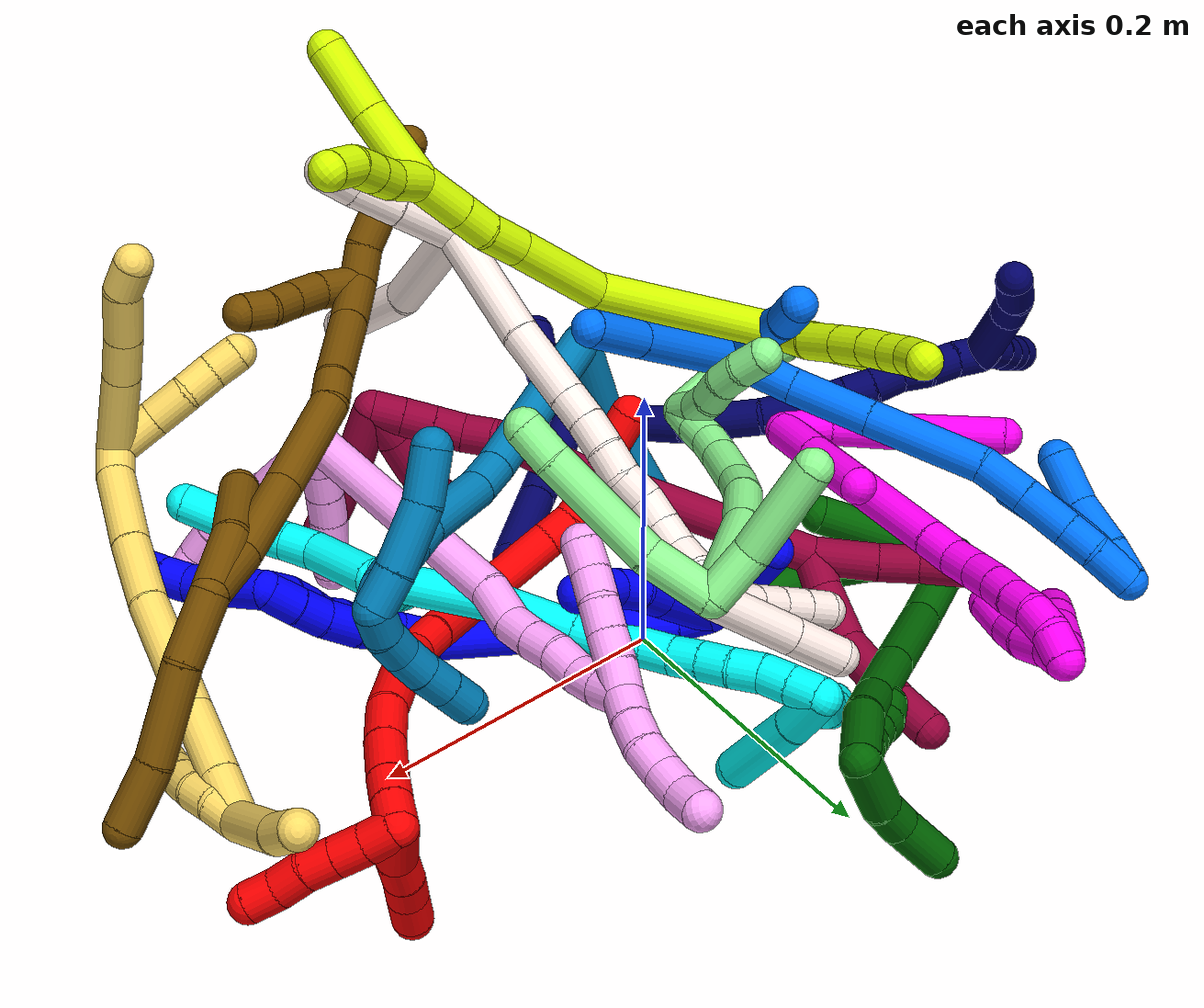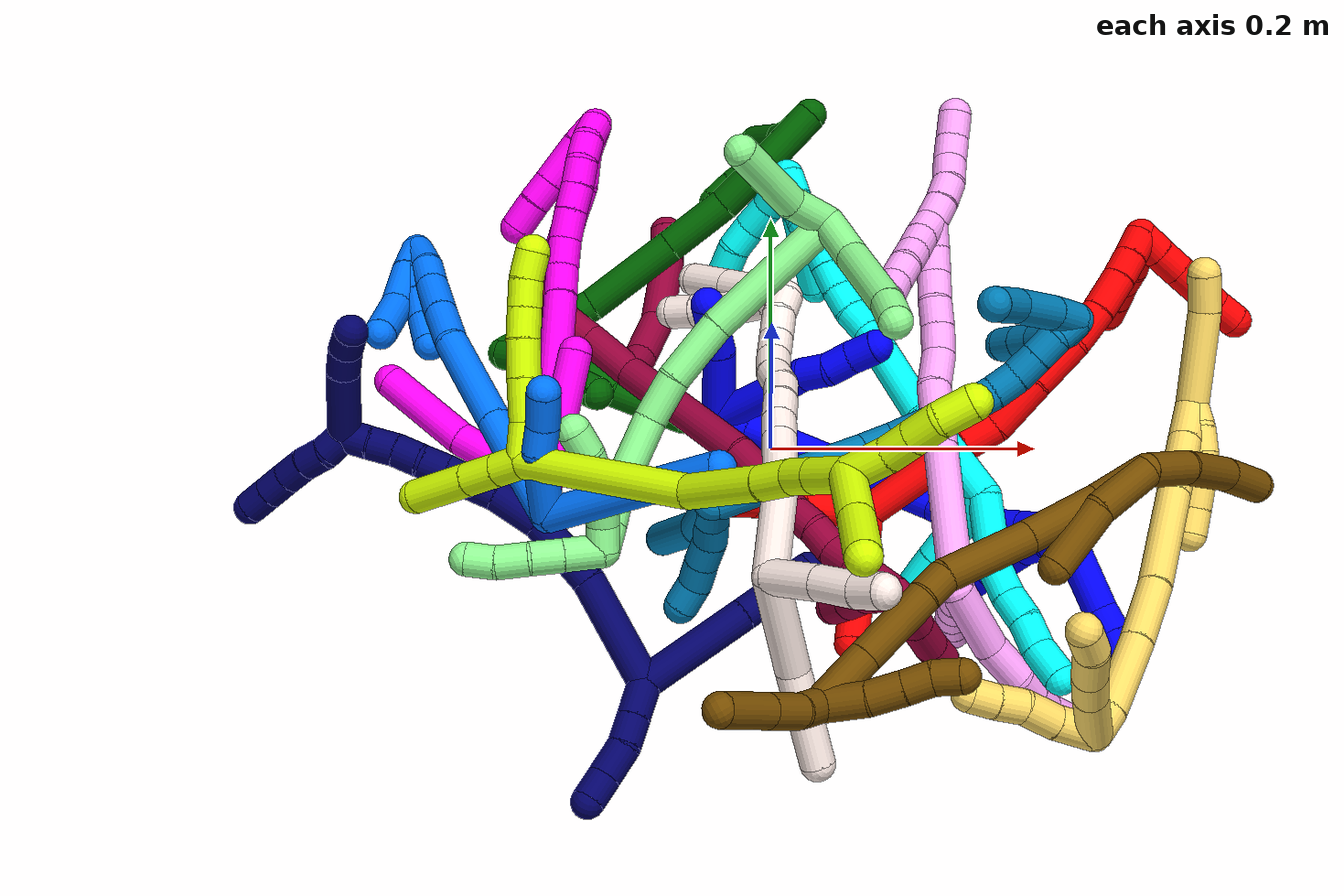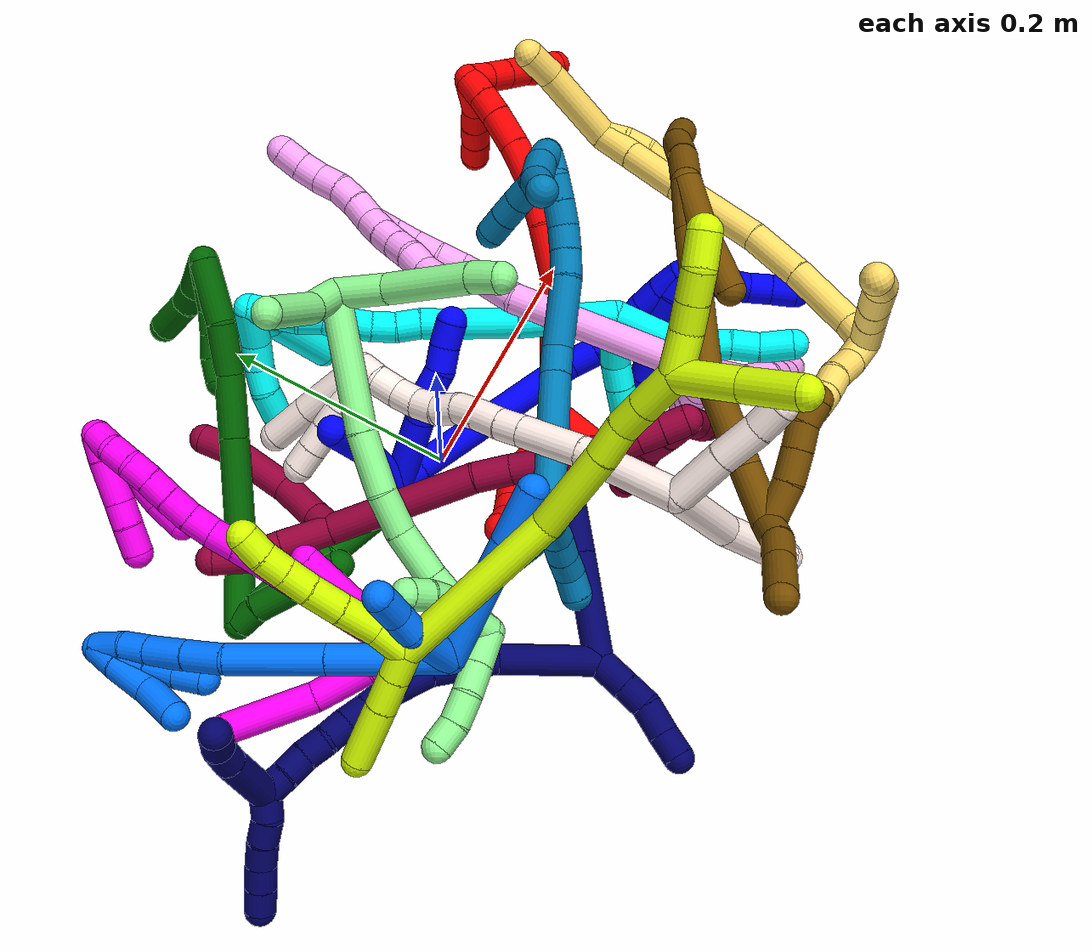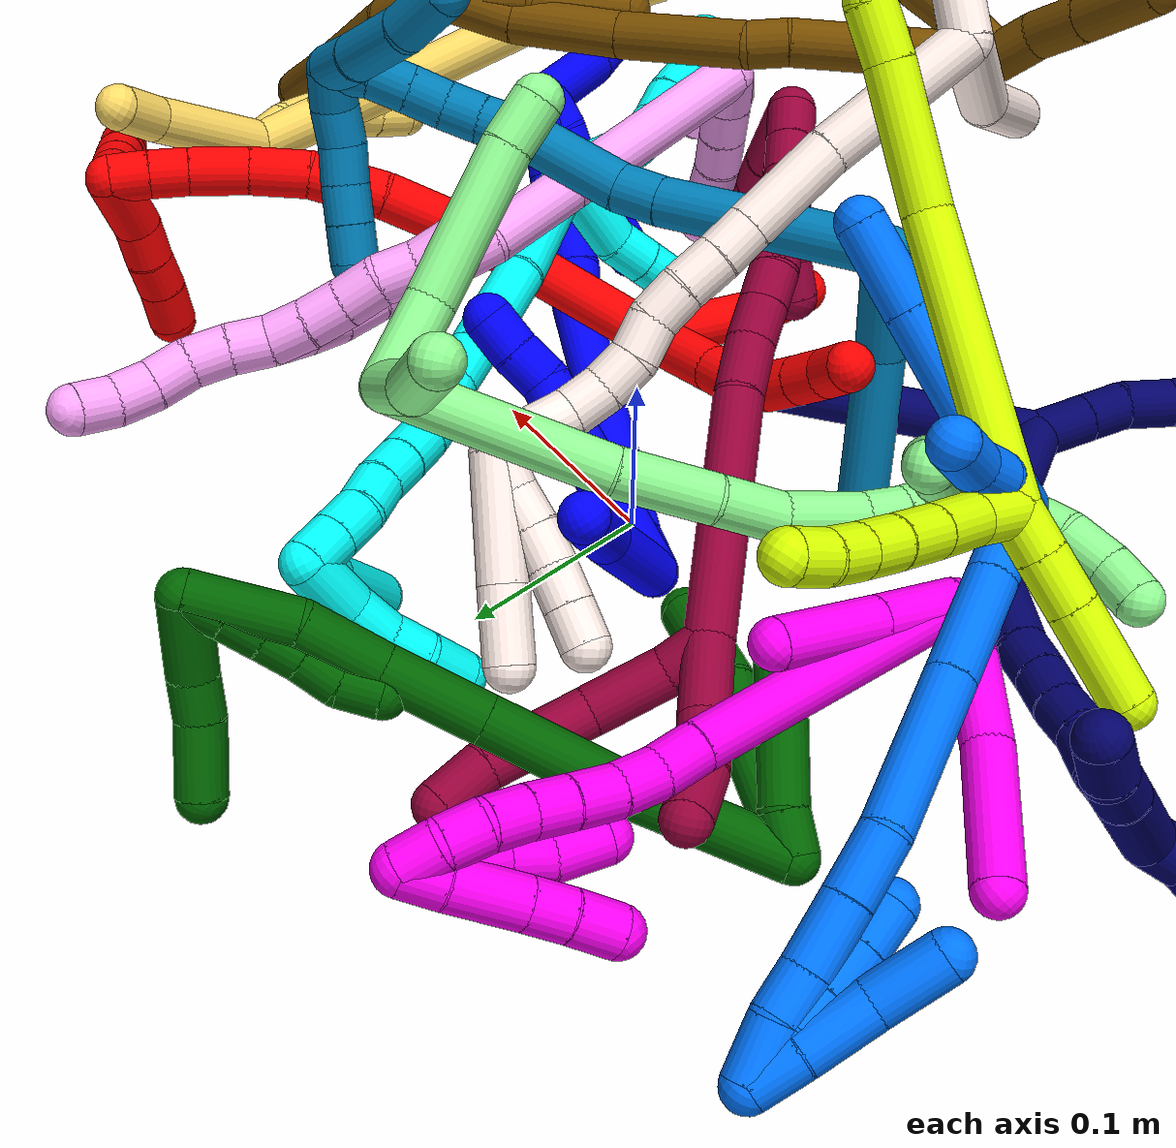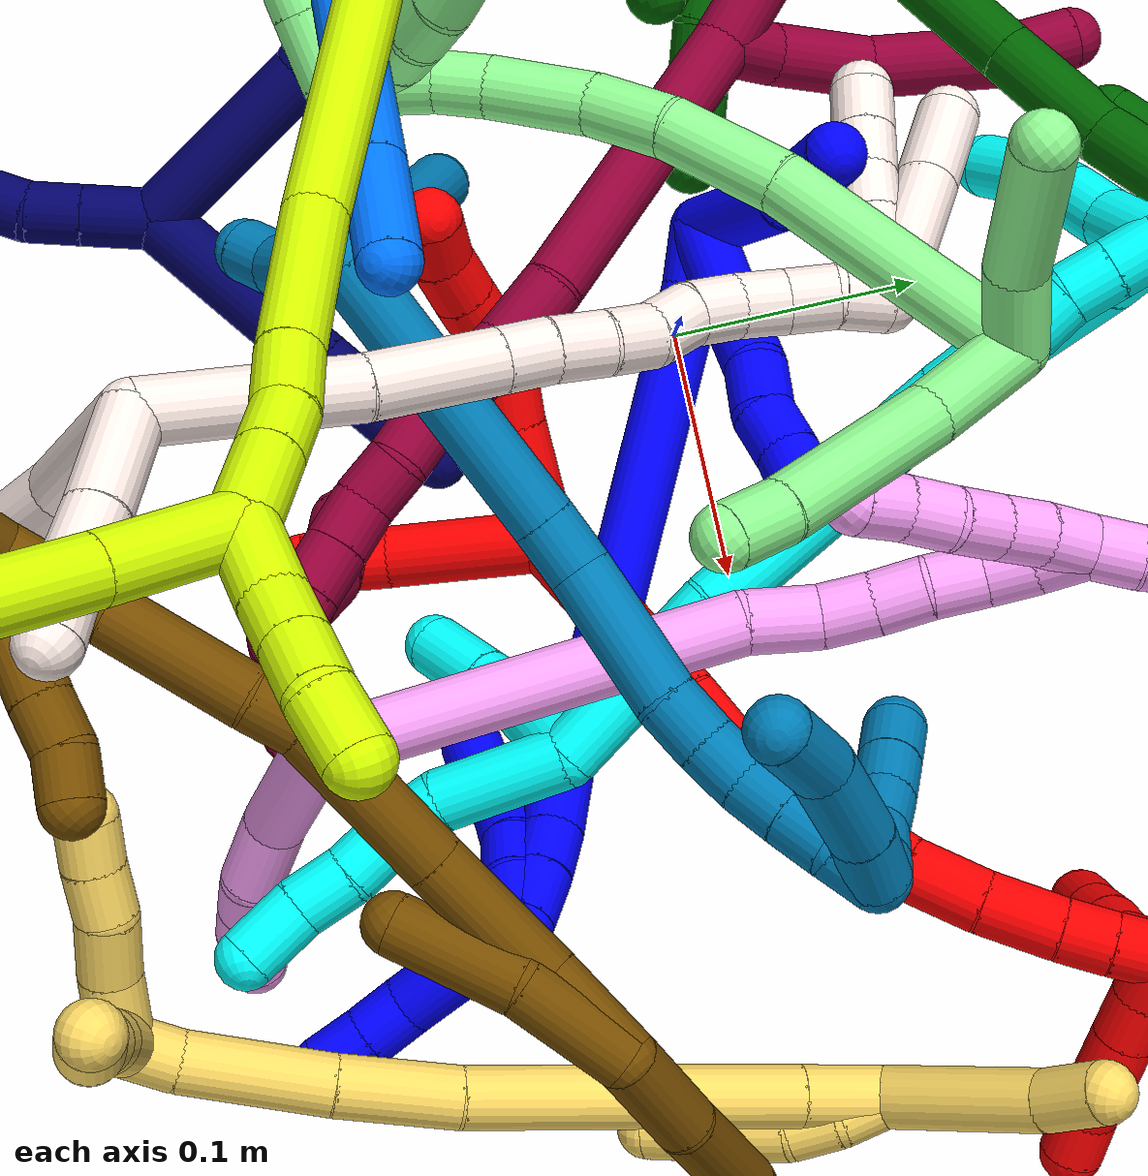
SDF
<sdf version="1.7">
 <world name="default">
  <plugin name="TubeGeneratorPlugin" filename="libtube_generator_plugin.so"/>
  <model name="photoneo_s_sensor">
   <static>1</static>
   <pose>0 0 2 1.57079 1.57079 3.14159</pose>
   <link name="link">
    <inertial><mass>0.1</mass></inertial>
    <sensor name="sensor" type="depth">
     <update_rate>30</update_rate>
     <camera>
      <horizontal_fov>1.22</horizontal_fov>
      <image><width>1920</width><height>1200</height><format>B8G8R8</format></image>
      <clip><near>0.1</near><far>4</far></clip>
      <depth_camera><output>points</output></depth_camera>
     </camera>
     <plugin name="camera_plugin" filename="libgazebo_ros_depth_camera.so">
      <baseline>0.2</baseline>
      <alwaysOn>1</alwaysOn>
      <updateRate>0.0</updateRate>
      <cameraName>camera_ir</cameraName>
      <imageTopicName>/camera/color/image_raw</imageTopicName>
      <cameraInfoTopicName>/camera/color/camera_info</cameraInfoTopicName>
      <depthImageTopicName>/camera/depth/image_raw</depthImageTopicName>
      <depthImageCameraInfoTopicName>/camera/depth/camera_info</depthImageCameraInfoTopicName>
      <pointCloudTopicName>/camera/depth/points</pointCloudTopicName>
      <frameName>fr_optical</frameName>
      <pointCloudCutoff>0.1</pointCloudCutoff>
      <pointCloudCutoffMax>2.0</pointCloudCutoffMax>
      <distortionK1>0</distortionK1>
      <distortionK2>0</distortionK2>
      <distortionK3>0</distortionK3>
      <distortionT1>0</distortionT1>
      <distortionT2>0</distortionT2>
      <CxPrime>0</CxPrime>
      <Cx>0</Cx>
      <Cy>0</Cy>
      <focalLength>0</focalLength>
      <hackBaseline>0</hackBaseline>
     </plugin>
    </sensor>
   </link>
  </model>
  <gravity>0 0 -9.8</gravity>
  <magnetic_field>6e-06 2.3e-05 -4.2e-05</magnetic_field>
  <atmosphere type="adiabatic"/>
  <physics name="default_physics" default="0" type="ode">
   <max_step_size>0.003</max_step_size>
   <real_time_factor>1</real_time_factor>
   <real_time_update_rate>1000</real_time_update_rate>
   <max_contacts>10000</max_contacts>
   <ode>
    <solver>
     <type>quick</type>
     <iters>100</iters>
     <sor>1.3</sor>
     <use_dynamic_moi_rescaling>0</use_dynamic_moi_rescaling>
    </solver>
    <constraints>
     <contact_max_correcting_vel>0</contact_max_correcting_vel>
     <contact_surface_layer>0.001</contact_surface_layer>
     <cfm>0</cfm>
     <erp>0.2</erp>
    </constraints>
   </ode>
  </physics>
  <scene><ambient>0.4 0.4 0.4 1</ambient><background>0.7 0.7 0.7 1</background><shadows>0</shadows></scene>
  <audio><device>default</device></audio>
  <spherical_coordinates>
   <surface_model>EARTH_WGS84</surface_model>
   <latitude_deg>0</latitude_deg>
   <longitude_deg>0</longitude_deg>
   <elevation>0</elevation>
   <heading_deg>0</heading_deg>
  </spherical_coordinates>
  <model name="bin">
   <static>1</static>
   <link name="bottom">
    <collision name="collision-bottom">
     <pose>0 0 -0.01 0 -0 0</pose>
     <geometry><box><size>0.8 0.6 0.02</size></box></geometry>
     <surface>
      <friction><ode><mu>100</mu><mu2>100</mu2></ode></friction>
      <contact><collide_bitmask>65535</collide_bitmask></contact>
     </surface>
    </collision>
   </link>
   <link name="west_wall">
    <collision name="collision-west_wall">
     <pose>-0.41 0 0.1 0 -0 0</pose>
     <geometry><box><size>0.02 0.6 0.2</size></box></geometry>
     <surface>
      <friction><ode><mu>100</mu><mu2>100</mu2></ode></friction>
      <contact><collide_bitmask>65535</collide_bitmask></contact>
     </surface>
    </collision>
   </link>
   <link name="east_wall">
    <collision name="collision-east_wall">
     <pose>0.41 0 0.1 0 -0 0</pose>
     <geometry><box><size>0.02 0.6 0.2</size></box></geometry>
     <surface>
      <friction><ode><mu>100</mu><mu2>100</mu2></ode></friction>
      <contact><collide_bitmask>65535</collide_bitmask></contact>
     </surface>
    </collision>
   </link>
   <link name="south_wall">
    <collision name="collision-south_wall">
     <pose>0 -0.31 0.1 0 -0 0</pose>
     <geometry><box><size>0.8 0.02 0.2</size></box></geometry>
     <surface>
      <friction><ode><mu>100</mu><mu2>100</mu2></ode></friction>
      <contact><collide_bitmask>65535</collide_bitmask></contact>
     </surface>
    </collision>
   </link>
   <link name="north_wall">
    <collision name="collision-north_wall">
     <pose>0 0.31 0.1 0 -0 0</pose>
     <geometry><box><size>0.8 0.02 0.2</size></box></geometry>
     <surface>
      <friction><ode><mu>100</mu><mu2>100</mu2></ode></friction>
      <contact><collide_bitmask>65535</collide_bitmask></contact>
     </surface>
    </collision>
   </link>
  </model>
  <model name="1">
   <static>0</static>
   <link name="1">
    <collision name="collision-cylinder-e_1_2_8">
     <pose>0.001427 0.000974 -0.031741 -3.11091 0.0449 -1.94286</pose>
     <geometry><cylinder><radius>0.0125</radius><length>0.063577</length></cylinder></geometry>
     <surface>
      <friction><ode><mu>1.16</mu><mu2>1.16</mu2><slip1>0</slip1><slip2>0</slip2></ode></friction>
      <contact><ode><kp>1e+06</kp><kd>1</kd><max_vel>0</max_vel><min_depth>0.001</min_depth></ode></contact>
     </surface>
    </collision>
    <visual name="visual-cylinder-e_1_2_8">
     <pose>0.001427 0.000974 -0.031741 -3.11091 0.0449 -1.94286</pose>
     <geometry><cylinder><radius>0.0125</radius><length>0.063577</length></cylinder></geometry>
     <material><ambient>0 0 1 1</ambient></material>
    </visual>
    <collision name="collision-cylinder-e_2_8_9">
     <pose>0.002942 0.002172 -0.075302 -3.12266 0.007431 -0.747946</pose>
     <geometry><cylinder><radius>0.0125</radius><length>0.023643</length></cylinder></geometry>
     <surface>
      <friction><ode><mu>1.16</mu><mu2>1.16</mu2><slip1>0</slip1><slip2>0</slip2></ode></friction>
      <contact><ode><kp>1e+06</kp><kd>1</kd><max_vel>0</max_vel><min_depth>0.001</min_depth></ode></contact>
     </surface>
    </collision>
    <visual name="visual-cylinder-e_2_8_9">
     <pose>0.002942 0.002172 -0.075302 -3.12266 0.007431 -0.747946</pose>
     <geometry><cylinder><radius>0.0125</radius><length>0.023643</length></cylinder></geometry>
     <material><ambient>0 0 1 1</ambient></material>
    </visual>
    <collision name="collision-cylinder-e_3_9_10">
     <pose>0.006066 0.003208 -0.097578 -3.06405 0.281782 -2.60768</pose>
     <geometry><cylinder><radius>0.0125</radius><length>0.021839</length></cylinder></geometry>
     <surface>
      <friction><ode><mu>1.16</mu><mu2>1.16</mu2><slip1>0</slip1><slip2>0</slip2></ode></friction>
      <contact><ode><kp>1e+06</kp><kd>1</kd><max_vel>0</max_vel><min_depth>0.001</min_depth></ode></contact>
     </surface>
    </collision>
    <visual name="visual-cylinder-e_3_9_10">
     <pose>0.006066 0.003208 -0.097578 -3.06405 0.281782 -2.60768</pose>
     <geometry><cylinder><radius>0.0125</radius><length>0.021839</length></cylinder></geometry>
     <material><ambient>0 0 1 1</ambient></material>
    </visual>
    <collision name="collision-cylinder-e_4_10_11">
     <pose>0.010911 0.001499 -0.117696 2.88629 0.179239 1.22162</pose>
     <geometry><cylinder><radius>0.0125</radius><length>0.020294</length></cylinder></geometry>
     <surface>
      <friction><ode><mu>1.16</mu><mu2>1.16</mu2><slip1>0</slip1><slip2>0</slip2></ode></friction>
      <contact><ode><kp>1e+06</kp><kd>1</kd><max_vel>0</max_vel><min_depth>0.001</min_depth></ode></contact>
     </surface>
    </collision>
    <visual name="visual-cylinder-e_4_10_11">
     <pose>0.010911 0.001499 -0.117696 2.88629 0.179239 1.22162</pose>
     <geometry><cylinder><radius>0.0125</radius><length>0.020294</length></cylinder></geometry>
     <material><ambient>0 0 1 1</ambient></material>
    </visual>
    <collision name="collision-cylinder-e_5_11_6">
     <pose>0.014457 -0.002235 -0.137461 3.02207 0.16908 1.91207</pose>
     <geometry><cylinder><radius>0.0125</radius><length>0.020648</length></cylinder></geometry>
     <surface>
      <friction><ode><mu>1.16</mu><mu2>1.16</mu2><slip1>0</slip1><slip2>0</slip2></ode></friction>
      <contact><ode><kp>1e+06</kp><kd>1</kd><max_vel>0</max_vel><min_depth>0.001</min_depth></ode></contact>
     </surface>
    </collision>
    <visual name="visual-cylinder-e_5_11_6">
     <pose>0.014457 -0.002235 -0.137461 3.02207 0.16908 1.91207</pose>
     <geometry><cylinder><radius>0.0125</radius><length>0.020648</length></cylinder></geometry>
     <material><ambient>0 0 1 1</ambient></material>
    </visual>
    <collision name="collision-cylinder-e_1_2_12">
     <pose>-0.020708 -0.005843 -0.018624 2.83759 -0.814935 -2.45954</pose>
     <geometry><cylinder><radius>0.0125</radius><length>0.056915</length></cylinder></geometry>
     <surface>
      <friction><ode><mu>1.16</mu><mu2>1.16</mu2><slip1>0</slip1><slip2>0</slip2></ode></friction>
      <contact><ode><kp>1e+06</kp><kd>1</kd><max_vel>0</max_vel><min_depth>0.001</min_depth></ode></contact>
     </surface>
    </collision>
    <visual name="visual-cylinder-e_1_2_12">
     <pose>-0.020708 -0.005843 -0.018624 2.83759 -0.814935 -2.45954</pose>
     <geometry><cylinder><radius>0.0125</radius><length>0.056915</length></cylinder></geometry>
     <material><ambient>0 0 1 1</ambient></material>
    </visual>
    <collision name="collision-cylinder-e_2_12_5">
     <pose>-0.059781 -0.013565 -0.048352 2.97396 -1.02075 -2.84368</pose>
     <geometry><cylinder><radius>0.0125</radius><length>0.043085</length></cylinder></geometry>
     <surface>
      <friction><ode><mu>1.16</mu><mu2>1.16</mu2><slip1>0</slip1><slip2>0</slip2></ode></friction>
      <contact><ode><kp>1e+06</kp><kd>1</kd><max_vel>0</max_vel><min_depth>0.001</min_depth></ode></contact>
     </surface>
    </collision>
    <visual name="visual-cylinder-e_2_12_5">
     <pose>-0.059781 -0.013565 -0.048352 2.97396 -1.02075 -2.84368</pose>
     <geometry><cylinder><radius>0.0125</radius><length>0.043085</length></cylinder></geometry>
     <material><ambient>0 0 1 1</ambient></material>
    </visual>
    <collision name="collision-cylinder-e_1_2_13">
     <pose>0.00984 0.001225 -0.007096 -2.97063 0.939018 -2.80696</pose>
     <geometry><cylinder><radius>0.0125</radius><length>0.024386</length></cylinder></geometry>
     <surface>
      <friction><ode><mu>1.16</mu><mu2>1.16</mu2><slip1>0</slip1><slip2>0</slip2></ode></friction>
      <contact><ode><kp>1e+06</kp><kd>1</kd><max_vel>0</max_vel><min_depth>0.001</min_depth></ode></contact>
     </surface>
    </collision>
    <visual name="visual-cylinder-e_1_2_13">
     <pose>0.00984 0.001225 -0.007096 -2.97063 0.939018 -2.80696</pose>
     <geometry><cylinder><radius>0.0125</radius><length>0.024386</length></cylinder></geometry>
     <material><ambient>0 0 1 1</ambient></material>
    </visual>
    <collision name="collision-cylinder-e_2_13_14">
     <pose>0.075188 0.022142 -0.0639 -2.76441 0.804135 -2.29781</pose>
     <geometry><cylinder><radius>0.0125</radius><length>0.154141</length></cylinder></geometry>
     <surface>
      <friction><ode><mu>1.16</mu><mu2>1.16</mu2><slip1>0</slip1><slip2>0</slip2></ode></friction>
      <contact><ode><kp>1e+06</kp><kd>1</kd><max_vel>0</max_vel><min_depth>0.001</min_depth></ode></contact>
     </surface>
    </collision>
    <visual name="visual-cylinder-e_2_13_14">
     <pose>0.075188 0.022142 -0.0639 -2.76441 0.804135 -2.29781</pose>
     <geometry><cylinder><radius>0.0125</radius><length>0.154141</length></cylinder></geometry>
     <material><ambient>0 0 1 1</ambient></material>
    </visual>
    <collision name="collision-cylinder-e_3_14_15">
     <pose>0.137251 0.047887 -0.121575 -2.49192 0.579987 -1.45015</pose>
     <geometry><cylinder><radius>0.0125</radius><length>0.023923</length></cylinder></geometry>
     <surface>
      <friction><ode><mu>1.16</mu><mu2>1.16</mu2><slip1>0</slip1><slip2>0</slip2></ode></friction>
      <contact><ode><kp>1e+06</kp><kd>1</kd><max_vel>0</max_vel><min_depth>0.001</min_depth></ode></contact>
     </surface>
    </collision>
    <visual name="visual-cylinder-e_3_14_15">
     <pose>0.137251 0.047887 -0.121575 -2.49192 0.579987 -1.45015</pose>
     <geometry><cylinder><radius>0.0125</radius><length>0.023923</length></cylinder></geometry>
     <material><ambient>0 0 1 1</ambient></material>
    </visual>
    <collision name="collision-cylinder-e_4_15_16">
     <pose>0.15118 0.057794 -0.141214 -2.82259 0.540336 -2.08911</pose>
     <geometry><cylinder><radius>0.0125</radius><length>0.028668</length></cylinder></geometry>
     <surface>
      <friction><ode><mu>1.16</mu><mu2>1.16</mu2><slip1>0</slip1><slip2>0</slip2></ode></friction>
      <contact><ode><kp>1e+06</kp><kd>1</kd><max_vel>0</max_vel><min_depth>0.001</min_depth></ode></contact>
     </surface>
    </collision>
    <visual name="visual-cylinder-e_4_15_16">
     <pose>0.15118 0.057794 -0.141214 -2.82259 0.540336 -2.08911</pose>
     <geometry><cylinder><radius>0.0125</radius><length>0.028668</length></cylinder></geometry>
     <material><ambient>0 0 1 1</ambient></material>
    </visual>
    <collision name="collision-cylinder-e_5_16_17">
     <pose>0.162441 0.065756 -0.164524 -2.80239 0.305108 -1.46323</pose>
     <geometry><cylinder><radius>0.0125</radius><length>0.025878</length></cylinder></geometry>
     <surface>
      <friction><ode><mu>1.16</mu><mu2>1.16</mu2><slip1>0</slip1><slip2>0</slip2></ode></friction>
      <contact><ode><kp>1e+06</kp><kd>1</kd><max_vel>0</max_vel><min_depth>0.001</min_depth></ode></contact>
     </surface>
    </collision>
    <visual name="visual-cylinder-e_5_16_17">
     <pose>0.162441 0.065756 -0.164524 -2.80239 0.305108 -1.46323</pose>
     <geometry><cylinder><radius>0.0125</radius><length>0.025878</length></cylinder></geometry>
     <material><ambient>0 0 1 1</ambient></material>
    </visual>
    <collision name="collision-cylinder-e_6_17_18">
     <pose>0.168426 0.073985 -0.18507 -2.70809 0.210668 -0.895212</pose>
     <geometry><cylinder><radius>0.0125</radius><length>0.020075</length></cylinder></geometry>
     <surface>
      <friction><ode><mu>1.16</mu><mu2>1.16</mu2><slip1>0</slip1><slip2>0</slip2></ode></friction>
      <contact><ode><kp>1e+06</kp><kd>1</kd><max_vel>0</max_vel><min_depth>0.001</min_depth></ode></contact>
     </surface>
    </collision>
    <visual name="visual-cylinder-e_6_17_18">
     <pose>0.168426 0.073985 -0.18507 -2.70809 0.210668 -0.895212</pose>
     <geometry><cylinder><radius>0.0125</radius><length>0.020075</length></cylinder></geometry>
     <material><ambient>0 0 1 1</ambient></material>
    </visual>
    <collision name="collision-cylinder-e_7_18_1">
     <pose>0.172962 0.083661 -0.203707 -2.62302 0.214142 -0.769953</pose>
     <geometry><cylinder><radius>0.0125</radius><length>0.022929</length></cylinder></geometry>
     <surface>
      <friction><ode><mu>1.16</mu><mu2>1.16</mu2><slip1>0</slip1><slip2>0</slip2></ode></friction>
      <contact><ode><kp>1e+06</kp><kd>1</kd><max_vel>0</max_vel><min_depth>0.001</min_depth></ode></contact>
     </surface>
    </collision>
    <visual name="visual-cylinder-e_7_18_1">
     <pose>0.172962 0.083661 -0.203707 -2.62302 0.214142 -0.769953</pose>
     <geometry><cylinder><radius>0.0125</radius><length>0.022929</length></cylinder></geometry>
     <material><ambient>0 0 1 1</ambient></material>
    </visual>
    <collision name="collision-cylinder-e_1_1_19">
     <pose>0.198956 0.107031 -0.212958 -1.54392 0.92309 -0.901825</pose>
     <geometry><cylinder><radius>0.0125</radius><length>0.059081</length></cylinder></geometry>
     <surface>
      <friction><ode><mu>1.16</mu><mu2>1.16</mu2><slip1>0</slip1><slip2>0</slip2></ode></friction>
      <contact><ode><kp>1e+06</kp><kd>1</kd><max_vel>0</max_vel><min_depth>0.001</min_depth></ode></contact>
     </surface>
    </collision>
    <visual name="visual-cylinder-e_1_1_19">
     <pose>0.198956 0.107031 -0.212958 -1.54392 0.92309 -0.901825</pose>
     <geometry><cylinder><radius>0.0125</radius><length>0.059081</length></cylinder></geometry>
     <material><ambient>0 0 1 1</ambient></material>
    </visual>
    <collision name="collision-cylinder-e_2_19_20">
     <pose>0.22921 0.132067 -0.21425 -1.81131 0.733275 -0.910522</pose>
     <geometry><cylinder><radius>0.0125</radius><length>0.02001</length></cylinder></geometry>
     <surface>
      <friction><ode><mu>1.16</mu><mu2>1.16</mu2><slip1>0</slip1><slip2>0</slip2></ode></friction>
      <contact><ode><kp>1e+06</kp><kd>1</kd><max_vel>0</max_vel><min_depth>0.001</min_depth></ode></contact>
     </surface>
    </collision>
    <visual name="visual-cylinder-e_2_19_20">
     <pose>0.22921 0.132067 -0.21425 -1.81131 0.733275 -0.910522</pose>
     <geometry><cylinder><radius>0.0125</radius><length>0.02001</length></cylinder></geometry>
     <material><ambient>0 0 1 1</ambient></material>
    </visual>
    <collision name="collision-cylinder-e_3_20_4">
     <pose>0.24264 0.147133 -0.217565 -1.76513 0.699866 -0.835348</pose>
     <geometry><cylinder><radius>0.0125</radius><length>0.020908</length></cylinder></geometry>
     <surface>
      <friction><ode><mu>1.16</mu><mu2>1.16</mu2><slip1>0</slip1><slip2>0</slip2></ode></friction>
      <contact><ode><kp>1e+06</kp><kd>1</kd><max_vel>0</max_vel><min_depth>0.001</min_depth></ode></contact>
     </surface>
    </collision>
    <visual name="visual-cylinder-e_3_20_4">
     <pose>0.24264 0.147133 -0.217565 -1.76513 0.699866 -0.835348</pose>
     <geometry><cylinder><radius>0.0125</radius><length>0.020908</length></cylinder></geometry>
     <material><ambient>0 0 1 1</ambient></material>
    </visual>
    <collision name="collision-cylinder-e_1_1_21">
     <pose>0.174397 0.088757 -0.203498 0.045911 -0.100283 -0.002304</pose>
     <geometry><cylinder><radius>0.0125</radius><length>0.02</length></cylinder></geometry>
     <surface>
      <friction><ode><mu>1.16</mu><mu2>1.16</mu2><slip1>0</slip1><slip2>0</slip2></ode></friction>
      <contact><ode><kp>1e+06</kp><kd>1</kd><max_vel>0</max_vel><min_depth>0.001</min_depth></ode></contact>
     </surface>
    </collision>
    <visual name="visual-cylinder-e_1_1_21">
     <pose>0.174397 0.088757 -0.203498 0.045911 -0.100283 -0.002304</pose>
     <geometry><cylinder><radius>0.0125</radius><length>0.02</length></cylinder></geometry>
     <material><ambient>0 0 1 1</ambient></material>
    </visual>
    <collision name="collision-cylinder-e_2_21_22">
     <pose>0.173512 0.086135 -0.183796 0.218255 0.011586 0.001269</pose>
     <geometry><cylinder><radius>0.0125</radius><length>0.02</length></cylinder></geometry>
     <surface>
      <friction><ode><mu>1.16</mu><mu2>1.16</mu2><slip1>0</slip1><slip2>0</slip2></ode></friction>
      <contact><ode><kp>1e+06</kp><kd>1</kd><max_vel>0</max_vel><min_depth>0.001</min_depth></ode></contact>
     </surface>
    </collision>
    <visual name="visual-cylinder-e_2_21_22">
     <pose>0.173512 0.086135 -0.183796 0.218255 0.011586 0.001269</pose>
     <geometry><cylinder><radius>0.0125</radius><length>0.02</length></cylinder></geometry>
     <material><ambient>0 0 1 1</ambient></material>
    </visual>
    <collision name="collision-cylinder-e_3_22_23">
     <pose>0.17531 0.082977 -0.164227 0.100847 0.169059 0.008552</pose>
     <geometry><cylinder><radius>0.0125</radius><length>0.02</length></cylinder></geometry>
     <surface>
      <friction><ode><mu>1.16</mu><mu2>1.16</mu2><slip1>0</slip1><slip2>0</slip2></ode></friction>
      <contact><ode><kp>1e+06</kp><kd>1</kd><max_vel>0</max_vel><min_depth>0.001</min_depth></ode></contact>
     </surface>
    </collision>
    <visual name="visual-cylinder-e_3_22_23">
     <pose>0.17531 0.082977 -0.164227 0.100847 0.169059 0.008552</pose>
     <geometry><cylinder><radius>0.0125</radius><length>0.02</length></cylinder></geometry>
     <material><ambient>0 0 1 1</ambient></material>
    </visual>
    <collision name="collision-cylinder-e_4_23_24">
     <pose>0.177092 0.083687 -0.144566 -0.171055 0.009997 -0.000857</pose>
     <geometry><cylinder><radius>0.0125</radius><length>0.02</length></cylinder></geometry>
     <surface>
      <friction><ode><mu>1.16</mu><mu2>1.16</mu2><slip1>0</slip1><slip2>0</slip2></ode></friction>
      <contact><ode><kp>1e+06</kp><kd>1</kd><max_vel>0</max_vel><min_depth>0.001</min_depth></ode></contact>
     </surface>
    </collision>
    <visual name="visual-cylinder-e_4_23_24">
     <pose>0.177092 0.083687 -0.144566 -0.171055 0.009997 -0.000857</pose>
     <geometry><cylinder><radius>0.0125</radius><length>0.02</length></cylinder></geometry>
     <material><ambient>0 0 1 1</ambient></material>
    </visual>
    <collision name="collision-cylinder-e_5_24_3">
     <pose>0.178225 0.085359 -0.124766 0.003013 0.103424 0.000156</pose>
     <geometry><cylinder><radius>0.0125</radius><length>0.02</length></cylinder></geometry>
     <surface>
      <friction><ode><mu>1.16</mu><mu2>1.16</mu2><slip1>0</slip1><slip2>0</slip2></ode></friction>
      <contact><ode><kp>1e+06</kp><kd>1</kd><max_vel>0</max_vel><min_depth>0.001</min_depth></ode></contact>
     </surface>
    </collision>
    <visual name="visual-cylinder-e_5_24_3">
     <pose>0.178225 0.085359 -0.124766 0.003013 0.103424 0.000156</pose>
     <geometry><cylinder><radius>0.0125</radius><length>0.02</length></cylinder></geometry>
     <material><ambient>0 0 1 1</ambient></material>
    </visual>
    <collision name="collision-sphere-3">
     <pose>0.179257 0.085329 -0.114819 0 -0 0</pose>
     <geometry><sphere><radius>0.0125</radius></sphere></geometry>
     <surface>
      <friction><ode><mu>1.16</mu><mu2>1.16</mu2><slip1>0</slip1><slip2>0</slip2></ode></friction>
      <contact><ode><kp>1e+06</kp><kd>1</kd><max_vel>0</max_vel><min_depth>0.001</min_depth></ode></contact>
     </surface>
    </collision>
    <visual name="visual-sphere-3">
     <pose>0.179257 0.085329 -0.114819 0 -0 0</pose>
     <geometry><sphere><radius>0.0125</radius></sphere></geometry>
     <material><ambient>0 0 1 1</ambient></material>
    </visual>
    <collision name="collision-sphere-24">
     <pose>0.177192 0.085389 -0.134712 0 -0 0</pose>
     <geometry><sphere><radius>0.0125</radius></sphere></geometry>
     <surface>
      <friction><ode><mu>1.16</mu><mu2>1.16</mu2><slip1>0</slip1><slip2>0</slip2></ode></friction>
      <contact><ode><kp>1e+06</kp><kd>1</kd><max_vel>0</max_vel><min_depth>0.001</min_depth></ode></contact>
     </surface>
    </collision>
    <visual name="visual-sphere-24">
     <pose>0.177192 0.085389 -0.134712 0 -0 0</pose>
     <geometry><sphere><radius>0.0125</radius></sphere></geometry>
     <material><ambient>0 0 1 1</ambient></material>
    </visual>
    <collision name="collision-sphere-23">
     <pose>0.176993 0.081985 -0.154419 0 -0 0</pose>
     <geometry><sphere><radius>0.0125</radius></sphere></geometry>
     <surface>
      <friction><ode><mu>1.16</mu><mu2>1.16</mu2><slip1>0</slip1><slip2>0</slip2></ode></friction>
      <contact><ode><kp>1e+06</kp><kd>1</kd><max_vel>0</max_vel><min_depth>0.001</min_depth></ode></contact>
     </surface>
    </collision>
    <visual name="visual-sphere-23">
     <pose>0.176993 0.081985 -0.154419 0 -0 0</pose>
     <geometry><sphere><radius>0.0125</radius></sphere></geometry>
     <material><ambient>0 0 1 1</ambient></material>
    </visual>
    <collision name="collision-sphere-22">
     <pose>0.173627 0.08397 -0.174034 0 -0 0</pose>
     <geometry><sphere><radius>0.0125</radius></sphere></geometry>
     <surface>
      <friction><ode><mu>1.16</mu><mu2>1.16</mu2><slip1>0</slip1><slip2>0</slip2></ode></friction>
      <contact><ode><kp>1e+06</kp><kd>1</kd><max_vel>0</max_vel><min_depth>0.001</min_depth></ode></contact>
     </surface>
    </collision>
    <visual name="visual-sphere-22">
     <pose>0.173627 0.08397 -0.174034 0 -0 0</pose>
     <geometry><sphere><radius>0.0125</radius></sphere></geometry>
     <material><ambient>0 0 1 1</ambient></material>
    </visual>
    <collision name="collision-sphere-21">
     <pose>0.173396 0.0883 -0.193558 0 -0 0</pose>
     <geometry><sphere><radius>0.0125</radius></sphere></geometry>
     <surface>
      <friction><ode><mu>1.16</mu><mu2>1.16</mu2><slip1>0</slip1><slip2>0</slip2></ode></friction>
      <contact><ode><kp>1e+06</kp><kd>1</kd><max_vel>0</max_vel><min_depth>0.001</min_depth></ode></contact>
     </surface>
    </collision>
    <visual name="visual-sphere-21">
     <pose>0.173396 0.0883 -0.193558 0 -0 0</pose>
     <geometry><sphere><radius>0.0125</radius></sphere></geometry>
     <material><ambient>0 0 1 1</ambient></material>
    </visual>
    <collision name="collision-sphere-4">
     <pose>0.249374 0.15498 -0.219109 0 -0 0</pose>
     <geometry><sphere><radius>0.0125</radius></sphere></geometry>
     <surface>
      <friction><ode><mu>1.16</mu><mu2>1.16</mu2><slip1>0</slip1><slip2>0</slip2></ode></friction>
      <contact><ode><kp>1e+06</kp><kd>1</kd><max_vel>0</max_vel><min_depth>0.001</min_depth></ode></contact>
     </surface>
    </collision>
    <visual name="visual-sphere-4">
     <pose>0.249374 0.15498 -0.219109 0 -0 0</pose>
     <geometry><sphere><radius>0.0125</radius></sphere></geometry>
     <material><ambient>0 0 1 1</ambient></material>
    </visual>
    <collision name="collision-sphere-20">
     <pose>0.235907 0.139287 -0.21602 0 -0 0</pose>
     <geometry><sphere><radius>0.0125</radius></sphere></geometry>
     <surface>
      <friction><ode><mu>1.16</mu><mu2>1.16</mu2><slip1>0</slip1><slip2>0</slip2></ode></friction>
      <contact><ode><kp>1e+06</kp><kd>1</kd><max_vel>0</max_vel><min_depth>0.001</min_depth></ode></contact>
     </surface>
    </collision>
    <visual name="visual-sphere-20">
     <pose>0.235907 0.139287 -0.21602 0 -0 0</pose>
     <geometry><sphere><radius>0.0125</radius></sphere></geometry>
     <material><ambient>0 0 1 1</ambient></material>
    </visual>
    <collision name="collision-sphere-6">
     <pose>0.016195 -0.003449 -0.147565 0 -0 0</pose>
     <geometry><sphere><radius>0.0125</radius></sphere></geometry>
     <surface>
      <friction><ode><mu>1.16</mu><mu2>1.16</mu2><slip1>0</slip1><slip2>0</slip2></ode></friction>
      <contact><ode><kp>1e+06</kp><kd>1</kd><max_vel>0</max_vel><min_depth>0.001</min_depth></ode></contact>
     </surface>
    </collision>
    <visual name="visual-sphere-6">
     <pose>0.016195 -0.003449 -0.147565 0 -0 0</pose>
     <geometry><sphere><radius>0.0125</radius></sphere></geometry>
     <material><ambient>0 0 1 1</ambient></material>
    </visual>
    <collision name="collision-sphere-11">
     <pose>0.01272 -0.001022 -0.127357 0 -0 0</pose>
     <geometry><sphere><radius>0.0125</radius></sphere></geometry>
     <surface>
      <friction><ode><mu>1.16</mu><mu2>1.16</mu2><slip1>0</slip1><slip2>0</slip2></ode></friction>
      <contact><ode><kp>1e+06</kp><kd>1</kd><max_vel>0</max_vel><min_depth>0.001</min_depth></ode></contact>
     </surface>
    </collision>
    <visual name="visual-sphere-11">
     <pose>0.01272 -0.001022 -0.127357 0 -0 0</pose>
     <geometry><sphere><radius>0.0125</radius></sphere></geometry>
     <material><ambient>0 0 1 1</ambient></material>
    </visual>
    <collision name="collision-sphere-10">
     <pose>0.009102 0.004021 -0.108035 0 -0 0</pose>
     <geometry><sphere><radius>0.0125</radius></sphere></geometry>
     <surface>
      <friction><ode><mu>1.16</mu><mu2>1.16</mu2><slip1>0</slip1><slip2>0</slip2></ode></friction>
      <contact><ode><kp>1e+06</kp><kd>1</kd><max_vel>0</max_vel><min_depth>0.001</min_depth></ode></contact>
     </surface>
    </collision>
    <visual name="visual-sphere-10">
     <pose>0.009102 0.004021 -0.108035 0 -0 0</pose>
     <geometry><sphere><radius>0.0125</radius></sphere></geometry>
     <material><ambient>0 0 1 1</ambient></material>
    </visual>
    <collision name="collision-sphere-9">
     <pose>0.003029 0.002396 -0.08712 0 -0 0</pose>
     <geometry><sphere><radius>0.0125</radius></sphere></geometry>
     <surface>
      <friction><ode><mu>1.16</mu><mu2>1.16</mu2><slip1>0</slip1><slip2>0</slip2></ode></friction>
      <contact><ode><kp>1e+06</kp><kd>1</kd><max_vel>0</max_vel><min_depth>0.001</min_depth></ode></contact>
     </surface>
    </collision>
    <visual name="visual-sphere-9">
     <pose>0.003029 0.002396 -0.08712 0 -0 0</pose>
     <geometry><sphere><radius>0.0125</radius></sphere></geometry>
     <material><ambient>0 0 1 1</ambient></material>
    </visual>
    <collision name="collision-sphere-2">
     <geometry><sphere><radius>0.0125</radius></sphere></geometry>
     <surface>
      <friction><ode><mu>1.16</mu><mu2>1.16</mu2><slip1>0</slip1><slip2>0</slip2></ode></friction>
      <contact><ode><kp>1e+06</kp><kd>1</kd><max_vel>0</max_vel><min_depth>0.001</min_depth></ode></contact>
     </surface>
    </collision>
    <visual name="visual-sphere-2">
     <geometry><sphere><radius>0.0125</radius></sphere></geometry>
     <material><ambient>0 0 1 1</ambient></material>
    </visual>
    <collision name="collision-sphere-19">
     <pose>0.222513 0.124848 -0.212479 0 -0 0</pose>
     <geometry><sphere><radius>0.0125</radius></sphere></geometry>
     <surface>
      <friction><ode><mu>1.16</mu><mu2>1.16</mu2><slip1>0</slip1><slip2>0</slip2></ode></friction>
      <contact><ode><kp>1e+06</kp><kd>1</kd><max_vel>0</max_vel><min_depth>0.001</min_depth></ode></contact>
     </surface>
    </collision>
    <visual name="visual-sphere-19">
     <pose>0.222513 0.124848 -0.212479 0 -0 0</pose>
     <geometry><sphere><radius>0.0125</radius></sphere></geometry>
     <material><ambient>0 0 1 1</ambient></material>
    </visual>
    <collision name="collision-sphere-8">
     <pose>0.002854 0.001948 -0.063483 0 -0 0</pose>
     <geometry><sphere><radius>0.0125</radius></sphere></geometry>
     <surface>
      <friction><ode><mu>1.16</mu><mu2>1.16</mu2><slip1>0</slip1><slip2>0</slip2></ode></friction>
      <contact><ode><kp>1e+06</kp><kd>1</kd><max_vel>0</max_vel><min_depth>0.001</min_depth></ode></contact>
     </surface>
    </collision>
    <visual name="visual-sphere-8">
     <pose>0.002854 0.001948 -0.063483 0 -0 0</pose>
     <geometry><sphere><radius>0.0125</radius></sphere></geometry>
     <material><ambient>0 0 1 1</ambient></material>
    </visual>
    <collision name="collision-sphere-12">
     <pose>-0.041416 -0.011686 -0.037249 0 -0 0</pose>
     <geometry><sphere><radius>0.0125</radius></sphere></geometry>
     <surface>
      <friction><ode><mu>1.16</mu><mu2>1.16</mu2><slip1>0</slip1><slip2>0</slip2></ode></friction>
      <contact><ode><kp>1e+06</kp><kd>1</kd><max_vel>0</max_vel><min_depth>0.001</min_depth></ode></contact>
     </surface>
    </collision>
    <visual name="visual-sphere-12">
     <pose>-0.041416 -0.011686 -0.037249 0 -0 0</pose>
     <geometry><sphere><radius>0.0125</radius></sphere></geometry>
     <material><ambient>0 0 1 1</ambient></material>
    </visual>
    <collision name="collision-sphere-5">
     <pose>-0.078146 -0.015444 -0.059455 0 -0 0</pose>
     <geometry><sphere><radius>0.0125</radius></sphere></geometry>
     <surface>
      <friction><ode><mu>1.16</mu><mu2>1.16</mu2><slip1>0</slip1><slip2>0</slip2></ode></friction>
      <contact><ode><kp>1e+06</kp><kd>1</kd><max_vel>0</max_vel><min_depth>0.001</min_depth></ode></contact>
     </surface>
    </collision>
    <visual name="visual-sphere-5">
     <pose>-0.078146 -0.015444 -0.059455 0 -0 0</pose>
     <geometry><sphere><radius>0.0125</radius></sphere></geometry>
     <material><ambient>0 0 1 1</ambient></material>
    </visual>
    <collision name="collision-sphere-13">
     <pose>0.019679 0.00245 -0.014192 0 -0 0</pose>
     <geometry><sphere><radius>0.0125</radius></sphere></geometry>
     <surface>
      <friction><ode><mu>1.16</mu><mu2>1.16</mu2><slip1>0</slip1><slip2>0</slip2></ode></friction>
      <contact><ode><kp>1e+06</kp><kd>1</kd><max_vel>0</max_vel><min_depth>0.001</min_depth></ode></contact>
     </surface>
    </collision>
    <visual name="visual-sphere-13">
     <pose>0.019679 0.00245 -0.014192 0 -0 0</pose>
     <geometry><sphere><radius>0.0125</radius></sphere></geometry>
     <material><ambient>0 0 1 1</ambient></material>
    </visual>
    <collision name="collision-sphere-14">
     <pose>0.130696 0.041834 -0.113608 0 -0 0</pose>
     <geometry><sphere><radius>0.0125</radius></sphere></geometry>
     <surface>
      <friction><ode><mu>1.16</mu><mu2>1.16</mu2><slip1>0</slip1><slip2>0</slip2></ode></friction>
      <contact><ode><kp>1e+06</kp><kd>1</kd><max_vel>0</max_vel><min_depth>0.001</min_depth></ode></contact>
     </surface>
    </collision>
    <visual name="visual-sphere-14">
     <pose>0.130696 0.041834 -0.113608 0 -0 0</pose>
     <geometry><sphere><radius>0.0125</radius></sphere></geometry>
     <material><ambient>0 0 1 1</ambient></material>
    </visual>
    <collision name="collision-sphere-15">
     <pose>0.143806 0.05394 -0.129542 0 -0 0</pose>
     <geometry><sphere><radius>0.0125</radius></sphere></geometry>
     <surface>
      <friction><ode><mu>1.16</mu><mu2>1.16</mu2><slip1>0</slip1><slip2>0</slip2></ode></friction>
      <contact><ode><kp>1e+06</kp><kd>1</kd><max_vel>0</max_vel><min_depth>0.001</min_depth></ode></contact>
     </surface>
    </collision>
    <visual name="visual-sphere-15">
     <pose>0.143806 0.05394 -0.129542 0 -0 0</pose>
     <geometry><sphere><radius>0.0125</radius></sphere></geometry>
     <material><ambient>0 0 1 1</ambient></material>
    </visual>
    <collision name="collision-sphere-16">
     <pose>0.158554 0.061649 -0.152886 0 -0 0</pose>
     <geometry><sphere><radius>0.0125</radius></sphere></geometry>
     <surface>
      <friction><ode><mu>1.16</mu><mu2>1.16</mu2><slip1>0</slip1><slip2>0</slip2></ode></friction>
      <contact><ode><kp>1e+06</kp><kd>1</kd><max_vel>0</max_vel><min_depth>0.001</min_depth></ode></contact>
     </surface>
    </collision>
    <visual name="visual-sphere-16">
     <pose>0.158554 0.061649 -0.152886 0 -0 0</pose>
     <geometry><sphere><radius>0.0125</radius></sphere></geometry>
     <material><ambient>0 0 1 1</ambient></material>
    </visual>
    <collision name="collision-sphere-17">
     <pose>0.166327 0.069862 -0.176162 0 -0 0</pose>
     <geometry><sphere><radius>0.0125</radius></sphere></geometry>
     <surface>
      <friction><ode><mu>1.16</mu><mu2>1.16</mu2><slip1>0</slip1><slip2>0</slip2></ode></friction>
      <contact><ode><kp>1e+06</kp><kd>1</kd><max_vel>0</max_vel><min_depth>0.001</min_depth></ode></contact>
     </surface>
    </collision>
    <visual name="visual-sphere-17">
     <pose>0.166327 0.069862 -0.176162 0 -0 0</pose>
     <geometry><sphere><radius>0.0125</radius></sphere></geometry>
     <material><ambient>0 0 1 1</ambient></material>
    </visual>
    <collision name="collision-sphere-18">
     <pose>0.170525 0.078108 -0.193978 0 -0 0</pose>
     <geometry><sphere><radius>0.0125</radius></sphere></geometry>
     <surface>
      <friction><ode><mu>1.16</mu><mu2>1.16</mu2><slip1>0</slip1><slip2>0</slip2></ode></friction>
      <contact><ode><kp>1e+06</kp><kd>1</kd><max_vel>0</max_vel><min_depth>0.001</min_depth></ode></contact>
     </surface>
    </collision>
    <visual name="visual-sphere-18">
     <pose>0.170525 0.078108 -0.193978 0 -0 0</pose>
     <geometry><sphere><radius>0.0125</radius></sphere></geometry>
     <material><ambient>0 0 1 1</ambient></material>
    </visual>
    <collision name="collision-sphere-1">
     <pose>0.175398 0.089213 -0.213437 0 -0 0</pose>
     <geometry><sphere><radius>0.0125</radius></sphere></geometry>
     <surface>
      <friction><ode><mu>1.16</mu><mu2>1.16</mu2><slip1>0</slip1><slip2>0</slip2></ode></friction>
      <contact><ode><kp>1e+06</kp><kd>1</kd><max_vel>0</max_vel><min_depth>0.001</min_depth></ode></contact>
     </surface>
    </collision>
    <visual name="visual-sphere-1">
     <pose>0.175398 0.089213 -0.213437 0 -0 0</pose>
     <geometry><sphere><radius>0.0125</radius></sphere></geometry>
     <material><ambient>0 0 1 1</ambient></material>
    </visual>
    <inertial>
     <pose>0.089388 0.041576 -0.10901 0 -0 0</pose>
     <mass>0.75</mass>
     <inertia>
      <ixx>-0.000347</ixx>
      <ixy>0</ixy>
      <ixz>0</ixz>
      <iyy>0.000108</iyy>
      <iyz>0</iyz>
      <izz>-0.000349</izz>
     </inertia>
    </inertial>
   </link>
   <pose>-0.039508 0.019486 0.014017 2.69036 0.676124 -0.519994</pose>
  </model>
  <model name="2">
   <static>0</static>
   <link name="2">
    <collision name="collision-cylinder-e_1_2_8">
     <pose>-0.024255 0.004829 0.001104 -1.34606 -1.36933 1.15393</pose>
     <geometry><cylinder><radius>0.0125</radius><length>0.049512</length></cylinder></geometry>
     <surface>
      <friction><ode><mu>1.16</mu><mu2>1.16</mu2><slip1>0</slip1><slip2>0</slip2></ode></friction>
      <contact><ode><kp>1e+06</kp><kd>1</kd><max_vel>0</max_vel><min_depth>0.001</min_depth></ode></contact>
     </surface>
    </collision>
    <visual name="visual-cylinder-e_1_2_8">
     <pose>-0.024255 0.004829 0.001104 -1.34606 -1.36933 1.15393</pose>
     <geometry><cylinder><radius>0.0125</radius><length>0.049512</length></cylinder></geometry>
     <material><ambient>1 0 0 1</ambient></material>
    </visual>
    <collision name="collision-cylinder-e_2_8_9">
     <pose>-0.058228 0.012166 0.00361 -1.06094 -1.28333 0.826054</pose>
     <geometry><cylinder><radius>0.0125</radius><length>0.020268</length></cylinder></geometry>
     <surface>
      <friction><ode><mu>1.16</mu><mu2>1.16</mu2><slip1>0</slip1><slip2>0</slip2></ode></friction>
      <contact><ode><kp>1e+06</kp><kd>1</kd><max_vel>0</max_vel><min_depth>0.001</min_depth></ode></contact>
     </surface>
    </collision>
    <visual name="visual-cylinder-e_2_8_9">
     <pose>-0.058228 0.012166 0.00361 -1.06094 -1.28333 0.826054</pose>
     <geometry><cylinder><radius>0.0125</radius><length>0.020268</length></cylinder></geometry>
     <material><ambient>1 0 0 1</ambient></material>
    </visual>
    <collision name="collision-cylinder-e_3_9_10">
     <pose>-0.077812 0.014669 0.006763 0.00283 -1.39514 -0.002372</pose>
     <geometry><cylinder><radius>0.0125</radius><length>0.020038</length></cylinder></geometry>
     <surface>
      <friction><ode><mu>1.16</mu><mu2>1.16</mu2><slip1>0</slip1><slip2>0</slip2></ode></friction>
      <contact><ode><kp>1e+06</kp><kd>1</kd><max_vel>0</max_vel><min_depth>0.001</min_depth></ode></contact>
     </surface>
    </collision>
    <visual name="visual-cylinder-e_3_9_10">
     <pose>-0.077812 0.014669 0.006763 0.00283 -1.39514 -0.002372</pose>
     <geometry><cylinder><radius>0.0125</radius><length>0.020038</length></cylinder></geometry>
     <material><ambient>1 0 0 1</ambient></material>
    </visual>
    <collision name="collision-cylinder-e_4_10_11">
     <pose>-0.096832 0.012633 0.012169 0.507286 -1.14243 -0.330169</pose>
     <geometry><cylinder><radius>0.0125</radius><length>0.020131</length></cylinder></geometry>
     <surface>
      <friction><ode><mu>1.16</mu><mu2>1.16</mu2><slip1>0</slip1><slip2>0</slip2></ode></friction>
      <contact><ode><kp>1e+06</kp><kd>1</kd><max_vel>0</max_vel><min_depth>0.001</min_depth></ode></contact>
     </surface>
    </collision>
    <visual name="visual-cylinder-e_4_10_11">
     <pose>-0.096832 0.012633 0.012169 0.507286 -1.14243 -0.330169</pose>
     <geometry><cylinder><radius>0.0125</radius><length>0.020131</length></cylinder></geometry>
     <material><ambient>1 0 0 1</ambient></material>
    </visual>
    <collision name="collision-cylinder-e_5_11_12">
     <pose>-0.114983 0.008765 0.0198 0.432751 -1.11762 -0.273187</pose>
     <geometry><cylinder><radius>0.0125</radius><length>0.02001</length></cylinder></geometry>
     <surface>
      <friction><ode><mu>1.16</mu><mu2>1.16</mu2><slip1>0</slip1><slip2>0</slip2></ode></friction>
      <contact><ode><kp>1e+06</kp><kd>1</kd><max_vel>0</max_vel><min_depth>0.001</min_depth></ode></contact>
     </surface>
    </collision>
    <visual name="visual-cylinder-e_5_11_12">
     <pose>-0.114983 0.008765 0.0198 0.432751 -1.11762 -0.273187</pose>
     <geometry><cylinder><radius>0.0125</radius><length>0.02001</length></cylinder></geometry>
     <material><ambient>1 0 0 1</ambient></material>
    </visual>
    <collision name="collision-cylinder-e_6_12_6">
     <pose>-0.132295 0.006872 0.029366 0.009993 -0.978955 -0.005324</pose>
     <geometry><cylinder><radius>0.0125</radius><length>0.020042</length></cylinder></geometry>
     <surface>
      <friction><ode><mu>1.16</mu><mu2>1.16</mu2><slip1>0</slip1><slip2>0</slip2></ode></friction>
      <contact><ode><kp>1e+06</kp><kd>1</kd><max_vel>0</max_vel><min_depth>0.001</min_depth></ode></contact>
     </surface>
    </collision>
    <visual name="visual-cylinder-e_6_12_6">
     <pose>-0.132295 0.006872 0.029366 0.009993 -0.978955 -0.005324</pose>
     <geometry><cylinder><radius>0.0125</radius><length>0.020042</length></cylinder></geometry>
     <material><ambient>1 0 0 1</ambient></material>
    </visual>
    <collision name="collision-cylinder-e_1_2_13">
     <pose>-0.008402 -0.025544 -0.017759 2.17833 -0.263759 -0.497073</pose>
     <geometry><cylinder><radius>0.0125</radius><length>0.064451</length></cylinder></geometry>
     <surface>
      <friction><ode><mu>1.16</mu><mu2>1.16</mu2><slip1>0</slip1><slip2>0</slip2></ode></friction>
      <contact><ode><kp>1e+06</kp><kd>1</kd><max_vel>0</max_vel><min_depth>0.001</min_depth></ode></contact>
     </surface>
    </collision>
    <visual name="visual-cylinder-e_1_2_13">
     <pose>-0.008402 -0.025544 -0.017759 2.17833 -0.263759 -0.497073</pose>
     <geometry><cylinder><radius>0.0125</radius><length>0.064451</length></cylinder></geometry>
     <material><ambient>1 0 0 1</ambient></material>
    </visual>
    <collision name="collision-cylinder-e_2_13_5">
     <pose>-0.02303 -0.066674 -0.04137 1.92992 -0.357907 -0.510836</pose>
     <geometry><cylinder><radius>0.0125</radius><length>0.035549</length></cylinder></geometry>
     <surface>
      <friction><ode><mu>1.16</mu><mu2>1.16</mu2><slip1>0</slip1><slip2>0</slip2></ode></friction>
      <contact><ode><kp>1e+06</kp><kd>1</kd><max_vel>0</max_vel><min_depth>0.001</min_depth></ode></contact>
     </surface>
    </collision>
    <visual name="visual-cylinder-e_2_13_5">
     <pose>-0.02303 -0.066674 -0.04137 1.92992 -0.357907 -0.510836</pose>
     <geometry><cylinder><radius>0.0125</radius><length>0.035549</length></cylinder></geometry>
     <material><ambient>1 0 0 1</ambient></material>
    </visual>
    <collision name="collision-cylinder-e_1_2_14">
     <pose>0.033775 0.004331 0.028216 -0.152287 0.869087 -0.070789</pose>
     <geometry><cylinder><radius>0.0125</radius><length>0.088445</length></cylinder></geometry>
     <surface>
      <friction><ode><mu>1.16</mu><mu2>1.16</mu2><slip1>0</slip1><slip2>0</slip2></ode></friction>
      <contact><ode><kp>1e+06</kp><kd>1</kd><max_vel>0</max_vel><min_depth>0.001</min_depth></ode></contact>
     </surface>
    </collision>
    <visual name="visual-cylinder-e_1_2_14">
     <pose>0.033775 0.004331 0.028216 -0.152287 0.869087 -0.070789</pose>
     <geometry><cylinder><radius>0.0125</radius><length>0.088445</length></cylinder></geometry>
     <material><ambient>1 0 0 1</ambient></material>
    </visual>
    <collision name="collision-cylinder-e_2_14_15">
     <pose>0.078403 0.009781 0.063507 -0.157068 0.987495 -0.084659</pose>
     <geometry><cylinder><radius>0.0125</radius><length>0.026009</length></cylinder></geometry>
     <surface>
      <friction><ode><mu>1.16</mu><mu2>1.16</mu2><slip1>0</slip1><slip2>0</slip2></ode></friction>
      <contact><ode><kp>1e+06</kp><kd>1</kd><max_vel>0</max_vel><min_depth>0.001</min_depth></ode></contact>
     </surface>
    </collision>
    <visual name="visual-cylinder-e_2_14_15">
     <pose>0.078403 0.009781 0.063507 -0.157068 0.987495 -0.084659</pose>
     <geometry><cylinder><radius>0.0125</radius><length>0.026009</length></cylinder></geometry>
     <material><ambient>1 0 0 1</ambient></material>
    </visual>
    <collision name="collision-cylinder-e_3_15_16">
     <pose>0.103526 0.017029 0.085749 -0.383913 0.717265 -0.145444</pose>
     <geometry><cylinder><radius>0.0125</radius><length>0.043413</length></cylinder></geometry>
     <surface>
      <friction><ode><mu>1.16</mu><mu2>1.16</mu2><slip1>0</slip1><slip2>0</slip2></ode></friction>
      <contact><ode><kp>1e+06</kp><kd>1</kd><max_vel>0</max_vel><min_depth>0.001</min_depth></ode></contact>
     </surface>
    </collision>
    <visual name="visual-cylinder-e_3_15_16">
     <pose>0.103526 0.017029 0.085749 -0.383913 0.717265 -0.145444</pose>
     <geometry><cylinder><radius>0.0125</radius><length>0.043413</length></cylinder></geometry>
     <material><ambient>1 0 0 1</ambient></material>
    </visual>
    <collision name="collision-cylinder-e_4_16_17">
     <pose>0.132287 0.030321 0.112622 -0.549248 0.812623 -0.241264</pose>
     <geometry><cylinder><radius>0.0125</radius><length>0.039921</length></cylinder></geometry>
     <surface>
      <friction><ode><mu>1.16</mu><mu2>1.16</mu2><slip1>0</slip1><slip2>0</slip2></ode></friction>
      <contact><ode><kp>1e+06</kp><kd>1</kd><max_vel>0</max_vel><min_depth>0.001</min_depth></ode></contact>
     </surface>
    </collision>
    <visual name="visual-cylinder-e_4_16_17">
     <pose>0.132287 0.030321 0.112622 -0.549248 0.812623 -0.241264</pose>
     <geometry><cylinder><radius>0.0125</radius><length>0.039921</length></cylinder></geometry>
     <material><ambient>1 0 0 1</ambient></material>
    </visual>
    <collision name="collision-cylinder-e_5_17_18">
     <pose>0.157826 0.045779 0.131586 -0.851861 0.786531 -0.37211</pose>
     <geometry><cylinder><radius>0.0125</radius><length>0.031208</length></cylinder></geometry>
     <surface>
      <friction><ode><mu>1.16</mu><mu2>1.16</mu2><slip1>0</slip1><slip2>0</slip2></ode></friction>
      <contact><ode><kp>1e+06</kp><kd>1</kd><max_vel>0</max_vel><min_depth>0.001</min_depth></ode></contact>
     </surface>
    </collision>
    <visual name="visual-cylinder-e_5_17_18">
     <pose>0.157826 0.045779 0.131586 -0.851861 0.786531 -0.37211</pose>
     <geometry><cylinder><radius>0.0125</radius><length>0.031208</length></cylinder></geometry>
     <material><ambient>1 0 0 1</ambient></material>
    </visual>
    <collision name="collision-cylinder-e_6_18_19">
     <pose>0.179053 0.063435 0.145735 -0.936341 0.719279 -0.375767</pose>
     <geometry><cylinder><radius>0.0125</radius><length>0.030906</length></cylinder></geometry>
     <surface>
      <friction><ode><mu>1.16</mu><mu2>1.16</mu2><slip1>0</slip1><slip2>0</slip2></ode></friction>
      <contact><ode><kp>1e+06</kp><kd>1</kd><max_vel>0</max_vel><min_depth>0.001</min_depth></ode></contact>
     </surface>
    </collision>
    <visual name="visual-cylinder-e_6_18_19">
     <pose>0.179053 0.063435 0.145735 -0.936341 0.719279 -0.375767</pose>
     <geometry><cylinder><radius>0.0125</radius><length>0.030906</length></cylinder></geometry>
     <material><ambient>1 0 0 1</ambient></material>
    </visual>
    <collision name="collision-cylinder-e_7_19_20">
     <pose>0.19554 0.079381 0.156824 -1.00311 0.679385 -0.382803</pose>
     <geometry><cylinder><radius>0.0125</radius><length>0.020071</length></cylinder></geometry>
     <surface>
      <friction><ode><mu>1.16</mu><mu2>1.16</mu2><slip1>0</slip1><slip2>0</slip2></ode></friction>
      <contact><ode><kp>1e+06</kp><kd>1</kd><max_vel>0</max_vel><min_depth>0.001</min_depth></ode></contact>
     </surface>
    </collision>
    <visual name="visual-cylinder-e_7_19_20">
     <pose>0.19554 0.079381 0.156824 -1.00311 0.679385 -0.382803</pose>
     <geometry><cylinder><radius>0.0125</radius><length>0.020071</length></cylinder></geometry>
     <material><ambient>1 0 0 1</ambient></material>
    </visual>
    <collision name="collision-cylinder-e_8_20_1">
     <pose>0.207952 0.092847 0.164972 -1.04977 0.655815 -0.389003</pose>
     <geometry><cylinder><radius>0.0125</radius><length>0.020028</length></cylinder></geometry>
     <surface>
      <friction><ode><mu>1.16</mu><mu2>1.16</mu2><slip1>0</slip1><slip2>0</slip2></ode></friction>
      <contact><ode><kp>1e+06</kp><kd>1</kd><max_vel>0</max_vel><min_depth>0.001</min_depth></ode></contact>
     </surface>
    </collision>
    <visual name="visual-cylinder-e_8_20_1">
     <pose>0.207952 0.092847 0.164972 -1.04977 0.655815 -0.389003</pose>
     <geometry><cylinder><radius>0.0125</radius><length>0.020028</length></cylinder></geometry>
     <material><ambient>1 0 0 1</ambient></material>
    </visual>
    <collision name="collision-cylinder-e_1_1_21">
     <pose>0.221102 0.09461 0.164006 2.3359 0.781525 1.5369</pose>
     <geometry><cylinder><radius>0.0125</radius><length>0.02</length></cylinder></geometry>
     <surface>
      <friction><ode><mu>1.16</mu><mu2>1.16</mu2><slip1>0</slip1><slip2>0</slip2></ode></friction>
      <contact><ode><kp>1e+06</kp><kd>1</kd><max_vel>0</max_vel><min_depth>0.001</min_depth></ode></contact>
     </surface>
    </collision>
    <visual name="visual-cylinder-e_1_1_21">
     <pose>0.221102 0.09461 0.164006 2.3359 0.781525 1.5369</pose>
     <geometry><cylinder><radius>0.0125</radius><length>0.02</length></cylinder></geometry>
     <material><ambient>1 0 0 1</ambient></material>
    </visual>
    <collision name="collision-cylinder-e_2_21_22">
     <pose>0.23534 0.083995 0.154842 2.22885 0.803054 1.42612</pose>
     <geometry><cylinder><radius>0.0125</radius><length>0.02</length></cylinder></geometry>
     <surface>
      <friction><ode><mu>1.16</mu><mu2>1.16</mu2><slip1>0</slip1><slip2>0</slip2></ode></friction>
      <contact><ode><kp>1e+06</kp><kd>1</kd><max_vel>0</max_vel><min_depth>0.001</min_depth></ode></contact>
     </surface>
    </collision>
    <visual name="visual-cylinder-e_2_21_22">
     <pose>0.23534 0.083995 0.154842 2.22885 0.803054 1.42612</pose>
     <geometry><cylinder><radius>0.0125</radius><length>0.02</length></cylinder></geometry>
     <material><ambient>1 0 0 1</ambient></material>
    </visual>
    <collision name="collision-cylinder-e_3_22_23">
     <pose>0.249778 0.073 0.146437 2.2181 0.810033 1.4223</pose>
     <geometry><cylinder><radius>0.0125</radius><length>0.02</length></cylinder></geometry>
     <surface>
      <friction><ode><mu>1.16</mu><mu2>1.16</mu2><slip1>0</slip1><slip2>0</slip2></ode></friction>
      <contact><ode><kp>1e+06</kp><kd>1</kd><max_vel>0</max_vel><min_depth>0.001</min_depth></ode></contact>
     </surface>
    </collision>
    <visual name="visual-cylinder-e_3_22_23">
     <pose>0.249778 0.073 0.146437 2.2181 0.810033 1.4223</pose>
     <geometry><cylinder><radius>0.0125</radius><length>0.02</length></cylinder></geometry>
     <material><ambient>1 0 0 1</ambient></material>
    </visual>
    <collision name="collision-cylinder-e_4_23_24">
     <pose>0.264222 0.06318 0.136849 2.46955 0.803936 1.76607</pose>
     <geometry><cylinder><radius>0.0125</radius><length>0.02</length></cylinder></geometry>
     <surface>
      <friction><ode><mu>1.16</mu><mu2>1.16</mu2><slip1>0</slip1><slip2>0</slip2></ode></friction>
      <contact><ode><kp>1e+06</kp><kd>1</kd><max_vel>0</max_vel><min_depth>0.001</min_depth></ode></contact>
     </surface>
    </collision>
    <visual name="visual-cylinder-e_4_23_24">
     <pose>0.264222 0.06318 0.136849 2.46955 0.803936 1.76607</pose>
     <geometry><cylinder><radius>0.0125</radius><length>0.02</length></cylinder></geometry>
     <material><ambient>1 0 0 1</ambient></material>
    </visual>
    <collision name="collision-cylinder-e_5_24_4">
     <pose>0.279021 0.053698 0.127466 2.22434 0.862921 1.50092</pose>
     <geometry><cylinder><radius>0.0125</radius><length>0.02</length></cylinder></geometry>
     <surface>
      <friction><ode><mu>1.16</mu><mu2>1.16</mu2><slip1>0</slip1><slip2>0</slip2></ode></friction>
      <contact><ode><kp>1e+06</kp><kd>1</kd><max_vel>0</max_vel><min_depth>0.001</min_depth></ode></contact>
     </surface>
    </collision>
    <visual name="visual-cylinder-e_5_24_4">
     <pose>0.279021 0.053698 0.127466 2.22434 0.862921 1.50092</pose>
     <geometry><cylinder><radius>0.0125</radius><length>0.02</length></cylinder></geometry>
     <material><ambient>1 0 0 1</ambient></material>
    </visual>
    <collision name="collision-cylinder-e_1_1_25">
     <pose>0.216201 0.100364 0.151439 -3.10537 0.12187 -2.56434</pose>
     <geometry><cylinder><radius>0.0125</radius><length>0.035252</length></cylinder></geometry>
     <surface>
      <friction><ode><mu>1.16</mu><mu2>1.16</mu2><slip1>0</slip1><slip2>0</slip2></ode></friction>
      <contact><ode><kp>1e+06</kp><kd>1</kd><max_vel>0</max_vel><min_depth>0.001</min_depth></ode></contact>
     </surface>
    </collision>
    <visual name="visual-cylinder-e_1_1_25">
     <pose>0.216201 0.100364 0.151439 -3.10537 0.12187 -2.56434</pose>
     <geometry><cylinder><radius>0.0125</radius><length>0.035252</length></cylinder></geometry>
     <material><ambient>1 0 0 1</ambient></material>
    </visual>
    <collision name="collision-cylinder-e_2_25_26">
     <pose>0.218992 0.103764 0.123728 -2.87738 0.061135 -0.452349</pose>
     <geometry><cylinder><radius>0.0125</radius><length>0.021229</length></cylinder></geometry>
     <surface>
      <friction><ode><mu>1.16</mu><mu2>1.16</mu2><slip1>0</slip1><slip2>0</slip2></ode></friction>
      <contact><ode><kp>1e+06</kp><kd>1</kd><max_vel>0</max_vel><min_depth>0.001</min_depth></ode></contact>
     </surface>
    </collision>
    <visual name="visual-cylinder-e_2_25_26">
     <pose>0.218992 0.103764 0.123728 -2.87738 0.061135 -0.452349</pose>
     <geometry><cylinder><radius>0.0125</radius><length>0.021229</length></cylinder></geometry>
     <material><ambient>1 0 0 1</ambient></material>
    </visual>
    <collision name="collision-cylinder-e_3_26_27">
     <pose>0.220526 0.108249 0.103539 -2.97077 0.087363 -0.944041</pose>
     <geometry><cylinder><radius>0.0125</radius><length>0.020295</length></cylinder></geometry>
     <surface>
      <friction><ode><mu>1.16</mu><mu2>1.16</mu2><slip1>0</slip1><slip2>0</slip2></ode></friction>
      <contact><ode><kp>1e+06</kp><kd>1</kd><max_vel>0</max_vel><min_depth>0.001</min_depth></ode></contact>
     </surface>
    </collision>
    <visual name="visual-cylinder-e_3_26_27">
     <pose>0.220526 0.108249 0.103539 -2.97077 0.087363 -0.944041</pose>
     <geometry><cylinder><radius>0.0125</radius><length>0.020295</length></cylinder></geometry>
     <material><ambient>1 0 0 1</ambient></material>
    </visual>
    <collision name="collision-cylinder-e_4_27_3">
     <pose>0.222893 0.112702 0.08239 -2.90185 0.127928 -0.977485</pose>
     <geometry><cylinder><radius>0.0125</radius><length>0.023224</length></cylinder></geometry>
     <surface>
      <friction><ode><mu>1.16</mu><mu2>1.16</mu2><slip1>0</slip1><slip2>0</slip2></ode></friction>
      <contact><ode><kp>1e+06</kp><kd>1</kd><max_vel>0</max_vel><min_depth>0.001</min_depth></ode></contact>
     </surface>
    </collision>
    <visual name="visual-cylinder-e_4_27_3">
     <pose>0.222893 0.112702 0.08239 -2.90185 0.127928 -0.977485</pose>
     <geometry><cylinder><radius>0.0125</radius><length>0.023224</length></cylinder></geometry>
     <material><ambient>1 0 0 1</ambient></material>
    </visual>
    <collision name="collision-sphere-3">
     <pose>0.224374 0.115437 0.071202 0 -0 0</pose>
     <geometry><sphere><radius>0.0125</radius></sphere></geometry>
     <surface>
      <friction><ode><mu>1.16</mu><mu2>1.16</mu2><slip1>0</slip1><slip2>0</slip2></ode></friction>
      <contact><ode><kp>1e+06</kp><kd>1</kd><max_vel>0</max_vel><min_depth>0.001</min_depth></ode></contact>
     </surface>
    </collision>
    <visual name="visual-sphere-3">
     <pose>0.224374 0.115437 0.071202 0 -0 0</pose>
     <geometry><sphere><radius>0.0125</radius></sphere></geometry>
     <material><ambient>1 0 0 1</ambient></material>
    </visual>
    <collision name="collision-sphere-27">
     <pose>0.221412 0.109968 0.093578 0 -0 0</pose>
     <geometry><sphere><radius>0.0125</radius></sphere></geometry>
     <surface>
      <friction><ode><mu>1.16</mu><mu2>1.16</mu2><slip1>0</slip1><slip2>0</slip2></ode></friction>
      <contact><ode><kp>1e+06</kp><kd>1</kd><max_vel>0</max_vel><min_depth>0.001</min_depth></ode></contact>
     </surface>
    </collision>
    <visual name="visual-sphere-27">
     <pose>0.221412 0.109968 0.093578 0 -0 0</pose>
     <geometry><sphere><radius>0.0125</radius></sphere></geometry>
     <material><ambient>1 0 0 1</ambient></material>
    </visual>
    <collision name="collision-sphere-26">
     <pose>0.219641 0.106531 0.113501 0 -0 0</pose>
     <geometry><sphere><radius>0.0125</radius></sphere></geometry>
     <surface>
      <friction><ode><mu>1.16</mu><mu2>1.16</mu2><slip1>0</slip1><slip2>0</slip2></ode></friction>
      <contact><ode><kp>1e+06</kp><kd>1</kd><max_vel>0</max_vel><min_depth>0.001</min_depth></ode></contact>
     </surface>
    </collision>
    <visual name="visual-sphere-26">
     <pose>0.219641 0.106531 0.113501 0 -0 0</pose>
     <geometry><sphere><radius>0.0125</radius></sphere></geometry>
     <material><ambient>1 0 0 1</ambient></material>
    </visual>
    <collision name="collision-sphere-25">
     <pose>0.218344 0.100997 0.133955 0 -0 0</pose>
     <geometry><sphere><radius>0.0125</radius></sphere></geometry>
     <surface>
      <friction><ode><mu>1.16</mu><mu2>1.16</mu2><slip1>0</slip1><slip2>0</slip2></ode></friction>
      <contact><ode><kp>1e+06</kp><kd>1</kd><max_vel>0</max_vel><min_depth>0.001</min_depth></ode></contact>
     </surface>
    </collision>
    <visual name="visual-sphere-25">
     <pose>0.218344 0.100997 0.133955 0 -0 0</pose>
     <geometry><sphere><radius>0.0125</radius></sphere></geometry>
     <material><ambient>1 0 0 1</ambient></material>
    </visual>
    <collision name="collision-sphere-4">
     <pose>0.286618 0.048535 0.123512 0 -0 0</pose>
     <geometry><sphere><radius>0.0125</radius></sphere></geometry>
     <surface>
      <friction><ode><mu>1.16</mu><mu2>1.16</mu2><slip1>0</slip1><slip2>0</slip2></ode></friction>
      <contact><ode><kp>1e+06</kp><kd>1</kd><max_vel>0</max_vel><min_depth>0.001</min_depth></ode></contact>
     </surface>
    </collision>
    <visual name="visual-sphere-4">
     <pose>0.286618 0.048535 0.123512 0 -0 0</pose>
     <geometry><sphere><radius>0.0125</radius></sphere></geometry>
     <material><ambient>1 0 0 1</ambient></material>
    </visual>
    <collision name="collision-sphere-24">
     <pose>0.271423 0.05886 0.131419 0 -0 0</pose>
     <geometry><sphere><radius>0.0125</radius></sphere></geometry>
     <surface>
      <friction><ode><mu>1.16</mu><mu2>1.16</mu2><slip1>0</slip1><slip2>0</slip2></ode></friction>
      <contact><ode><kp>1e+06</kp><kd>1</kd><max_vel>0</max_vel><min_depth>0.001</min_depth></ode></contact>
     </surface>
    </collision>
    <visual name="visual-sphere-24">
     <pose>0.271423 0.05886 0.131419 0 -0 0</pose>
     <geometry><sphere><radius>0.0125</radius></sphere></geometry>
     <material><ambient>1 0 0 1</ambient></material>
    </visual>
    <collision name="collision-sphere-23">
     <pose>0.257021 0.0675 0.142279 0 -0 0</pose>
     <geometry><sphere><radius>0.0125</radius></sphere></geometry>
     <surface>
      <friction><ode><mu>1.16</mu><mu2>1.16</mu2><slip1>0</slip1><slip2>0</slip2></ode></friction>
      <contact><ode><kp>1e+06</kp><kd>1</kd><max_vel>0</max_vel><min_depth>0.001</min_depth></ode></contact>
     </surface>
    </collision>
    <visual name="visual-sphere-23">
     <pose>0.257021 0.0675 0.142279 0 -0 0</pose>
     <geometry><sphere><radius>0.0125</radius></sphere></geometry>
     <material><ambient>1 0 0 1</ambient></material>
    </visual>
    <collision name="collision-sphere-22">
     <pose>0.242535 0.0785 0.150595 0 -0 0</pose>
     <geometry><sphere><radius>0.0125</radius></sphere></geometry>
     <surface>
      <friction><ode><mu>1.16</mu><mu2>1.16</mu2><slip1>0</slip1><slip2>0</slip2></ode></friction>
      <contact><ode><kp>1e+06</kp><kd>1</kd><max_vel>0</max_vel><min_depth>0.001</min_depth></ode></contact>
     </surface>
    </collision>
    <visual name="visual-sphere-22">
     <pose>0.242535 0.0785 0.150595 0 -0 0</pose>
     <geometry><sphere><radius>0.0125</radius></sphere></geometry>
     <material><ambient>1 0 0 1</ambient></material>
    </visual>
    <collision name="collision-sphere-21">
     <pose>0.228145 0.08949 0.15909 0 -0 0</pose>
     <geometry><sphere><radius>0.0125</radius></sphere></geometry>
     <surface>
      <friction><ode><mu>1.16</mu><mu2>1.16</mu2><slip1>0</slip1><slip2>0</slip2></ode></friction>
      <contact><ode><kp>1e+06</kp><kd>1</kd><max_vel>0</max_vel><min_depth>0.001</min_depth></ode></contact>
     </surface>
    </collision>
    <visual name="visual-sphere-21">
     <pose>0.228145 0.08949 0.15909 0 -0 0</pose>
     <geometry><sphere><radius>0.0125</radius></sphere></geometry>
     <material><ambient>1 0 0 1</ambient></material>
    </visual>
    <collision name="collision-sphere-1">
     <pose>0.214058 0.09973 0.168923 0 -0 0</pose>
     <geometry><sphere><radius>0.0125</radius></sphere></geometry>
     <surface>
      <friction><ode><mu>1.16</mu><mu2>1.16</mu2><slip1>0</slip1><slip2>0</slip2></ode></friction>
      <contact><ode><kp>1e+06</kp><kd>1</kd><max_vel>0</max_vel><min_depth>0.001</min_depth></ode></contact>
     </surface>
    </collision>
    <visual name="visual-sphere-1">
     <pose>0.214058 0.09973 0.168923 0 -0 0</pose>
     <geometry><sphere><radius>0.0125</radius></sphere></geometry>
     <material><ambient>1 0 0 1</ambient></material>
    </visual>
    <collision name="collision-sphere-12">
     <pose>-0.123978 0.006928 0.023776 0 -0 0</pose>
     <geometry><sphere><radius>0.0125</radius></sphere></geometry>
     <surface>
      <friction><ode><mu>1.16</mu><mu2>1.16</mu2><slip1>0</slip1><slip2>0</slip2></ode></friction>
      <contact><ode><kp>1e+06</kp><kd>1</kd><max_vel>0</max_vel><min_depth>0.001</min_depth></ode></contact>
     </surface>
    </collision>
    <visual name="visual-sphere-12">
     <pose>-0.123978 0.006928 0.023776 0 -0 0</pose>
     <geometry><sphere><radius>0.0125</radius></sphere></geometry>
     <material><ambient>1 0 0 1</ambient></material>
    </visual>
    <collision name="collision-sphere-11">
     <pose>-0.105988 0.010602 0.015823 0 -0 0</pose>
     <geometry><sphere><radius>0.0125</radius></sphere></geometry>
     <surface>
      <friction><ode><mu>1.16</mu><mu2>1.16</mu2><slip1>0</slip1><slip2>0</slip2></ode></friction>
      <contact><ode><kp>1e+06</kp><kd>1</kd><max_vel>0</max_vel><min_depth>0.001</min_depth></ode></contact>
     </surface>
    </collision>
    <visual name="visual-sphere-11">
     <pose>-0.105988 0.010602 0.015823 0 -0 0</pose>
     <geometry><sphere><radius>0.0125</radius></sphere></geometry>
     <material><ambient>1 0 0 1</ambient></material>
    </visual>
    <collision name="collision-sphere-10">
     <pose>-0.087677 0.014664 0.008514 0 -0 0</pose>
     <geometry><sphere><radius>0.0125</radius></sphere></geometry>
     <surface>
      <friction><ode><mu>1.16</mu><mu2>1.16</mu2><slip1>0</slip1><slip2>0</slip2></ode></friction>
      <contact><ode><kp>1e+06</kp><kd>1</kd><max_vel>0</max_vel><min_depth>0.001</min_depth></ode></contact>
     </surface>
    </collision>
    <visual name="visual-sphere-10">
     <pose>-0.087677 0.014664 0.008514 0 -0 0</pose>
     <geometry><sphere><radius>0.0125</radius></sphere></geometry>
     <material><ambient>1 0 0 1</ambient></material>
    </visual>
    <collision name="collision-sphere-9">
     <pose>-0.067947 0.014674 0.005012 0 -0 0</pose>
     <geometry><sphere><radius>0.0125</radius></sphere></geometry>
     <surface>
      <friction><ode><mu>1.16</mu><mu2>1.16</mu2><slip1>0</slip1><slip2>0</slip2></ode></friction>
      <contact><ode><kp>1e+06</kp><kd>1</kd><max_vel>0</max_vel><min_depth>0.001</min_depth></ode></contact>
     </surface>
    </collision>
    <visual name="visual-sphere-9">
     <pose>-0.067947 0.014674 0.005012 0 -0 0</pose>
     <geometry><sphere><radius>0.0125</radius></sphere></geometry>
     <material><ambient>1 0 0 1</ambient></material>
    </visual>
    <collision name="collision-sphere-2">
     <geometry><sphere><radius>0.0125</radius></sphere></geometry>
     <surface>
      <friction><ode><mu>1.16</mu><mu2>1.16</mu2><slip1>0</slip1><slip2>0</slip2></ode></friction>
      <contact><ode><kp>1e+06</kp><kd>1</kd><max_vel>0</max_vel><min_depth>0.001</min_depth></ode></contact>
     </surface>
    </collision>
    <visual name="visual-sphere-2">
     <geometry><sphere><radius>0.0125</radius></sphere></geometry>
     <material><ambient>1 0 0 1</ambient></material>
    </visual>
    <collision name="collision-sphere-19">
     <pose>0.189234 0.072798 0.152626 0 -0 0</pose>
     <geometry><sphere><radius>0.0125</radius></sphere></geometry>
     <surface>
      <friction><ode><mu>1.16</mu><mu2>1.16</mu2><slip1>0</slip1><slip2>0</slip2></ode></friction>
      <contact><ode><kp>1e+06</kp><kd>1</kd><max_vel>0</max_vel><min_depth>0.001</min_depth></ode></contact>
     </surface>
    </collision>
    <visual name="visual-sphere-19">
     <pose>0.189234 0.072798 0.152626 0 -0 0</pose>
     <geometry><sphere><radius>0.0125</radius></sphere></geometry>
     <material><ambient>1 0 0 1</ambient></material>
    </visual>
    <collision name="collision-sphere-8">
     <pose>-0.04851 0.009658 0.002208 0 -0 0</pose>
     <geometry><sphere><radius>0.0125</radius></sphere></geometry>
     <surface>
      <friction><ode><mu>1.16</mu><mu2>1.16</mu2><slip1>0</slip1><slip2>0</slip2></ode></friction>
      <contact><ode><kp>1e+06</kp><kd>1</kd><max_vel>0</max_vel><min_depth>0.001</min_depth></ode></contact>
     </surface>
    </collision>
    <visual name="visual-sphere-8">
     <pose>-0.04851 0.009658 0.002208 0 -0 0</pose>
     <geometry><sphere><radius>0.0125</radius></sphere></geometry>
     <material><ambient>1 0 0 1</ambient></material>
    </visual>
    <collision name="collision-sphere-6">
     <pose>-0.140611 0.006816 0.034957 0 -0 0</pose>
     <geometry><sphere><radius>0.0125</radius></sphere></geometry>
     <surface>
      <friction><ode><mu>1.16</mu><mu2>1.16</mu2><slip1>0</slip1><slip2>0</slip2></ode></friction>
      <contact><ode><kp>1e+06</kp><kd>1</kd><max_vel>0</max_vel><min_depth>0.001</min_depth></ode></contact>
     </surface>
    </collision>
    <visual name="visual-sphere-6">
     <pose>-0.140611 0.006816 0.034957 0 -0 0</pose>
     <geometry><sphere><radius>0.0125</radius></sphere></geometry>
     <material><ambient>1 0 0 1</ambient></material>
    </visual>
    <collision name="collision-sphere-13">
     <pose>-0.016803 -0.051088 -0.035519 0 -0 0</pose>
     <geometry><sphere><radius>0.0125</radius></sphere></geometry>
     <surface>
      <friction><ode><mu>1.16</mu><mu2>1.16</mu2><slip1>0</slip1><slip2>0</slip2></ode></friction>
      <contact><ode><kp>1e+06</kp><kd>1</kd><max_vel>0</max_vel><min_depth>0.001</min_depth></ode></contact>
     </surface>
    </collision>
    <visual name="visual-sphere-13">
     <pose>-0.016803 -0.051088 -0.035519 0 -0 0</pose>
     <geometry><sphere><radius>0.0125</radius></sphere></geometry>
     <material><ambient>1 0 0 1</ambient></material>
    </visual>
    <collision name="collision-sphere-5">
     <pose>-0.029256 -0.08226 -0.047221 0 -0 0</pose>
     <geometry><sphere><radius>0.0125</radius></sphere></geometry>
     <surface>
      <friction><ode><mu>1.16</mu><mu2>1.16</mu2><slip1>0</slip1><slip2>0</slip2></ode></friction>
      <contact><ode><kp>1e+06</kp><kd>1</kd><max_vel>0</max_vel><min_depth>0.001</min_depth></ode></contact>
     </surface>
    </collision>
    <visual name="visual-sphere-5">
     <pose>-0.029256 -0.08226 -0.047221 0 -0 0</pose>
     <geometry><sphere><radius>0.0125</radius></sphere></geometry>
     <material><ambient>1 0 0 1</ambient></material>
    </visual>
    <collision name="collision-sphere-14">
     <pose>0.067549 0.008661 0.056433 0 -0 0</pose>
     <geometry><sphere><radius>0.0125</radius></sphere></geometry>
     <surface>
      <friction><ode><mu>1.16</mu><mu2>1.16</mu2><slip1>0</slip1><slip2>0</slip2></ode></friction>
      <contact><ode><kp>1e+06</kp><kd>1</kd><max_vel>0</max_vel><min_depth>0.001</min_depth></ode></contact>
     </surface>
    </collision>
    <visual name="visual-sphere-14">
     <pose>0.067549 0.008661 0.056433 0 -0 0</pose>
     <geometry><sphere><radius>0.0125</radius></sphere></geometry>
     <material><ambient>1 0 0 1</ambient></material>
    </visual>
    <collision name="collision-sphere-15">
     <pose>0.089257 0.010902 0.070582 0 -0 0</pose>
     <geometry><sphere><radius>0.0125</radius></sphere></geometry>
     <surface>
      <friction><ode><mu>1.16</mu><mu2>1.16</mu2><slip1>0</slip1><slip2>0</slip2></ode></friction>
      <contact><ode><kp>1e+06</kp><kd>1</kd><max_vel>0</max_vel><min_depth>0.001</min_depth></ode></contact>
     </surface>
    </collision>
    <visual name="visual-sphere-15">
     <pose>0.089257 0.010902 0.070582 0 -0 0</pose>
     <geometry><sphere><radius>0.0125</radius></sphere></geometry>
     <material><ambient>1 0 0 1</ambient></material>
    </visual>
    <collision name="collision-sphere-16">
     <pose>0.117794 0.023156 0.100916 0 -0 0</pose>
     <geometry><sphere><radius>0.0125</radius></sphere></geometry>
     <surface>
      <friction><ode><mu>1.16</mu><mu2>1.16</mu2><slip1>0</slip1><slip2>0</slip2></ode></friction>
      <contact><ode><kp>1e+06</kp><kd>1</kd><max_vel>0</max_vel><min_depth>0.001</min_depth></ode></contact>
     </surface>
    </collision>
    <visual name="visual-sphere-16">
     <pose>0.117794 0.023156 0.100916 0 -0 0</pose>
     <geometry><sphere><radius>0.0125</radius></sphere></geometry>
     <material><ambient>1 0 0 1</ambient></material>
    </visual>
    <collision name="collision-sphere-17">
     <pose>0.14678 0.037485 0.124328 0 -0 0</pose>
     <geometry><sphere><radius>0.0125</radius></sphere></geometry>
     <surface>
      <friction><ode><mu>1.16</mu><mu2>1.16</mu2><slip1>0</slip1><slip2>0</slip2></ode></friction>
      <contact><ode><kp>1e+06</kp><kd>1</kd><max_vel>0</max_vel><min_depth>0.001</min_depth></ode></contact>
     </surface>
    </collision>
    <visual name="visual-sphere-17">
     <pose>0.14678 0.037485 0.124328 0 -0 0</pose>
     <geometry><sphere><radius>0.0125</radius></sphere></geometry>
     <material><ambient>1 0 0 1</ambient></material>
    </visual>
    <collision name="collision-sphere-18">
     <pose>0.168872 0.054072 0.138845 0 -0 0</pose>
     <geometry><sphere><radius>0.0125</radius></sphere></geometry>
     <surface>
      <friction><ode><mu>1.16</mu><mu2>1.16</mu2><slip1>0</slip1><slip2>0</slip2></ode></friction>
      <contact><ode><kp>1e+06</kp><kd>1</kd><max_vel>0</max_vel><min_depth>0.001</min_depth></ode></contact>
     </surface>
    </collision>
    <visual name="visual-sphere-18">
     <pose>0.168872 0.054072 0.138845 0 -0 0</pose>
     <geometry><sphere><radius>0.0125</radius></sphere></geometry>
     <material><ambient>1 0 0 1</ambient></material>
    </visual>
    <collision name="collision-sphere-20">
     <pose>0.201845 0.085963 0.161022 0 -0 0</pose>
     <geometry><sphere><radius>0.0125</radius></sphere></geometry>
     <surface>
      <friction><ode><mu>1.16</mu><mu2>1.16</mu2><slip1>0</slip1><slip2>0</slip2></ode></friction>
      <contact><ode><kp>1e+06</kp><kd>1</kd><max_vel>0</max_vel><min_depth>0.001</min_depth></ode></contact>
     </surface>
    </collision>
    <visual name="visual-sphere-20">
     <pose>0.201845 0.085963 0.161022 0 -0 0</pose>
     <geometry><sphere><radius>0.0125</radius></sphere></geometry>
     <material><ambient>1 0 0 1</ambient></material>
    </visual>
    <inertial>
     <pose>0.090747 0.032912 0.070504 0 -0 0</pose>
     <mass>0.75</mass>
     <inertia><ixx>7.6e-05</ixx><ixy>0</ixy><ixz>0</ixz><iyy>7.7e-05</iyy><iyz>0</iyz><izz>-3.8e-05</izz></inertia>
    </inertial>
   </link>
   <pose>0.070568 -0.069647 0.035551 -0.254712 0.281416 0.240527</pose>
  </model>
  <model name="3">
   <static>0</static>
   <link name="3">
    <collision name="collision-cylinder-e_1_2_8">
     <pose>0.015317 -0.021891 0.000462 1.5497 0.610419 0.59843</pose>
     <geometry><cylinder><radius>0.0125</radius><length>0.053443</length></cylinder></geometry>
     <surface>
      <friction><ode><mu>1.16</mu><mu2>1.16</mu2><slip1>0</slip1><slip2>0</slip2></ode></friction>
      <contact><ode><kp>1e+06</kp><kd>1</kd><max_vel>0</max_vel><min_depth>0.001</min_depth></ode></contact>
     </surface>
    </collision>
    <visual name="visual-cylinder-e_1_2_8">
     <pose>0.015317 -0.021891 0.000462 1.5497 0.610419 0.59843</pose>
     <geometry><cylinder><radius>0.0125</radius><length>0.053443</length></cylinder></geometry>
     <material><ambient>0.003922 1 0.996078 1</ambient></material>
    </visual>
    <collision name="collision-cylinder-e_2_8_9">
     <pose>0.037388 -0.052348 0.004529 1.17238 0.628397 0.425067</pose>
     <geometry><cylinder><radius>0.0125</radius><length>0.022978</length></cylinder></geometry>
     <surface>
      <friction><ode><mu>1.16</mu><mu2>1.16</mu2><slip1>0</slip1><slip2>0</slip2></ode></friction>
      <contact><ode><kp>1e+06</kp><kd>1</kd><max_vel>0</max_vel><min_depth>0.001</min_depth></ode></contact>
     </surface>
    </collision>
    <visual name="visual-cylinder-e_2_8_9">
     <pose>0.037388 -0.052348 0.004529 1.17238 0.628397 0.425067</pose>
     <geometry><cylinder><radius>0.0125</radius><length>0.022978</length></cylinder></geometry>
     <material><ambient>0.003922 1 0.996078 1</ambient></material>
    </visual>
    <collision name="collision-cylinder-e_3_9_10">
     <pose>0.050201 -0.06855 0.013433 0.964156 0.577802 0.308568</pose>
     <geometry><cylinder><radius>0.0125</radius><length>0.022189</length></cylinder></geometry>
     <surface>
      <friction><ode><mu>1.16</mu><mu2>1.16</mu2><slip1>0</slip1><slip2>0</slip2></ode></friction>
      <contact><ode><kp>1e+06</kp><kd>1</kd><max_vel>0</max_vel><min_depth>0.001</min_depth></ode></contact>
     </surface>
    </collision>
    <visual name="visual-cylinder-e_3_9_10">
     <pose>0.050201 -0.06855 0.013433 0.964156 0.577802 0.308568</pose>
     <geometry><cylinder><radius>0.0125</radius><length>0.022189</length></cylinder></geometry>
     <material><ambient>0.003922 1 0.996078 1</ambient></material>
    </visual>
    <collision name="collision-cylinder-e_4_10_11">
     <pose>0.06253 -0.08534 0.022605 1.17061 0.562646 0.378486</pose>
     <geometry><cylinder><radius>0.0125</radius><length>0.023506</length></cylinder></geometry>
     <surface>
      <friction><ode><mu>1.16</mu><mu2>1.16</mu2><slip1>0</slip1><slip2>0</slip2></ode></friction>
      <contact><ode><kp>1e+06</kp><kd>1</kd><max_vel>0</max_vel><min_depth>0.001</min_depth></ode></contact>
     </surface>
    </collision>
    <visual name="visual-cylinder-e_4_10_11">
     <pose>0.06253 -0.08534 0.022605 1.17061 0.562646 0.378486</pose>
     <geometry><cylinder><radius>0.0125</radius><length>0.023506</length></cylinder></geometry>
     <material><ambient>0.003922 1 0.996078 1</ambient></material>
    </visual>
    <collision name="collision-cylinder-e_5_11_6">
     <pose>0.07499 -0.104351 0.034155 0.908923 0.46011 0.227857</pose>
     <geometry><cylinder><radius>0.0125</radius><length>0.027885</length></cylinder></geometry>
     <surface>
      <friction><ode><mu>1.16</mu><mu2>1.16</mu2><slip1>0</slip1><slip2>0</slip2></ode></friction>
      <contact><ode><kp>1e+06</kp><kd>1</kd><max_vel>0</max_vel><min_depth>0.001</min_depth></ode></contact>
     </surface>
    </collision>
    <visual name="visual-cylinder-e_5_11_6">
     <pose>0.07499 -0.104351 0.034155 0.908923 0.46011 0.227857</pose>
     <geometry><cylinder><radius>0.0125</radius><length>0.027885</length></cylinder></geometry>
     <material><ambient>0.003922 1 0.996078 1</ambient></material>
    </visual>
    <collision name="collision-cylinder-e_1_2_12">
     <pose>0.010971 -0.004511 -0.020133 2.92117 0.488721 2.3062</pose>
     <geometry><cylinder><radius>0.0125</radius><length>0.046736</length></cylinder></geometry>
     <surface>
      <friction><ode><mu>1.16</mu><mu2>1.16</mu2><slip1>0</slip1><slip2>0</slip2></ode></friction>
      <contact><ode><kp>1e+06</kp><kd>1</kd><max_vel>0</max_vel><min_depth>0.001</min_depth></ode></contact>
     </surface>
    </collision>
    <visual name="visual-cylinder-e_1_2_12">
     <pose>0.010971 -0.004511 -0.020133 2.92117 0.488721 2.3062</pose>
     <geometry><cylinder><radius>0.0125</radius><length>0.046736</length></cylinder></geometry>
     <material><ambient>0.003922 1 0.996078 1</ambient></material>
    </visual>
    <collision name="collision-cylinder-e_2_12_13">
     <pose>0.025701 -0.014129 -0.048662 2.59512 0.365267 1.16541</pose>
     <geometry><cylinder><radius>0.0125</radius><length>0.021042</length></cylinder></geometry>
     <surface>
      <friction><ode><mu>1.16</mu><mu2>1.16</mu2><slip1>0</slip1><slip2>0</slip2></ode></friction>
      <contact><ode><kp>1e+06</kp><kd>1</kd><max_vel>0</max_vel><min_depth>0.001</min_depth></ode></contact>
     </surface>
    </collision>
    <visual name="visual-cylinder-e_2_12_13">
     <pose>0.025701 -0.014129 -0.048662 2.59512 0.365267 1.16541</pose>
     <geometry><cylinder><radius>0.0125</radius><length>0.021042</length></cylinder></geometry>
     <material><ambient>0.003922 1 0.996078 1</ambient></material>
    </visual>
    <collision name="collision-cylinder-e_3_13_5">
     <pose>0.035627 -0.026954 -0.069784 2.59644 0.392899 1.23741</pose>
     <geometry><cylinder><radius>0.0125</radius><length>0.032222</length></cylinder></geometry>
     <surface>
      <friction><ode><mu>1.16</mu><mu2>1.16</mu2><slip1>0</slip1><slip2>0</slip2></ode></friction>
      <contact><ode><kp>1e+06</kp><kd>1</kd><max_vel>0</max_vel><min_depth>0.001</min_depth></ode></contact>
     </surface>
    </collision>
    <visual name="visual-cylinder-e_3_13_5">
     <pose>0.035627 -0.026954 -0.069784 2.59644 0.392899 1.23741</pose>
     <geometry><cylinder><radius>0.0125</radius><length>0.032222</length></cylinder></geometry>
     <material><ambient>0.003922 1 0.996078 1</ambient></material>
    </visual>
    <collision name="collision-cylinder-e_1_2_14">
     <pose>-0.02494 0.025025 -0.018954 -2.21902 -0.671351 1.22399</pose>
     <geometry><cylinder><radius>0.0125</radius><length>0.080186</length></cylinder></geometry>
     <surface>
      <friction><ode><mu>1.16</mu><mu2>1.16</mu2><slip1>0</slip1><slip2>0</slip2></ode></friction>
      <contact><ode><kp>1e+06</kp><kd>1</kd><max_vel>0</max_vel><min_depth>0.001</min_depth></ode></contact>
     </surface>
    </collision>
    <visual name="visual-cylinder-e_1_2_14">
     <pose>-0.02494 0.025025 -0.018954 -2.21902 -0.671351 1.22399</pose>
     <geometry><cylinder><radius>0.0125</radius><length>0.080186</length></cylinder></geometry>
     <material><ambient>0.003922 1 0.996078 1</ambient></material>
    </visual>
    <collision name="collision-cylinder-e_2_14_15">
     <pose>-0.064629 0.070338 -0.050481 -2.12559 -0.553496 0.943516</pose>
     <geometry><cylinder><radius>0.0125</radius><length>0.056117</length></cylinder></geometry>
     <surface>
      <friction><ode><mu>1.16</mu><mu2>1.16</mu2><slip1>0</slip1><slip2>0</slip2></ode></friction>
      <contact><ode><kp>1e+06</kp><kd>1</kd><max_vel>0</max_vel><min_depth>0.001</min_depth></ode></contact>
     </surface>
    </collision>
    <visual name="visual-cylinder-e_2_14_15">
     <pose>-0.064629 0.070338 -0.050481 -2.12559 -0.553496 0.943516</pose>
     <geometry><cylinder><radius>0.0125</radius><length>0.056117</length></cylinder></geometry>
     <material><ambient>0.003922 1 0.996078 1</ambient></material>
    </visual>
    <collision name="collision-cylinder-e_3_15_16">
     <pose>-0.085737 0.098999 -0.068012 -2.10545 -0.578849 0.962853</pose>
     <geometry><cylinder><radius>0.0125</radius><length>0.023248</length></cylinder></geometry>
     <surface>
      <friction><ode><mu>1.16</mu><mu2>1.16</mu2><slip1>0</slip1><slip2>0</slip2></ode></friction>
      <contact><ode><kp>1e+06</kp><kd>1</kd><max_vel>0</max_vel><min_depth>0.001</min_depth></ode></contact>
     </surface>
    </collision>
    <visual name="visual-cylinder-e_3_15_16">
     <pose>-0.085737 0.098999 -0.068012 -2.10545 -0.578849 0.962853</pose>
     <geometry><cylinder><radius>0.0125</radius><length>0.023248</length></cylinder></geometry>
     <material><ambient>0.003922 1 0.996078 1</ambient></material>
    </visual>
    <collision name="collision-cylinder-e_4_16_17">
     <pose>-0.09863 0.113056 -0.078238 -2.31822 -0.700478 1.39335</pose>
     <geometry><cylinder><radius>0.0125</radius><length>0.020272</length></cylinder></geometry>
     <surface>
      <friction><ode><mu>1.16</mu><mu2>1.16</mu2><slip1>0</slip1><slip2>0</slip2></ode></friction>
      <contact><ode><kp>1e+06</kp><kd>1</kd><max_vel>0</max_vel><min_depth>0.001</min_depth></ode></contact>
     </surface>
    </collision>
    <visual name="visual-cylinder-e_4_16_17">
     <pose>-0.09863 0.113056 -0.078238 -2.31822 -0.700478 1.39335</pose>
     <geometry><cylinder><radius>0.0125</radius><length>0.020272</length></cylinder></geometry>
     <material><ambient>0.003922 1 0.996078 1</ambient></material>
    </visual>
    <collision name="collision-cylinder-e_5_17_18">
     <pose>-0.111262 0.125711 -0.087296 -2.06882 -0.655266 1.03868</pose>
     <geometry><cylinder><radius>0.0125</radius><length>0.020018</length></cylinder></geometry>
     <surface>
      <friction><ode><mu>1.16</mu><mu2>1.16</mu2><slip1>0</slip1><slip2>0</slip2></ode></friction>
      <contact><ode><kp>1e+06</kp><kd>1</kd><max_vel>0</max_vel><min_depth>0.001</min_depth></ode></contact>
     </surface>
    </collision>
    <visual name="visual-cylinder-e_5_17_18">
     <pose>-0.111262 0.125711 -0.087296 -2.06882 -0.655266 1.03868</pose>
     <geometry><cylinder><radius>0.0125</radius><length>0.020018</length></cylinder></geometry>
     <material><ambient>0.003922 1 0.996078 1</ambient></material>
    </visual>
    <collision name="collision-cylinder-e_6_18_19">
     <pose>-0.124312 0.139434 -0.093581 -1.92469 -0.768042 1.05127</pose>
     <geometry><cylinder><radius>0.0125</radius><length>0.020009</length></cylinder></geometry>
     <surface>
      <friction><ode><mu>1.16</mu><mu2>1.16</mu2><slip1>0</slip1><slip2>0</slip2></ode></friction>
      <contact><ode><kp>1e+06</kp><kd>1</kd><max_vel>0</max_vel><min_depth>0.001</min_depth></ode></contact>
     </surface>
    </collision>
    <visual name="visual-cylinder-e_6_18_19">
     <pose>-0.124312 0.139434 -0.093581 -1.92469 -0.768042 1.05127</pose>
     <geometry><cylinder><radius>0.0125</radius><length>0.020009</length></cylinder></geometry>
     <material><ambient>0.003922 1 0.996078 1</ambient></material>
    </visual>
    <collision name="collision-cylinder-e_7_19_20">
     <pose>-0.137985 0.153241 -0.098419 -1.89145 -0.735021 0.980241</pose>
     <geometry><cylinder><radius>0.0125</radius><length>0.02005</length></cylinder></geometry>
     <surface>
      <friction><ode><mu>1.16</mu><mu2>1.16</mu2><slip1>0</slip1><slip2>0</slip2></ode></friction>
      <contact><ode><kp>1e+06</kp><kd>1</kd><max_vel>0</max_vel><min_depth>0.001</min_depth></ode></contact>
     </surface>
    </collision>
    <visual name="visual-cylinder-e_7_19_20">
     <pose>-0.137985 0.153241 -0.098419 -1.89145 -0.735021 0.980241</pose>
     <geometry><cylinder><radius>0.0125</radius><length>0.02005</length></cylinder></geometry>
     <material><ambient>0.003922 1 0.996078 1</ambient></material>
    </visual>
    <collision name="collision-cylinder-e_8_20_21">
     <pose>-0.151382 0.166724 -0.104578 -2.10673 -0.728991 1.18112</pose>
     <geometry><cylinder><radius>0.0125</radius><length>0.020038</length></cylinder></geometry>
     <surface>
      <friction><ode><mu>1.16</mu><mu2>1.16</mu2><slip1>0</slip1><slip2>0</slip2></ode></friction>
      <contact><ode><kp>1e+06</kp><kd>1</kd><max_vel>0</max_vel><min_depth>0.001</min_depth></ode></contact>
     </surface>
    </collision>
    <visual name="visual-cylinder-e_8_20_21">
     <pose>-0.151382 0.166724 -0.104578 -2.10673 -0.728991 1.18112</pose>
     <geometry><cylinder><radius>0.0125</radius><length>0.020038</length></cylinder></geometry>
     <material><ambient>0.003922 1 0.996078 1</ambient></material>
    </visual>
    <collision name="collision-cylinder-e_9_21_22">
     <pose>-0.163587 0.181122 -0.110866 -1.87142 -0.58519 0.776098</pose>
     <geometry><cylinder><radius>0.0125</radius><length>0.020028</length></cylinder></geometry>
     <surface>
      <friction><ode><mu>1.16</mu><mu2>1.16</mu2><slip1>0</slip1><slip2>0</slip2></ode></friction>
      <contact><ode><kp>1e+06</kp><kd>1</kd><max_vel>0</max_vel><min_depth>0.001</min_depth></ode></contact>
     </surface>
    </collision>
    <visual name="visual-cylinder-e_9_21_22">
     <pose>-0.163587 0.181122 -0.110866 -1.87142 -0.58519 0.776098</pose>
     <geometry><cylinder><radius>0.0125</radius><length>0.020028</length></cylinder></geometry>
     <material><ambient>0.003922 1 0.996078 1</ambient></material>
    </visual>
    <collision name="collision-cylinder-e_10_22_1">
     <pose>-0.174626 0.197074 -0.115858 -1.87673 -0.582204 0.776201</pose>
     <geometry><cylinder><radius>0.0125</radius><length>0.020034</length></cylinder></geometry>
     <surface>
      <friction><ode><mu>1.16</mu><mu2>1.16</mu2><slip1>0</slip1><slip2>0</slip2></ode></friction>
      <contact><ode><kp>1e+06</kp><kd>1</kd><max_vel>0</max_vel><min_depth>0.001</min_depth></ode></contact>
     </surface>
    </collision>
    <visual name="visual-cylinder-e_10_22_1">
     <pose>-0.174626 0.197074 -0.115858 -1.87673 -0.582204 0.776201</pose>
     <geometry><cylinder><radius>0.0125</radius><length>0.020034</length></cylinder></geometry>
     <material><ambient>0.003922 1 0.996078 1</ambient></material>
    </visual>
    <collision name="collision-cylinder-e_1_1_23">
     <pose>-0.172004 0.201393 -0.131806 2.87561 0.52867 2.22351</pose>
     <geometry><cylinder><radius>0.0125</radius><length>0.032237</length></cylinder></geometry>
     <surface>
      <friction><ode><mu>1.16</mu><mu2>1.16</mu2><slip1>0</slip1><slip2>0</slip2></ode></friction>
      <contact><ode><kp>1e+06</kp><kd>1</kd><max_vel>0</max_vel><min_depth>0.001</min_depth></ode></contact>
     </surface>
    </collision>
    <visual name="visual-cylinder-e_1_1_23">
     <pose>-0.172004 0.201393 -0.131806 2.87561 0.52867 2.22351</pose>
     <geometry><cylinder><radius>0.0125</radius><length>0.032237</length></cylinder></geometry>
     <material><ambient>0.003922 1 0.996078 1</ambient></material>
    </visual>
    <collision name="collision-cylinder-e_2_23_24">
     <pose>-0.160147 0.193754 -0.155109 2.75835 0.336807 1.43919</pose>
     <geometry><cylinder><radius>0.0125</radius><length>0.022561</length></cylinder></geometry>
     <surface>
      <friction><ode><mu>1.16</mu><mu2>1.16</mu2><slip1>0</slip1><slip2>0</slip2></ode></friction>
      <contact><ode><kp>1e+06</kp><kd>1</kd><max_vel>0</max_vel><min_depth>0.001</min_depth></ode></contact>
     </surface>
    </collision>
    <visual name="visual-cylinder-e_2_23_24">
     <pose>-0.160147 0.193754 -0.155109 2.75835 0.336807 1.43919</pose>
     <geometry><cylinder><radius>0.0125</radius><length>0.022561</length></cylinder></geometry>
     <material><ambient>0.003922 1 0.996078 1</ambient></material>
    </visual>
    <collision name="collision-cylinder-e_3_24_25">
     <pose>-0.153416 0.184369 -0.173015 2.5494 0.300809 0.922132</pose>
     <geometry><cylinder><radius>0.0125</radius><length>0.020272</length></cylinder></geometry>
     <surface>
      <friction><ode><mu>1.16</mu><mu2>1.16</mu2><slip1>0</slip1><slip2>0</slip2></ode></friction>
      <contact><ode><kp>1e+06</kp><kd>1</kd><max_vel>0</max_vel><min_depth>0.001</min_depth></ode></contact>
     </surface>
    </collision>
    <visual name="visual-cylinder-e_3_24_25">
     <pose>-0.153416 0.184369 -0.173015 2.5494 0.300809 0.922132</pose>
     <geometry><cylinder><radius>0.0125</radius><length>0.020272</length></cylinder></geometry>
     <material><ambient>0.003922 1 0.996078 1</ambient></material>
    </visual>
    <collision name="collision-cylinder-e_4_25_4">
     <pose>-0.143505 0.173404 -0.189808 2.57592 0.587294 1.61046</pose>
     <geometry><cylinder><radius>0.0125</radius><length>0.024931</length></cylinder></geometry>
     <surface>
      <friction><ode><mu>1.16</mu><mu2>1.16</mu2><slip1>0</slip1><slip2>0</slip2></ode></friction>
      <contact><ode><kp>1e+06</kp><kd>1</kd><max_vel>0</max_vel><min_depth>0.001</min_depth></ode></contact>
     </surface>
    </collision>
    <visual name="visual-cylinder-e_4_25_4">
     <pose>-0.143505 0.173404 -0.189808 2.57592 0.587294 1.61046</pose>
     <geometry><cylinder><radius>0.0125</radius><length>0.024931</length></cylinder></geometry>
     <material><ambient>0.003922 1 0.996078 1</ambient></material>
    </visual>
    <collision name="collision-cylinder-e_1_1_26">
     <pose>-0.164067 0.203026 -0.123609 2.77207 1.23489 2.62685</pose>
     <geometry><cylinder><radius>0.0125</radius><length>0.034036</length></cylinder></geometry>
     <surface>
      <friction><ode><mu>1.16</mu><mu2>1.16</mu2><slip1>0</slip1><slip2>0</slip2></ode></friction>
      <contact><ode><kp>1e+06</kp><kd>1</kd><max_vel>0</max_vel><min_depth>0.001</min_depth></ode></contact>
     </surface>
    </collision>
    <visual name="visual-cylinder-e_1_1_26">
     <pose>-0.164067 0.203026 -0.123609 2.77207 1.23489 2.62685</pose>
     <geometry><cylinder><radius>0.0125</radius><length>0.034036</length></cylinder></geometry>
     <material><ambient>0.003922 1 0.996078 1</ambient></material>
    </visual>
    <collision name="collision-cylinder-e_2_26_3">
     <pose>-0.117305 0.194225 -0.138824 2.5454 1.19627 2.29438</pose>
     <geometry><cylinder><radius>0.0125</radius><length>0.065964</length></cylinder></geometry>
     <surface>
      <friction><ode><mu>1.16</mu><mu2>1.16</mu2><slip1>0</slip1><slip2>0</slip2></ode></friction>
      <contact><ode><kp>1e+06</kp><kd>1</kd><max_vel>0</max_vel><min_depth>0.001</min_depth></ode></contact>
     </surface>
    </collision>
    <visual name="visual-cylinder-e_2_26_3">
     <pose>-0.117305 0.194225 -0.138824 2.5454 1.19627 2.29438</pose>
     <geometry><cylinder><radius>0.0125</radius><length>0.065964</length></cylinder></geometry>
     <material><ambient>0.003922 1 0.996078 1</ambient></material>
    </visual>
    <collision name="collision-sphere-3">
     <pose>-0.086609 0.18745 -0.148808 0 -0 0</pose>
     <geometry><sphere><radius>0.0125</radius></sphere></geometry>
     <surface>
      <friction><ode><mu>1.16</mu><mu2>1.16</mu2><slip1>0</slip1><slip2>0</slip2></ode></friction>
      <contact><ode><kp>1e+06</kp><kd>1</kd><max_vel>0</max_vel><min_depth>0.001</min_depth></ode></contact>
     </surface>
    </collision>
    <visual name="visual-sphere-3">
     <pose>-0.086609 0.18745 -0.148808 0 -0 0</pose>
     <geometry><sphere><radius>0.0125</radius></sphere></geometry>
     <material><ambient>0.003922 1 0.996078 1</ambient></material>
    </visual>
    <collision name="collision-sphere-26">
     <pose>-0.148001 0.201 -0.12884 0 -0 0</pose>
     <geometry><sphere><radius>0.0125</radius></sphere></geometry>
     <surface>
      <friction><ode><mu>1.16</mu><mu2>1.16</mu2><slip1>0</slip1><slip2>0</slip2></ode></friction>
      <contact><ode><kp>1e+06</kp><kd>1</kd><max_vel>0</max_vel><min_depth>0.001</min_depth></ode></contact>
     </surface>
    </collision>
    <visual name="visual-sphere-26">
     <pose>-0.148001 0.201 -0.12884 0 -0 0</pose>
     <geometry><sphere><radius>0.0125</radius></sphere></geometry>
     <material><ambient>0.003922 1 0.996078 1</ambient></material>
    </visual>
    <collision name="collision-sphere-4">
     <pose>-0.136598 0.167842 -0.198568 0 -0 0</pose>
     <geometry><sphere><radius>0.0125</radius></sphere></geometry>
     <surface>
      <friction><ode><mu>1.16</mu><mu2>1.16</mu2><slip1>0</slip1><slip2>0</slip2></ode></friction>
      <contact><ode><kp>1e+06</kp><kd>1</kd><max_vel>0</max_vel><min_depth>0.001</min_depth></ode></contact>
     </surface>
    </collision>
    <visual name="visual-sphere-4">
     <pose>-0.136598 0.167842 -0.198568 0 -0 0</pose>
     <geometry><sphere><radius>0.0125</radius></sphere></geometry>
     <material><ambient>0.003922 1 0.996078 1</ambient></material>
    </visual>
    <collision name="collision-sphere-25">
     <pose>-0.150412 0.178966 -0.181048 0 -0 0</pose>
     <geometry><sphere><radius>0.0125</radius></sphere></geometry>
     <surface>
      <friction><ode><mu>1.16</mu><mu2>1.16</mu2><slip1>0</slip1><slip2>0</slip2></ode></friction>
      <contact><ode><kp>1e+06</kp><kd>1</kd><max_vel>0</max_vel><min_depth>0.001</min_depth></ode></contact>
     </surface>
    </collision>
    <visual name="visual-sphere-25">
     <pose>-0.150412 0.178966 -0.181048 0 -0 0</pose>
     <geometry><sphere><radius>0.0125</radius></sphere></geometry>
     <material><ambient>0.003922 1 0.996078 1</ambient></material>
    </visual>
    <collision name="collision-sphere-24">
     <pose>-0.156419 0.189773 -0.164983 0 -0 0</pose>
     <geometry><sphere><radius>0.0125</radius></sphere></geometry>
     <surface>
      <friction><ode><mu>1.16</mu><mu2>1.16</mu2><slip1>0</slip1><slip2>0</slip2></ode></friction>
      <contact><ode><kp>1e+06</kp><kd>1</kd><max_vel>0</max_vel><min_depth>0.001</min_depth></ode></contact>
     </surface>
    </collision>
    <visual name="visual-sphere-24">
     <pose>-0.156419 0.189773 -0.164983 0 -0 0</pose>
     <geometry><sphere><radius>0.0125</radius></sphere></geometry>
     <material><ambient>0.003922 1 0.996078 1</ambient></material>
    </visual>
    <collision name="collision-sphere-23">
     <pose>-0.163874 0.197735 -0.145235 0 -0 0</pose>
     <geometry><sphere><radius>0.0125</radius></sphere></geometry>
     <surface>
      <friction><ode><mu>1.16</mu><mu2>1.16</mu2><slip1>0</slip1><slip2>0</slip2></ode></friction>
      <contact><ode><kp>1e+06</kp><kd>1</kd><max_vel>0</max_vel><min_depth>0.001</min_depth></ode></contact>
     </surface>
    </collision>
    <visual name="visual-sphere-23">
     <pose>-0.163874 0.197735 -0.145235 0 -0 0</pose>
     <geometry><sphere><radius>0.0125</radius></sphere></geometry>
     <material><ambient>0.003922 1 0.996078 1</ambient></material>
    </visual>
    <collision name="collision-sphere-1">
     <pose>-0.180134 0.205052 -0.118378 0 -0 0</pose>
     <geometry><sphere><radius>0.0125</radius></sphere></geometry>
     <surface>
      <friction><ode><mu>1.16</mu><mu2>1.16</mu2><slip1>0</slip1><slip2>0</slip2></ode></friction>
      <contact><ode><kp>1e+06</kp><kd>1</kd><max_vel>0</max_vel><min_depth>0.001</min_depth></ode></contact>
     </surface>
    </collision>
    <visual name="visual-sphere-1">
     <pose>-0.180134 0.205052 -0.118378 0 -0 0</pose>
     <geometry><sphere><radius>0.0125</radius></sphere></geometry>
     <material><ambient>0.003922 1 0.996078 1</ambient></material>
    </visual>
    <collision name="collision-sphere-22">
     <pose>-0.169118 0.189095 -0.113338 0 -0 0</pose>
     <geometry><sphere><radius>0.0125</radius></sphere></geometry>
     <surface>
      <friction><ode><mu>1.16</mu><mu2>1.16</mu2><slip1>0</slip1><slip2>0</slip2></ode></friction>
      <contact><ode><kp>1e+06</kp><kd>1</kd><max_vel>0</max_vel><min_depth>0.001</min_depth></ode></contact>
     </surface>
    </collision>
    <visual name="visual-sphere-22">
     <pose>-0.169118 0.189095 -0.113338 0 -0 0</pose>
     <geometry><sphere><radius>0.0125</radius></sphere></geometry>
     <material><ambient>0.003922 1 0.996078 1</ambient></material>
    </visual>
    <collision name="collision-sphere-21">
     <pose>-0.158056 0.173149 -0.108394 0 -0 0</pose>
     <geometry><sphere><radius>0.0125</radius></sphere></geometry>
     <surface>
      <friction><ode><mu>1.16</mu><mu2>1.16</mu2><slip1>0</slip1><slip2>0</slip2></ode></friction>
      <contact><ode><kp>1e+06</kp><kd>1</kd><max_vel>0</max_vel><min_depth>0.001</min_depth></ode></contact>
     </surface>
    </collision>
    <visual name="visual-sphere-21">
     <pose>-0.158056 0.173149 -0.108394 0 -0 0</pose>
     <geometry><sphere><radius>0.0125</radius></sphere></geometry>
     <material><ambient>0.003922 1 0.996078 1</ambient></material>
    </visual>
    <collision name="collision-sphere-6">
     <pose>0.081181 -0.114205 0.041833 0 -0 0</pose>
     <geometry><sphere><radius>0.0125</radius></sphere></geometry>
     <surface>
      <friction><ode><mu>1.16</mu><mu2>1.16</mu2><slip1>0</slip1><slip2>0</slip2></ode></friction>
      <contact><ode><kp>1e+06</kp><kd>1</kd><max_vel>0</max_vel><min_depth>0.001</min_depth></ode></contact>
     </surface>
    </collision>
    <visual name="visual-sphere-6">
     <pose>0.081181 -0.114205 0.041833 0 -0 0</pose>
     <geometry><sphere><radius>0.0125</radius></sphere></geometry>
     <material><ambient>0.003922 1 0.996078 1</ambient></material>
    </visual>
    <collision name="collision-sphere-11">
     <pose>0.068799 -0.094496 0.026478 0 -0 0</pose>
     <geometry><sphere><radius>0.0125</radius></sphere></geometry>
     <surface>
      <friction><ode><mu>1.16</mu><mu2>1.16</mu2><slip1>0</slip1><slip2>0</slip2></ode></friction>
      <contact><ode><kp>1e+06</kp><kd>1</kd><max_vel>0</max_vel><min_depth>0.001</min_depth></ode></contact>
     </surface>
    </collision>
    <visual name="visual-sphere-11">
     <pose>0.068799 -0.094496 0.026478 0 -0 0</pose>
     <geometry><sphere><radius>0.0125</radius></sphere></geometry>
     <material><ambient>0.003922 1 0.996078 1</ambient></material>
    </visual>
    <collision name="collision-sphere-10">
     <pose>0.056261 -0.076185 0.018732 0 -0 0</pose>
     <geometry><sphere><radius>0.0125</radius></sphere></geometry>
     <surface>
      <friction><ode><mu>1.16</mu><mu2>1.16</mu2><slip1>0</slip1><slip2>0</slip2></ode></friction>
      <contact><ode><kp>1e+06</kp><kd>1</kd><max_vel>0</max_vel><min_depth>0.001</min_depth></ode></contact>
     </surface>
    </collision>
    <visual name="visual-sphere-10">
     <pose>0.056261 -0.076185 0.018732 0 -0 0</pose>
     <geometry><sphere><radius>0.0125</radius></sphere></geometry>
     <material><ambient>0.003922 1 0.996078 1</ambient></material>
    </visual>
    <collision name="collision-sphere-9">
     <pose>0.044142 -0.060914 0.008135 0 -0 0</pose>
     <geometry><sphere><radius>0.0125</radius></sphere></geometry>
     <surface>
      <friction><ode><mu>1.16</mu><mu2>1.16</mu2><slip1>0</slip1><slip2>0</slip2></ode></friction>
      <contact><ode><kp>1e+06</kp><kd>1</kd><max_vel>0</max_vel><min_depth>0.001</min_depth></ode></contact>
     </surface>
    </collision>
    <visual name="visual-sphere-9">
     <pose>0.044142 -0.060914 0.008135 0 -0 0</pose>
     <geometry><sphere><radius>0.0125</radius></sphere></geometry>
     <material><ambient>0.003922 1 0.996078 1</ambient></material>
    </visual>
    <collision name="collision-sphere-2">
     <geometry><sphere><radius>0.0125</radius></sphere></geometry>
     <surface>
      <friction><ode><mu>1.16</mu><mu2>1.16</mu2><slip1>0</slip1><slip2>0</slip2></ode></friction>
      <contact><ode><kp>1e+06</kp><kd>1</kd><max_vel>0</max_vel><min_depth>0.001</min_depth></ode></contact>
     </surface>
    </collision>
    <visual name="visual-sphere-2">
     <geometry><sphere><radius>0.0125</radius></sphere></geometry>
     <material><ambient>0.003922 1 0.996078 1</ambient></material>
    </visual>
    <collision name="collision-sphere-19">
     <pose>-0.131262 0.146184 -0.096075 0 -0 0</pose>
     <geometry><sphere><radius>0.0125</radius></sphere></geometry>
     <surface>
      <friction><ode><mu>1.16</mu><mu2>1.16</mu2><slip1>0</slip1><slip2>0</slip2></ode></friction>
      <contact><ode><kp>1e+06</kp><kd>1</kd><max_vel>0</max_vel><min_depth>0.001</min_depth></ode></contact>
     </surface>
    </collision>
    <visual name="visual-sphere-19">
     <pose>-0.131262 0.146184 -0.096075 0 -0 0</pose>
     <geometry><sphere><radius>0.0125</radius></sphere></geometry>
     <material><ambient>0.003922 1 0.996078 1</ambient></material>
    </visual>
    <collision name="collision-sphere-8">
     <pose>0.030634 -0.043782 0.000924 0 -0 0</pose>
     <geometry><sphere><radius>0.0125</radius></sphere></geometry>
     <surface>
      <friction><ode><mu>1.16</mu><mu2>1.16</mu2><slip1>0</slip1><slip2>0</slip2></ode></friction>
      <contact><ode><kp>1e+06</kp><kd>1</kd><max_vel>0</max_vel><min_depth>0.001</min_depth></ode></contact>
     </surface>
    </collision>
    <visual name="visual-sphere-8">
     <pose>0.030634 -0.043782 0.000924 0 -0 0</pose>
     <geometry><sphere><radius>0.0125</radius></sphere></geometry>
     <material><ambient>0.003922 1 0.996078 1</ambient></material>
    </visual>
    <collision name="collision-sphere-12">
     <pose>0.021942 -0.009022 -0.040266 0 -0 0</pose>
     <geometry><sphere><radius>0.0125</radius></sphere></geometry>
     <surface>
      <friction><ode><mu>1.16</mu><mu2>1.16</mu2><slip1>0</slip1><slip2>0</slip2></ode></friction>
      <contact><ode><kp>1e+06</kp><kd>1</kd><max_vel>0</max_vel><min_depth>0.001</min_depth></ode></contact>
     </surface>
    </collision>
    <visual name="visual-sphere-12">
     <pose>0.021942 -0.009022 -0.040266 0 -0 0</pose>
     <geometry><sphere><radius>0.0125</radius></sphere></geometry>
     <material><ambient>0.003922 1 0.996078 1</ambient></material>
    </visual>
    <collision name="collision-sphere-13">
     <pose>0.029459 -0.019236 -0.057058 0 -0 0</pose>
     <geometry><sphere><radius>0.0125</radius></sphere></geometry>
     <surface>
      <friction><ode><mu>1.16</mu><mu2>1.16</mu2><slip1>0</slip1><slip2>0</slip2></ode></friction>
      <contact><ode><kp>1e+06</kp><kd>1</kd><max_vel>0</max_vel><min_depth>0.001</min_depth></ode></contact>
     </surface>
    </collision>
    <visual name="visual-sphere-13">
     <pose>0.029459 -0.019236 -0.057058 0 -0 0</pose>
     <geometry><sphere><radius>0.0125</radius></sphere></geometry>
     <material><ambient>0.003922 1 0.996078 1</ambient></material>
    </visual>
    <collision name="collision-sphere-5">
     <pose>0.041795 -0.034671 -0.08251 0 -0 0</pose>
     <geometry><sphere><radius>0.0125</radius></sphere></geometry>
     <surface>
      <friction><ode><mu>1.16</mu><mu2>1.16</mu2><slip1>0</slip1><slip2>0</slip2></ode></friction>
      <contact><ode><kp>1e+06</kp><kd>1</kd><max_vel>0</max_vel><min_depth>0.001</min_depth></ode></contact>
     </surface>
    </collision>
    <visual name="visual-sphere-5">
     <pose>0.041795 -0.034671 -0.08251 0 -0 0</pose>
     <geometry><sphere><radius>0.0125</radius></sphere></geometry>
     <material><ambient>0.003922 1 0.996078 1</ambient></material>
    </visual>
    <collision name="collision-sphere-14">
     <pose>-0.049879 0.050049 -0.037907 0 -0 0</pose>
     <geometry><sphere><radius>0.0125</radius></sphere></geometry>
     <surface>
      <friction><ode><mu>1.16</mu><mu2>1.16</mu2><slip1>0</slip1><slip2>0</slip2></ode></friction>
      <contact><ode><kp>1e+06</kp><kd>1</kd><max_vel>0</max_vel><min_depth>0.001</min_depth></ode></contact>
     </surface>
    </collision>
    <visual name="visual-sphere-14">
     <pose>-0.049879 0.050049 -0.037907 0 -0 0</pose>
     <geometry><sphere><radius>0.0125</radius></sphere></geometry>
     <material><ambient>0.003922 1 0.996078 1</ambient></material>
    </visual>
    <collision name="collision-sphere-15">
     <pose>-0.079378 0.090627 -0.063054 0 -0 0</pose>
     <geometry><sphere><radius>0.0125</radius></sphere></geometry>
     <surface>
      <friction><ode><mu>1.16</mu><mu2>1.16</mu2><slip1>0</slip1><slip2>0</slip2></ode></friction>
      <contact><ode><kp>1e+06</kp><kd>1</kd><max_vel>0</max_vel><min_depth>0.001</min_depth></ode></contact>
     </surface>
    </collision>
    <visual name="visual-sphere-15">
     <pose>-0.079378 0.090627 -0.063054 0 -0 0</pose>
     <geometry><sphere><radius>0.0125</radius></sphere></geometry>
     <material><ambient>0.003922 1 0.996078 1</ambient></material>
    </visual>
    <collision name="collision-sphere-16">
     <pose>-0.092096 0.107372 -0.07297 0 -0 0</pose>
     <geometry><sphere><radius>0.0125</radius></sphere></geometry>
     <surface>
      <friction><ode><mu>1.16</mu><mu2>1.16</mu2><slip1>0</slip1><slip2>0</slip2></ode></friction>
      <contact><ode><kp>1e+06</kp><kd>1</kd><max_vel>0</max_vel><min_depth>0.001</min_depth></ode></contact>
     </surface>
    </collision>
    <visual name="visual-sphere-16">
     <pose>-0.092096 0.107372 -0.07297 0 -0 0</pose>
     <geometry><sphere><radius>0.0125</radius></sphere></geometry>
     <material><ambient>0.003922 1 0.996078 1</ambient></material>
    </visual>
    <collision name="collision-sphere-17">
     <pose>-0.105163 0.118739 -0.083505 0 -0 0</pose>
     <geometry><sphere><radius>0.0125</radius></sphere></geometry>
     <surface>
      <friction><ode><mu>1.16</mu><mu2>1.16</mu2><slip1>0</slip1><slip2>0</slip2></ode></friction>
      <contact><ode><kp>1e+06</kp><kd>1</kd><max_vel>0</max_vel><min_depth>0.001</min_depth></ode></contact>
     </surface>
    </collision>
    <visual name="visual-sphere-17">
     <pose>-0.105163 0.118739 -0.083505 0 -0 0</pose>
     <geometry><sphere><radius>0.0125</radius></sphere></geometry>
     <material><ambient>0.003922 1 0.996078 1</ambient></material>
    </visual>
    <collision name="collision-sphere-18">
     <pose>-0.117362 0.132683 -0.091087 0 -0 0</pose>
     <geometry><sphere><radius>0.0125</radius></sphere></geometry>
     <surface>
      <friction><ode><mu>1.16</mu><mu2>1.16</mu2><slip1>0</slip1><slip2>0</slip2></ode></friction>
      <contact><ode><kp>1e+06</kp><kd>1</kd><max_vel>0</max_vel><min_depth>0.001</min_depth></ode></contact>
     </surface>
    </collision>
    <visual name="visual-sphere-18">
     <pose>-0.117362 0.132683 -0.091087 0 -0 0</pose>
     <geometry><sphere><radius>0.0125</radius></sphere></geometry>
     <material><ambient>0.003922 1 0.996078 1</ambient></material>
    </visual>
    <collision name="collision-sphere-20">
     <pose>-0.144708 0.160299 -0.100763 0 -0 0</pose>
     <geometry><sphere><radius>0.0125</radius></sphere></geometry>
     <surface>
      <friction><ode><mu>1.16</mu><mu2>1.16</mu2><slip1>0</slip1><slip2>0</slip2></ode></friction>
      <contact><ode><kp>1e+06</kp><kd>1</kd><max_vel>0</max_vel><min_depth>0.001</min_depth></ode></contact>
     </surface>
    </collision>
    <visual name="visual-sphere-20">
     <pose>-0.144708 0.160299 -0.100763 0 -0 0</pose>
     <geometry><sphere><radius>0.0125</radius></sphere></geometry>
     <material><ambient>0.003922 1 0.996078 1</ambient></material>
    </visual>
    <inertial>
     <pose>-0.063363 0.077737 -0.06854 0 -0 0</pose>
     <mass>0.75</mass>
     <inertia>
      <ixx>0.000126</ixx>
      <ixy>0</ixy>
      <ixz>0</ixz>
      <iyy>0.000156</iyy>
      <iyz>0</iyz>
      <izz>-4.6e-05</izz>
     </inertia>
    </inertial>
   </link>
   <pose>0.153389 -0.078871 0.084431 -0.406378 0.855112 -0.577768</pose>
  </model>
  <model name="4">
   <static>0</static>
   <link name="4">
    <collision name="collision-cylinder-e_1_2_8">
     <pose>-0.001544 0.007897 0.026003 -0.29484 -0.056761 0.008431</pose>
     <geometry><cylinder><radius>0.0125</radius><length>0.054439</length></cylinder></geometry>
     <surface>
      <friction><ode><mu>1.16</mu><mu2>1.16</mu2><slip1>0</slip1><slip2>0</slip2></ode></friction>
      <contact><ode><kp>1e+06</kp><kd>1</kd><max_vel>0</max_vel><min_depth>0.001</min_depth></ode></contact>
     </surface>
    </collision>
    <visual name="visual-cylinder-e_1_2_8">
     <pose>-0.001544 0.007897 0.026003 -0.29484 -0.056761 0.008431</pose>
     <geometry><cylinder><radius>0.0125</radius><length>0.054439</length></cylinder></geometry>
     <material><ambient>1 0.65098 0.996078 1</ambient></material>
    </visual>
    <collision name="collision-cylinder-e_2_8_9">
     <pose>-0.007582 0.019086 0.067273 -0.212391 -0.280166 0.030059</pose>
     <geometry><cylinder><radius>0.0125</radius><length>0.032503</length></cylinder></geometry>
     <surface>
      <friction><ode><mu>1.16</mu><mu2>1.16</mu2><slip1>0</slip1><slip2>0</slip2></ode></friction>
      <contact><ode><kp>1e+06</kp><kd>1</kd><max_vel>0</max_vel><min_depth>0.001</min_depth></ode></contact>
     </surface>
    </collision>
    <visual name="visual-cylinder-e_2_8_9">
     <pose>-0.007582 0.019086 0.067273 -0.212391 -0.280166 0.030059</pose>
     <geometry><cylinder><radius>0.0125</radius><length>0.032503</length></cylinder></geometry>
     <material><ambient>1 0.65098 0.996078 1</ambient></material>
    </visual>
    <collision name="collision-cylinder-e_3_9_10">
     <pose>-0.013643 0.027393 0.091668 -0.50237 -0.149314 0.038381</pose>
     <geometry><cylinder><radius>0.0125</radius><length>0.021064</length></cylinder></geometry>
     <surface>
      <friction><ode><mu>1.16</mu><mu2>1.16</mu2><slip1>0</slip1><slip2>0</slip2></ode></friction>
      <contact><ode><kp>1e+06</kp><kd>1</kd><max_vel>0</max_vel><min_depth>0.001</min_depth></ode></contact>
     </surface>
    </collision>
    <visual name="visual-cylinder-e_3_9_10">
     <pose>-0.013643 0.027393 0.091668 -0.50237 -0.149314 0.038381</pose>
     <geometry><cylinder><radius>0.0125</radius><length>0.021064</length></cylinder></geometry>
     <material><ambient>1 0.65098 0.996078 1</ambient></material>
    </visual>
    <collision name="collision-cylinder-e_4_10_11">
     <pose>-0.016508 0.037423 0.109475 -0.523987 -0.128862 0.0346</pose>
     <geometry><cylinder><radius>0.0125</radius><length>0.020216</length></cylinder></geometry>
     <surface>
      <friction><ode><mu>1.16</mu><mu2>1.16</mu2><slip1>0</slip1><slip2>0</slip2></ode></friction>
      <contact><ode><kp>1e+06</kp><kd>1</kd><max_vel>0</max_vel><min_depth>0.001</min_depth></ode></contact>
     </surface>
    </collision>
    <visual name="visual-cylinder-e_4_10_11">
     <pose>-0.016508 0.037423 0.109475 -0.523987 -0.128862 0.0346</pose>
     <geometry><cylinder><radius>0.0125</radius><length>0.020216</length></cylinder></geometry>
     <material><ambient>1 0.65098 0.996078 1</ambient></material>
    </visual>
    <collision name="collision-cylinder-e_5_11_6">
     <pose>-0.02119 0.049124 0.126056 -0.702234 -0.315836 0.116529</pose>
     <geometry><cylinder><radius>0.0125</radius><length>0.021778</length></cylinder></geometry>
     <surface>
      <friction><ode><mu>1.16</mu><mu2>1.16</mu2><slip1>0</slip1><slip2>0</slip2></ode></friction>
      <contact><ode><kp>1e+06</kp><kd>1</kd><max_vel>0</max_vel><min_depth>0.001</min_depth></ode></contact>
     </surface>
    </collision>
    <visual name="visual-cylinder-e_5_11_6">
     <pose>-0.02119 0.049124 0.126056 -0.702234 -0.315836 0.116529</pose>
     <geometry><cylinder><radius>0.0125</radius><length>0.021778</length></cylinder></geometry>
     <material><ambient>1 0.65098 0.996078 1</ambient></material>
    </visual>
    <collision name="collision-cylinder-e_1_2_12">
     <pose>0.003553 0.007077 0.006107 -0.858785 0.363238 -0.16778</pose>
     <geometry><cylinder><radius>0.0125</radius><length>0.02</length></cylinder></geometry>
     <surface>
      <friction><ode><mu>1.16</mu><mu2>1.16</mu2><slip1>0</slip1><slip2>0</slip2></ode></friction>
      <contact><ode><kp>1e+06</kp><kd>1</kd><max_vel>0</max_vel><min_depth>0.001</min_depth></ode></contact>
     </surface>
    </collision>
    <visual name="visual-cylinder-e_1_2_12">
     <pose>0.003553 0.007077 0.006107 -0.858785 0.363238 -0.16778</pose>
     <geometry><cylinder><radius>0.0125</radius><length>0.02</length></cylinder></geometry>
     <material><ambient>1 0.65098 0.996078 1</ambient></material>
    </visual>
    <collision name="collision-cylinder-e_2_12_13">
     <pose>0.010843 0.0219 0.017316 -0.988492 0.383018 -0.208196</pose>
     <geometry><cylinder><radius>0.0125</radius><length>0.02</length></cylinder></geometry>
     <surface>
      <friction><ode><mu>1.16</mu><mu2>1.16</mu2><slip1>0</slip1><slip2>0</slip2></ode></friction>
      <contact><ode><kp>1e+06</kp><kd>1</kd><max_vel>0</max_vel><min_depth>0.001</min_depth></ode></contact>
     </surface>
    </collision>
    <visual name="visual-cylinder-e_2_12_13">
     <pose>0.010843 0.0219 0.017316 -0.988492 0.383018 -0.208196</pose>
     <geometry><cylinder><radius>0.0125</radius><length>0.02</length></cylinder></geometry>
     <material><ambient>1 0.65098 0.996078 1</ambient></material>
    </visual>
    <collision name="collision-cylinder-e_3_13_14">
     <pose>0.018298 0.037374 0.027561 -0.983389 0.380863 -0.205751</pose>
     <geometry><cylinder><radius>0.0125</radius><length>0.02</length></cylinder></geometry>
     <surface>
      <friction><ode><mu>1.16</mu><mu2>1.16</mu2><slip1>0</slip1><slip2>0</slip2></ode></friction>
      <contact><ode><kp>1e+06</kp><kd>1</kd><max_vel>0</max_vel><min_depth>0.001</min_depth></ode></contact>
     </surface>
    </collision>
    <visual name="visual-cylinder-e_3_13_14">
     <pose>0.018298 0.037374 0.027561 -0.983389 0.380863 -0.205751</pose>
     <geometry><cylinder><radius>0.0125</radius><length>0.02</length></cylinder></geometry>
     <material><ambient>1 0.65098 0.996078 1</ambient></material>
    </visual>
    <collision name="collision-cylinder-e_4_14_15">
     <pose>0.024581 0.053049 0.038206 -0.965538 0.25955 -0.136595</pose>
     <geometry><cylinder><radius>0.0125</radius><length>0.02</length></cylinder></geometry>
     <surface>
      <friction><ode><mu>1.16</mu><mu2>1.16</mu2><slip1>0</slip1><slip2>0</slip2></ode></friction>
      <contact><ode><kp>1e+06</kp><kd>1</kd><max_vel>0</max_vel><min_depth>0.001</min_depth></ode></contact>
     </surface>
    </collision>
    <visual name="visual-cylinder-e_4_14_15">
     <pose>0.024581 0.053049 0.038206 -0.965538 0.25955 -0.136595</pose>
     <geometry><cylinder><radius>0.0125</radius><length>0.02</length></cylinder></geometry>
     <material><ambient>1 0.65098 0.996078 1</ambient></material>
    </visual>
    <collision name="collision-cylinder-e_5_15_5">
     <pose>0.03013 0.069143 0.04868 -1.02245 0.302795 -0.170752</pose>
     <geometry><cylinder><radius>0.0125</radius><length>0.02</length></cylinder></geometry>
     <surface>
      <friction><ode><mu>1.16</mu><mu2>1.16</mu2><slip1>0</slip1><slip2>0</slip2></ode></friction>
      <contact><ode><kp>1e+06</kp><kd>1</kd><max_vel>0</max_vel><min_depth>0.001</min_depth></ode></contact>
     </surface>
    </collision>
    <visual name="visual-cylinder-e_5_15_5">
     <pose>0.03013 0.069143 0.04868 -1.02245 0.302795 -0.170752</pose>
     <geometry><cylinder><radius>0.0125</radius><length>0.02</length></cylinder></geometry>
     <material><ambient>1 0.65098 0.996078 1</ambient></material>
    </visual>
    <collision name="collision-cylinder-e_1_2_16">
     <pose>-0.003388 0.041954 -0.039435 -2.32526 -0.058769 0.135729</pose>
     <geometry><cylinder><radius>0.0125</radius><length>0.115356</length></cylinder></geometry>
     <surface>
      <friction><ode><mu>1.16</mu><mu2>1.16</mu2><slip1>0</slip1><slip2>0</slip2></ode></friction>
      <contact><ode><kp>1e+06</kp><kd>1</kd><max_vel>0</max_vel><min_depth>0.001</min_depth></ode></contact>
     </surface>
    </collision>
    <visual name="visual-cylinder-e_1_2_16">
     <pose>-0.003388 0.041954 -0.039435 -2.32526 -0.058769 0.135729</pose>
     <geometry><cylinder><radius>0.0125</radius><length>0.115356</length></cylinder></geometry>
     <material><ambient>1 0.65098 0.996078 1</ambient></material>
    </visual>
    <collision name="collision-cylinder-e_2_16_17">
     <pose>-0.008298 0.102429 -0.09632 -2.32639 -0.059774 0.138256</pose>
     <geometry><cylinder><radius>0.0125</radius><length>0.050984</length></cylinder></geometry>
     <surface>
      <friction><ode><mu>1.16</mu><mu2>1.16</mu2><slip1>0</slip1><slip2>0</slip2></ode></friction>
      <contact><ode><kp>1e+06</kp><kd>1</kd><max_vel>0</max_vel><min_depth>0.001</min_depth></ode></contact>
     </surface>
    </collision>
    <visual name="visual-cylinder-e_2_16_17">
     <pose>-0.008298 0.102429 -0.09632 -2.32639 -0.059774 0.138256</pose>
     <geometry><cylinder><radius>0.0125</radius><length>0.050984</length></cylinder></geometry>
     <material><ambient>1 0.65098 0.996078 1</ambient></material>
    </visual>
    <collision name="collision-cylinder-e_3_17_18">
     <pose>-0.013121 0.132807 -0.12167 -2.15863 -0.2276 0.420715</pose>
     <geometry><cylinder><radius>0.0125</radius><length>0.029251</length></cylinder></geometry>
     <surface>
      <friction><ode><mu>1.16</mu><mu2>1.16</mu2><slip1>0</slip1><slip2>0</slip2></ode></friction>
      <contact><ode><kp>1e+06</kp><kd>1</kd><max_vel>0</max_vel><min_depth>0.001</min_depth></ode></contact>
     </surface>
    </collision>
    <visual name="visual-cylinder-e_3_17_18">
     <pose>-0.013121 0.132807 -0.12167 -2.15863 -0.2276 0.420715</pose>
     <geometry><cylinder><radius>0.0125</radius><length>0.029251</length></cylinder></geometry>
     <material><ambient>1 0.65098 0.996078 1</ambient></material>
    </visual>
    <collision name="collision-cylinder-e_4_18_19">
     <pose>-0.018318 0.1512 -0.137983 -2.48096 -0.176215 0.504298</pose>
     <geometry><cylinder><radius>0.0125</radius><length>0.021639</length></cylinder></geometry>
     <surface>
      <friction><ode><mu>1.16</mu><mu2>1.16</mu2><slip1>0</slip1><slip2>0</slip2></ode></friction>
      <contact><ode><kp>1e+06</kp><kd>1</kd><max_vel>0</max_vel><min_depth>0.001</min_depth></ode></contact>
     </surface>
    </collision>
    <visual name="visual-cylinder-e_4_18_19">
     <pose>-0.018318 0.1512 -0.137983 -2.48096 -0.176215 0.504298</pose>
     <geometry><cylinder><radius>0.0125</radius><length>0.021639</length></cylinder></geometry>
     <material><ambient>1 0.65098 0.996078 1</ambient></material>
    </visual>
    <collision name="collision-cylinder-e_5_19_20">
     <pose>-0.02164 0.163444 -0.154844 -2.54752 -0.138879 0.446857</pose>
     <geometry><cylinder><radius>0.0125</radius><length>0.020593</length></cylinder></geometry>
     <surface>
      <friction><ode><mu>1.16</mu><mu2>1.16</mu2><slip1>0</slip1><slip2>0</slip2></ode></friction>
      <contact><ode><kp>1e+06</kp><kd>1</kd><max_vel>0</max_vel><min_depth>0.001</min_depth></ode></contact>
     </surface>
    </collision>
    <visual name="visual-cylinder-e_5_19_20">
     <pose>-0.02164 0.163444 -0.154844 -2.54752 -0.138879 0.446857</pose>
     <geometry><cylinder><radius>0.0125</radius><length>0.020593</length></cylinder></geometry>
     <material><ambient>1 0.65098 0.996078 1</ambient></material>
    </visual>
    <collision name="collision-cylinder-e_6_20_21">
     <pose>-0.024589 0.176863 -0.170848 -2.3459 -0.140169 0.331023</pose>
     <geometry><cylinder><radius>0.0125</radius><length>0.021804</length></cylinder></geometry>
     <surface>
      <friction><ode><mu>1.16</mu><mu2>1.16</mu2><slip1>0</slip1><slip2>0</slip2></ode></friction>
      <contact><ode><kp>1e+06</kp><kd>1</kd><max_vel>0</max_vel><min_depth>0.001</min_depth></ode></contact>
     </surface>
    </collision>
    <visual name="visual-cylinder-e_6_20_21">
     <pose>-0.024589 0.176863 -0.170848 -2.3459 -0.140169 0.331023</pose>
     <geometry><cylinder><radius>0.0125</radius><length>0.021804</length></cylinder></geometry>
     <material><ambient>1 0.65098 0.996078 1</ambient></material>
    </visual>
    <collision name="collision-cylinder-e_7_21_22">
     <pose>-0.028105 0.189826 -0.186738 -2.57938 -0.199649 0.66775</pose>
     <geometry><cylinder><radius>0.0125</radius><length>0.020104</length></cylinder></geometry>
     <surface>
      <friction><ode><mu>1.16</mu><mu2>1.16</mu2><slip1>0</slip1><slip2>0</slip2></ode></friction>
      <contact><ode><kp>1e+06</kp><kd>1</kd><max_vel>0</max_vel><min_depth>0.001</min_depth></ode></contact>
     </surface>
    </collision>
    <visual name="visual-cylinder-e_7_21_22">
     <pose>-0.028105 0.189826 -0.186738 -2.57938 -0.199649 0.66775</pose>
     <geometry><cylinder><radius>0.0125</radius><length>0.020104</length></cylinder></geometry>
     <material><ambient>1 0.65098 0.996078 1</ambient></material>
    </visual>
    <collision name="collision-cylinder-e_8_22_1">
     <pose>-0.032122 0.199188 -0.204115 -2.71498 -0.200979 0.871341</pose>
     <geometry><cylinder><radius>0.0125</radius><length>0.02027</length></cylinder></geometry>
     <surface>
      <friction><ode><mu>1.16</mu><mu2>1.16</mu2><slip1>0</slip1><slip2>0</slip2></ode></friction>
      <contact><ode><kp>1e+06</kp><kd>1</kd><max_vel>0</max_vel><min_depth>0.001</min_depth></ode></contact>
     </surface>
    </collision>
    <visual name="visual-cylinder-e_8_22_1">
     <pose>-0.032122 0.199188 -0.204115 -2.71498 -0.200979 0.871341</pose>
     <geometry><cylinder><radius>0.0125</radius><length>0.02027</length></cylinder></geometry>
     <material><ambient>1 0.65098 0.996078 1</ambient></material>
    </visual>
    <collision name="collision-cylinder-e_1_1_23">
     <pose>-0.030601 0.194214 -0.210934 1.33093 0.362291 0.285557</pose>
     <geometry><cylinder><radius>0.0125</radius><length>0.02</length></cylinder></geometry>
     <surface>
      <friction><ode><mu>1.16</mu><mu2>1.16</mu2><slip1>0</slip1><slip2>0</slip2></ode></friction>
      <contact><ode><kp>1e+06</kp><kd>1</kd><max_vel>0</max_vel><min_depth>0.001</min_depth></ode></contact>
     </surface>
    </collision>
    <visual name="visual-cylinder-e_1_1_23">
     <pose>-0.030601 0.194214 -0.210934 1.33093 0.362291 0.285557</pose>
     <geometry><cylinder><radius>0.0125</radius><length>0.02</length></cylinder></geometry>
     <material><ambient>1 0.65098 0.996078 1</ambient></material>
    </visual>
    <collision name="collision-cylinder-e_2_23_24">
     <pose>-0.024382 0.175786 -0.206362 1.32431 0.27076 0.211581</pose>
     <geometry><cylinder><radius>0.0125</radius><length>0.02</length></cylinder></geometry>
     <surface>
      <friction><ode><mu>1.16</mu><mu2>1.16</mu2><slip1>0</slip1><slip2>0</slip2></ode></friction>
      <contact><ode><kp>1e+06</kp><kd>1</kd><max_vel>0</max_vel><min_depth>0.001</min_depth></ode></contact>
     </surface>
    </collision>
    <visual name="visual-cylinder-e_2_23_24">
     <pose>-0.024382 0.175786 -0.206362 1.32431 0.27076 0.211581</pose>
     <geometry><cylinder><radius>0.0125</radius><length>0.02</length></cylinder></geometry>
     <material><ambient>1 0.65098 0.996078 1</ambient></material>
    </visual>
    <collision name="collision-cylinder-e_3_24_25">
     <pose>-0.019437 0.156842 -0.202371 1.40164 0.229027 0.19347</pose>
     <geometry><cylinder><radius>0.0125</radius><length>0.02</length></cylinder></geometry>
     <surface>
      <friction><ode><mu>1.16</mu><mu2>1.16</mu2><slip1>0</slip1><slip2>0</slip2></ode></friction>
      <contact><ode><kp>1e+06</kp><kd>1</kd><max_vel>0</max_vel><min_depth>0.001</min_depth></ode></contact>
     </surface>
    </collision>
    <visual name="visual-cylinder-e_3_24_25">
     <pose>-0.019437 0.156842 -0.202371 1.40164 0.229027 0.19347</pose>
     <geometry><cylinder><radius>0.0125</radius><length>0.02</length></cylinder></geometry>
     <material><ambient>1 0.65098 0.996078 1</ambient></material>
    </visual>
    <collision name="collision-cylinder-e_4_25_26">
     <pose>-0.013202 0.138616 -0.19759 1.22158 0.407712 0.287463</pose>
     <geometry><cylinder><radius>0.0125</radius><length>0.02</length></cylinder></geometry>
     <surface>
      <friction><ode><mu>1.16</mu><mu2>1.16</mu2><slip1>0</slip1><slip2>0</slip2></ode></friction>
      <contact><ode><kp>1e+06</kp><kd>1</kd><max_vel>0</max_vel><min_depth>0.001</min_depth></ode></contact>
     </surface>
    </collision>
    <visual name="visual-cylinder-e_4_25_26">
     <pose>-0.013202 0.138616 -0.19759 1.22158 0.407712 0.287463</pose>
     <geometry><cylinder><radius>0.0125</radius><length>0.02</length></cylinder></geometry>
     <material><ambient>1 0.65098 0.996078 1</ambient></material>
    </visual>
    <collision name="collision-cylinder-e_5_26_4">
     <pose>-0.00705 0.120496 -0.192195 1.33766 0.220493 0.174531</pose>
     <geometry><cylinder><radius>0.0125</radius><length>0.02</length></cylinder></geometry>
     <surface>
      <friction><ode><mu>1.16</mu><mu2>1.16</mu2><slip1>0</slip1><slip2>0</slip2></ode></friction>
      <contact><ode><kp>1e+06</kp><kd>1</kd><max_vel>0</max_vel><min_depth>0.001</min_depth></ode></contact>
     </surface>
    </collision>
    <visual name="visual-cylinder-e_5_26_4">
     <pose>-0.00705 0.120496 -0.192195 1.33766 0.220493 0.174531</pose>
     <geometry><cylinder><radius>0.0125</radius><length>0.02</length></cylinder></geometry>
     <material><ambient>1 0.65098 0.996078 1</ambient></material>
    </visual>
    <collision name="collision-cylinder-e_1_1_27">
     <pose>-0.039087 0.21076 -0.217615 -2.10943 -0.516917 0.872092</pose>
     <geometry><cylinder><radius>0.0125</radius><length>0.02</length></cylinder></geometry>
     <surface>
      <friction><ode><mu>1.16</mu><mu2>1.16</mu2><slip1>0</slip1><slip2>0</slip2></ode></friction>
      <contact><ode><kp>1e+06</kp><kd>1</kd><max_vel>0</max_vel><min_depth>0.001</min_depth></ode></contact>
     </surface>
    </collision>
    <visual name="visual-cylinder-e_1_1_27">
     <pose>-0.039087 0.21076 -0.217615 -2.10943 -0.516917 0.872092</pose>
     <geometry><cylinder><radius>0.0125</radius><length>0.02</length></cylinder></geometry>
     <material><ambient>1 0.65098 0.996078 1</ambient></material>
    </visual>
    <collision name="collision-cylinder-e_2_27_28">
     <pose>-0.047841 0.226095 -0.226921 -2.12261 -0.391 0.681272</pose>
     <geometry><cylinder><radius>0.0125</radius><length>0.02</length></cylinder></geometry>
     <surface>
      <friction><ode><mu>1.16</mu><mu2>1.16</mu2><slip1>0</slip1><slip2>0</slip2></ode></friction>
      <contact><ode><kp>1e+06</kp><kd>1</kd><max_vel>0</max_vel><min_depth>0.001</min_depth></ode></contact>
     </surface>
    </collision>
    <visual name="visual-cylinder-e_2_27_28">
     <pose>-0.047841 0.226095 -0.226921 -2.12261 -0.391 0.681272</pose>
     <geometry><cylinder><radius>0.0125</radius><length>0.02</length></cylinder></geometry>
     <material><ambient>1 0.65098 0.996078 1</ambient></material>
    </visual>
    <collision name="collision-cylinder-e_3_28_29">
     <pose>-0.053159 0.242033 -0.237486 -2.18756 -0.151285 0.291206</pose>
     <geometry><cylinder><radius>0.0125</radius><length>0.02</length></cylinder></geometry>
     <surface>
      <friction><ode><mu>1.16</mu><mu2>1.16</mu2><slip1>0</slip1><slip2>0</slip2></ode></friction>
      <contact><ode><kp>1e+06</kp><kd>1</kd><max_vel>0</max_vel><min_depth>0.001</min_depth></ode></contact>
     </surface>
    </collision>
    <visual name="visual-cylinder-e_3_28_29">
     <pose>-0.053159 0.242033 -0.237486 -2.18756 -0.151285 0.291206</pose>
     <geometry><cylinder><radius>0.0125</radius><length>0.02</length></cylinder></geometry>
     <material><ambient>1 0.65098 0.996078 1</ambient></material>
    </visual>
    <collision name="collision-cylinder-e_4_29_30">
     <pose>-0.057244 0.257125 -0.249834 -2.32712 -0.2608 0.590303</pose>
     <geometry><cylinder><radius>0.0125</radius><length>0.02</length></cylinder></geometry>
     <surface>
      <friction><ode><mu>1.16</mu><mu2>1.16</mu2><slip1>0</slip1><slip2>0</slip2></ode></friction>
      <contact><ode><kp>1e+06</kp><kd>1</kd><max_vel>0</max_vel><min_depth>0.001</min_depth></ode></contact>
     </surface>
    </collision>
    <visual name="visual-cylinder-e_4_29_30">
     <pose>-0.057244 0.257125 -0.249834 -2.32712 -0.2608 0.590303</pose>
     <geometry><cylinder><radius>0.0125</radius><length>0.02</length></cylinder></geometry>
     <material><ambient>1 0.65098 0.996078 1</ambient></material>
    </visual>
    <collision name="collision-cylinder-e_5_30_3">
     <pose>-0.063345 0.269257 -0.264309 -2.56465 -0.359921 1.09995</pose>
     <geometry><cylinder><radius>0.0125</radius><length>0.02</length></cylinder></geometry>
     <surface>
      <friction><ode><mu>1.16</mu><mu2>1.16</mu2><slip1>0</slip1><slip2>0</slip2></ode></friction>
      <contact><ode><kp>1e+06</kp><kd>1</kd><max_vel>0</max_vel><min_depth>0.001</min_depth></ode></contact>
     </surface>
    </collision>
    <visual name="visual-cylinder-e_5_30_3">
     <pose>-0.063345 0.269257 -0.264309 -2.56465 -0.359921 1.09995</pose>
     <geometry><cylinder><radius>0.0125</radius><length>0.02</length></cylinder></geometry>
     <material><ambient>1 0.65098 0.996078 1</ambient></material>
    </visual>
    <collision name="collision-sphere-3">
     <pose>-0.066867 0.274363 -0.272153 0 -0 0</pose>
     <geometry><sphere><radius>0.0125</radius></sphere></geometry>
     <surface>
      <friction><ode><mu>1.16</mu><mu2>1.16</mu2><slip1>0</slip1><slip2>0</slip2></ode></friction>
      <contact><ode><kp>1e+06</kp><kd>1</kd><max_vel>0</max_vel><min_depth>0.001</min_depth></ode></contact>
     </surface>
    </collision>
    <visual name="visual-sphere-3">
     <pose>-0.066867 0.274363 -0.272153 0 -0 0</pose>
     <geometry><sphere><radius>0.0125</radius></sphere></geometry>
     <material><ambient>1 0.65098 0.996078 1</ambient></material>
    </visual>
    <collision name="collision-sphere-30">
     <pose>-0.059823 0.264152 -0.256465 0 -0 0</pose>
     <geometry><sphere><radius>0.0125</radius></sphere></geometry>
     <surface>
      <friction><ode><mu>1.16</mu><mu2>1.16</mu2><slip1>0</slip1><slip2>0</slip2></ode></friction>
      <contact><ode><kp>1e+06</kp><kd>1</kd><max_vel>0</max_vel><min_depth>0.001</min_depth></ode></contact>
     </surface>
    </collision>
    <visual name="visual-sphere-30">
     <pose>-0.059823 0.264152 -0.256465 0 -0 0</pose>
     <geometry><sphere><radius>0.0125</radius></sphere></geometry>
     <material><ambient>1 0.65098 0.996078 1</ambient></material>
    </visual>
    <collision name="collision-sphere-29">
     <pose>-0.054666 0.250097 -0.243204 0 -0 0</pose>
     <geometry><sphere><radius>0.0125</radius></sphere></geometry>
     <surface>
      <friction><ode><mu>1.16</mu><mu2>1.16</mu2><slip1>0</slip1><slip2>0</slip2></ode></friction>
      <contact><ode><kp>1e+06</kp><kd>1</kd><max_vel>0</max_vel><min_depth>0.001</min_depth></ode></contact>
     </surface>
    </collision>
    <visual name="visual-sphere-29">
     <pose>-0.054666 0.250097 -0.243204 0 -0 0</pose>
     <geometry><sphere><radius>0.0125</radius></sphere></geometry>
     <material><ambient>1 0.65098 0.996078 1</ambient></material>
    </visual>
    <collision name="collision-sphere-28">
     <pose>-0.051652 0.233968 -0.231768 0 -0 0</pose>
     <geometry><sphere><radius>0.0125</radius></sphere></geometry>
     <surface>
      <friction><ode><mu>1.16</mu><mu2>1.16</mu2><slip1>0</slip1><slip2>0</slip2></ode></friction>
      <contact><ode><kp>1e+06</kp><kd>1</kd><max_vel>0</max_vel><min_depth>0.001</min_depth></ode></contact>
     </surface>
    </collision>
    <visual name="visual-sphere-28">
     <pose>-0.051652 0.233968 -0.231768 0 -0 0</pose>
     <geometry><sphere><radius>0.0125</radius></sphere></geometry>
     <material><ambient>1 0.65098 0.996078 1</ambient></material>
    </visual>
    <collision name="collision-sphere-27">
     <pose>-0.044029 0.218222 -0.222075 0 -0 0</pose>
     <geometry><sphere><radius>0.0125</radius></sphere></geometry>
     <surface>
      <friction><ode><mu>1.16</mu><mu2>1.16</mu2><slip1>0</slip1><slip2>0</slip2></ode></friction>
      <contact><ode><kp>1e+06</kp><kd>1</kd><max_vel>0</max_vel><min_depth>0.001</min_depth></ode></contact>
     </surface>
    </collision>
    <visual name="visual-sphere-27">
     <pose>-0.044029 0.218222 -0.222075 0 -0 0</pose>
     <geometry><sphere><radius>0.0125</radius></sphere></geometry>
     <material><ambient>1 0.65098 0.996078 1</ambient></material>
    </visual>
    <collision name="collision-sphere-4">
     <pose>-0.004863 0.111002 -0.18994 0 -0 0</pose>
     <geometry><sphere><radius>0.0125</radius></sphere></geometry>
     <surface>
      <friction><ode><mu>1.16</mu><mu2>1.16</mu2><slip1>0</slip1><slip2>0</slip2></ode></friction>
      <contact><ode><kp>1e+06</kp><kd>1</kd><max_vel>0</max_vel><min_depth>0.001</min_depth></ode></contact>
     </surface>
    </collision>
    <visual name="visual-sphere-4">
     <pose>-0.004863 0.111002 -0.18994 0 -0 0</pose>
     <geometry><sphere><radius>0.0125</radius></sphere></geometry>
     <material><ambient>1 0.65098 0.996078 1</ambient></material>
    </visual>
    <collision name="collision-sphere-26">
     <pose>-0.009237 0.12999 -0.194449 0 -0 0</pose>
     <geometry><sphere><radius>0.0125</radius></sphere></geometry>
     <surface>
      <friction><ode><mu>1.16</mu><mu2>1.16</mu2><slip1>0</slip1><slip2>0</slip2></ode></friction>
      <contact><ode><kp>1e+06</kp><kd>1</kd><max_vel>0</max_vel><min_depth>0.001</min_depth></ode></contact>
     </surface>
    </collision>
    <visual name="visual-sphere-26">
     <pose>-0.009237 0.12999 -0.194449 0 -0 0</pose>
     <geometry><sphere><radius>0.0125</radius></sphere></geometry>
     <material><ambient>1 0.65098 0.996078 1</ambient></material>
    </visual>
    <collision name="collision-sphere-25">
     <pose>-0.017167 0.147242 -0.200731 0 -0 0</pose>
     <geometry><sphere><radius>0.0125</radius></sphere></geometry>
     <surface>
      <friction><ode><mu>1.16</mu><mu2>1.16</mu2><slip1>0</slip1><slip2>0</slip2></ode></friction>
      <contact><ode><kp>1e+06</kp><kd>1</kd><max_vel>0</max_vel><min_depth>0.001</min_depth></ode></contact>
     </surface>
    </collision>
    <visual name="visual-sphere-25">
     <pose>-0.017167 0.147242 -0.200731 0 -0 0</pose>
     <geometry><sphere><radius>0.0125</radius></sphere></geometry>
     <material><ambient>1 0.65098 0.996078 1</ambient></material>
    </visual>
    <collision name="collision-sphere-24">
     <pose>-0.021708 0.166442 -0.204011 0 -0 0</pose>
     <geometry><sphere><radius>0.0125</radius></sphere></geometry>
     <surface>
      <friction><ode><mu>1.16</mu><mu2>1.16</mu2><slip1>0</slip1><slip2>0</slip2></ode></friction>
      <contact><ode><kp>1e+06</kp><kd>1</kd><max_vel>0</max_vel><min_depth>0.001</min_depth></ode></contact>
     </surface>
    </collision>
    <visual name="visual-sphere-24">
     <pose>-0.021708 0.166442 -0.204011 0 -0 0</pose>
     <geometry><sphere><radius>0.0125</radius></sphere></geometry>
     <material><ambient>1 0.65098 0.996078 1</ambient></material>
    </visual>
    <collision name="collision-sphere-23">
     <pose>-0.027057 0.185131 -0.208713 0 -0 0</pose>
     <geometry><sphere><radius>0.0125</radius></sphere></geometry>
     <surface>
      <friction><ode><mu>1.16</mu><mu2>1.16</mu2><slip1>0</slip1><slip2>0</slip2></ode></friction>
      <contact><ode><kp>1e+06</kp><kd>1</kd><max_vel>0</max_vel><min_depth>0.001</min_depth></ode></contact>
     </surface>
    </collision>
    <visual name="visual-sphere-23">
     <pose>-0.027057 0.185131 -0.208713 0 -0 0</pose>
     <geometry><sphere><radius>0.0125</radius></sphere></geometry>
     <material><ambient>1 0.65098 0.996078 1</ambient></material>
    </visual>
    <collision name="collision-sphere-1">
     <pose>-0.034145 0.203297 -0.213156 0 -0 0</pose>
     <geometry><sphere><radius>0.0125</radius></sphere></geometry>
     <surface>
      <friction><ode><mu>1.16</mu><mu2>1.16</mu2><slip1>0</slip1><slip2>0</slip2></ode></friction>
      <contact><ode><kp>1e+06</kp><kd>1</kd><max_vel>0</max_vel><min_depth>0.001</min_depth></ode></contact>
     </surface>
    </collision>
    <visual name="visual-sphere-1">
     <pose>-0.034145 0.203297 -0.213156 0 -0 0</pose>
     <geometry><sphere><radius>0.0125</radius></sphere></geometry>
     <material><ambient>1 0.65098 0.996078 1</ambient></material>
    </visual>
    <collision name="collision-sphere-22">
     <pose>-0.030099 0.195078 -0.195074 0 -0 0</pose>
     <geometry><sphere><radius>0.0125</radius></sphere></geometry>
     <surface>
      <friction><ode><mu>1.16</mu><mu2>1.16</mu2><slip1>0</slip1><slip2>0</slip2></ode></friction>
      <contact><ode><kp>1e+06</kp><kd>1</kd><max_vel>0</max_vel><min_depth>0.001</min_depth></ode></contact>
     </surface>
    </collision>
    <visual name="visual-sphere-22">
     <pose>-0.030099 0.195078 -0.195074 0 -0 0</pose>
     <geometry><sphere><radius>0.0125</radius></sphere></geometry>
     <material><ambient>1 0.65098 0.996078 1</ambient></material>
    </visual>
    <collision name="collision-sphere-21">
     <pose>-0.026112 0.184574 -0.178403 0 -0 0</pose>
     <geometry><sphere><radius>0.0125</radius></sphere></geometry>
     <surface>
      <friction><ode><mu>1.16</mu><mu2>1.16</mu2><slip1>0</slip1><slip2>0</slip2></ode></friction>
      <contact><ode><kp>1e+06</kp><kd>1</kd><max_vel>0</max_vel><min_depth>0.001</min_depth></ode></contact>
     </surface>
    </collision>
    <visual name="visual-sphere-21">
     <pose>-0.026112 0.184574 -0.178403 0 -0 0</pose>
     <geometry><sphere><radius>0.0125</radius></sphere></geometry>
     <material><ambient>1 0.65098 0.996078 1</ambient></material>
    </visual>
    <collision name="collision-sphere-6">
     <pose>-0.024572 0.05581 0.133957 0 -0 0</pose>
     <geometry><sphere><radius>0.0125</radius></sphere></geometry>
     <surface>
      <friction><ode><mu>1.16</mu><mu2>1.16</mu2><slip1>0</slip1><slip2>0</slip2></ode></friction>
      <contact><ode><kp>1e+06</kp><kd>1</kd><max_vel>0</max_vel><min_depth>0.001</min_depth></ode></contact>
     </surface>
    </collision>
    <visual name="visual-sphere-6">
     <pose>-0.024572 0.05581 0.133957 0 -0 0</pose>
     <geometry><sphere><radius>0.0125</radius></sphere></geometry>
     <material><ambient>1 0.65098 0.996078 1</ambient></material>
    </visual>
    <collision name="collision-sphere-11">
     <pose>-0.017807 0.042438 0.118154 0 -0 0</pose>
     <geometry><sphere><radius>0.0125</radius></sphere></geometry>
     <surface>
      <friction><ode><mu>1.16</mu><mu2>1.16</mu2><slip1>0</slip1><slip2>0</slip2></ode></friction>
      <contact><ode><kp>1e+06</kp><kd>1</kd><max_vel>0</max_vel><min_depth>0.001</min_depth></ode></contact>
     </surface>
    </collision>
    <visual name="visual-sphere-11">
     <pose>-0.017807 0.042438 0.118154 0 -0 0</pose>
     <geometry><sphere><radius>0.0125</radius></sphere></geometry>
     <material><ambient>1 0.65098 0.996078 1</ambient></material>
    </visual>
    <collision name="collision-sphere-10">
     <pose>-0.015209 0.032408 0.100795 0 -0 0</pose>
     <geometry><sphere><radius>0.0125</radius></sphere></geometry>
     <surface>
      <friction><ode><mu>1.16</mu><mu2>1.16</mu2><slip1>0</slip1><slip2>0</slip2></ode></friction>
      <contact><ode><kp>1e+06</kp><kd>1</kd><max_vel>0</max_vel><min_depth>0.001</min_depth></ode></contact>
     </surface>
    </collision>
    <visual name="visual-sphere-10">
     <pose>-0.015209 0.032408 0.100795 0 -0 0</pose>
     <geometry><sphere><radius>0.0125</radius></sphere></geometry>
     <material><ambient>1 0.65098 0.996078 1</ambient></material>
    </visual>
    <collision name="collision-sphere-9">
     <pose>-0.012076 0.022378 0.08254 0 -0 0</pose>
     <geometry><sphere><radius>0.0125</radius></sphere></geometry>
     <surface>
      <friction><ode><mu>1.16</mu><mu2>1.16</mu2><slip1>0</slip1><slip2>0</slip2></ode></friction>
      <contact><ode><kp>1e+06</kp><kd>1</kd><max_vel>0</max_vel><min_depth>0.001</min_depth></ode></contact>
     </surface>
    </collision>
    <visual name="visual-sphere-9">
     <pose>-0.012076 0.022378 0.08254 0 -0 0</pose>
     <geometry><sphere><radius>0.0125</radius></sphere></geometry>
     <material><ambient>1 0.65098 0.996078 1</ambient></material>
    </visual>
    <collision name="collision-sphere-2">
     <geometry><sphere><radius>0.0125</radius></sphere></geometry>
     <surface>
      <friction><ode><mu>1.16</mu><mu2>1.16</mu2><slip1>0</slip1><slip2>0</slip2></ode></friction>
      <contact><ode><kp>1e+06</kp><kd>1</kd><max_vel>0</max_vel><min_depth>0.001</min_depth></ode></contact>
     </surface>
    </collision>
    <visual name="visual-sphere-2">
     <geometry><sphere><radius>0.0125</radius></sphere></geometry>
     <material><ambient>1 0.65098 0.996078 1</ambient></material>
    </visual>
    <collision name="collision-sphere-19">
     <pose>-0.020215 0.157736 -0.146393 0 -0 0</pose>
     <geometry><sphere><radius>0.0125</radius></sphere></geometry>
     <surface>
      <friction><ode><mu>1.16</mu><mu2>1.16</mu2><slip1>0</slip1><slip2>0</slip2></ode></friction>
      <contact><ode><kp>1e+06</kp><kd>1</kd><max_vel>0</max_vel><min_depth>0.001</min_depth></ode></contact>
     </surface>
    </collision>
    <visual name="visual-sphere-19">
     <pose>-0.020215 0.157736 -0.146393 0 -0 0</pose>
     <geometry><sphere><radius>0.0125</radius></sphere></geometry>
     <material><ambient>1 0.65098 0.996078 1</ambient></material>
    </visual>
    <collision name="collision-sphere-8">
     <pose>-0.003088 0.015794 0.052006 0 -0 0</pose>
     <geometry><sphere><radius>0.0125</radius></sphere></geometry>
     <surface>
      <friction><ode><mu>1.16</mu><mu2>1.16</mu2><slip1>0</slip1><slip2>0</slip2></ode></friction>
      <contact><ode><kp>1e+06</kp><kd>1</kd><max_vel>0</max_vel><min_depth>0.001</min_depth></ode></contact>
     </surface>
    </collision>
    <visual name="visual-sphere-8">
     <pose>-0.003088 0.015794 0.052006 0 -0 0</pose>
     <geometry><sphere><radius>0.0125</radius></sphere></geometry>
     <material><ambient>1 0.65098 0.996078 1</ambient></material>
    </visual>
    <collision name="collision-sphere-12">
     <pose>0.007106 0.014153 0.012215 0 -0 0</pose>
     <geometry><sphere><radius>0.0125</radius></sphere></geometry>
     <surface>
      <friction><ode><mu>1.16</mu><mu2>1.16</mu2><slip1>0</slip1><slip2>0</slip2></ode></friction>
      <contact><ode><kp>1e+06</kp><kd>1</kd><max_vel>0</max_vel><min_depth>0.001</min_depth></ode></contact>
     </surface>
    </collision>
    <visual name="visual-sphere-12">
     <pose>0.007106 0.014153 0.012215 0 -0 0</pose>
     <geometry><sphere><radius>0.0125</radius></sphere></geometry>
     <material><ambient>1 0.65098 0.996078 1</ambient></material>
    </visual>
    <collision name="collision-sphere-13">
     <pose>0.01458 0.029647 0.022417 0 -0 0</pose>
     <geometry><sphere><radius>0.0125</radius></sphere></geometry>
     <surface>
      <friction><ode><mu>1.16</mu><mu2>1.16</mu2><slip1>0</slip1><slip2>0</slip2></ode></friction>
      <contact><ode><kp>1e+06</kp><kd>1</kd><max_vel>0</max_vel><min_depth>0.001</min_depth></ode></contact>
     </surface>
    </collision>
    <visual name="visual-sphere-13">
     <pose>0.01458 0.029647 0.022417 0 -0 0</pose>
     <geometry><sphere><radius>0.0125</radius></sphere></geometry>
     <material><ambient>1 0.65098 0.996078 1</ambient></material>
    </visual>
    <collision name="collision-sphere-14">
     <pose>0.022015 0.045101 0.032706 0 -0 0</pose>
     <geometry><sphere><radius>0.0125</radius></sphere></geometry>
     <surface>
      <friction><ode><mu>1.16</mu><mu2>1.16</mu2><slip1>0</slip1><slip2>0</slip2></ode></friction>
      <contact><ode><kp>1e+06</kp><kd>1</kd><max_vel>0</max_vel><min_depth>0.001</min_depth></ode></contact>
     </surface>
    </collision>
    <visual name="visual-sphere-14">
     <pose>0.022015 0.045101 0.032706 0 -0 0</pose>
     <geometry><sphere><radius>0.0125</radius></sphere></geometry>
     <material><ambient>1 0.65098 0.996078 1</ambient></material>
    </visual>
    <collision name="collision-sphere-15">
     <pose>0.027148 0.060998 0.043705 0 -0 0</pose>
     <geometry><sphere><radius>0.0125</radius></sphere></geometry>
     <surface>
      <friction><ode><mu>1.16</mu><mu2>1.16</mu2><slip1>0</slip1><slip2>0</slip2></ode></friction>
      <contact><ode><kp>1e+06</kp><kd>1</kd><max_vel>0</max_vel><min_depth>0.001</min_depth></ode></contact>
     </surface>
    </collision>
    <visual name="visual-sphere-15">
     <pose>0.027148 0.060998 0.043705 0 -0 0</pose>
     <geometry><sphere><radius>0.0125</radius></sphere></geometry>
     <material><ambient>1 0.65098 0.996078 1</ambient></material>
    </visual>
    <collision name="collision-sphere-5">
     <pose>0.033112 0.077289 0.053656 0 -0 0</pose>
     <geometry><sphere><radius>0.0125</radius></sphere></geometry>
     <surface>
      <friction><ode><mu>1.16</mu><mu2>1.16</mu2><slip1>0</slip1><slip2>0</slip2></ode></friction>
      <contact><ode><kp>1e+06</kp><kd>1</kd><max_vel>0</max_vel><min_depth>0.001</min_depth></ode></contact>
     </surface>
    </collision>
    <visual name="visual-sphere-5">
     <pose>0.033112 0.077289 0.053656 0 -0 0</pose>
     <geometry><sphere><radius>0.0125</radius></sphere></geometry>
     <material><ambient>1 0.65098 0.996078 1</ambient></material>
    </visual>
    <collision name="collision-sphere-16">
     <pose>-0.006775 0.083907 -0.078871 0 -0 0</pose>
     <geometry><sphere><radius>0.0125</radius></sphere></geometry>
     <surface>
      <friction><ode><mu>1.16</mu><mu2>1.16</mu2><slip1>0</slip1><slip2>0</slip2></ode></friction>
      <contact><ode><kp>1e+06</kp><kd>1</kd><max_vel>0</max_vel><min_depth>0.001</min_depth></ode></contact>
     </surface>
    </collision>
    <visual name="visual-sphere-16">
     <pose>-0.006775 0.083907 -0.078871 0 -0 0</pose>
     <geometry><sphere><radius>0.0125</radius></sphere></geometry>
     <material><ambient>1 0.65098 0.996078 1</ambient></material>
    </visual>
    <collision name="collision-sphere-17">
     <pose>-0.009821 0.12095 -0.113769 0 -0 0</pose>
     <geometry><sphere><radius>0.0125</radius></sphere></geometry>
     <surface>
      <friction><ode><mu>1.16</mu><mu2>1.16</mu2><slip1>0</slip1><slip2>0</slip2></ode></friction>
      <contact><ode><kp>1e+06</kp><kd>1</kd><max_vel>0</max_vel><min_depth>0.001</min_depth></ode></contact>
     </surface>
    </collision>
    <visual name="visual-sphere-17">
     <pose>-0.009821 0.12095 -0.113769 0 -0 0</pose>
     <geometry><sphere><radius>0.0125</radius></sphere></geometry>
     <material><ambient>1 0.65098 0.996078 1</ambient></material>
    </visual>
    <collision name="collision-sphere-18">
     <pose>-0.016421 0.144663 -0.129572 0 -0 0</pose>
     <geometry><sphere><radius>0.0125</radius></sphere></geometry>
     <surface>
      <friction><ode><mu>1.16</mu><mu2>1.16</mu2><slip1>0</slip1><slip2>0</slip2></ode></friction>
      <contact><ode><kp>1e+06</kp><kd>1</kd><max_vel>0</max_vel><min_depth>0.001</min_depth></ode></contact>
     </surface>
    </collision>
    <visual name="visual-sphere-18">
     <pose>-0.016421 0.144663 -0.129572 0 -0 0</pose>
     <geometry><sphere><radius>0.0125</radius></sphere></geometry>
     <material><ambient>1 0.65098 0.996078 1</ambient></material>
    </visual>
    <collision name="collision-sphere-20">
     <pose>-0.023065 0.169152 -0.163294 0 -0 0</pose>
     <geometry><sphere><radius>0.0125</radius></sphere></geometry>
     <surface>
      <friction><ode><mu>1.16</mu><mu2>1.16</mu2><slip1>0</slip1><slip2>0</slip2></ode></friction>
      <contact><ode><kp>1e+06</kp><kd>1</kd><max_vel>0</max_vel><min_depth>0.001</min_depth></ode></contact>
     </surface>
    </collision>
    <visual name="visual-sphere-20">
     <pose>-0.023065 0.169152 -0.163294 0 -0 0</pose>
     <geometry><sphere><radius>0.0125</radius></sphere></geometry>
     <material><ambient>1 0.65098 0.996078 1</ambient></material>
    </visual>
    <inertial>
     <pose>-0.014085 0.105791 -0.082231 0 -0 0</pose>
     <mass>0.75</mass>
     <inertia>
      <ixx>0.000224</ixx>
      <ixy>0</ixy>
      <ixz>0</ixz>
      <iyy>-2.2e-05</iyy>
      <iyz>0</iyz>
      <izz>-0.000118</izz>
     </inertia>
    </inertial>
   </link>
   <pose>0.128804 -0.168383 0.121274 -2.27668 0.39737 -2.97601</pose>
  </model>
  <model name="5">
   <static>0</static>
   <link name="5">
    <collision name="collision-cylinder-e_1_2_8">
     <pose>-0.022482 -0.001293 0.020133 0.064127 -0.839442 -0.028624</pose>
     <geometry><cylinder><radius>0.0125</radius><length>0.060414</length></cylinder></geometry>
     <surface>
      <friction><ode><mu>1.16</mu><mu2>1.16</mu2><slip1>0</slip1><slip2>0</slip2></ode></friction>
      <contact><ode><kp>1e+06</kp><kd>1</kd><max_vel>0</max_vel><min_depth>0.001</min_depth></ode></contact>
     </surface>
    </collision>
    <visual name="visual-cylinder-e_1_2_8">
     <pose>-0.022482 -0.001293 0.020133 0.064127 -0.839442 -0.028624</pose>
     <geometry><cylinder><radius>0.0125</radius><length>0.060414</length></cylinder></geometry>
     <material><ambient>1 0.858824 0.4 1</ambient></material>
    </visual>
    <collision name="collision-cylinder-e_2_8_9">
     <pose>-0.056154 -0.003668 0.050799 0.102376 -0.813033 -0.044104</pose>
     <geometry><cylinder><radius>0.0125</radius><length>0.03081</length></cylinder></geometry>
     <surface>
      <friction><ode><mu>1.16</mu><mu2>1.16</mu2><slip1>0</slip1><slip2>0</slip2></ode></friction>
      <contact><ode><kp>1e+06</kp><kd>1</kd><max_vel>0</max_vel><min_depth>0.001</min_depth></ode></contact>
     </surface>
    </collision>
    <visual name="visual-cylinder-e_2_8_9">
     <pose>-0.056154 -0.003668 0.050799 0.102376 -0.813033 -0.044104</pose>
     <geometry><cylinder><radius>0.0125</radius><length>0.03081</length></cylinder></geometry>
     <material><ambient>1 0.858824 0.4 1</ambient></material>
    </visual>
    <collision name="collision-cylinder-e_3_9_10">
     <pose>-0.080119 -0.006849 0.073965 0.164686 -0.784106 -0.068219</pose>
     <geometry><cylinder><radius>0.0125</radius><length>0.036178</length></cylinder></geometry>
     <surface>
      <friction><ode><mu>1.16</mu><mu2>1.16</mu2><slip1>0</slip1><slip2>0</slip2></ode></friction>
      <contact><ode><kp>1e+06</kp><kd>1</kd><max_vel>0</max_vel><min_depth>0.001</min_depth></ode></contact>
     </surface>
    </collision>
    <visual name="visual-cylinder-e_3_9_10">
     <pose>-0.080119 -0.006849 0.073965 0.164686 -0.784106 -0.068219</pose>
     <geometry><cylinder><radius>0.0125</radius><length>0.036178</length></cylinder></geometry>
     <material><ambient>1 0.858824 0.4 1</ambient></material>
    </visual>
    <collision name="collision-cylinder-e_4_10_6">
     <pose>-0.100992 -0.006884 0.094202 -0.265243 -0.799276 0.112572</pose>
     <geometry><cylinder><radius>0.0125</radius><length>0.022598</length></cylinder></geometry>
     <surface>
      <friction><ode><mu>1.16</mu><mu2>1.16</mu2><slip1>0</slip1><slip2>0</slip2></ode></friction>
      <contact><ode><kp>1e+06</kp><kd>1</kd><max_vel>0</max_vel><min_depth>0.001</min_depth></ode></contact>
     </surface>
    </collision>
    <visual name="visual-cylinder-e_4_10_6">
     <pose>-0.100992 -0.006884 0.094202 -0.265243 -0.799276 0.112572</pose>
     <geometry><cylinder><radius>0.0125</radius><length>0.022598</length></cylinder></geometry>
     <material><ambient>1 0.858824 0.4 1</ambient></material>
    </visual>
    <collision name="collision-cylinder-e_1_2_11">
     <pose>-0.011658 0.010587 0.000864 -1.48938 -0.831883 0.773288</pose>
     <geometry><cylinder><radius>0.0125</radius><length>0.031543</length></cylinder></geometry>
     <surface>
      <friction><ode><mu>1.16</mu><mu2>1.16</mu2><slip1>0</slip1><slip2>0</slip2></ode></friction>
      <contact><ode><kp>1e+06</kp><kd>1</kd><max_vel>0</max_vel><min_depth>0.001</min_depth></ode></contact>
     </surface>
    </collision>
    <visual name="visual-cylinder-e_1_2_11">
     <pose>-0.011658 0.010587 0.000864 -1.48938 -0.831883 0.773288</pose>
     <geometry><cylinder><radius>0.0125</radius><length>0.031543</length></cylinder></geometry>
     <material><ambient>1 0.858824 0.4 1</ambient></material>
    </visual>
    <collision name="collision-cylinder-e_2_11_12">
     <pose>-0.033073 0.030095 0.00453 -1.26644 -0.806577 0.607052</pose>
     <geometry><cylinder><radius>0.0125</radius><length>0.02703</length></cylinder></geometry>
     <surface>
      <friction><ode><mu>1.16</mu><mu2>1.16</mu2><slip1>0</slip1><slip2>0</slip2></ode></friction>
      <contact><ode><kp>1e+06</kp><kd>1</kd><max_vel>0</max_vel><min_depth>0.001</min_depth></ode></contact>
     </surface>
    </collision>
    <visual name="visual-cylinder-e_2_11_12">
     <pose>-0.033073 0.030095 0.00453 -1.26644 -0.806577 0.607052</pose>
     <geometry><cylinder><radius>0.0125</radius><length>0.02703</length></cylinder></geometry>
     <material><ambient>1 0.858824 0.4 1</ambient></material>
    </visual>
    <collision name="collision-cylinder-e_3_12_13">
     <pose>-0.050893 0.045968 0.006879 -1.63599 -0.858318 0.908733</pose>
     <geometry><cylinder><radius>0.0125</radius><length>0.021311</length></cylinder></geometry>
     <surface>
      <friction><ode><mu>1.16</mu><mu2>1.16</mu2><slip1>0</slip1><slip2>0</slip2></ode></friction>
      <contact><ode><kp>1e+06</kp><kd>1</kd><max_vel>0</max_vel><min_depth>0.001</min_depth></ode></contact>
     </surface>
    </collision>
    <visual name="visual-cylinder-e_3_12_13">
     <pose>-0.050893 0.045968 0.006879 -1.63599 -0.858318 0.908733</pose>
     <geometry><cylinder><radius>0.0125</radius><length>0.021311</length></cylinder></geometry>
     <material><ambient>1 0.858824 0.4 1</ambient></material>
    </visual>
    <collision name="collision-cylinder-e_4_13_5">
     <pose>-0.066159 0.059935 0.006671 -1.53578 -0.798197 0.773427</pose>
     <geometry><cylinder><radius>0.0125</radius><length>0.020117</length></cylinder></geometry>
     <surface>
      <friction><ode><mu>1.16</mu><mu2>1.16</mu2><slip1>0</slip1><slip2>0</slip2></ode></friction>
      <contact><ode><kp>1e+06</kp><kd>1</kd><max_vel>0</max_vel><min_depth>0.001</min_depth></ode></contact>
     </surface>
    </collision>
    <visual name="visual-cylinder-e_4_13_5">
     <pose>-0.066159 0.059935 0.006671 -1.53578 -0.798197 0.773427</pose>
     <geometry><cylinder><radius>0.0125</radius><length>0.020117</length></cylinder></geometry>
     <material><ambient>1 0.858824 0.4 1</ambient></material>
    </visual>
    <collision name="collision-cylinder-e_1_2_14">
     <pose>0.009128 0.001686 0.0062 -0.265452 0.957437 -0.138359</pose>
     <geometry><cylinder><radius>0.0125</radius><length>0.022324</length></cylinder></geometry>
     <surface>
      <friction><ode><mu>1.16</mu><mu2>1.16</mu2><slip1>0</slip1><slip2>0</slip2></ode></friction>
      <contact><ode><kp>1e+06</kp><kd>1</kd><max_vel>0</max_vel><min_depth>0.001</min_depth></ode></contact>
     </surface>
    </collision>
    <visual name="visual-cylinder-e_1_2_14">
     <pose>0.009128 0.001686 0.0062 -0.265452 0.957437 -0.138359</pose>
     <geometry><cylinder><radius>0.0125</radius><length>0.022324</length></cylinder></geometry>
     <material><ambient>1 0.858824 0.4 1</ambient></material>
    </visual>
    <collision name="collision-cylinder-e_2_14_15">
     <pose>0.039331 0.011919 0.031884 -0.413407 0.780659 -0.17213</pose>
     <geometry><cylinder><radius>0.0125</radius><length>0.059895</length></cylinder></geometry>
     <surface>
      <friction><ode><mu>1.16</mu><mu2>1.16</mu2><slip1>0</slip1><slip2>0</slip2></ode></friction>
      <contact><ode><kp>1e+06</kp><kd>1</kd><max_vel>0</max_vel><min_depth>0.001</min_depth></ode></contact>
     </surface>
    </collision>
    <visual name="visual-cylinder-e_2_14_15">
     <pose>0.039331 0.011919 0.031884 -0.413407 0.780659 -0.17213</pose>
     <geometry><cylinder><radius>0.0125</radius><length>0.059895</length></cylinder></geometry>
     <material><ambient>1 0.858824 0.4 1</ambient></material>
    </visual>
    <collision name="collision-cylinder-e_3_15_16">
     <pose>0.077641 0.028785 0.066709 -0.496884 0.779165 -0.207559</pose>
     <geometry><cylinder><radius>0.0125</radius><length>0.049054</length></cylinder></geometry>
     <surface>
      <friction><ode><mu>1.16</mu><mu2>1.16</mu2><slip1>0</slip1><slip2>0</slip2></ode></friction>
      <contact><ode><kp>1e+06</kp><kd>1</kd><max_vel>0</max_vel><min_depth>0.001</min_depth></ode></contact>
     </surface>
    </collision>
    <visual name="visual-cylinder-e_3_15_16">
     <pose>0.077641 0.028785 0.066709 -0.496884 0.779165 -0.207559</pose>
     <geometry><cylinder><radius>0.0125</radius><length>0.049054</length></cylinder></geometry>
     <material><ambient>1 0.858824 0.4 1</ambient></material>
    </visual>
    <collision name="collision-cylinder-e_4_16_17">
     <pose>0.124582 0.055268 0.105724 -0.654458 0.783156 -0.278489</pose>
     <geometry><cylinder><radius>0.0125</radius><length>0.084212</length></cylinder></geometry>
     <surface>
      <friction><ode><mu>1.16</mu><mu2>1.16</mu2><slip1>0</slip1><slip2>0</slip2></ode></friction>
      <contact><ode><kp>1e+06</kp><kd>1</kd><max_vel>0</max_vel><min_depth>0.001</min_depth></ode></contact>
     </surface>
    </collision>
    <visual name="visual-cylinder-e_4_16_17">
     <pose>0.124582 0.055268 0.105724 -0.654458 0.783156 -0.278489</pose>
     <geometry><cylinder><radius>0.0125</radius><length>0.084212</length></cylinder></geometry>
     <material><ambient>1 0.858824 0.4 1</ambient></material>
    </visual>
    <collision name="collision-cylinder-e_5_17_18">
     <pose>0.171654 0.084252 0.144393 -0.625052 0.754019 -0.254492</pose>
     <geometry><cylinder><radius>0.0125</radius><length>0.050733</length></cylinder></geometry>
     <surface>
      <friction><ode><mu>1.16</mu><mu2>1.16</mu2><slip1>0</slip1><slip2>0</slip2></ode></friction>
      <contact><ode><kp>1e+06</kp><kd>1</kd><max_vel>0</max_vel><min_depth>0.001</min_depth></ode></contact>
     </surface>
    </collision>
    <visual name="visual-cylinder-e_5_17_18">
     <pose>0.171654 0.084252 0.144393 -0.625052 0.754019 -0.254492</pose>
     <geometry><cylinder><radius>0.0125</radius><length>0.050733</length></cylinder></geometry>
     <material><ambient>1 0.858824 0.4 1</ambient></material>
    </visual>
    <collision name="collision-cylinder-e_6_18_1">
     <pose>0.200712 0.102225 0.169257 -0.627148 0.764603 -0.259307</pose>
     <geometry><cylinder><radius>0.0125</radius><length>0.033782</length></cylinder></geometry>
     <surface>
      <friction><ode><mu>1.16</mu><mu2>1.16</mu2><slip1>0</slip1><slip2>0</slip2></ode></friction>
      <contact><ode><kp>1e+06</kp><kd>1</kd><max_vel>0</max_vel><min_depth>0.001</min_depth></ode></contact>
     </surface>
    </collision>
    <visual name="visual-cylinder-e_6_18_1">
     <pose>0.200712 0.102225 0.169257 -0.627148 0.764603 -0.259307</pose>
     <geometry><cylinder><radius>0.0125</radius><length>0.033782</length></cylinder></geometry>
     <material><ambient>1 0.858824 0.4 1</ambient></material>
    </visual>
    <collision name="collision-cylinder-e_1_1_19">
     <pose>0.208657 0.10189 0.173661 2.20141 -0.384138 -0.731089</pose>
     <geometry><cylinder><radius>0.0125</radius><length>0.02</length></cylinder></geometry>
     <surface>
      <friction><ode><mu>1.16</mu><mu2>1.16</mu2><slip1>0</slip1><slip2>0</slip2></ode></friction>
      <contact><ode><kp>1e+06</kp><kd>1</kd><max_vel>0</max_vel><min_depth>0.001</min_depth></ode></contact>
     </surface>
    </collision>
    <visual name="visual-cylinder-e_1_1_19">
     <pose>0.208657 0.10189 0.173661 2.20141 -0.384138 -0.731089</pose>
     <geometry><cylinder><radius>0.0125</radius><length>0.02</length></cylinder></geometry>
     <material><ambient>1 0.858824 0.4 1</ambient></material>
    </visual>
    <collision name="collision-cylinder-e_2_19_20">
     <pose>0.202414 0.088306 0.16067 2.4607 -0.252215 -0.687383</pose>
     <geometry><cylinder><radius>0.0125</radius><length>0.02</length></cylinder></geometry>
     <surface>
      <friction><ode><mu>1.16</mu><mu2>1.16</mu2><slip1>0</slip1><slip2>0</slip2></ode></friction>
      <contact><ode><kp>1e+06</kp><kd>1</kd><max_vel>0</max_vel><min_depth>0.001</min_depth></ode></contact>
     </surface>
    </collision>
    <visual name="visual-cylinder-e_2_19_20">
     <pose>0.202414 0.088306 0.16067 2.4607 -0.252215 -0.687383</pose>
     <geometry><cylinder><radius>0.0125</radius><length>0.02</length></cylinder></geometry>
     <material><ambient>1 0.858824 0.4 1</ambient></material>
    </visual>
    <collision name="collision-cylinder-e_3_20_21">
     <pose>0.197575 0.078235 0.144274 2.72029 -0.236514 -1.01434</pose>
     <geometry><cylinder><radius>0.0125</radius><length>0.02</length></cylinder></geometry>
     <surface>
      <friction><ode><mu>1.16</mu><mu2>1.16</mu2><slip1>0</slip1><slip2>0</slip2></ode></friction>
      <contact><ode><kp>1e+06</kp><kd>1</kd><max_vel>0</max_vel><min_depth>0.001</min_depth></ode></contact>
     </surface>
    </collision>
    <visual name="visual-cylinder-e_3_20_21">
     <pose>0.197575 0.078235 0.144274 2.72029 -0.236514 -1.01434</pose>
     <geometry><cylinder><radius>0.0125</radius><length>0.02</length></cylinder></geometry>
     <material><ambient>1 0.858824 0.4 1</ambient></material>
    </visual>
    <collision name="collision-cylinder-e_4_21_22">
     <pose>0.193608 0.071115 0.12605 2.81726 -0.163118 -0.926688</pose>
     <geometry><cylinder><radius>0.0125</radius><length>0.02</length></cylinder></geometry>
     <surface>
      <friction><ode><mu>1.16</mu><mu2>1.16</mu2><slip1>0</slip1><slip2>0</slip2></ode></friction>
      <contact><ode><kp>1e+06</kp><kd>1</kd><max_vel>0</max_vel><min_depth>0.001</min_depth></ode></contact>
     </surface>
    </collision>
    <visual name="visual-cylinder-e_4_21_22">
     <pose>0.193608 0.071115 0.12605 2.81726 -0.163118 -0.926688</pose>
     <geometry><cylinder><radius>0.0125</radius><length>0.02</length></cylinder></geometry>
     <material><ambient>1 0.858824 0.4 1</ambient></material>
    </visual>
    <collision name="collision-cylinder-e_5_22_4">
     <pose>0.188895 0.064489 0.107846 2.76681 -0.314101 -1.3916</pose>
     <geometry><cylinder><radius>0.0125</radius><length>0.02</length></cylinder></geometry>
     <surface>
      <friction><ode><mu>1.16</mu><mu2>1.16</mu2><slip1>0</slip1><slip2>0</slip2></ode></friction>
      <contact><ode><kp>1e+06</kp><kd>1</kd><max_vel>0</max_vel><min_depth>0.001</min_depth></ode></contact>
     </surface>
    </collision>
    <visual name="visual-cylinder-e_5_22_4">
     <pose>0.188895 0.064489 0.107846 2.76681 -0.314101 -1.3916</pose>
     <geometry><cylinder><radius>0.0125</radius><length>0.02</length></cylinder></geometry>
     <material><ambient>1 0.858824 0.4 1</ambient></material>
    </visual>
    <collision name="collision-cylinder-e_1_1_23">
     <pose>0.212233 0.119524 0.213768 -0.284918 -0.004747 0.000681</pose>
     <geometry><cylinder><radius>0.0125</radius><length>0.072193</length></cylinder></geometry>
     <surface>
      <friction><ode><mu>1.16</mu><mu2>1.16</mu2><slip1>0</slip1><slip2>0</slip2></ode></friction>
      <contact><ode><kp>1e+06</kp><kd>1</kd><max_vel>0</max_vel><min_depth>0.001</min_depth></ode></contact>
     </surface>
    </collision>
    <visual name="visual-cylinder-e_1_1_23">
     <pose>0.212233 0.119524 0.213768 -0.284918 -0.004747 0.000681</pose>
     <geometry><cylinder><radius>0.0125</radius><length>0.072193</length></cylinder></geometry>
     <material><ambient>1 0.858824 0.4 1</ambient></material>
    </visual>
    <collision name="collision-cylinder-e_2_23_3">
     <pose>0.209258 0.134441 0.261164 -0.357989 -0.203044 0.03686</pose>
     <geometry><cylinder><radius>0.0125</radius><length>0.027807</length></cylinder></geometry>
     <surface>
      <friction><ode><mu>1.16</mu><mu2>1.16</mu2><slip1>0</slip1><slip2>0</slip2></ode></friction>
      <contact><ode><kp>1e+06</kp><kd>1</kd><max_vel>0</max_vel><min_depth>0.001</min_depth></ode></contact>
     </surface>
    </collision>
    <visual name="visual-cylinder-e_2_23_3">
     <pose>0.209258 0.134441 0.261164 -0.357989 -0.203044 0.03686</pose>
     <geometry><cylinder><radius>0.0125</radius><length>0.027807</length></cylinder></geometry>
     <material><ambient>1 0.858824 0.4 1</ambient></material>
    </visual>
    <collision name="collision-sphere-3">
     <pose>0.206455 0.139213 0.273918 0 -0 0</pose>
     <geometry><sphere><radius>0.0125</radius></sphere></geometry>
     <surface>
      <friction><ode><mu>1.16</mu><mu2>1.16</mu2><slip1>0</slip1><slip2>0</slip2></ode></friction>
      <contact><ode><kp>1e+06</kp><kd>1</kd><max_vel>0</max_vel><min_depth>0.001</min_depth></ode></contact>
     </surface>
    </collision>
    <visual name="visual-sphere-3">
     <pose>0.206455 0.139213 0.273918 0 -0 0</pose>
     <geometry><sphere><radius>0.0125</radius></sphere></geometry>
     <material><ambient>1 0.858824 0.4 1</ambient></material>
    </visual>
    <collision name="collision-sphere-23">
     <pose>0.212062 0.12967 0.248409 0 -0 0</pose>
     <geometry><sphere><radius>0.0125</radius></sphere></geometry>
     <surface>
      <friction><ode><mu>1.16</mu><mu2>1.16</mu2><slip1>0</slip1><slip2>0</slip2></ode></friction>
      <contact><ode><kp>1e+06</kp><kd>1</kd><max_vel>0</max_vel><min_depth>0.001</min_depth></ode></contact>
     </surface>
    </collision>
    <visual name="visual-sphere-23">
     <pose>0.212062 0.12967 0.248409 0 -0 0</pose>
     <geometry><sphere><radius>0.0125</radius></sphere></geometry>
     <material><ambient>1 0.858824 0.4 1</ambient></material>
    </visual>
    <collision name="collision-sphere-4">
     <pose>0.185805 0.061007 0.098996 0 -0 0</pose>
     <geometry><sphere><radius>0.0125</radius></sphere></geometry>
     <surface>
      <friction><ode><mu>1.16</mu><mu2>1.16</mu2><slip1>0</slip1><slip2>0</slip2></ode></friction>
      <contact><ode><kp>1e+06</kp><kd>1</kd><max_vel>0</max_vel><min_depth>0.001</min_depth></ode></contact>
     </surface>
    </collision>
    <visual name="visual-sphere-4">
     <pose>0.185805 0.061007 0.098996 0 -0 0</pose>
     <geometry><sphere><radius>0.0125</radius></sphere></geometry>
     <material><ambient>1 0.858824 0.4 1</ambient></material>
    </visual>
    <collision name="collision-sphere-22">
     <pose>0.191984 0.06797 0.116697 0 -0 0</pose>
     <geometry><sphere><radius>0.0125</radius></sphere></geometry>
     <surface>
      <friction><ode><mu>1.16</mu><mu2>1.16</mu2><slip1>0</slip1><slip2>0</slip2></ode></friction>
      <contact><ode><kp>1e+06</kp><kd>1</kd><max_vel>0</max_vel><min_depth>0.001</min_depth></ode></contact>
     </surface>
    </collision>
    <visual name="visual-sphere-22">
     <pose>0.191984 0.06797 0.116697 0 -0 0</pose>
     <geometry><sphere><radius>0.0125</radius></sphere></geometry>
     <material><ambient>1 0.858824 0.4 1</ambient></material>
    </visual>
    <collision name="collision-sphere-21">
     <pose>0.195232 0.074259 0.135402 0 -0 0</pose>
     <geometry><sphere><radius>0.0125</radius></sphere></geometry>
     <surface>
      <friction><ode><mu>1.16</mu><mu2>1.16</mu2><slip1>0</slip1><slip2>0</slip2></ode></friction>
      <contact><ode><kp>1e+06</kp><kd>1</kd><max_vel>0</max_vel><min_depth>0.001</min_depth></ode></contact>
     </surface>
    </collision>
    <visual name="visual-sphere-21">
     <pose>0.195232 0.074259 0.135402 0 -0 0</pose>
     <geometry><sphere><radius>0.0125</radius></sphere></geometry>
     <material><ambient>1 0.858824 0.4 1</ambient></material>
    </visual>
    <collision name="collision-sphere-20">
     <pose>0.199918 0.082211 0.153145 0 -0 0</pose>
     <geometry><sphere><radius>0.0125</radius></sphere></geometry>
     <surface>
      <friction><ode><mu>1.16</mu><mu2>1.16</mu2><slip1>0</slip1><slip2>0</slip2></ode></friction>
      <contact><ode><kp>1e+06</kp><kd>1</kd><max_vel>0</max_vel><min_depth>0.001</min_depth></ode></contact>
     </surface>
    </collision>
    <visual name="visual-sphere-20">
     <pose>0.199918 0.082211 0.153145 0 -0 0</pose>
     <geometry><sphere><radius>0.0125</radius></sphere></geometry>
     <material><ambient>1 0.858824 0.4 1</ambient></material>
    </visual>
    <collision name="collision-sphere-11">
     <pose>-0.023317 0.021173 0.001728 0 -0 0</pose>
     <geometry><sphere><radius>0.0125</radius></sphere></geometry>
     <surface>
      <friction><ode><mu>1.16</mu><mu2>1.16</mu2><slip1>0</slip1><slip2>0</slip2></ode></friction>
      <contact><ode><kp>1e+06</kp><kd>1</kd><max_vel>0</max_vel><min_depth>0.001</min_depth></ode></contact>
     </surface>
    </collision>
    <visual name="visual-sphere-11">
     <pose>-0.023317 0.021173 0.001728 0 -0 0</pose>
     <geometry><sphere><radius>0.0125</radius></sphere></geometry>
     <material><ambient>1 0.858824 0.4 1</ambient></material>
    </visual>
    <collision name="collision-sphere-6">
     <pose>-0.109092 -0.004819 0.101804 0 -0 0</pose>
     <geometry><sphere><radius>0.0125</radius></sphere></geometry>
     <surface>
      <friction><ode><mu>1.16</mu><mu2>1.16</mu2><slip1>0</slip1><slip2>0</slip2></ode></friction>
      <contact><ode><kp>1e+06</kp><kd>1</kd><max_vel>0</max_vel><min_depth>0.001</min_depth></ode></contact>
     </surface>
    </collision>
    <visual name="visual-sphere-6">
     <pose>-0.109092 -0.004819 0.101804 0 -0 0</pose>
     <geometry><sphere><radius>0.0125</radius></sphere></geometry>
     <material><ambient>1 0.858824 0.4 1</ambient></material>
    </visual>
    <collision name="collision-sphere-10">
     <pose>-0.092893 -0.008949 0.086599 0 -0 0</pose>
     <geometry><sphere><radius>0.0125</radius></sphere></geometry>
     <surface>
      <friction><ode><mu>1.16</mu><mu2>1.16</mu2><slip1>0</slip1><slip2>0</slip2></ode></friction>
      <contact><ode><kp>1e+06</kp><kd>1</kd><max_vel>0</max_vel><min_depth>0.001</min_depth></ode></contact>
     </surface>
    </collision>
    <visual name="visual-sphere-10">
     <pose>-0.092893 -0.008949 0.086599 0 -0 0</pose>
     <geometry><sphere><radius>0.0125</radius></sphere></geometry>
     <material><ambient>1 0.858824 0.4 1</ambient></material>
    </visual>
    <collision name="collision-sphere-9">
     <pose>-0.067344 -0.00475 0.061331 0 -0 0</pose>
     <geometry><sphere><radius>0.0125</radius></sphere></geometry>
     <surface>
      <friction><ode><mu>1.16</mu><mu2>1.16</mu2><slip1>0</slip1><slip2>0</slip2></ode></friction>
      <contact><ode><kp>1e+06</kp><kd>1</kd><max_vel>0</max_vel><min_depth>0.001</min_depth></ode></contact>
     </surface>
    </collision>
    <visual name="visual-sphere-9">
     <pose>-0.067344 -0.00475 0.061331 0 -0 0</pose>
     <geometry><sphere><radius>0.0125</radius></sphere></geometry>
     <material><ambient>1 0.858824 0.4 1</ambient></material>
    </visual>
    <collision name="collision-sphere-2">
     <geometry><sphere><radius>0.0125</radius></sphere></geometry>
     <surface>
      <friction><ode><mu>1.16</mu><mu2>1.16</mu2><slip1>0</slip1><slip2>0</slip2></ode></friction>
      <contact><ode><kp>1e+06</kp><kd>1</kd><max_vel>0</max_vel><min_depth>0.001</min_depth></ode></contact>
     </surface>
    </collision>
    <visual name="visual-sphere-2">
     <geometry><sphere><radius>0.0125</radius></sphere></geometry>
     <material><ambient>1 0.858824 0.4 1</ambient></material>
    </visual>
    <collision name="collision-sphere-19">
     <pose>0.204909 0.094402 0.168194 0 -0 0</pose>
     <geometry><sphere><radius>0.0125</radius></sphere></geometry>
     <surface>
      <friction><ode><mu>1.16</mu><mu2>1.16</mu2><slip1>0</slip1><slip2>0</slip2></ode></friction>
      <contact><ode><kp>1e+06</kp><kd>1</kd><max_vel>0</max_vel><min_depth>0.001</min_depth></ode></contact>
     </surface>
    </collision>
    <visual name="visual-sphere-19">
     <pose>0.204909 0.094402 0.168194 0 -0 0</pose>
     <geometry><sphere><radius>0.0125</radius></sphere></geometry>
     <material><ambient>1 0.858824 0.4 1</ambient></material>
    </visual>
    <collision name="collision-sphere-8">
     <pose>-0.044965 -0.002586 0.040266 0 -0 0</pose>
     <geometry><sphere><radius>0.0125</radius></sphere></geometry>
     <surface>
      <friction><ode><mu>1.16</mu><mu2>1.16</mu2><slip1>0</slip1><slip2>0</slip2></ode></friction>
      <contact><ode><kp>1e+06</kp><kd>1</kd><max_vel>0</max_vel><min_depth>0.001</min_depth></ode></contact>
     </surface>
    </collision>
    <visual name="visual-sphere-8">
     <pose>-0.044965 -0.002586 0.040266 0 -0 0</pose>
     <geometry><sphere><radius>0.0125</radius></sphere></geometry>
     <material><ambient>1 0.858824 0.4 1</ambient></material>
    </visual>
    <collision name="collision-sphere-12">
     <pose>-0.04283 0.039018 0.007333 0 -0 0</pose>
     <geometry><sphere><radius>0.0125</radius></sphere></geometry>
     <surface>
      <friction><ode><mu>1.16</mu><mu2>1.16</mu2><slip1>0</slip1><slip2>0</slip2></ode></friction>
      <contact><ode><kp>1e+06</kp><kd>1</kd><max_vel>0</max_vel><min_depth>0.001</min_depth></ode></contact>
     </surface>
    </collision>
    <visual name="visual-sphere-12">
     <pose>-0.04283 0.039018 0.007333 0 -0 0</pose>
     <geometry><sphere><radius>0.0125</radius></sphere></geometry>
     <material><ambient>1 0.858824 0.4 1</ambient></material>
    </visual>
    <collision name="collision-sphere-13">
     <pose>-0.058957 0.052919 0.006425 0 -0 0</pose>
     <geometry><sphere><radius>0.0125</radius></sphere></geometry>
     <surface>
      <friction><ode><mu>1.16</mu><mu2>1.16</mu2><slip1>0</slip1><slip2>0</slip2></ode></friction>
      <contact><ode><kp>1e+06</kp><kd>1</kd><max_vel>0</max_vel><min_depth>0.001</min_depth></ode></contact>
     </surface>
    </collision>
    <visual name="visual-sphere-13">
     <pose>-0.058957 0.052919 0.006425 0 -0 0</pose>
     <geometry><sphere><radius>0.0125</radius></sphere></geometry>
     <material><ambient>1 0.858824 0.4 1</ambient></material>
    </visual>
    <collision name="collision-sphere-5">
     <pose>-0.073362 0.066952 0.006917 0 -0 0</pose>
     <geometry><sphere><radius>0.0125</radius></sphere></geometry>
     <surface>
      <friction><ode><mu>1.16</mu><mu2>1.16</mu2><slip1>0</slip1><slip2>0</slip2></ode></friction>
      <contact><ode><kp>1e+06</kp><kd>1</kd><max_vel>0</max_vel><min_depth>0.001</min_depth></ode></contact>
     </surface>
    </collision>
    <visual name="visual-sphere-5">
     <pose>-0.073362 0.066952 0.006917 0 -0 0</pose>
     <geometry><sphere><radius>0.0125</radius></sphere></geometry>
     <material><ambient>1 0.858824 0.4 1</ambient></material>
    </visual>
    <collision name="collision-sphere-14">
     <pose>0.018255 0.003371 0.0124 0 -0 0</pose>
     <geometry><sphere><radius>0.0125</radius></sphere></geometry>
     <surface>
      <friction><ode><mu>1.16</mu><mu2>1.16</mu2><slip1>0</slip1><slip2>0</slip2></ode></friction>
      <contact><ode><kp>1e+06</kp><kd>1</kd><max_vel>0</max_vel><min_depth>0.001</min_depth></ode></contact>
     </surface>
    </collision>
    <visual name="visual-sphere-14">
     <pose>0.018255 0.003371 0.0124 0 -0 0</pose>
     <geometry><sphere><radius>0.0125</radius></sphere></geometry>
     <material><ambient>1 0.858824 0.4 1</ambient></material>
    </visual>
    <collision name="collision-sphere-15">
     <pose>0.060406 0.020466 0.051368 0 -0 0</pose>
     <geometry><sphere><radius>0.0125</radius></sphere></geometry>
     <surface>
      <friction><ode><mu>1.16</mu><mu2>1.16</mu2><slip1>0</slip1><slip2>0</slip2></ode></friction>
      <contact><ode><kp>1e+06</kp><kd>1</kd><max_vel>0</max_vel><min_depth>0.001</min_depth></ode></contact>
     </surface>
    </collision>
    <visual name="visual-sphere-15">
     <pose>0.060406 0.020466 0.051368 0 -0 0</pose>
     <geometry><sphere><radius>0.0125</radius></sphere></geometry>
     <material><ambient>1 0.858824 0.4 1</ambient></material>
    </visual>
    <collision name="collision-sphere-16">
     <pose>0.094875 0.037103 0.082049 0 -0 0</pose>
     <geometry><sphere><radius>0.0125</radius></sphere></geometry>
     <surface>
      <friction><ode><mu>1.16</mu><mu2>1.16</mu2><slip1>0</slip1><slip2>0</slip2></ode></friction>
      <contact><ode><kp>1e+06</kp><kd>1</kd><max_vel>0</max_vel><min_depth>0.001</min_depth></ode></contact>
     </surface>
    </collision>
    <visual name="visual-sphere-16">
     <pose>0.094875 0.037103 0.082049 0 -0 0</pose>
     <geometry><sphere><radius>0.0125</radius></sphere></geometry>
     <material><ambient>1 0.858824 0.4 1</ambient></material>
    </visual>
    <collision name="collision-sphere-17">
     <pose>0.154288 0.073432 0.129398 0 -0 0</pose>
     <geometry><sphere><radius>0.0125</radius></sphere></geometry>
     <surface>
      <friction><ode><mu>1.16</mu><mu2>1.16</mu2><slip1>0</slip1><slip2>0</slip2></ode></friction>
      <contact><ode><kp>1e+06</kp><kd>1</kd><max_vel>0</max_vel><min_depth>0.001</min_depth></ode></contact>
     </surface>
    </collision>
    <visual name="visual-sphere-17">
     <pose>0.154288 0.073432 0.129398 0 -0 0</pose>
     <geometry><sphere><radius>0.0125</radius></sphere></geometry>
     <material><ambient>1 0.858824 0.4 1</ambient></material>
    </visual>
    <collision name="collision-sphere-18">
     <pose>0.189019 0.095071 0.159387 0 -0 0</pose>
     <geometry><sphere><radius>0.0125</radius></sphere></geometry>
     <surface>
      <friction><ode><mu>1.16</mu><mu2>1.16</mu2><slip1>0</slip1><slip2>0</slip2></ode></friction>
      <contact><ode><kp>1e+06</kp><kd>1</kd><max_vel>0</max_vel><min_depth>0.001</min_depth></ode></contact>
     </surface>
    </collision>
    <visual name="visual-sphere-18">
     <pose>0.189019 0.095071 0.159387 0 -0 0</pose>
     <geometry><sphere><radius>0.0125</radius></sphere></geometry>
     <material><ambient>1 0.858824 0.4 1</ambient></material>
    </visual>
    <collision name="collision-sphere-1">
     <pose>0.212405 0.109378 0.179127 0 -0 0</pose>
     <geometry><sphere><radius>0.0125</radius></sphere></geometry>
     <surface>
      <friction><ode><mu>1.16</mu><mu2>1.16</mu2><slip1>0</slip1><slip2>0</slip2></ode></friction>
      <contact><ode><kp>1e+06</kp><kd>1</kd><max_vel>0</max_vel><min_depth>0.001</min_depth></ode></contact>
     </surface>
    </collision>
    <visual name="visual-sphere-1">
     <pose>0.212405 0.109378 0.179127 0 -0 0</pose>
     <geometry><sphere><radius>0.0125</radius></sphere></geometry>
     <material><ambient>1 0.858824 0.4 1</ambient></material>
    </visual>
    <inertial>
     <pose>0.081821 0.050309 0.096304 0 -0 0</pose>
     <mass>0.75</mass>
     <inertia>
      <ixx>0.000119</ixx>
      <ixy>0</ixy>
      <ixz>0</ixz>
      <iyy>0.000157</iyy>
      <iyz>0</iyz>
      <izz>-6.9e-05</izz>
     </inertia>
    </inertial>
   </link>
   <pose>0.221936 -0.266304 0.100367 -0.299591 0.788151 0.688815</pose>
  </model>
  <model name="6">
   <static>0</static>
   <link name="6">
    <collision name="collision-cylinder-e_1_2_8">
     <pose>-0.011887 -0.005236 0.026683 0.193768 -0.41211 -0.040623</pose>
     <geometry><cylinder><radius>0.0125</radius><length>0.059353</length></cylinder></geometry>
     <surface>
      <friction><ode><mu>1.16</mu><mu2>1.16</mu2><slip1>0</slip1><slip2>0</slip2></ode></friction>
      <contact><ode><kp>1e+06</kp><kd>1</kd><max_vel>0</max_vel><min_depth>0.001</min_depth></ode></contact>
     </surface>
    </collision>
    <visual name="visual-cylinder-e_1_2_8">
     <pose>-0.011887 -0.005236 0.026683 0.193768 -0.41211 -0.040623</pose>
     <geometry><cylinder><radius>0.0125</radius><length>0.059353</length></cylinder></geometry>
     <material><ambient>0 0.392157 0.003922 1</ambient></material>
    </visual>
    <collision name="collision-cylinder-e_2_8_9">
     <pose>-0.029392 -0.018268 0.068027 0.488724 -0.326263 -0.082035</pose>
     <geometry><cylinder><radius>0.0125</radius><length>0.035058</length></cylinder></geometry>
     <surface>
      <friction><ode><mu>1.16</mu><mu2>1.16</mu2><slip1>0</slip1><slip2>0</slip2></ode></friction>
      <contact><ode><kp>1e+06</kp><kd>1</kd><max_vel>0</max_vel><min_depth>0.001</min_depth></ode></contact>
     </surface>
    </collision>
    <visual name="visual-cylinder-e_2_8_9">
     <pose>-0.029392 -0.018268 0.068027 0.488724 -0.326263 -0.082035</pose>
     <geometry><cylinder><radius>0.0125</radius><length>0.035058</length></cylinder></geometry>
     <material><ambient>0 0.392157 0.003922 1</ambient></material>
    </visual>
    <collision name="collision-cylinder-e_3_9_6">
     <pose>-0.038044 -0.037349 0.107906 0.420772 -0.109391 -0.023382</pose>
     <geometry><cylinder><radius>0.0125</radius><length>0.055588</length></cylinder></geometry>
     <surface>
      <friction><ode><mu>1.16</mu><mu2>1.16</mu2><slip1>0</slip1><slip2>0</slip2></ode></friction>
      <contact><ode><kp>1e+06</kp><kd>1</kd><max_vel>0</max_vel><min_depth>0.001</min_depth></ode></contact>
     </surface>
    </collision>
    <visual name="visual-cylinder-e_3_9_6">
     <pose>-0.038044 -0.037349 0.107906 0.420772 -0.109391 -0.023382</pose>
     <geometry><cylinder><radius>0.0125</radius><length>0.055588</length></cylinder></geometry>
     <material><ambient>0 0.392157 0.003922 1</ambient></material>
    </visual>
    <collision name="collision-cylinder-e_1_2_10">
     <pose>-0.006791 -0.00016 0.008265 0.019326 -0.687745 -0.006921</pose>
     <geometry><cylinder><radius>0.0125</radius><length>0.021396</length></cylinder></geometry>
     <surface>
      <friction><ode><mu>1.16</mu><mu2>1.16</mu2><slip1>0</slip1><slip2>0</slip2></ode></friction>
      <contact><ode><kp>1e+06</kp><kd>1</kd><max_vel>0</max_vel><min_depth>0.001</min_depth></ode></contact>
     </surface>
    </collision>
    <visual name="visual-cylinder-e_1_2_10">
     <pose>-0.006791 -0.00016 0.008265 0.019326 -0.687745 -0.006921</pose>
     <geometry><cylinder><radius>0.0125</radius><length>0.021396</length></cylinder></geometry>
     <material><ambient>0 0.392157 0.003922 1</ambient></material>
    </visual>
    <collision name="collision-cylinder-e_2_10_5">
     <pose>-0.041045 -0.008995 0.043272 0.313694 -0.773683 -0.128669</pose>
     <geometry><cylinder><radius>0.0125</radius><length>0.078604</length></cylinder></geometry>
     <surface>
      <friction><ode><mu>1.16</mu><mu2>1.16</mu2><slip1>0</slip1><slip2>0</slip2></ode></friction>
      <contact><ode><kp>1e+06</kp><kd>1</kd><max_vel>0</max_vel><min_depth>0.001</min_depth></ode></contact>
     </surface>
    </collision>
    <visual name="visual-cylinder-e_2_10_5">
     <pose>-0.041045 -0.008995 0.043272 0.313694 -0.773683 -0.128669</pose>
     <geometry><cylinder><radius>0.0125</radius><length>0.078604</length></cylinder></geometry>
     <material><ambient>0 0.392157 0.003922 1</ambient></material>
    </visual>
    <collision name="collision-cylinder-e_1_2_11">
     <pose>0.008098 0.014545 0.03451 -0.398892 0.212944 -0.0432</pose>
     <geometry><cylinder><radius>0.0125</radius><length>0.076631</length></cylinder></geometry>
     <surface>
      <friction><ode><mu>1.16</mu><mu2>1.16</mu2><slip1>0</slip1><slip2>0</slip2></ode></friction>
      <contact><ode><kp>1e+06</kp><kd>1</kd><max_vel>0</max_vel><min_depth>0.001</min_depth></ode></contact>
     </surface>
    </collision>
    <visual name="visual-cylinder-e_1_2_11">
     <pose>0.008098 0.014545 0.03451 -0.398892 0.212944 -0.0432</pose>
     <geometry><cylinder><radius>0.0125</radius><length>0.076631</length></cylinder></geometry>
     <material><ambient>0 0.392157 0.003922 1</ambient></material>
    </visual>
    <collision name="collision-cylinder-e_2_11_12">
     <pose>0.018677 0.049844 0.100735 -0.579439 0.065382 -0.019497</pose>
     <geometry><cylinder><radius>0.0125</radius><length>0.075966</length></cylinder></geometry>
     <surface>
      <friction><ode><mu>1.16</mu><mu2>1.16</mu2><slip1>0</slip1><slip2>0</slip2></ode></friction>
      <contact><ode><kp>1e+06</kp><kd>1</kd><max_vel>0</max_vel><min_depth>0.001</min_depth></ode></contact>
     </surface>
    </collision>
    <visual name="visual-cylinder-e_2_11_12">
     <pose>0.018677 0.049844 0.100735 -0.579439 0.065382 -0.019497</pose>
     <geometry><cylinder><radius>0.0125</radius><length>0.075966</length></cylinder></geometry>
     <material><ambient>0 0.392157 0.003922 1</ambient></material>
    </visual>
    <collision name="collision-cylinder-e_3_12_13">
     <pose>0.022808 0.085062 0.154024 -0.590626 0.063434 -0.019303</pose>
     <geometry><cylinder><radius>0.0125</radius><length>0.052054</length></cylinder></geometry>
     <surface>
      <friction><ode><mu>1.16</mu><mu2>1.16</mu2><slip1>0</slip1><slip2>0</slip2></ode></friction>
      <contact><ode><kp>1e+06</kp><kd>1</kd><max_vel>0</max_vel><min_depth>0.001</min_depth></ode></contact>
     </surface>
    </collision>
    <visual name="visual-cylinder-e_3_12_13">
     <pose>0.022808 0.085062 0.154024 -0.590626 0.063434 -0.019303</pose>
     <geometry><cylinder><radius>0.0125</radius><length>0.052054</length></cylinder></geometry>
     <material><ambient>0 0.392157 0.003922 1</ambient></material>
    </visual>
    <collision name="collision-cylinder-e_4_13_14">
     <pose>0.023913 0.113693 0.191245 -0.735755 -0.025825 0.009954</pose>
     <geometry><cylinder><radius>0.0125</radius><length>0.042228</length></cylinder></geometry>
     <surface>
      <friction><ode><mu>1.16</mu><mu2>1.16</mu2><slip1>0</slip1><slip2>0</slip2></ode></friction>
      <contact><ode><kp>1e+06</kp><kd>1</kd><max_vel>0</max_vel><min_depth>0.001</min_depth></ode></contact>
     </surface>
    </collision>
    <visual name="visual-cylinder-e_4_13_14">
     <pose>0.023913 0.113693 0.191245 -0.735755 -0.025825 0.009954</pose>
     <geometry><cylinder><radius>0.0125</radius><length>0.042228</length></cylinder></geometry>
     <material><ambient>0 0.392157 0.003922 1</ambient></material>
    </visual>
    <collision name="collision-cylinder-e_5_14_1">
     <pose>0.029731 0.144838 0.226301 -0.718751 0.241938 -0.091276</pose>
     <geometry><cylinder><radius>0.0125</radius><length>0.053122</length></cylinder></geometry>
     <surface>
      <friction><ode><mu>1.16</mu><mu2>1.16</mu2><slip1>0</slip1><slip2>0</slip2></ode></friction>
      <contact><ode><kp>1e+06</kp><kd>1</kd><max_vel>0</max_vel><min_depth>0.001</min_depth></ode></contact>
     </surface>
    </collision>
    <visual name="visual-cylinder-e_5_14_1">
     <pose>0.029731 0.144838 0.226301 -0.718751 0.241938 -0.091276</pose>
     <geometry><cylinder><radius>0.0125</radius><length>0.053122</length></cylinder></geometry>
     <material><ambient>0 0.392157 0.003922 1</ambient></material>
    </visual>
    <collision name="collision-cylinder-e_1_1_15">
     <pose>0.035418 0.15515 0.238287 2.40966 -0.06776 -0.176421</pose>
     <geometry><cylinder><radius>0.0125</radius><length>0.02</length></cylinder></geometry>
     <surface>
      <friction><ode><mu>1.16</mu><mu2>1.16</mu2><slip1>0</slip1><slip2>0</slip2></ode></friction>
      <contact><ode><kp>1e+06</kp><kd>1</kd><max_vel>0</max_vel><min_depth>0.001</min_depth></ode></contact>
     </surface>
    </collision>
    <visual name="visual-cylinder-e_1_1_15">
     <pose>0.035418 0.15515 0.238287 2.40966 -0.06776 -0.176421</pose>
     <geometry><cylinder><radius>0.0125</radius><length>0.02</length></cylinder></geometry>
     <material><ambient>0 0.392157 0.003922 1</ambient></material>
    </visual>
    <collision name="collision-cylinder-e_2_15_16">
     <pose>0.035301 0.141429 0.223799 2.35709 0.056106 0.135453</pose>
     <geometry><cylinder><radius>0.0125</radius><length>0.02</length></cylinder></geometry>
     <surface>
      <friction><ode><mu>1.16</mu><mu2>1.16</mu2><slip1>0</slip1><slip2>0</slip2></ode></friction>
      <contact><ode><kp>1e+06</kp><kd>1</kd><max_vel>0</max_vel><min_depth>0.001</min_depth></ode></contact>
     </surface>
    </collision>
    <visual name="visual-cylinder-e_2_15_16">
     <pose>0.035301 0.141429 0.223799 2.35709 0.056106 0.135453</pose>
     <geometry><cylinder><radius>0.0125</radius><length>0.02</length></cylinder></geometry>
     <material><ambient>0 0.392157 0.003922 1</ambient></material>
    </visual>
    <collision name="collision-cylinder-e_3_16_17">
     <pose>0.035907 0.128342 0.208757 2.49401 0.00451 0.013439</pose>
     <geometry><cylinder><radius>0.0125</radius><length>0.02</length></cylinder></geometry>
     <surface>
      <friction><ode><mu>1.16</mu><mu2>1.16</mu2><slip1>0</slip1><slip2>0</slip2></ode></friction>
      <contact><ode><kp>1e+06</kp><kd>1</kd><max_vel>0</max_vel><min_depth>0.001</min_depth></ode></contact>
     </surface>
    </collision>
    <visual name="visual-cylinder-e_3_16_17">
     <pose>0.035907 0.128342 0.208757 2.49401 0.00451 0.013439</pose>
     <geometry><cylinder><radius>0.0125</radius><length>0.02</length></cylinder></geometry>
     <material><ambient>0 0.392157 0.003922 1</ambient></material>
    </visual>
    <collision name="collision-cylinder-e_4_17_18">
     <pose>0.036934 0.116569 0.192653 2.52674 0.098327 0.3075</pose>
     <geometry><cylinder><radius>0.0125</radius><length>0.02</length></cylinder></geometry>
     <surface>
      <friction><ode><mu>1.16</mu><mu2>1.16</mu2><slip1>0</slip1><slip2>0</slip2></ode></friction>
      <contact><ode><kp>1e+06</kp><kd>1</kd><max_vel>0</max_vel><min_depth>0.001</min_depth></ode></contact>
     </surface>
    </collision>
    <visual name="visual-cylinder-e_4_17_18">
     <pose>0.036934 0.116569 0.192653 2.52674 0.098327 0.3075</pose>
     <geometry><cylinder><radius>0.0125</radius><length>0.02</length></cylinder></geometry>
     <material><ambient>0 0.392157 0.003922 1</ambient></material>
    </visual>
    <collision name="collision-cylinder-e_5_18_4">
     <pose>0.035495 0.104968 0.176791 2.49301 -0.244471 -0.700741</pose>
     <geometry><cylinder><radius>0.0125</radius><length>0.02</length></cylinder></geometry>
     <surface>
      <friction><ode><mu>1.16</mu><mu2>1.16</mu2><slip1>0</slip1><slip2>0</slip2></ode></friction>
      <contact><ode><kp>1e+06</kp><kd>1</kd><max_vel>0</max_vel><min_depth>0.001</min_depth></ode></contact>
     </surface>
    </collision>
    <visual name="visual-cylinder-e_5_18_4">
     <pose>0.035495 0.104968 0.176791 2.49301 -0.244471 -0.700741</pose>
     <geometry><cylinder><radius>0.0125</radius><length>0.02</length></cylinder></geometry>
     <material><ambient>0 0.392157 0.003922 1</ambient></material>
    </visual>
    <collision name="collision-cylinder-e_1_1_19">
     <pose>0.053499 0.151946 0.239905 2.10224 0.988824 1.5113</pose>
     <geometry><cylinder><radius>0.0125</radius><length>0.041667</length></cylinder></geometry>
     <surface>
      <friction><ode><mu>1.16</mu><mu2>1.16</mu2><slip1>0</slip1><slip2>0</slip2></ode></friction>
      <contact><ode><kp>1e+06</kp><kd>1</kd><max_vel>0</max_vel><min_depth>0.001</min_depth></ode></contact>
     </surface>
    </collision>
    <visual name="visual-cylinder-e_1_1_19">
     <pose>0.053499 0.151946 0.239905 2.10224 0.988824 1.5113</pose>
     <geometry><cylinder><radius>0.0125</radius><length>0.041667</length></cylinder></geometry>
     <material><ambient>0 0.392157 0.003922 1</ambient></material>
    </visual>
    <collision name="collision-cylinder-e_2_19_20">
     <pose>0.079595 0.138251 0.228977 2.50076 0.936578 1.98033</pose>
     <geometry><cylinder><radius>0.0125</radius><length>0.021581</length></cylinder></geometry>
     <surface>
      <friction><ode><mu>1.16</mu><mu2>1.16</mu2><slip1>0</slip1><slip2>0</slip2></ode></friction>
      <contact><ode><kp>1e+06</kp><kd>1</kd><max_vel>0</max_vel><min_depth>0.001</min_depth></ode></contact>
     </surface>
    </collision>
    <visual name="visual-cylinder-e_2_19_20">
     <pose>0.079595 0.138251 0.228977 2.50076 0.936578 1.98033</pose>
     <geometry><cylinder><radius>0.0125</radius><length>0.021581</length></cylinder></geometry>
     <material><ambient>0 0.392157 0.003922 1</ambient></material>
    </visual>
    <collision name="collision-cylinder-e_3_20_3">
     <pose>0.104017 0.131205 0.214916 2.79542 1.02757 2.54074</pose>
     <geometry><cylinder><radius>0.0125</radius><length>0.036752</length></cylinder></geometry>
     <surface>
      <friction><ode><mu>1.16</mu><mu2>1.16</mu2><slip1>0</slip1><slip2>0</slip2></ode></friction>
      <contact><ode><kp>1e+06</kp><kd>1</kd><max_vel>0</max_vel><min_depth>0.001</min_depth></ode></contact>
     </surface>
    </collision>
    <visual name="visual-cylinder-e_3_20_3">
     <pose>0.104017 0.131205 0.214916 2.79542 1.02757 2.54074</pose>
     <geometry><cylinder><radius>0.0125</radius><length>0.036752</length></cylinder></geometry>
     <material><ambient>0 0.392157 0.003922 1</ambient></material>
    </visual>
    <collision name="collision-sphere-3">
     <pose>0.119748 0.127982 0.205981 0 -0 0</pose>
     <geometry><sphere><radius>0.0125</radius></sphere></geometry>
     <surface>
      <friction><ode><mu>1.16</mu><mu2>1.16</mu2><slip1>0</slip1><slip2>0</slip2></ode></friction>
      <contact><ode><kp>1e+06</kp><kd>1</kd><max_vel>0</max_vel><min_depth>0.001</min_depth></ode></contact>
     </surface>
    </collision>
    <visual name="visual-sphere-3">
     <pose>0.119748 0.127982 0.205981 0 -0 0</pose>
     <geometry><sphere><radius>0.0125</radius></sphere></geometry>
     <material><ambient>0 0.392157 0.003922 1</ambient></material>
    </visual>
    <collision name="collision-sphere-20">
     <pose>0.088287 0.134428 0.223851 0 -0 0</pose>
     <geometry><sphere><radius>0.0125</radius></sphere></geometry>
     <surface>
      <friction><ode><mu>1.16</mu><mu2>1.16</mu2><slip1>0</slip1><slip2>0</slip2></ode></friction>
      <contact><ode><kp>1e+06</kp><kd>1</kd><max_vel>0</max_vel><min_depth>0.001</min_depth></ode></contact>
     </surface>
    </collision>
    <visual name="visual-sphere-20">
     <pose>0.088287 0.134428 0.223851 0 -0 0</pose>
     <geometry><sphere><radius>0.0125</radius></sphere></geometry>
     <material><ambient>0 0.392157 0.003922 1</ambient></material>
    </visual>
    <collision name="collision-sphere-19">
     <pose>0.070903 0.142073 0.234102 0 -0 0</pose>
     <geometry><sphere><radius>0.0125</radius></sphere></geometry>
     <surface>
      <friction><ode><mu>1.16</mu><mu2>1.16</mu2><slip1>0</slip1><slip2>0</slip2></ode></friction>
      <contact><ode><kp>1e+06</kp><kd>1</kd><max_vel>0</max_vel><min_depth>0.001</min_depth></ode></contact>
     </surface>
    </collision>
    <visual name="visual-sphere-19">
     <pose>0.070903 0.142073 0.234102 0 -0 0</pose>
     <geometry><sphere><radius>0.0125</radius></sphere></geometry>
     <material><ambient>0 0.392157 0.003922 1</ambient></material>
    </visual>
    <collision name="collision-sphere-5">
     <pose>-0.068509 -0.01767 0.070014 0 -0 0</pose>
     <geometry><sphere><radius>0.0125</radius></sphere></geometry>
     <surface>
      <friction><ode><mu>1.16</mu><mu2>1.16</mu2><slip1>0</slip1><slip2>0</slip2></ode></friction>
      <contact><ode><kp>1e+06</kp><kd>1</kd><max_vel>0</max_vel><min_depth>0.001</min_depth></ode></contact>
     </surface>
    </collision>
    <visual name="visual-sphere-5">
     <pose>-0.068509 -0.01767 0.070014 0 -0 0</pose>
     <geometry><sphere><radius>0.0125</radius></sphere></geometry>
     <material><ambient>0 0.392157 0.003922 1</ambient></material>
    </visual>
    <collision name="collision-sphere-10">
     <pose>-0.013582 -0.000319 0.016529 0 -0 0</pose>
     <geometry><sphere><radius>0.0125</radius></sphere></geometry>
     <surface>
      <friction><ode><mu>1.16</mu><mu2>1.16</mu2><slip1>0</slip1><slip2>0</slip2></ode></friction>
      <contact><ode><kp>1e+06</kp><kd>1</kd><max_vel>0</max_vel><min_depth>0.001</min_depth></ode></contact>
     </surface>
    </collision>
    <visual name="visual-sphere-10">
     <pose>-0.013582 -0.000319 0.016529 0 -0 0</pose>
     <geometry><sphere><radius>0.0125</radius></sphere></geometry>
     <material><ambient>0 0.392157 0.003922 1</ambient></material>
    </visual>
    <collision name="collision-sphere-6">
     <pose>-0.041079 -0.048634 0.133124 0 -0 0</pose>
     <geometry><sphere><radius>0.0125</radius></sphere></geometry>
     <surface>
      <friction><ode><mu>1.16</mu><mu2>1.16</mu2><slip1>0</slip1><slip2>0</slip2></ode></friction>
      <contact><ode><kp>1e+06</kp><kd>1</kd><max_vel>0</max_vel><min_depth>0.001</min_depth></ode></contact>
     </surface>
    </collision>
    <visual name="visual-sphere-6">
     <pose>-0.041079 -0.048634 0.133124 0 -0 0</pose>
     <geometry><sphere><radius>0.0125</radius></sphere></geometry>
     <material><ambient>0 0.392157 0.003922 1</ambient></material>
    </visual>
    <collision name="collision-sphere-9">
     <pose>-0.03501 -0.026064 0.082688 0 -0 0</pose>
     <geometry><sphere><radius>0.0125</radius></sphere></geometry>
     <surface>
      <friction><ode><mu>1.16</mu><mu2>1.16</mu2><slip1>0</slip1><slip2>0</slip2></ode></friction>
      <contact><ode><kp>1e+06</kp><kd>1</kd><max_vel>0</max_vel><min_depth>0.001</min_depth></ode></contact>
     </surface>
    </collision>
    <visual name="visual-sphere-9">
     <pose>-0.03501 -0.026064 0.082688 0 -0 0</pose>
     <geometry><sphere><radius>0.0125</radius></sphere></geometry>
     <material><ambient>0 0.392157 0.003922 1</ambient></material>
    </visual>
    <collision name="collision-sphere-2">
     <geometry><sphere><radius>0.0125</radius></sphere></geometry>
     <surface>
      <friction><ode><mu>1.16</mu><mu2>1.16</mu2><slip1>0</slip1><slip2>0</slip2></ode></friction>
      <contact><ode><kp>1e+06</kp><kd>1</kd><max_vel>0</max_vel><min_depth>0.001</min_depth></ode></contact>
     </surface>
    </collision>
    <visual name="visual-sphere-2">
     <geometry><sphere><radius>0.0125</radius></sphere></geometry>
     <material><ambient>0 0.392157 0.003922 1</ambient></material>
    </visual>
    <collision name="collision-sphere-8">
     <pose>-0.023774 -0.010472 0.053366 0 -0 0</pose>
     <geometry><sphere><radius>0.0125</radius></sphere></geometry>
     <surface>
      <friction><ode><mu>1.16</mu><mu2>1.16</mu2><slip1>0</slip1><slip2>0</slip2></ode></friction>
      <contact><ode><kp>1e+06</kp><kd>1</kd><max_vel>0</max_vel><min_depth>0.001</min_depth></ode></contact>
     </surface>
    </collision>
    <visual name="visual-sphere-8">
     <pose>-0.023774 -0.010472 0.053366 0 -0 0</pose>
     <geometry><sphere><radius>0.0125</radius></sphere></geometry>
     <material><ambient>0 0.392157 0.003922 1</ambient></material>
    </visual>
    <collision name="collision-sphere-11">
     <pose>0.016195 0.029091 0.069019 0 -0 0</pose>
     <geometry><sphere><radius>0.0125</radius></sphere></geometry>
     <surface>
      <friction><ode><mu>1.16</mu><mu2>1.16</mu2><slip1>0</slip1><slip2>0</slip2></ode></friction>
      <contact><ode><kp>1e+06</kp><kd>1</kd><max_vel>0</max_vel><min_depth>0.001</min_depth></ode></contact>
     </surface>
    </collision>
    <visual name="visual-sphere-11">
     <pose>0.016195 0.029091 0.069019 0 -0 0</pose>
     <geometry><sphere><radius>0.0125</radius></sphere></geometry>
     <material><ambient>0 0.392157 0.003922 1</ambient></material>
    </visual>
    <collision name="collision-sphere-12">
     <pose>0.021158 0.070597 0.13245 0 -0 0</pose>
     <geometry><sphere><radius>0.0125</radius></sphere></geometry>
     <surface>
      <friction><ode><mu>1.16</mu><mu2>1.16</mu2><slip1>0</slip1><slip2>0</slip2></ode></friction>
      <contact><ode><kp>1e+06</kp><kd>1</kd><max_vel>0</max_vel><min_depth>0.001</min_depth></ode></contact>
     </surface>
    </collision>
    <visual name="visual-sphere-12">
     <pose>0.021158 0.070597 0.13245 0 -0 0</pose>
     <geometry><sphere><radius>0.0125</radius></sphere></geometry>
     <material><ambient>0 0.392157 0.003922 1</ambient></material>
    </visual>
    <collision name="collision-sphere-13">
     <pose>0.024458 0.099527 0.175598 0 -0 0</pose>
     <geometry><sphere><radius>0.0125</radius></sphere></geometry>
     <surface>
      <friction><ode><mu>1.16</mu><mu2>1.16</mu2><slip1>0</slip1><slip2>0</slip2></ode></friction>
      <contact><ode><kp>1e+06</kp><kd>1</kd><max_vel>0</max_vel><min_depth>0.001</min_depth></ode></contact>
     </surface>
    </collision>
    <visual name="visual-sphere-13">
     <pose>0.024458 0.099527 0.175598 0 -0 0</pose>
     <geometry><sphere><radius>0.0125</radius></sphere></geometry>
     <material><ambient>0 0.392157 0.003922 1</ambient></material>
    </visual>
    <collision name="collision-sphere-14">
     <pose>0.023368 0.127859 0.206892 0 -0 0</pose>
     <geometry><sphere><radius>0.0125</radius></sphere></geometry>
     <surface>
      <friction><ode><mu>1.16</mu><mu2>1.16</mu2><slip1>0</slip1><slip2>0</slip2></ode></friction>
      <contact><ode><kp>1e+06</kp><kd>1</kd><max_vel>0</max_vel><min_depth>0.001</min_depth></ode></contact>
     </surface>
    </collision>
    <visual name="visual-sphere-14">
     <pose>0.023368 0.127859 0.206892 0 -0 0</pose>
     <geometry><sphere><radius>0.0125</radius></sphere></geometry>
     <material><ambient>0 0.392157 0.003922 1</ambient></material>
    </visual>
    <collision name="collision-sphere-1">
     <pose>0.036095 0.161818 0.245709 0 -0 0</pose>
     <geometry><sphere><radius>0.0125</radius></sphere></geometry>
     <surface>
      <friction><ode><mu>1.16</mu><mu2>1.16</mu2><slip1>0</slip1><slip2>0</slip2></ode></friction>
      <contact><ode><kp>1e+06</kp><kd>1</kd><max_vel>0</max_vel><min_depth>0.001</min_depth></ode></contact>
     </surface>
    </collision>
    <visual name="visual-sphere-1">
     <pose>0.036095 0.161818 0.245709 0 -0 0</pose>
     <geometry><sphere><radius>0.0125</radius></sphere></geometry>
     <material><ambient>0 0.392157 0.003922 1</ambient></material>
    </visual>
    <collision name="collision-sphere-18">
     <pose>0.037916 0.110829 0.184524 0 -0 0</pose>
     <geometry><sphere><radius>0.0125</radius></sphere></geometry>
     <surface>
      <friction><ode><mu>1.16</mu><mu2>1.16</mu2><slip1>0</slip1><slip2>0</slip2></ode></friction>
      <contact><ode><kp>1e+06</kp><kd>1</kd><max_vel>0</max_vel><min_depth>0.001</min_depth></ode></contact>
     </surface>
    </collision>
    <visual name="visual-sphere-18">
     <pose>0.037916 0.110829 0.184524 0 -0 0</pose>
     <geometry><sphere><radius>0.0125</radius></sphere></geometry>
     <material><ambient>0 0.392157 0.003922 1</ambient></material>
    </visual>
    <collision name="collision-sphere-15">
     <pose>0.034741 0.148482 0.230865 0 -0 0</pose>
     <geometry><sphere><radius>0.0125</radius></sphere></geometry>
     <surface>
      <friction><ode><mu>1.16</mu><mu2>1.16</mu2><slip1>0</slip1><slip2>0</slip2></ode></friction>
      <contact><ode><kp>1e+06</kp><kd>1</kd><max_vel>0</max_vel><min_depth>0.001</min_depth></ode></contact>
     </surface>
    </collision>
    <visual name="visual-sphere-15">
     <pose>0.034741 0.148482 0.230865 0 -0 0</pose>
     <geometry><sphere><radius>0.0125</radius></sphere></geometry>
     <material><ambient>0 0.392157 0.003922 1</ambient></material>
    </visual>
    <collision name="collision-sphere-16">
     <pose>0.035862 0.134375 0.216733 0 -0 0</pose>
     <geometry><sphere><radius>0.0125</radius></sphere></geometry>
     <surface>
      <friction><ode><mu>1.16</mu><mu2>1.16</mu2><slip1>0</slip1><slip2>0</slip2></ode></friction>
      <contact><ode><kp>1e+06</kp><kd>1</kd><max_vel>0</max_vel><min_depth>0.001</min_depth></ode></contact>
     </surface>
    </collision>
    <visual name="visual-sphere-16">
     <pose>0.035862 0.134375 0.216733 0 -0 0</pose>
     <geometry><sphere><radius>0.0125</radius></sphere></geometry>
     <material><ambient>0 0.392157 0.003922 1</ambient></material>
    </visual>
    <collision name="collision-sphere-17">
     <pose>0.035952 0.12231 0.200782 0 -0 0</pose>
     <geometry><sphere><radius>0.0125</radius></sphere></geometry>
     <surface>
      <friction><ode><mu>1.16</mu><mu2>1.16</mu2><slip1>0</slip1><slip2>0</slip2></ode></friction>
      <contact><ode><kp>1e+06</kp><kd>1</kd><max_vel>0</max_vel><min_depth>0.001</min_depth></ode></contact>
     </surface>
    </collision>
    <visual name="visual-sphere-17">
     <pose>0.035952 0.12231 0.200782 0 -0 0</pose>
     <geometry><sphere><radius>0.0125</radius></sphere></geometry>
     <material><ambient>0 0.392157 0.003922 1</ambient></material>
    </visual>
    <collision name="collision-sphere-4">
     <pose>0.033075 0.099107 0.169059 0 -0 0</pose>
     <geometry><sphere><radius>0.0125</radius></sphere></geometry>
     <surface>
      <friction><ode><mu>1.16</mu><mu2>1.16</mu2><slip1>0</slip1><slip2>0</slip2></ode></friction>
      <contact><ode><kp>1e+06</kp><kd>1</kd><max_vel>0</max_vel><min_depth>0.001</min_depth></ode></contact>
     </surface>
    </collision>
    <visual name="visual-sphere-4">
     <pose>0.033075 0.099107 0.169059 0 -0 0</pose>
     <geometry><sphere><radius>0.0125</radius></sphere></geometry>
     <material><ambient>0 0.392157 0.003922 1</ambient></material>
    </visual>
    <inertial>
     <pose>0.013259 0.060203 0.127465 0 -0 0</pose>
     <mass>0.75</mass>
     <inertia>
      <ixx>0.000188</ixx>
      <ixy>0</ixy>
      <ixz>0</ixz>
      <iyy>0.000185</iyy>
      <iyz>0</iyz>
      <izz>1.4e-05</izz>
     </inertia>
    </inertial>
   </link>
   <pose>-0.204005 0.074519 0.012215 1.56136 0.825256 1.64002</pose>
  </model>
  <model name="7">
   <static>0</static>
   <link name="7">
    <collision name="collision-cylinder-e_1_2_8">
     <pose>-0.015465 -0.036073 -0.021206 2.10224 -0.354008 -0.606037</pose>
     <geometry><cylinder><radius>0.0125</radius><length>0.089221</length></cylinder></geometry>
     <surface>
      <friction><ode><mu>1.16</mu><mu2>1.16</mu2><slip1>0</slip1><slip2>0</slip2></ode></friction>
      <contact><ode><kp>1e+06</kp><kd>1</kd><max_vel>0</max_vel><min_depth>0.001</min_depth></ode></contact>
     </surface>
    </collision>
    <visual name="visual-cylinder-e_1_2_8">
     <pose>-0.015465 -0.036073 -0.021206 2.10224 -0.354008 -0.606037</pose>
     <geometry><cylinder><radius>0.0125</radius><length>0.089221</length></cylinder></geometry>
     <material><ambient>0.003922 0 0.403922 1</ambient></material>
    </visual>
    <collision name="collision-cylinder-e_2_8_6">
     <pose>-0.041548 -0.096603 -0.056992 2.1084 -0.356963 -0.615009</pose>
     <geometry><cylinder><radius>0.0125</radius><length>0.060779</length></cylinder></geometry>
     <surface>
      <friction><ode><mu>1.16</mu><mu2>1.16</mu2><slip1>0</slip1><slip2>0</slip2></ode></friction>
      <contact><ode><kp>1e+06</kp><kd>1</kd><max_vel>0</max_vel><min_depth>0.001</min_depth></ode></contact>
     </surface>
    </collision>
    <visual name="visual-cylinder-e_2_8_6">
     <pose>-0.041548 -0.096603 -0.056992 2.1084 -0.356963 -0.615009</pose>
     <geometry><cylinder><radius>0.0125</radius><length>0.060779</length></cylinder></geometry>
     <material><ambient>0.003922 0 0.403922 1</ambient></material>
    </visual>
    <collision name="collision-cylinder-e_1_2_9">
     <pose>0.011909 0.005566 0.006137 -0.736589 0.962958 -0.397927</pose>
     <geometry><cylinder><radius>0.0125</radius><length>0.029015</length></cylinder></geometry>
     <surface>
      <friction><ode><mu>1.16</mu><mu2>1.16</mu2><slip1>0</slip1><slip2>0</slip2></ode></friction>
      <contact><ode><kp>1e+06</kp><kd>1</kd><max_vel>0</max_vel><min_depth>0.001</min_depth></ode></contact>
     </surface>
    </collision>
    <visual name="visual-cylinder-e_1_2_9">
     <pose>0.011909 0.005566 0.006137 -0.736589 0.962958 -0.397927</pose>
     <geometry><cylinder><radius>0.0125</radius><length>0.029015</length></cylinder></geometry>
     <material><ambient>0.003922 0 0.403922 1</ambient></material>
    </visual>
    <collision name="collision-cylinder-e_2_9_10">
     <pose>0.032967 0.015487 0.016978 -0.747013 0.959655 -0.402368</pose>
     <geometry><cylinder><radius>0.0125</radius><length>0.022343</length></cylinder></geometry>
     <surface>
      <friction><ode><mu>1.16</mu><mu2>1.16</mu2><slip1>0</slip1><slip2>0</slip2></ode></friction>
      <contact><ode><kp>1e+06</kp><kd>1</kd><max_vel>0</max_vel><min_depth>0.001</min_depth></ode></contact>
     </surface>
    </collision>
    <visual name="visual-cylinder-e_2_9_10">
     <pose>0.032967 0.015487 0.016978 -0.747013 0.959655 -0.402368</pose>
     <geometry><cylinder><radius>0.0125</radius><length>0.022343</length></cylinder></geometry>
     <material><ambient>0.003922 0 0.403922 1</ambient></material>
    </visual>
    <collision name="collision-cylinder-e_3_10_11">
     <pose>0.05051 0.027338 0.028817 -0.809983 0.681439 -0.301672</pose>
     <geometry><cylinder><radius>0.0125</radius><length>0.026651</length></cylinder></geometry>
     <surface>
      <friction><ode><mu>1.16</mu><mu2>1.16</mu2><slip1>0</slip1><slip2>0</slip2></ode></friction>
      <contact><ode><kp>1e+06</kp><kd>1</kd><max_vel>0</max_vel><min_depth>0.001</min_depth></ode></contact>
     </surface>
    </collision>
    <visual name="visual-cylinder-e_3_10_11">
     <pose>0.05051 0.027338 0.028817 -0.809983 0.681439 -0.301672</pose>
     <geometry><cylinder><radius>0.0125</radius><length>0.026651</length></cylinder></geometry>
     <material><ambient>0.003922 0 0.403922 1</ambient></material>
    </visual>
    <collision name="collision-cylinder-e_4_11_5">
     <pose>0.066426 0.041377 0.040591 -0.954249 0.753359 -0.403425</pose>
     <geometry><cylinder><radius>0.0125</radius><length>0.021991</length></cylinder></geometry>
     <surface>
      <friction><ode><mu>1.16</mu><mu2>1.16</mu2><slip1>0</slip1><slip2>0</slip2></ode></friction>
      <contact><ode><kp>1e+06</kp><kd>1</kd><max_vel>0</max_vel><min_depth>0.001</min_depth></ode></contact>
     </surface>
    </collision>
    <visual name="visual-cylinder-e_4_11_5">
     <pose>0.066426 0.041377 0.040591 -0.954249 0.753359 -0.403425</pose>
     <geometry><cylinder><radius>0.0125</radius><length>0.021991</length></cylinder></geometry>
     <material><ambient>0.003922 0 0.403922 1</ambient></material>
    </visual>
    <collision name="collision-cylinder-e_1_2_12">
     <pose>-0.035679 0.017955 -0.015268 -2.27547 -0.987019 1.72162</pose>
     <geometry><cylinder><radius>0.0125</radius><length>0.085522</length></cylinder></geometry>
     <surface>
      <friction><ode><mu>1.16</mu><mu2>1.16</mu2><slip1>0</slip1><slip2>0</slip2></ode></friction>
      <contact><ode><kp>1e+06</kp><kd>1</kd><max_vel>0</max_vel><min_depth>0.001</min_depth></ode></contact>
     </surface>
    </collision>
    <visual name="visual-cylinder-e_1_2_12">
     <pose>-0.035679 0.017955 -0.015268 -2.27547 -0.987019 1.72162</pose>
     <geometry><cylinder><radius>0.0125</radius><length>0.085522</length></cylinder></geometry>
     <material><ambient>0.003922 0 0.403922 1</ambient></material>
    </visual>
    <collision name="collision-cylinder-e_2_12_13">
     <pose>-0.092081 0.052818 -0.038561 -2.01399 -0.836254 1.22516</pose>
     <geometry><cylinder><radius>0.0125</radius><length>0.055845</length></cylinder></geometry>
     <surface>
      <friction><ode><mu>1.16</mu><mu2>1.16</mu2><slip1>0</slip1><slip2>0</slip2></ode></friction>
      <contact><ode><kp>1e+06</kp><kd>1</kd><max_vel>0</max_vel><min_depth>0.001</min_depth></ode></contact>
     </surface>
    </collision>
    <visual name="visual-cylinder-e_2_12_13">
     <pose>-0.092081 0.052818 -0.038561 -2.01399 -0.836254 1.22516</pose>
     <geometry><cylinder><radius>0.0125</radius><length>0.055845</length></cylinder></geometry>
     <material><ambient>0.003922 0 0.403922 1</ambient></material>
    </visual>
    <collision name="collision-cylinder-e_3_13_14">
     <pose>-0.125142 0.084389 -0.048331 -1.68918 -0.696002 0.775575</pose>
     <geometry><cylinder><radius>0.0125</radius><length>0.038488</length></cylinder></geometry>
     <surface>
      <friction><ode><mu>1.16</mu><mu2>1.16</mu2><slip1>0</slip1><slip2>0</slip2></ode></friction>
      <contact><ode><kp>1e+06</kp><kd>1</kd><max_vel>0</max_vel><min_depth>0.001</min_depth></ode></contact>
     </surface>
    </collision>
    <visual name="visual-cylinder-e_3_13_14">
     <pose>-0.125142 0.084389 -0.048331 -1.68918 -0.696002 0.775575</pose>
     <geometry><cylinder><radius>0.0125</radius><length>0.038488</length></cylinder></geometry>
     <material><ambient>0.003922 0 0.403922 1</ambient></material>
    </visual>
    <collision name="collision-cylinder-e_4_14_15">
     <pose>-0.142517 0.107743 -0.05018 -1.58288 -0.525332 0.531423</pose>
     <geometry><cylinder><radius>0.0125</radius><length>0.020087</length></cylinder></geometry>
     <surface>
      <friction><ode><mu>1.16</mu><mu2>1.16</mu2><slip1>0</slip1><slip2>0</slip2></ode></friction>
      <contact><ode><kp>1e+06</kp><kd>1</kd><max_vel>0</max_vel><min_depth>0.001</min_depth></ode></contact>
     </surface>
    </collision>
    <visual name="visual-cylinder-e_4_14_15">
     <pose>-0.142517 0.107743 -0.05018 -1.58288 -0.525332 0.531423</pose>
     <geometry><cylinder><radius>0.0125</radius><length>0.020087</length></cylinder></geometry>
     <material><ambient>0.003922 0 0.403922 1</ambient></material>
    </visual>
    <collision name="collision-cylinder-e_5_15_16">
     <pose>-0.153016 0.124829 -0.050559 -1.60335 -0.576459 0.594448</pose>
     <geometry><cylinder><radius>0.0125</radius><length>0.020042</length></cylinder></geometry>
     <surface>
      <friction><ode><mu>1.16</mu><mu2>1.16</mu2><slip1>0</slip1><slip2>0</slip2></ode></friction>
      <contact><ode><kp>1e+06</kp><kd>1</kd><max_vel>0</max_vel><min_depth>0.001</min_depth></ode></contact>
     </surface>
    </collision>
    <visual name="visual-cylinder-e_5_15_16">
     <pose>-0.153016 0.124829 -0.050559 -1.60335 -0.576459 0.594448</pose>
     <geometry><cylinder><radius>0.0125</radius><length>0.020042</length></cylinder></geometry>
     <material><ambient>0.003922 0 0.403922 1</ambient></material>
    </visual>
    <collision name="collision-cylinder-e_6_16_17">
     <pose>-0.162811 0.142227 -0.051286 -1.62118 -0.44813 0.470474</pose>
     <geometry><cylinder><radius>0.0125</radius><length>0.020001</length></cylinder></geometry>
     <surface>
      <friction><ode><mu>1.16</mu><mu2>1.16</mu2><slip1>0</slip1><slip2>0</slip2></ode></friction>
      <contact><ode><kp>1e+06</kp><kd>1</kd><max_vel>0</max_vel><min_depth>0.001</min_depth></ode></contact>
     </surface>
    </collision>
    <visual name="visual-cylinder-e_6_16_17">
     <pose>-0.162811 0.142227 -0.051286 -1.62118 -0.44813 0.470474</pose>
     <geometry><cylinder><radius>0.0125</radius><length>0.020001</length></cylinder></geometry>
     <material><ambient>0.003922 0 0.403922 1</ambient></material>
    </visual>
    <collision name="collision-cylinder-e_7_17_18">
     <pose>-0.17323 0.159088 -0.050623 -1.42959 -0.654005 0.572573</pose>
     <geometry><cylinder><radius>0.0125</radius><length>0.020005</length></cylinder></geometry>
     <surface>
      <friction><ode><mu>1.16</mu><mu2>1.16</mu2><slip1>0</slip1><slip2>0</slip2></ode></friction>
      <contact><ode><kp>1e+06</kp><kd>1</kd><max_vel>0</max_vel><min_depth>0.001</min_depth></ode></contact>
     </surface>
    </collision>
    <visual name="visual-cylinder-e_7_17_18">
     <pose>-0.17323 0.159088 -0.050623 -1.42959 -0.654005 0.572573</pose>
     <geometry><cylinder><radius>0.0125</radius><length>0.020005</length></cylinder></geometry>
     <material><ambient>0.003922 0 0.403922 1</ambient></material>
    </visual>
    <collision name="collision-cylinder-e_8_18_19">
     <pose>-0.183841 0.175761 -0.048127 -1.41563 -0.469592 0.40382</pose>
     <geometry><cylinder><radius>0.0125</radius><length>0.020006</length></cylinder></geometry>
     <surface>
      <friction><ode><mu>1.16</mu><mu2>1.16</mu2><slip1>0</slip1><slip2>0</slip2></ode></friction>
      <contact><ode><kp>1e+06</kp><kd>1</kd><max_vel>0</max_vel><min_depth>0.001</min_depth></ode></contact>
     </surface>
    </collision>
    <visual name="visual-cylinder-e_8_18_19">
     <pose>-0.183841 0.175761 -0.048127 -1.41563 -0.469592 0.40382</pose>
     <geometry><cylinder><radius>0.0125</radius><length>0.020006</length></cylinder></geometry>
     <material><ambient>0.003922 0 0.403922 1</ambient></material>
    </visual>
    <collision name="collision-cylinder-e_9_19_1">
     <pose>-0.193837 0.192728 -0.044843 -1.34128 -0.578553 0.463717</pose>
     <geometry><cylinder><radius>0.0125</radius><length>0.020003</length></cylinder></geometry>
     <surface>
      <friction><ode><mu>1.16</mu><mu2>1.16</mu2><slip1>0</slip1><slip2>0</slip2></ode></friction>
      <contact><ode><kp>1e+06</kp><kd>1</kd><max_vel>0</max_vel><min_depth>0.001</min_depth></ode></contact>
     </surface>
    </collision>
    <visual name="visual-cylinder-e_9_19_1">
     <pose>-0.193837 0.192728 -0.044843 -1.34128 -0.578553 0.463717</pose>
     <geometry><cylinder><radius>0.0125</radius><length>0.020003</length></cylinder></geometry>
     <material><ambient>0.003922 0 0.403922 1</ambient></material>
    </visual>
    <collision name="collision-cylinder-e_1_1_20">
     <pose>-0.202569 0.207459 -0.071026 -2.91158 -0.112648 0.908173</pose>
     <geometry><cylinder><radius>0.0125</radius><length>0.058062</length></cylinder></geometry>
     <surface>
      <friction><ode><mu>1.16</mu><mu2>1.16</mu2><slip1>0</slip1><slip2>0</slip2></ode></friction>
      <contact><ode><kp>1e+06</kp><kd>1</kd><max_vel>0</max_vel><min_depth>0.001</min_depth></ode></contact>
     </surface>
    </collision>
    <visual name="visual-cylinder-e_1_1_20">
     <pose>-0.202569 0.207459 -0.071026 -2.91158 -0.112648 0.908173</pose>
     <geometry><cylinder><radius>0.0125</radius><length>0.058062</length></cylinder></geometry>
     <material><ambient>0.003922 0 0.403922 1</ambient></material>
    </visual>
    <collision name="collision-cylinder-e_2_20_21">
     <pose>-0.206449 0.215493 -0.109366 -3.00047 -0.059402 0.795856</pose>
     <geometry><cylinder><radius>0.0125</radius><length>0.020748</length></cylinder></geometry>
     <surface>
      <friction><ode><mu>1.16</mu><mu2>1.16</mu2><slip1>0</slip1><slip2>0</slip2></ode></friction>
      <contact><ode><kp>1e+06</kp><kd>1</kd><max_vel>0</max_vel><min_depth>0.001</min_depth></ode></contact>
     </surface>
    </collision>
    <visual name="visual-cylinder-e_2_20_21">
     <pose>-0.206449 0.215493 -0.109366 -3.00047 -0.059402 0.795856</pose>
     <geometry><cylinder><radius>0.0125</radius><length>0.020748</length></cylinder></geometry>
     <material><ambient>0.003922 0 0.403922 1</ambient></material>
    </visual>
    <collision name="collision-cylinder-e_3_21_4">
     <pose>-0.20464 0.217811 -0.129896 -3.05794 0.2309 -2.44888</pose>
     <geometry><cylinder><radius>0.0125</radius><length>0.02119</length></cylinder></geometry>
     <surface>
      <friction><ode><mu>1.16</mu><mu2>1.16</mu2><slip1>0</slip1><slip2>0</slip2></ode></friction>
      <contact><ode><kp>1e+06</kp><kd>1</kd><max_vel>0</max_vel><min_depth>0.001</min_depth></ode></contact>
     </surface>
    </collision>
    <visual name="visual-cylinder-e_3_21_4">
     <pose>-0.20464 0.217811 -0.129896 -3.05794 0.2309 -2.44888</pose>
     <geometry><cylinder><radius>0.0125</radius><length>0.02119</length></cylinder></geometry>
     <material><ambient>0.003922 0 0.403922 1</ambient></material>
    </visual>
    <collision name="collision-cylinder-e_1_1_22">
     <pose>-0.198154 0.20641 -0.034684 -0.590065 0.115412 -0.035109</pose>
     <geometry><cylinder><radius>0.0125</radius><length>0.02</length></cylinder></geometry>
     <surface>
      <friction><ode><mu>1.16</mu><mu2>1.16</mu2><slip1>0</slip1><slip2>0</slip2></ode></friction>
      <contact><ode><kp>1e+06</kp><kd>1</kd><max_vel>0</max_vel><min_depth>0.001</min_depth></ode></contact>
     </surface>
    </collision>
    <visual name="visual-cylinder-e_1_1_22">
     <pose>-0.198154 0.20641 -0.034684 -0.590065 0.115412 -0.035109</pose>
     <geometry><cylinder><radius>0.0125</radius><length>0.02</length></cylinder></geometry>
     <material><ambient>0.003922 0 0.403922 1</ambient></material>
    </visual>
    <collision name="collision-cylinder-e_2_22_23">
     <pose>-0.199016 0.217507 -0.018374 -0.604951 -0.20271 0.063452</pose>
     <geometry><cylinder><radius>0.0125</radius><length>0.02</length></cylinder></geometry>
     <surface>
      <friction><ode><mu>1.16</mu><mu2>1.16</mu2><slip1>0</slip1><slip2>0</slip2></ode></friction>
      <contact><ode><kp>1e+06</kp><kd>1</kd><max_vel>0</max_vel><min_depth>0.001</min_depth></ode></contact>
     </surface>
    </collision>
    <visual name="visual-cylinder-e_2_22_23">
     <pose>-0.199016 0.217507 -0.018374 -0.604951 -0.20271 0.063452</pose>
     <geometry><cylinder><radius>0.0125</radius><length>0.02</length></cylinder></geometry>
     <material><ambient>0.003922 0 0.403922 1</ambient></material>
    </visual>
    <collision name="collision-cylinder-e_3_23_24">
     <pose>-0.202344 0.227638 -0.001515 -0.478007 -0.13181 0.032161</pose>
     <geometry><cylinder><radius>0.0125</radius><length>0.02</length></cylinder></geometry>
     <surface>
      <friction><ode><mu>1.16</mu><mu2>1.16</mu2><slip1>0</slip1><slip2>0</slip2></ode></friction>
      <contact><ode><kp>1e+06</kp><kd>1</kd><max_vel>0</max_vel><min_depth>0.001</min_depth></ode></contact>
     </surface>
    </collision>
    <visual name="visual-cylinder-e_3_23_24">
     <pose>-0.202344 0.227638 -0.001515 -0.478007 -0.13181 0.032161</pose>
     <geometry><cylinder><radius>0.0125</radius><length>0.02</length></cylinder></geometry>
     <material><ambient>0.003922 0 0.403922 1</ambient></material>
    </visual>
    <collision name="collision-cylinder-e_4_24_25">
     <pose>-0.204134 0.2372 0.015934 -0.524423 -0.04767 0.012796</pose>
     <geometry><cylinder><radius>0.0125</radius><length>0.02</length></cylinder></geometry>
     <surface>
      <friction><ode><mu>1.16</mu><mu2>1.16</mu2><slip1>0</slip1><slip2>0</slip2></ode></friction>
      <contact><ode><kp>1e+06</kp><kd>1</kd><max_vel>0</max_vel><min_depth>0.001</min_depth></ode></contact>
     </surface>
    </collision>
    <visual name="visual-cylinder-e_4_24_25">
     <pose>-0.204134 0.2372 0.015934 -0.524423 -0.04767 0.012796</pose>
     <geometry><cylinder><radius>0.0125</radius><length>0.02</length></cylinder></geometry>
     <material><ambient>0.003922 0 0.403922 1</ambient></material>
    </visual>
    <collision name="collision-cylinder-e_5_25_3">
     <pose>-0.205154 0.247179 0.033236 -0.5218 -0.054367 0.014518</pose>
     <geometry><cylinder><radius>0.0125</radius><length>0.02</length></cylinder></geometry>
     <surface>
      <friction><ode><mu>1.16</mu><mu2>1.16</mu2><slip1>0</slip1><slip2>0</slip2></ode></friction>
      <contact><ode><kp>1e+06</kp><kd>1</kd><max_vel>0</max_vel><min_depth>0.001</min_depth></ode></contact>
     </surface>
    </collision>
    <visual name="visual-cylinder-e_5_25_3">
     <pose>-0.205154 0.247179 0.033236 -0.5218 -0.054367 0.014518</pose>
     <geometry><cylinder><radius>0.0125</radius><length>0.02</length></cylinder></geometry>
     <material><ambient>0.003922 0 0.403922 1</ambient></material>
    </visual>
    <collision name="collision-sphere-3">
     <pose>-0.205698 0.252156 0.041893 0 -0 0</pose>
     <geometry><sphere><radius>0.0125</radius></sphere></geometry>
     <surface>
      <friction><ode><mu>1.16</mu><mu2>1.16</mu2><slip1>0</slip1><slip2>0</slip2></ode></friction>
      <contact><ode><kp>1e+06</kp><kd>1</kd><max_vel>0</max_vel><min_depth>0.001</min_depth></ode></contact>
     </surface>
    </collision>
    <visual name="visual-sphere-3">
     <pose>-0.205698 0.252156 0.041893 0 -0 0</pose>
     <geometry><sphere><radius>0.0125</radius></sphere></geometry>
     <material><ambient>0.003922 0 0.403922 1</ambient></material>
    </visual>
    <collision name="collision-sphere-25">
     <pose>-0.204611 0.242202 0.02458 0 -0 0</pose>
     <geometry><sphere><radius>0.0125</radius></sphere></geometry>
     <surface>
      <friction><ode><mu>1.16</mu><mu2>1.16</mu2><slip1>0</slip1><slip2>0</slip2></ode></friction>
      <contact><ode><kp>1e+06</kp><kd>1</kd><max_vel>0</max_vel><min_depth>0.001</min_depth></ode></contact>
     </surface>
    </collision>
    <visual name="visual-sphere-25">
     <pose>-0.204611 0.242202 0.02458 0 -0 0</pose>
     <geometry><sphere><radius>0.0125</radius></sphere></geometry>
     <material><ambient>0.003922 0 0.403922 1</ambient></material>
    </visual>
    <collision name="collision-sphere-24">
     <pose>-0.203658 0.232199 0.007287 0 -0 0</pose>
     <geometry><sphere><radius>0.0125</radius></sphere></geometry>
     <surface>
      <friction><ode><mu>1.16</mu><mu2>1.16</mu2><slip1>0</slip1><slip2>0</slip2></ode></friction>
      <contact><ode><kp>1e+06</kp><kd>1</kd><max_vel>0</max_vel><min_depth>0.001</min_depth></ode></contact>
     </surface>
    </collision>
    <visual name="visual-sphere-24">
     <pose>-0.203658 0.232199 0.007287 0 -0 0</pose>
     <geometry><sphere><radius>0.0125</radius></sphere></geometry>
     <material><ambient>0.003922 0 0.403922 1</ambient></material>
    </visual>
    <collision name="collision-sphere-23">
     <pose>-0.201029 0.223078 -0.010317 0 -0 0</pose>
     <geometry><sphere><radius>0.0125</radius></sphere></geometry>
     <surface>
      <friction><ode><mu>1.16</mu><mu2>1.16</mu2><slip1>0</slip1><slip2>0</slip2></ode></friction>
      <contact><ode><kp>1e+06</kp><kd>1</kd><max_vel>0</max_vel><min_depth>0.001</min_depth></ode></contact>
     </surface>
    </collision>
    <visual name="visual-sphere-23">
     <pose>-0.201029 0.223078 -0.010317 0 -0 0</pose>
     <geometry><sphere><radius>0.0125</radius></sphere></geometry>
     <material><ambient>0.003922 0 0.403922 1</ambient></material>
    </visual>
    <collision name="collision-sphere-22">
     <pose>-0.197003 0.211937 -0.026431 0 -0 0</pose>
     <geometry><sphere><radius>0.0125</radius></sphere></geometry>
     <surface>
      <friction><ode><mu>1.16</mu><mu2>1.16</mu2><slip1>0</slip1><slip2>0</slip2></ode></friction>
      <contact><ode><kp>1e+06</kp><kd>1</kd><max_vel>0</max_vel><min_depth>0.001</min_depth></ode></contact>
     </surface>
    </collision>
    <visual name="visual-sphere-22">
     <pose>-0.197003 0.211937 -0.026431 0 -0 0</pose>
     <geometry><sphere><radius>0.0125</radius></sphere></geometry>
     <material><ambient>0.003922 0 0.403922 1</ambient></material>
    </visual>
    <collision name="collision-sphere-4">
     <pose>-0.202215 0.218673 -0.140174 0 -0 0</pose>
     <geometry><sphere><radius>0.0125</radius></sphere></geometry>
     <surface>
      <friction><ode><mu>1.16</mu><mu2>1.16</mu2><slip1>0</slip1><slip2>0</slip2></ode></friction>
      <contact><ode><kp>1e+06</kp><kd>1</kd><max_vel>0</max_vel><min_depth>0.001</min_depth></ode></contact>
     </surface>
    </collision>
    <visual name="visual-sphere-4">
     <pose>-0.202215 0.218673 -0.140174 0 -0 0</pose>
     <geometry><sphere><radius>0.0125</radius></sphere></geometry>
     <material><ambient>0.003922 0 0.403922 1</ambient></material>
    </visual>
    <collision name="collision-sphere-21">
     <pose>-0.207064 0.216949 -0.119618 0 -0 0</pose>
     <geometry><sphere><radius>0.0125</radius></sphere></geometry>
     <surface>
      <friction><ode><mu>1.16</mu><mu2>1.16</mu2><slip1>0</slip1><slip2>0</slip2></ode></friction>
      <contact><ode><kp>1e+06</kp><kd>1</kd><max_vel>0</max_vel><min_depth>0.001</min_depth></ode></contact>
     </surface>
    </collision>
    <visual name="visual-sphere-21">
     <pose>-0.207064 0.216949 -0.119618 0 -0 0</pose>
     <geometry><sphere><radius>0.0125</radius></sphere></geometry>
     <material><ambient>0.003922 0 0.403922 1</ambient></material>
    </visual>
    <collision name="collision-sphere-20">
     <pose>-0.205833 0.214036 -0.099113 0 -0 0</pose>
     <geometry><sphere><radius>0.0125</radius></sphere></geometry>
     <surface>
      <friction><ode><mu>1.16</mu><mu2>1.16</mu2><slip1>0</slip1><slip2>0</slip2></ode></friction>
      <contact><ode><kp>1e+06</kp><kd>1</kd><max_vel>0</max_vel><min_depth>0.001</min_depth></ode></contact>
     </surface>
    </collision>
    <visual name="visual-sphere-20">
     <pose>-0.205833 0.214036 -0.099113 0 -0 0</pose>
     <geometry><sphere><radius>0.0125</radius></sphere></geometry>
     <material><ambient>0.003922 0 0.403922 1</ambient></material>
    </visual>
    <collision name="collision-sphere-11">
     <pose>0.058904 0.034834 0.035953 0 -0 0</pose>
     <geometry><sphere><radius>0.0125</radius></sphere></geometry>
     <surface>
      <friction><ode><mu>1.16</mu><mu2>1.16</mu2><slip1>0</slip1><slip2>0</slip2></ode></friction>
      <contact><ode><kp>1e+06</kp><kd>1</kd><max_vel>0</max_vel><min_depth>0.001</min_depth></ode></contact>
     </surface>
    </collision>
    <visual name="visual-sphere-11">
     <pose>0.058904 0.034834 0.035953 0 -0 0</pose>
     <geometry><sphere><radius>0.0125</radius></sphere></geometry>
     <material><ambient>0.003922 0 0.403922 1</ambient></material>
    </visual>
    <collision name="collision-sphere-10">
     <pose>0.042116 0.019842 0.021681 0 -0 0</pose>
     <geometry><sphere><radius>0.0125</radius></sphere></geometry>
     <surface>
      <friction><ode><mu>1.16</mu><mu2>1.16</mu2><slip1>0</slip1><slip2>0</slip2></ode></friction>
      <contact><ode><kp>1e+06</kp><kd>1</kd><max_vel>0</max_vel><min_depth>0.001</min_depth></ode></contact>
     </surface>
    </collision>
    <visual name="visual-sphere-10">
     <pose>0.042116 0.019842 0.021681 0 -0 0</pose>
     <geometry><sphere><radius>0.0125</radius></sphere></geometry>
     <material><ambient>0.003922 0 0.403922 1</ambient></material>
    </visual>
    <collision name="collision-sphere-6">
     <pose>-0.052167 -0.121061 -0.071573 0 -0 0</pose>
     <geometry><sphere><radius>0.0125</radius></sphere></geometry>
     <surface>
      <friction><ode><mu>1.16</mu><mu2>1.16</mu2><slip1>0</slip1><slip2>0</slip2></ode></friction>
      <contact><ode><kp>1e+06</kp><kd>1</kd><max_vel>0</max_vel><min_depth>0.001</min_depth></ode></contact>
     </surface>
    </collision>
    <visual name="visual-sphere-6">
     <pose>-0.052167 -0.121061 -0.071573 0 -0 0</pose>
     <geometry><sphere><radius>0.0125</radius></sphere></geometry>
     <material><ambient>0.003922 0 0.403922 1</ambient></material>
    </visual>
    <collision name="collision-sphere-9">
     <pose>0.023818 0.011131 0.012275 0 -0 0</pose>
     <geometry><sphere><radius>0.0125</radius></sphere></geometry>
     <surface>
      <friction><ode><mu>1.16</mu><mu2>1.16</mu2><slip1>0</slip1><slip2>0</slip2></ode></friction>
      <contact><ode><kp>1e+06</kp><kd>1</kd><max_vel>0</max_vel><min_depth>0.001</min_depth></ode></contact>
     </surface>
    </collision>
    <visual name="visual-sphere-9">
     <pose>0.023818 0.011131 0.012275 0 -0 0</pose>
     <geometry><sphere><radius>0.0125</radius></sphere></geometry>
     <material><ambient>0.003922 0 0.403922 1</ambient></material>
    </visual>
    <collision name="collision-sphere-2">
     <geometry><sphere><radius>0.0125</radius></sphere></geometry>
     <surface>
      <friction><ode><mu>1.16</mu><mu2>1.16</mu2><slip1>0</slip1><slip2>0</slip2></ode></friction>
      <contact><ode><kp>1e+06</kp><kd>1</kd><max_vel>0</max_vel><min_depth>0.001</min_depth></ode></contact>
     </surface>
    </collision>
    <visual name="visual-sphere-2">
     <geometry><sphere><radius>0.0125</radius></sphere></geometry>
     <material><ambient>0.003922 0 0.403922 1</ambient></material>
    </visual>
    <collision name="collision-sphere-19">
     <pose>-0.188368 0.184574 -0.046748 0 -0 0</pose>
     <geometry><sphere><radius>0.0125</radius></sphere></geometry>
     <surface>
      <friction><ode><mu>1.16</mu><mu2>1.16</mu2><slip1>0</slip1><slip2>0</slip2></ode></friction>
      <contact><ode><kp>1e+06</kp><kd>1</kd><max_vel>0</max_vel><min_depth>0.001</min_depth></ode></contact>
     </surface>
    </collision>
    <visual name="visual-sphere-19">
     <pose>-0.188368 0.184574 -0.046748 0 -0 0</pose>
     <geometry><sphere><radius>0.0125</radius></sphere></geometry>
     <material><ambient>0.003922 0 0.403922 1</ambient></material>
    </visual>
    <collision name="collision-sphere-8">
     <pose>-0.030929 -0.072146 -0.042411 0 -0 0</pose>
     <geometry><sphere><radius>0.0125</radius></sphere></geometry>
     <surface>
      <friction><ode><mu>1.16</mu><mu2>1.16</mu2><slip1>0</slip1><slip2>0</slip2></ode></friction>
      <contact><ode><kp>1e+06</kp><kd>1</kd><max_vel>0</max_vel><min_depth>0.001</min_depth></ode></contact>
     </surface>
    </collision>
    <visual name="visual-sphere-8">
     <pose>-0.030929 -0.072146 -0.042411 0 -0 0</pose>
     <geometry><sphere><radius>0.0125</radius></sphere></geometry>
     <material><ambient>0.003922 0 0.403922 1</ambient></material>
    </visual>
    <collision name="collision-sphere-5">
     <pose>0.073948 0.047921 0.045228 0 -0 0</pose>
     <geometry><sphere><radius>0.0125</radius></sphere></geometry>
     <surface>
      <friction><ode><mu>1.16</mu><mu2>1.16</mu2><slip1>0</slip1><slip2>0</slip2></ode></friction>
      <contact><ode><kp>1e+06</kp><kd>1</kd><max_vel>0</max_vel><min_depth>0.001</min_depth></ode></contact>
     </surface>
    </collision>
    <visual name="visual-sphere-5">
     <pose>0.073948 0.047921 0.045228 0 -0 0</pose>
     <geometry><sphere><radius>0.0125</radius></sphere></geometry>
     <material><ambient>0.003922 0 0.403922 1</ambient></material>
    </visual>
    <collision name="collision-sphere-12">
     <pose>-0.071359 0.035911 -0.030536 0 -0 0</pose>
     <geometry><sphere><radius>0.0125</radius></sphere></geometry>
     <surface>
      <friction><ode><mu>1.16</mu><mu2>1.16</mu2><slip1>0</slip1><slip2>0</slip2></ode></friction>
      <contact><ode><kp>1e+06</kp><kd>1</kd><max_vel>0</max_vel><min_depth>0.001</min_depth></ode></contact>
     </surface>
    </collision>
    <visual name="visual-sphere-12">
     <pose>-0.071359 0.035911 -0.030536 0 -0 0</pose>
     <geometry><sphere><radius>0.0125</radius></sphere></geometry>
     <material><ambient>0.003922 0 0.403922 1</ambient></material>
    </visual>
    <collision name="collision-sphere-13">
     <pose>-0.112804 0.069725 -0.046587 0 -0 0</pose>
     <geometry><sphere><radius>0.0125</radius></sphere></geometry>
     <surface>
      <friction><ode><mu>1.16</mu><mu2>1.16</mu2><slip1>0</slip1><slip2>0</slip2></ode></friction>
      <contact><ode><kp>1e+06</kp><kd>1</kd><max_vel>0</max_vel><min_depth>0.001</min_depth></ode></contact>
     </surface>
    </collision>
    <visual name="visual-sphere-13">
     <pose>-0.112804 0.069725 -0.046587 0 -0 0</pose>
     <geometry><sphere><radius>0.0125</radius></sphere></geometry>
     <material><ambient>0.003922 0 0.403922 1</ambient></material>
    </visual>
    <collision name="collision-sphere-14">
     <pose>-0.137481 0.099054 -0.050075 0 -0 0</pose>
     <geometry><sphere><radius>0.0125</radius></sphere></geometry>
     <surface>
      <friction><ode><mu>1.16</mu><mu2>1.16</mu2><slip1>0</slip1><slip2>0</slip2></ode></friction>
      <contact><ode><kp>1e+06</kp><kd>1</kd><max_vel>0</max_vel><min_depth>0.001</min_depth></ode></contact>
     </surface>
    </collision>
    <visual name="visual-sphere-14">
     <pose>-0.137481 0.099054 -0.050075 0 -0 0</pose>
     <geometry><sphere><radius>0.0125</radius></sphere></geometry>
     <material><ambient>0.003922 0 0.403922 1</ambient></material>
    </visual>
    <collision name="collision-sphere-15">
     <pose>-0.147554 0.116431 -0.050285 0 -0 0</pose>
     <geometry><sphere><radius>0.0125</radius></sphere></geometry>
     <surface>
      <friction><ode><mu>1.16</mu><mu2>1.16</mu2><slip1>0</slip1><slip2>0</slip2></ode></friction>
      <contact><ode><kp>1e+06</kp><kd>1</kd><max_vel>0</max_vel><min_depth>0.001</min_depth></ode></contact>
     </surface>
    </collision>
    <visual name="visual-sphere-15">
     <pose>-0.147554 0.116431 -0.050285 0 -0 0</pose>
     <geometry><sphere><radius>0.0125</radius></sphere></geometry>
     <material><ambient>0.003922 0 0.403922 1</ambient></material>
    </visual>
    <collision name="collision-sphere-16">
     <pose>-0.158478 0.133226 -0.050832 0 -0 0</pose>
     <geometry><sphere><radius>0.0125</radius></sphere></geometry>
     <surface>
      <friction><ode><mu>1.16</mu><mu2>1.16</mu2><slip1>0</slip1><slip2>0</slip2></ode></friction>
      <contact><ode><kp>1e+06</kp><kd>1</kd><max_vel>0</max_vel><min_depth>0.001</min_depth></ode></contact>
     </surface>
    </collision>
    <visual name="visual-sphere-16">
     <pose>-0.158478 0.133226 -0.050832 0 -0 0</pose>
     <geometry><sphere><radius>0.0125</radius></sphere></geometry>
     <material><ambient>0.003922 0 0.403922 1</ambient></material>
    </visual>
    <collision name="collision-sphere-17">
     <pose>-0.167144 0.151229 -0.05174 0 -0 0</pose>
     <geometry><sphere><radius>0.0125</radius></sphere></geometry>
     <surface>
      <friction><ode><mu>1.16</mu><mu2>1.16</mu2><slip1>0</slip1><slip2>0</slip2></ode></friction>
      <contact><ode><kp>1e+06</kp><kd>1</kd><max_vel>0</max_vel><min_depth>0.001</min_depth></ode></contact>
     </surface>
    </collision>
    <visual name="visual-sphere-17">
     <pose>-0.167144 0.151229 -0.05174 0 -0 0</pose>
     <geometry><sphere><radius>0.0125</radius></sphere></geometry>
     <material><ambient>0.003922 0 0.403922 1</ambient></material>
    </visual>
    <collision name="collision-sphere-18">
     <pose>-0.179315 0.166948 -0.049505 0 -0 0</pose>
     <geometry><sphere><radius>0.0125</radius></sphere></geometry>
     <surface>
      <friction><ode><mu>1.16</mu><mu2>1.16</mu2><slip1>0</slip1><slip2>0</slip2></ode></friction>
      <contact><ode><kp>1e+06</kp><kd>1</kd><max_vel>0</max_vel><min_depth>0.001</min_depth></ode></contact>
     </surface>
    </collision>
    <visual name="visual-sphere-18">
     <pose>-0.179315 0.166948 -0.049505 0 -0 0</pose>
     <geometry><sphere><radius>0.0125</radius></sphere></geometry>
     <material><ambient>0.003922 0 0.403922 1</ambient></material>
    </visual>
    <collision name="collision-sphere-1">
     <pose>-0.199306 0.200882 -0.042938 0 -0 0</pose>
     <geometry><sphere><radius>0.0125</radius></sphere></geometry>
     <surface>
      <friction><ode><mu>1.16</mu><mu2>1.16</mu2><slip1>0</slip1><slip2>0</slip2></ode></friction>
      <contact><ode><kp>1e+06</kp><kd>1</kd><max_vel>0</max_vel><min_depth>0.001</min_depth></ode></contact>
     </surface>
    </collision>
    <visual name="visual-sphere-1">
     <pose>-0.199306 0.200882 -0.042938 0 -0 0</pose>
     <geometry><sphere><radius>0.0125</radius></sphere></geometry>
     <material><ambient>0.003922 0 0.403922 1</ambient></material>
    </visual>
    <inertial>
     <pose>-0.098387 0.083606 -0.031507 0 -0 0</pose>
     <mass>0.75</mass>
     <inertia><ixx>9.9e-05</ixx><ixy>0</ixy><ixz>0</ixz><iyy>6.7e-05</iyy><iyz>0</iyz><izz>9.5e-05</izz></inertia>
    </inertial>
   </link>
   <pose>-0.091363 -0.195343 0.012604 2.72484 -0.305929 -1.29422</pose>
  </model>
  <model name="8">
   <static>0</static>
   <link name="8">
    <collision name="collision-cylinder-e_1_2_8">
     <pose>-0.004932 -0.005804 0.008952 0.57518 -0.432997 -0.129933</pose>
     <geometry><cylinder><radius>0.0125</radius><length>0.023506</length></cylinder></geometry>
     <surface>
      <friction><ode><mu>1.16</mu><mu2>1.16</mu2><slip1>0</slip1><slip2>0</slip2></ode></friction>
      <contact><ode><kp>1e+06</kp><kd>1</kd><max_vel>0</max_vel><min_depth>0.001</min_depth></ode></contact>
     </surface>
    </collision>
    <visual name="visual-cylinder-e_1_2_8">
     <pose>-0.004932 -0.005804 0.008952 0.57518 -0.432997 -0.129933</pose>
     <geometry><cylinder><radius>0.0125</radius><length>0.023506</length></cylinder></geometry>
     <material><ambient>0.584314 0 0.227451 1</ambient></material>
    </visual>
    <collision name="collision-cylinder-e_2_8_9">
     <pose>-0.02332 -0.020181 0.031602 0.559244 -0.694387 -0.207064</pose>
     <geometry><cylinder><radius>0.0125</radius><length>0.042059</length></cylinder></geometry>
     <surface>
      <friction><ode><mu>1.16</mu><mu2>1.16</mu2><slip1>0</slip1><slip2>0</slip2></ode></friction>
      <contact><ode><kp>1e+06</kp><kd>1</kd><max_vel>0</max_vel><min_depth>0.001</min_depth></ode></contact>
     </surface>
    </collision>
    <visual name="visual-cylinder-e_2_8_9">
     <pose>-0.02332 -0.020181 0.031602 0.559244 -0.694387 -0.207064</pose>
     <geometry><cylinder><radius>0.0125</radius><length>0.042059</length></cylinder></geometry>
     <material><ambient>0.584314 0 0.227451 1</ambient></material>
    </visual>
    <collision name="collision-cylinder-e_3_9_10">
     <pose>-0.059529 -0.033044 0.061282 0.26225 -0.941974 -0.134109</pose>
     <geometry><cylinder><radius>0.0125</radius><length>0.056267</length></cylinder></geometry>
     <surface>
      <friction><ode><mu>1.16</mu><mu2>1.16</mu2><slip1>0</slip1><slip2>0</slip2></ode></friction>
      <contact><ode><kp>1e+06</kp><kd>1</kd><max_vel>0</max_vel><min_depth>0.001</min_depth></ode></contact>
     </surface>
    </collision>
    <visual name="visual-cylinder-e_3_9_10">
     <pose>-0.059529 -0.033044 0.061282 0.26225 -0.941974 -0.134109</pose>
     <geometry><cylinder><radius>0.0125</radius><length>0.056267</length></cylinder></geometry>
     <material><ambient>0.584314 0 0.227451 1</ambient></material>
    </visual>
    <collision name="collision-cylinder-e_4_10_6">
     <pose>-0.092243 -0.037636 0.087215 0.03032 -0.785701 -0.012565</pose>
     <geometry><cylinder><radius>0.0125</radius><length>0.028168</length></cylinder></geometry>
     <surface>
      <friction><ode><mu>1.16</mu><mu2>1.16</mu2><slip1>0</slip1><slip2>0</slip2></ode></friction>
      <contact><ode><kp>1e+06</kp><kd>1</kd><max_vel>0</max_vel><min_depth>0.001</min_depth></ode></contact>
     </surface>
    </collision>
    <visual name="visual-cylinder-e_4_10_6">
     <pose>-0.092243 -0.037636 0.087215 0.03032 -0.785701 -0.012565</pose>
     <geometry><cylinder><radius>0.0125</radius><length>0.028168</length></cylinder></geometry>
     <material><ambient>0.584314 0 0.227451 1</ambient></material>
    </visual>
    <collision name="collision-cylinder-e_1_2_11">
     <pose>-0.007137 0.01292 0.015292 -0.701503 -0.342444 0.126364</pose>
     <geometry><cylinder><radius>0.0125</radius><length>0.042507</length></cylinder></geometry>
     <surface>
      <friction><ode><mu>1.16</mu><mu2>1.16</mu2><slip1>0</slip1><slip2>0</slip2></ode></friction>
      <contact><ode><kp>1e+06</kp><kd>1</kd><max_vel>0</max_vel><min_depth>0.001</min_depth></ode></contact>
     </surface>
    </collision>
    <visual name="visual-cylinder-e_1_2_11">
     <pose>-0.007137 0.01292 0.015292 -0.701503 -0.342444 0.126364</pose>
     <geometry><cylinder><radius>0.0125</radius><length>0.042507</length></cylinder></geometry>
     <material><ambient>0.584314 0 0.227451 1</ambient></material>
    </visual>
    <collision name="collision-cylinder-e_2_11_12">
     <pose>-0.018855 0.034979 0.040071 -0.76672 -0.334712 0.136058</pose>
     <geometry><cylinder><radius>0.0125</radius><length>0.027893</length></cylinder></geometry>
     <surface>
      <friction><ode><mu>1.16</mu><mu2>1.16</mu2><slip1>0</slip1><slip2>0</slip2></ode></friction>
      <contact><ode><kp>1e+06</kp><kd>1</kd><max_vel>0</max_vel><min_depth>0.001</min_depth></ode></contact>
     </surface>
    </collision>
    <visual name="visual-cylinder-e_2_11_12">
     <pose>-0.018855 0.034979 0.040071 -0.76672 -0.334712 0.136058</pose>
     <geometry><cylinder><radius>0.0125</radius><length>0.027893</length></cylinder></geometry>
     <material><ambient>0.584314 0 0.227451 1</ambient></material>
    </visual>
    <collision name="collision-cylinder-e_3_12_5">
     <pose>-0.03213 0.052376 0.058233 -0.760815 -0.627866 0.258217</pose>
     <geometry><cylinder><radius>0.0125</radius><length>0.0296</length></cylinder></geometry>
     <surface>
      <friction><ode><mu>1.16</mu><mu2>1.16</mu2><slip1>0</slip1><slip2>0</slip2></ode></friction>
      <contact><ode><kp>1e+06</kp><kd>1</kd><max_vel>0</max_vel><min_depth>0.001</min_depth></ode></contact>
     </surface>
    </collision>
    <visual name="visual-cylinder-e_3_12_5">
     <pose>-0.03213 0.052376 0.058233 -0.760815 -0.627866 0.258217</pose>
     <geometry><cylinder><radius>0.0125</radius><length>0.0296</length></cylinder></geometry>
     <material><ambient>0.584314 0 0.227451 1</ambient></material>
    </visual>
    <collision name="collision-cylinder-e_1_2_13">
     <pose>0.013521 -0.026576 -0.055623 2.69587 0.215915 0.892153</pose>
     <geometry><cylinder><radius>0.0125</radius><length>0.126222</length></cylinder></geometry>
     <surface>
      <friction><ode><mu>1.16</mu><mu2>1.16</mu2><slip1>0</slip1><slip2>0</slip2></ode></friction>
      <contact><ode><kp>1e+06</kp><kd>1</kd><max_vel>0</max_vel><min_depth>0.001</min_depth></ode></contact>
     </surface>
    </collision>
    <visual name="visual-cylinder-e_1_2_13">
     <pose>0.013521 -0.026576 -0.055623 2.69587 0.215915 0.892153</pose>
     <geometry><cylinder><radius>0.0125</radius><length>0.126222</length></cylinder></geometry>
     <material><ambient>0.584314 0 0.227451 1</ambient></material>
    </visual>
    <collision name="collision-cylinder-e_2_13_14">
     <pose>0.032687 -0.060169 -0.123621 2.62583 0.377765 1.25431</pose>
     <geometry><cylinder><radius>0.0125</radius><length>0.03061</length></cylinder></geometry>
     <surface>
      <friction><ode><mu>1.16</mu><mu2>1.16</mu2><slip1>0</slip1><slip2>0</slip2></ode></friction>
      <contact><ode><kp>1e+06</kp><kd>1</kd><max_vel>0</max_vel><min_depth>0.001</min_depth></ode></contact>
     </surface>
    </collision>
    <visual name="visual-cylinder-e_2_13_14">
     <pose>0.032687 -0.060169 -0.123621 2.62583 0.377765 1.25431</pose>
     <geometry><cylinder><radius>0.0125</radius><length>0.03061</length></cylinder></geometry>
     <material><ambient>0.584314 0 0.227451 1</ambient></material>
    </visual>
    <collision name="collision-cylinder-e_3_14_15">
     <pose>0.042129 -0.070521 -0.145908 2.81689 0.34825 1.6421</pose>
     <geometry><cylinder><radius>0.0125</radius><length>0.022252</length></cylinder></geometry>
     <surface>
      <friction><ode><mu>1.16</mu><mu2>1.16</mu2><slip1>0</slip1><slip2>0</slip2></ode></friction>
      <contact><ode><kp>1e+06</kp><kd>1</kd><max_vel>0</max_vel><min_depth>0.001</min_depth></ode></contact>
     </surface>
    </collision>
    <visual name="visual-cylinder-e_3_14_15">
     <pose>0.042129 -0.070521 -0.145908 2.81689 0.34825 1.6421</pose>
     <geometry><cylinder><radius>0.0125</radius><length>0.022252</length></cylinder></geometry>
     <material><ambient>0.584314 0 0.227451 1</ambient></material>
    </visual>
    <collision name="collision-cylinder-e_4_15_16">
     <pose>0.049329 -0.076903 -0.164792 2.81435 0.344815 1.62408</pose>
     <geometry><cylinder><radius>0.0125</radius><length>0.020136</length></cylinder></geometry>
     <surface>
      <friction><ode><mu>1.16</mu><mu2>1.16</mu2><slip1>0</slip1><slip2>0</slip2></ode></friction>
      <contact><ode><kp>1e+06</kp><kd>1</kd><max_vel>0</max_vel><min_depth>0.001</min_depth></ode></contact>
     </surface>
    </collision>
    <visual name="visual-cylinder-e_4_15_16">
     <pose>0.049329 -0.076903 -0.164792 2.81435 0.344815 1.62408</pose>
     <geometry><cylinder><radius>0.0125</radius><length>0.020136</length></cylinder></geometry>
     <material><ambient>0.584314 0 0.227451 1</ambient></material>
    </visual>
    <collision name="collision-cylinder-e_5_16_17">
     <pose>0.05553 -0.084732 -0.182258 2.62871 0.279466 0.984676</pose>
     <geometry><cylinder><radius>0.0125</radius><length>0.020283</length></cylinder></geometry>
     <surface>
      <friction><ode><mu>1.16</mu><mu2>1.16</mu2><slip1>0</slip1><slip2>0</slip2></ode></friction>
      <contact><ode><kp>1e+06</kp><kd>1</kd><max_vel>0</max_vel><min_depth>0.001</min_depth></ode></contact>
     </surface>
    </collision>
    <visual name="visual-cylinder-e_5_16_17">
     <pose>0.05553 -0.084732 -0.182258 2.62871 0.279466 0.984676</pose>
     <geometry><cylinder><radius>0.0125</radius><length>0.020283</length></cylinder></geometry>
     <material><ambient>0.584314 0 0.227451 1</ambient></material>
    </visual>
    <collision name="collision-cylinder-e_6_17_18">
     <pose>0.063224 -0.094876 -0.197761 2.48874 0.506642 1.3057</pose>
     <geometry><cylinder><radius>0.0125</radius><length>0.020183</length></cylinder></geometry>
     <surface>
      <friction><ode><mu>1.16</mu><mu2>1.16</mu2><slip1>0</slip1><slip2>0</slip2></ode></friction>
      <contact><ode><kp>1e+06</kp><kd>1</kd><max_vel>0</max_vel><min_depth>0.001</min_depth></ode></contact>
     </surface>
    </collision>
    <visual name="visual-cylinder-e_6_17_18">
     <pose>0.063224 -0.094876 -0.197761 2.48874 0.506642 1.3057</pose>
     <geometry><cylinder><radius>0.0125</radius><length>0.020183</length></cylinder></geometry>
     <material><ambient>0.584314 0 0.227451 1</ambient></material>
    </visual>
    <collision name="collision-cylinder-e_7_18_19">
     <pose>0.070299 -0.105248 -0.21331 2.6108 0.216505 0.760724</pose>
     <geometry><cylinder><radius>0.0125</radius><length>0.020278</length></cylinder></geometry>
     <surface>
      <friction><ode><mu>1.16</mu><mu2>1.16</mu2><slip1>0</slip1><slip2>0</slip2></ode></friction>
      <contact><ode><kp>1e+06</kp><kd>1</kd><max_vel>0</max_vel><min_depth>0.001</min_depth></ode></contact>
     </surface>
    </collision>
    <visual name="visual-cylinder-e_7_18_19">
     <pose>0.070299 -0.105248 -0.21331 2.6108 0.216505 0.760724</pose>
     <geometry><cylinder><radius>0.0125</radius><length>0.020278</length></cylinder></geometry>
     <material><ambient>0.584314 0 0.227451 1</ambient></material>
    </visual>
    <collision name="collision-cylinder-e_8_19_20">
     <pose>0.074774 -0.115256 -0.230214 2.60323 0.231553 0.797891</pose>
     <geometry><cylinder><radius>0.0125</radius><length>0.020019</length></cylinder></geometry>
     <surface>
      <friction><ode><mu>1.16</mu><mu2>1.16</mu2><slip1>0</slip1><slip2>0</slip2></ode></friction>
      <contact><ode><kp>1e+06</kp><kd>1</kd><max_vel>0</max_vel><min_depth>0.001</min_depth></ode></contact>
     </surface>
    </collision>
    <visual name="visual-cylinder-e_8_19_20">
     <pose>0.074774 -0.115256 -0.230214 2.60323 0.231553 0.797891</pose>
     <geometry><cylinder><radius>0.0125</radius><length>0.020019</length></cylinder></geometry>
     <material><ambient>0.584314 0 0.227451 1</ambient></material>
    </visual>
    <collision name="collision-cylinder-e_9_20_1">
     <pose>0.07936 -0.125414 -0.246841 2.5832 0.230732 0.768257</pose>
     <geometry><cylinder><radius>0.0125</radius><length>0.020018</length></cylinder></geometry>
     <surface>
      <friction><ode><mu>1.16</mu><mu2>1.16</mu2><slip1>0</slip1><slip2>0</slip2></ode></friction>
      <contact><ode><kp>1e+06</kp><kd>1</kd><max_vel>0</max_vel><min_depth>0.001</min_depth></ode></contact>
     </surface>
    </collision>
    <visual name="visual-cylinder-e_9_20_1">
     <pose>0.07936 -0.125414 -0.246841 2.5832 0.230732 0.768257</pose>
     <geometry><cylinder><radius>0.0125</radius><length>0.020018</length></cylinder></geometry>
     <material><ambient>0.584314 0 0.227451 1</ambient></material>
    </visual>
    <collision name="collision-cylinder-e_1_1_21">
     <pose>0.093354 -0.148897 -0.243013 0.987405 0.489885 0.26743</pose>
     <geometry><cylinder><radius>0.0125</radius><length>0.049755</length></cylinder></geometry>
     <surface>
      <friction><ode><mu>1.16</mu><mu2>1.16</mu2><slip1>0</slip1><slip2>0</slip2></ode></friction>
      <contact><ode><kp>1e+06</kp><kd>1</kd><max_vel>0</max_vel><min_depth>0.001</min_depth></ode></contact>
     </surface>
    </collision>
    <visual name="visual-cylinder-e_1_1_21">
     <pose>0.093354 -0.148897 -0.243013 0.987405 0.489885 0.26743</pose>
     <geometry><cylinder><radius>0.0125</radius><length>0.049755</length></cylinder></geometry>
     <material><ambient>0.584314 0 0.227451 1</ambient></material>
    </visual>
    <collision name="collision-cylinder-e_2_21_22">
     <pose>0.112755 -0.178489 -0.224637 1.06219 0.537704 0.320894</pose>
     <geometry><cylinder><radius>0.0125</radius><length>0.030051</length></cylinder></geometry>
     <surface>
      <friction><ode><mu>1.16</mu><mu2>1.16</mu2><slip1>0</slip1><slip2>0</slip2></ode></friction>
      <contact><ode><kp>1e+06</kp><kd>1</kd><max_vel>0</max_vel><min_depth>0.001</min_depth></ode></contact>
     </surface>
    </collision>
    <visual name="visual-cylinder-e_2_21_22">
     <pose>0.112755 -0.178489 -0.224637 1.06219 0.537704 0.320894</pose>
     <geometry><cylinder><radius>0.0125</radius><length>0.030051</length></cylinder></geometry>
     <material><ambient>0.584314 0 0.227451 1</ambient></material>
    </visual>
    <collision name="collision-cylinder-e_3_22_4">
     <pose>0.125187 -0.19783 -0.214556 1.13105 0.488218 0.313569</pose>
     <geometry><cylinder><radius>0.0125</radius><length>0.020194</length></cylinder></geometry>
     <surface>
      <friction><ode><mu>1.16</mu><mu2>1.16</mu2><slip1>0</slip1><slip2>0</slip2></ode></friction>
      <contact><ode><kp>1e+06</kp><kd>1</kd><max_vel>0</max_vel><min_depth>0.001</min_depth></ode></contact>
     </surface>
    </collision>
    <visual name="visual-cylinder-e_3_22_4">
     <pose>0.125187 -0.19783 -0.214556 1.13105 0.488218 0.313569</pose>
     <geometry><cylinder><radius>0.0125</radius><length>0.020194</length></cylinder></geometry>
     <material><ambient>0.584314 0 0.227451 1</ambient></material>
    </visual>
    <collision name="collision-cylinder-e_1_1_23">
     <pose>0.085463 -0.131516 -0.242687 0.075567 0.297221 0.011319</pose>
     <geometry><cylinder><radius>0.0125</radius><length>0.02605</length></cylinder></geometry>
     <surface>
      <friction><ode><mu>1.16</mu><mu2>1.16</mu2><slip1>0</slip1><slip2>0</slip2></ode></friction>
      <contact><ode><kp>1e+06</kp><kd>1</kd><max_vel>0</max_vel><min_depth>0.001</min_depth></ode></contact>
     </surface>
    </collision>
    <visual name="visual-cylinder-e_1_1_23">
     <pose>0.085463 -0.131516 -0.242687 0.075567 0.297221 0.011319</pose>
     <geometry><cylinder><radius>0.0125</radius><length>0.02605</length></cylinder></geometry>
     <material><ambient>0.584314 0 0.227451 1</ambient></material>
    </visual>
    <collision name="collision-cylinder-e_2_23_24">
     <pose>0.092973 -0.13455 -0.216385 0.149648 0.257378 0.019401</pose>
     <geometry><cylinder><radius>0.0125</radius><length>0.029036</length></cylinder></geometry>
     <surface>
      <friction><ode><mu>1.16</mu><mu2>1.16</mu2><slip1>0</slip1><slip2>0</slip2></ode></friction>
      <contact><ode><kp>1e+06</kp><kd>1</kd><max_vel>0</max_vel><min_depth>0.001</min_depth></ode></contact>
     </surface>
    </collision>
    <visual name="visual-cylinder-e_2_23_24">
     <pose>0.092973 -0.13455 -0.216385 0.149648 0.257378 0.019401</pose>
     <geometry><cylinder><radius>0.0125</radius><length>0.029036</length></cylinder></geometry>
     <material><ambient>0.584314 0 0.227451 1</ambient></material>
    </visual>
    <collision name="collision-cylinder-e_3_24_25">
     <pose>0.102391 -0.136426 -0.191532 -0.019742 0.480687 -0.004839</pose>
     <geometry><cylinder><radius>0.0125</radius><length>0.024751</length></cylinder></geometry>
     <surface>
      <friction><ode><mu>1.16</mu><mu2>1.16</mu2><slip1>0</slip1><slip2>0</slip2></ode></friction>
      <contact><ode><kp>1e+06</kp><kd>1</kd><max_vel>0</max_vel><min_depth>0.001</min_depth></ode></contact>
     </surface>
    </collision>
    <visual name="visual-cylinder-e_3_24_25">
     <pose>0.102391 -0.136426 -0.191532 -0.019742 0.480687 -0.004839</pose>
     <geometry><cylinder><radius>0.0125</radius><length>0.024751</length></cylinder></geometry>
     <material><ambient>0.584314 0 0.227451 1</ambient></material>
    </visual>
    <collision name="collision-cylinder-e_4_25_3">
     <pose>0.112544 -0.135343 -0.171547 -0.095865 0.455025 -0.022211</pose>
     <geometry><cylinder><radius>0.0125</radius><length>0.020163</length></cylinder></geometry>
     <surface>
      <friction><ode><mu>1.16</mu><mu2>1.16</mu2><slip1>0</slip1><slip2>0</slip2></ode></friction>
      <contact><ode><kp>1e+06</kp><kd>1</kd><max_vel>0</max_vel><min_depth>0.001</min_depth></ode></contact>
     </surface>
    </collision>
    <visual name="visual-cylinder-e_4_25_3">
     <pose>0.112544 -0.135343 -0.171547 -0.095865 0.455025 -0.022211</pose>
     <geometry><cylinder><radius>0.0125</radius><length>0.020163</length></cylinder></geometry>
     <material><ambient>0.584314 0 0.227451 1</ambient></material>
    </visual>
    <collision name="collision-sphere-3">
     <pose>0.116975 -0.134476 -0.162533 0 -0 0</pose>
     <geometry><sphere><radius>0.0125</radius></sphere></geometry>
     <surface>
      <friction><ode><mu>1.16</mu><mu2>1.16</mu2><slip1>0</slip1><slip2>0</slip2></ode></friction>
      <contact><ode><kp>1e+06</kp><kd>1</kd><max_vel>0</max_vel><min_depth>0.001</min_depth></ode></contact>
     </surface>
    </collision>
    <visual name="visual-sphere-3">
     <pose>0.116975 -0.134476 -0.162533 0 -0 0</pose>
     <geometry><sphere><radius>0.0125</radius></sphere></geometry>
     <material><ambient>0.584314 0 0.227451 1</ambient></material>
    </visual>
    <collision name="collision-sphere-25">
     <pose>0.108113 -0.13621 -0.180561 0 -0 0</pose>
     <geometry><sphere><radius>0.0125</radius></sphere></geometry>
     <surface>
      <friction><ode><mu>1.16</mu><mu2>1.16</mu2><slip1>0</slip1><slip2>0</slip2></ode></friction>
      <contact><ode><kp>1e+06</kp><kd>1</kd><max_vel>0</max_vel><min_depth>0.001</min_depth></ode></contact>
     </surface>
    </collision>
    <visual name="visual-sphere-25">
     <pose>0.108113 -0.13621 -0.180561 0 -0 0</pose>
     <geometry><sphere><radius>0.0125</radius></sphere></geometry>
     <material><ambient>0.584314 0 0.227451 1</ambient></material>
    </visual>
    <collision name="collision-sphere-24">
     <pose>0.096669 -0.136643 -0.202502 0 -0 0</pose>
     <geometry><sphere><radius>0.0125</radius></sphere></geometry>
     <surface>
      <friction><ode><mu>1.16</mu><mu2>1.16</mu2><slip1>0</slip1><slip2>0</slip2></ode></friction>
      <contact><ode><kp>1e+06</kp><kd>1</kd><max_vel>0</max_vel><min_depth>0.001</min_depth></ode></contact>
     </surface>
    </collision>
    <visual name="visual-sphere-24">
     <pose>0.096669 -0.136643 -0.202502 0 -0 0</pose>
     <geometry><sphere><radius>0.0125</radius></sphere></geometry>
     <material><ambient>0.584314 0 0.227451 1</ambient></material>
    </visual>
    <collision name="collision-sphere-23">
     <pose>0.089278 -0.132457 -0.230269 0 -0 0</pose>
     <geometry><sphere><radius>0.0125</radius></sphere></geometry>
     <surface>
      <friction><ode><mu>1.16</mu><mu2>1.16</mu2><slip1>0</slip1><slip2>0</slip2></ode></friction>
      <contact><ode><kp>1e+06</kp><kd>1</kd><max_vel>0</max_vel><min_depth>0.001</min_depth></ode></contact>
     </surface>
    </collision>
    <visual name="visual-sphere-23">
     <pose>0.089278 -0.132457 -0.230269 0 -0 0</pose>
     <geometry><sphere><radius>0.0125</radius></sphere></geometry>
     <material><ambient>0.584314 0 0.227451 1</ambient></material>
    </visual>
    <collision name="collision-sphere-4">
     <pose>0.129923 -0.205899 -0.21076 0 -0 0</pose>
     <geometry><sphere><radius>0.0125</radius></sphere></geometry>
     <surface>
      <friction><ode><mu>1.16</mu><mu2>1.16</mu2><slip1>0</slip1><slip2>0</slip2></ode></friction>
      <contact><ode><kp>1e+06</kp><kd>1</kd><max_vel>0</max_vel><min_depth>0.001</min_depth></ode></contact>
     </surface>
    </collision>
    <visual name="visual-sphere-4">
     <pose>0.129923 -0.205899 -0.21076 0 -0 0</pose>
     <geometry><sphere><radius>0.0125</radius></sphere></geometry>
     <material><ambient>0.584314 0 0.227451 1</ambient></material>
    </visual>
    <collision name="collision-sphere-22">
     <pose>0.120451 -0.189761 -0.218352 0 -0 0</pose>
     <geometry><sphere><radius>0.0125</radius></sphere></geometry>
     <surface>
      <friction><ode><mu>1.16</mu><mu2>1.16</mu2><slip1>0</slip1><slip2>0</slip2></ode></friction>
      <contact><ode><kp>1e+06</kp><kd>1</kd><max_vel>0</max_vel><min_depth>0.001</min_depth></ode></contact>
     </surface>
    </collision>
    <visual name="visual-sphere-22">
     <pose>0.120451 -0.189761 -0.218352 0 -0 0</pose>
     <geometry><sphere><radius>0.0125</radius></sphere></geometry>
     <material><ambient>0.584314 0 0.227451 1</ambient></material>
    </visual>
    <collision name="collision-sphere-21">
     <pose>0.10506 -0.167218 -0.230921 0 -0 0</pose>
     <geometry><sphere><radius>0.0125</radius></sphere></geometry>
     <surface>
      <friction><ode><mu>1.16</mu><mu2>1.16</mu2><slip1>0</slip1><slip2>0</slip2></ode></friction>
      <contact><ode><kp>1e+06</kp><kd>1</kd><max_vel>0</max_vel><min_depth>0.001</min_depth></ode></contact>
     </surface>
    </collision>
    <visual name="visual-sphere-21">
     <pose>0.10506 -0.167218 -0.230921 0 -0 0</pose>
     <geometry><sphere><radius>0.0125</radius></sphere></geometry>
     <material><ambient>0.584314 0 0.227451 1</ambient></material>
    </visual>
    <collision name="collision-sphere-1">
     <pose>0.081649 -0.130576 -0.255105 0 -0 0</pose>
     <geometry><sphere><radius>0.0125</radius></sphere></geometry>
     <surface>
      <friction><ode><mu>1.16</mu><mu2>1.16</mu2><slip1>0</slip1><slip2>0</slip2></ode></friction>
      <contact><ode><kp>1e+06</kp><kd>1</kd><max_vel>0</max_vel><min_depth>0.001</min_depth></ode></contact>
     </surface>
    </collision>
    <visual name="visual-sphere-1">
     <pose>0.081649 -0.130576 -0.255105 0 -0 0</pose>
     <geometry><sphere><radius>0.0125</radius></sphere></geometry>
     <material><ambient>0.584314 0 0.227451 1</ambient></material>
    </visual>
    <collision name="collision-sphere-11">
     <pose>-0.014273 0.02584 0.030585 0 -0 0</pose>
     <geometry><sphere><radius>0.0125</radius></sphere></geometry>
     <surface>
      <friction><ode><mu>1.16</mu><mu2>1.16</mu2><slip1>0</slip1><slip2>0</slip2></ode></friction>
      <contact><ode><kp>1e+06</kp><kd>1</kd><max_vel>0</max_vel><min_depth>0.001</min_depth></ode></contact>
     </surface>
    </collision>
    <visual name="visual-sphere-11">
     <pose>-0.014273 0.02584 0.030585 0 -0 0</pose>
     <geometry><sphere><radius>0.0125</radius></sphere></geometry>
     <material><ambient>0.584314 0 0.227451 1</ambient></material>
    </visual>
    <collision name="collision-sphere-6">
     <pose>-0.102205 -0.037938 0.097167 0 -0 0</pose>
     <geometry><sphere><radius>0.0125</radius></sphere></geometry>
     <surface>
      <friction><ode><mu>1.16</mu><mu2>1.16</mu2><slip1>0</slip1><slip2>0</slip2></ode></friction>
      <contact><ode><kp>1e+06</kp><kd>1</kd><max_vel>0</max_vel><min_depth>0.001</min_depth></ode></contact>
     </surface>
    </collision>
    <visual name="visual-sphere-6">
     <pose>-0.102205 -0.037938 0.097167 0 -0 0</pose>
     <geometry><sphere><radius>0.0125</radius></sphere></geometry>
     <material><ambient>0.584314 0 0.227451 1</ambient></material>
    </visual>
    <collision name="collision-sphere-10">
     <pose>-0.082281 -0.037334 0.077264 0 -0 0</pose>
     <geometry><sphere><radius>0.0125</radius></sphere></geometry>
     <surface>
      <friction><ode><mu>1.16</mu><mu2>1.16</mu2><slip1>0</slip1><slip2>0</slip2></ode></friction>
      <contact><ode><kp>1e+06</kp><kd>1</kd><max_vel>0</max_vel><min_depth>0.001</min_depth></ode></contact>
     </surface>
    </collision>
    <visual name="visual-sphere-10">
     <pose>-0.082281 -0.037334 0.077264 0 -0 0</pose>
     <geometry><sphere><radius>0.0125</radius></sphere></geometry>
     <material><ambient>0.584314 0 0.227451 1</ambient></material>
    </visual>
    <collision name="collision-sphere-9">
     <pose>-0.036777 -0.028754 0.0453 0 -0 0</pose>
     <geometry><sphere><radius>0.0125</radius></sphere></geometry>
     <surface>
      <friction><ode><mu>1.16</mu><mu2>1.16</mu2><slip1>0</slip1><slip2>0</slip2></ode></friction>
      <contact><ode><kp>1e+06</kp><kd>1</kd><max_vel>0</max_vel><min_depth>0.001</min_depth></ode></contact>
     </surface>
    </collision>
    <visual name="visual-sphere-9">
     <pose>-0.036777 -0.028754 0.0453 0 -0 0</pose>
     <geometry><sphere><radius>0.0125</radius></sphere></geometry>
     <material><ambient>0.584314 0 0.227451 1</ambient></material>
    </visual>
    <collision name="collision-sphere-2">
     <geometry><sphere><radius>0.0125</radius></sphere></geometry>
     <surface>
      <friction><ode><mu>1.16</mu><mu2>1.16</mu2><slip1>0</slip1><slip2>0</slip2></ode></friction>
      <contact><ode><kp>1e+06</kp><kd>1</kd><max_vel>0</max_vel><min_depth>0.001</min_depth></ode></contact>
     </surface>
    </collision>
    <visual name="visual-sphere-2">
     <geometry><sphere><radius>0.0125</radius></sphere></geometry>
     <material><ambient>0.584314 0 0.227451 1</ambient></material>
    </visual>
    <collision name="collision-sphere-19">
     <pose>0.072477 -0.110261 -0.22185 0 -0 0</pose>
     <geometry><sphere><radius>0.0125</radius></sphere></geometry>
     <surface>
      <friction><ode><mu>1.16</mu><mu2>1.16</mu2><slip1>0</slip1><slip2>0</slip2></ode></friction>
      <contact><ode><kp>1e+06</kp><kd>1</kd><max_vel>0</max_vel><min_depth>0.001</min_depth></ode></contact>
     </surface>
    </collision>
    <visual name="visual-sphere-19">
     <pose>0.072477 -0.110261 -0.22185 0 -0 0</pose>
     <geometry><sphere><radius>0.0125</radius></sphere></geometry>
     <material><ambient>0.584314 0 0.227451 1</ambient></material>
    </visual>
    <collision name="collision-sphere-8">
     <pose>-0.009863 -0.011607 0.017904 0 -0 0</pose>
     <geometry><sphere><radius>0.0125</radius></sphere></geometry>
     <surface>
      <friction><ode><mu>1.16</mu><mu2>1.16</mu2><slip1>0</slip1><slip2>0</slip2></ode></friction>
      <contact><ode><kp>1e+06</kp><kd>1</kd><max_vel>0</max_vel><min_depth>0.001</min_depth></ode></contact>
     </surface>
    </collision>
    <visual name="visual-sphere-8">
     <pose>-0.009863 -0.011607 0.017904 0 -0 0</pose>
     <geometry><sphere><radius>0.0125</radius></sphere></geometry>
     <material><ambient>0.584314 0 0.227451 1</ambient></material>
    </visual>
    <collision name="collision-sphere-12">
     <pose>-0.023436 0.044117 0.049558 0 -0 0</pose>
     <geometry><sphere><radius>0.0125</radius></sphere></geometry>
     <surface>
      <friction><ode><mu>1.16</mu><mu2>1.16</mu2><slip1>0</slip1><slip2>0</slip2></ode></friction>
      <contact><ode><kp>1e+06</kp><kd>1</kd><max_vel>0</max_vel><min_depth>0.001</min_depth></ode></contact>
     </surface>
    </collision>
    <visual name="visual-sphere-12">
     <pose>-0.023436 0.044117 0.049558 0 -0 0</pose>
     <geometry><sphere><radius>0.0125</radius></sphere></geometry>
     <material><ambient>0.584314 0 0.227451 1</ambient></material>
    </visual>
    <collision name="collision-sphere-5">
     <pose>-0.040824 0.060634 0.066908 0 -0 0</pose>
     <geometry><sphere><radius>0.0125</radius></sphere></geometry>
     <surface>
      <friction><ode><mu>1.16</mu><mu2>1.16</mu2><slip1>0</slip1><slip2>0</slip2></ode></friction>
      <contact><ode><kp>1e+06</kp><kd>1</kd><max_vel>0</max_vel><min_depth>0.001</min_depth></ode></contact>
     </surface>
    </collision>
    <visual name="visual-sphere-5">
     <pose>-0.040824 0.060634 0.066908 0 -0 0</pose>
     <geometry><sphere><radius>0.0125</radius></sphere></geometry>
     <material><ambient>0.584314 0 0.227451 1</ambient></material>
    </visual>
    <collision name="collision-sphere-13">
     <pose>0.027042 -0.053152 -0.111245 0 -0 0</pose>
     <geometry><sphere><radius>0.0125</radius></sphere></geometry>
     <surface>
      <friction><ode><mu>1.16</mu><mu2>1.16</mu2><slip1>0</slip1><slip2>0</slip2></ode></friction>
      <contact><ode><kp>1e+06</kp><kd>1</kd><max_vel>0</max_vel><min_depth>0.001</min_depth></ode></contact>
     </surface>
    </collision>
    <visual name="visual-sphere-13">
     <pose>0.027042 -0.053152 -0.111245 0 -0 0</pose>
     <geometry><sphere><radius>0.0125</radius></sphere></geometry>
     <material><ambient>0.584314 0 0.227451 1</ambient></material>
    </visual>
    <collision name="collision-sphere-14">
     <pose>0.038332 -0.067185 -0.135996 0 -0 0</pose>
     <geometry><sphere><radius>0.0125</radius></sphere></geometry>
     <surface>
      <friction><ode><mu>1.16</mu><mu2>1.16</mu2><slip1>0</slip1><slip2>0</slip2></ode></friction>
      <contact><ode><kp>1e+06</kp><kd>1</kd><max_vel>0</max_vel><min_depth>0.001</min_depth></ode></contact>
     </surface>
    </collision>
    <visual name="visual-sphere-14">
     <pose>0.038332 -0.067185 -0.135996 0 -0 0</pose>
     <geometry><sphere><radius>0.0125</radius></sphere></geometry>
     <material><ambient>0.584314 0 0.227451 1</ambient></material>
    </visual>
    <collision name="collision-sphere-15">
     <pose>0.045926 -0.073858 -0.155819 0 -0 0</pose>
     <geometry><sphere><radius>0.0125</radius></sphere></geometry>
     <surface>
      <friction><ode><mu>1.16</mu><mu2>1.16</mu2><slip1>0</slip1><slip2>0</slip2></ode></friction>
      <contact><ode><kp>1e+06</kp><kd>1</kd><max_vel>0</max_vel><min_depth>0.001</min_depth></ode></contact>
     </surface>
    </collision>
    <visual name="visual-sphere-15">
     <pose>0.045926 -0.073858 -0.155819 0 -0 0</pose>
     <geometry><sphere><radius>0.0125</radius></sphere></geometry>
     <material><ambient>0.584314 0 0.227451 1</ambient></material>
    </visual>
    <collision name="collision-sphere-16">
     <pose>0.052732 -0.079949 -0.173764 0 -0 0</pose>
     <geometry><sphere><radius>0.0125</radius></sphere></geometry>
     <surface>
      <friction><ode><mu>1.16</mu><mu2>1.16</mu2><slip1>0</slip1><slip2>0</slip2></ode></friction>
      <contact><ode><kp>1e+06</kp><kd>1</kd><max_vel>0</max_vel><min_depth>0.001</min_depth></ode></contact>
     </surface>
    </collision>
    <visual name="visual-sphere-16">
     <pose>0.052732 -0.079949 -0.173764 0 -0 0</pose>
     <geometry><sphere><radius>0.0125</radius></sphere></geometry>
     <material><ambient>0.584314 0 0.227451 1</ambient></material>
    </visual>
    <collision name="collision-sphere-17">
     <pose>0.058327 -0.089516 -0.190752 0 -0 0</pose>
     <geometry><sphere><radius>0.0125</radius></sphere></geometry>
     <surface>
      <friction><ode><mu>1.16</mu><mu2>1.16</mu2><slip1>0</slip1><slip2>0</slip2></ode></friction>
      <contact><ode><kp>1e+06</kp><kd>1</kd><max_vel>0</max_vel><min_depth>0.001</min_depth></ode></contact>
     </surface>
    </collision>
    <visual name="visual-sphere-17">
     <pose>0.058327 -0.089516 -0.190752 0 -0 0</pose>
     <geometry><sphere><radius>0.0125</radius></sphere></geometry>
     <material><ambient>0.584314 0 0.227451 1</ambient></material>
    </visual>
    <collision name="collision-sphere-18">
     <pose>0.068121 -0.100236 -0.20477 0 -0 0</pose>
     <geometry><sphere><radius>0.0125</radius></sphere></geometry>
     <surface>
      <friction><ode><mu>1.16</mu><mu2>1.16</mu2><slip1>0</slip1><slip2>0</slip2></ode></friction>
      <contact><ode><kp>1e+06</kp><kd>1</kd><max_vel>0</max_vel><min_depth>0.001</min_depth></ode></contact>
     </surface>
    </collision>
    <visual name="visual-sphere-18">
     <pose>0.068121 -0.100236 -0.20477 0 -0 0</pose>
     <geometry><sphere><radius>0.0125</radius></sphere></geometry>
     <material><ambient>0.584314 0 0.227451 1</ambient></material>
    </visual>
    <collision name="collision-sphere-20">
     <pose>0.077071 -0.120251 -0.238578 0 -0 0</pose>
     <geometry><sphere><radius>0.0125</radius></sphere></geometry>
     <surface>
      <friction><ode><mu>1.16</mu><mu2>1.16</mu2><slip1>0</slip1><slip2>0</slip2></ode></friction>
      <contact><ode><kp>1e+06</kp><kd>1</kd><max_vel>0</max_vel><min_depth>0.001</min_depth></ode></contact>
     </surface>
    </collision>
    <visual name="visual-sphere-20">
     <pose>0.077071 -0.120251 -0.238578 0 -0 0</pose>
     <geometry><sphere><radius>0.0125</radius></sphere></geometry>
     <material><ambient>0.584314 0 0.227451 1</ambient></material>
    </visual>
    <inertial>
     <pose>0.030689 -0.066579 -0.095968 0 -0 0</pose>
     <mass>0.75</mass>
     <inertia>
      <ixx>0.000314</ixx>
      <ixy>0</ixy>
      <ixz>0</ixz>
      <iyy>0.000103</iyy>
      <iyz>0</iyz>
      <izz>6.8e-05</izz>
     </inertia>
    </inertial>
   </link>
   <pose>-0.105611 0.04207 0.043835 2.57745 0.557223 -1.87921</pose>
  </model>
  <model name="9">
   <static>0</static>
   <link name="9">
    <collision name="collision-cylinder-e_1_2_8">
     <pose>8.1e-05 0.000244 -0.027806 -3.1328 0.002909 -0.639119</pose>
     <geometry><cylinder><radius>0.0125</radius><length>0.055614</length></cylinder></geometry>
     <surface>
      <friction><ode><mu>1.16</mu><mu2>1.16</mu2><slip1>0</slip1><slip2>0</slip2></ode></friction>
      <contact><ode><kp>1e+06</kp><kd>1</kd><max_vel>0</max_vel><min_depth>0.001</min_depth></ode></contact>
     </surface>
    </collision>
    <visual name="visual-cylinder-e_1_2_8">
     <pose>8.1e-05 0.000244 -0.027806 -3.1328 0.002909 -0.639119</pose>
     <geometry><cylinder><radius>0.0125</radius><length>0.055614</length></cylinder></geometry>
     <material><ambient>0 0.490196 0.709804 1</ambient></material>
    </visual>
    <collision name="collision-cylinder-e_2_8_6">
     <pose>-0.006263 0.008012 -0.101756 -2.97999 -0.136557 1.40258</pose>
     <geometry><cylinder><radius>0.0125</radius><length>0.094386</length></cylinder></geometry>
     <surface>
      <friction><ode><mu>1.16</mu><mu2>1.16</mu2><slip1>0</slip1><slip2>0</slip2></ode></friction>
      <contact><ode><kp>1e+06</kp><kd>1</kd><max_vel>0</max_vel><min_depth>0.001</min_depth></ode></contact>
     </surface>
    </collision>
    <visual name="visual-cylinder-e_2_8_6">
     <pose>-0.006263 0.008012 -0.101756 -2.97999 -0.136557 1.40258</pose>
     <geometry><cylinder><radius>0.0125</radius><length>0.094386</length></cylinder></geometry>
     <material><ambient>0 0.490196 0.709804 1</ambient></material>
    </visual>
    <collision name="collision-cylinder-e_1_2_9">
     <pose>0.002205 -0.002159 -0.009512 2.91838 0.222279 1.56658</pose>
     <geometry><cylinder><radius>0.0125</radius><length>0.02</length></cylinder></geometry>
     <surface>
      <friction><ode><mu>1.16</mu><mu2>1.16</mu2><slip1>0</slip1><slip2>0</slip2></ode></friction>
      <contact><ode><kp>1e+06</kp><kd>1</kd><max_vel>0</max_vel><min_depth>0.001</min_depth></ode></contact>
     </surface>
    </collision>
    <visual name="visual-cylinder-e_1_2_9">
     <pose>0.002205 -0.002159 -0.009512 2.91838 0.222279 1.56658</pose>
     <geometry><cylinder><radius>0.0125</radius><length>0.02</length></cylinder></geometry>
     <material><ambient>0 0.490196 0.709804 1</ambient></material>
    </visual>
    <collision name="collision-cylinder-e_2_9_10">
     <pose>0.006535 -0.008894 -0.027658 2.6543 0.214243 0.816541</pose>
     <geometry><cylinder><radius>0.0125</radius><length>0.02</length></cylinder></geometry>
     <surface>
      <friction><ode><mu>1.16</mu><mu2>1.16</mu2><slip1>0</slip1><slip2>0</slip2></ode></friction>
      <contact><ode><kp>1e+06</kp><kd>1</kd><max_vel>0</max_vel><min_depth>0.001</min_depth></ode></contact>
     </surface>
    </collision>
    <visual name="visual-cylinder-e_2_9_10">
     <pose>0.006535 -0.008894 -0.027658 2.6543 0.214243 0.816541</pose>
     <geometry><cylinder><radius>0.0125</radius><length>0.02</length></cylinder></geometry>
     <material><ambient>0 0.490196 0.709804 1</ambient></material>
    </visual>
    <collision name="collision-cylinder-e_3_10_11">
     <pose>0.008459 -0.019113 -0.044544 2.54169 -0.020242 -0.065426</pose>
     <geometry><cylinder><radius>0.0125</radius><length>0.02</length></cylinder></geometry>
     <surface>
      <friction><ode><mu>1.16</mu><mu2>1.16</mu2><slip1>0</slip1><slip2>0</slip2></ode></friction>
      <contact><ode><kp>1e+06</kp><kd>1</kd><max_vel>0</max_vel><min_depth>0.001</min_depth></ode></contact>
     </surface>
    </collision>
    <visual name="visual-cylinder-e_3_10_11">
     <pose>0.008459 -0.019113 -0.044544 2.54169 -0.020242 -0.065426</pose>
     <geometry><cylinder><radius>0.0125</radius><length>0.02</length></cylinder></geometry>
     <material><ambient>0 0.490196 0.709804 1</ambient></material>
    </visual>
    <collision name="collision-cylinder-e_4_11_12">
     <pose>0.008582 -0.030766 -0.060784 2.49665 0.03254 0.097317</pose>
     <geometry><cylinder><radius>0.0125</radius><length>0.02</length></cylinder></geometry>
     <surface>
      <friction><ode><mu>1.16</mu><mu2>1.16</mu2><slip1>0</slip1><slip2>0</slip2></ode></friction>
      <contact><ode><kp>1e+06</kp><kd>1</kd><max_vel>0</max_vel><min_depth>0.001</min_depth></ode></contact>
     </surface>
    </collision>
    <visual name="visual-cylinder-e_4_11_12">
     <pose>0.008582 -0.030766 -0.060784 2.49665 0.03254 0.097317</pose>
     <geometry><cylinder><radius>0.0125</radius><length>0.02</length></cylinder></geometry>
     <material><ambient>0 0.490196 0.709804 1</ambient></material>
    </visual>
    <collision name="collision-cylinder-e_5_12_5">
     <pose>0.006599 -0.044229 -0.075024 2.26879 -0.232953 -0.491604</pose>
     <geometry><cylinder><radius>0.0125</radius><length>0.02</length></cylinder></geometry>
     <surface>
      <friction><ode><mu>1.16</mu><mu2>1.16</mu2><slip1>0</slip1><slip2>0</slip2></ode></friction>
      <contact><ode><kp>1e+06</kp><kd>1</kd><max_vel>0</max_vel><min_depth>0.001</min_depth></ode></contact>
     </surface>
    </collision>
    <visual name="visual-cylinder-e_5_12_5">
     <pose>0.006599 -0.044229 -0.075024 2.26879 -0.232953 -0.491604</pose>
     <geometry><cylinder><radius>0.0125</radius><length>0.02</length></cylinder></geometry>
     <material><ambient>0 0.490196 0.709804 1</ambient></material>
    </visual>
    <collision name="collision-cylinder-e_1_2_13">
     <pose>0.048026 0.034387 -0.000342 -1.58075 0.949389 -0.957508</pose>
     <geometry><cylinder><radius>0.0125</radius><length>0.118137</length></cylinder></geometry>
     <surface>
      <friction><ode><mu>1.16</mu><mu2>1.16</mu2><slip1>0</slip1><slip2>0</slip2></ode></friction>
      <contact><ode><kp>1e+06</kp><kd>1</kd><max_vel>0</max_vel><min_depth>0.001</min_depth></ode></contact>
     </surface>
    </collision>
    <visual name="visual-cylinder-e_1_2_13">
     <pose>0.048026 0.034387 -0.000342 -1.58075 0.949389 -0.957508</pose>
     <geometry><cylinder><radius>0.0125</radius><length>0.118137</length></cylinder></geometry>
     <material><ambient>0 0.490196 0.709804 1</ambient></material>
    </visual>
    <collision name="collision-cylinder-e_2_13_14">
     <pose>0.105371 0.075451 0.000584 -1.38303 0.940575 -0.796682</pose>
     <geometry><cylinder><radius>0.0125</radius><length>0.023068</length></cylinder></geometry>
     <surface>
      <friction><ode><mu>1.16</mu><mu2>1.16</mu2><slip1>0</slip1><slip2>0</slip2></ode></friction>
      <contact><ode><kp>1e+06</kp><kd>1</kd><max_vel>0</max_vel><min_depth>0.001</min_depth></ode></contact>
     </surface>
    </collision>
    <visual name="visual-cylinder-e_2_13_14">
     <pose>0.105371 0.075451 0.000584 -1.38303 0.940575 -0.796682</pose>
     <geometry><cylinder><radius>0.0125</radius><length>0.023068</length></cylinder></geometry>
     <material><ambient>0 0.490196 0.709804 1</ambient></material>
    </visual>
    <collision name="collision-cylinder-e_3_14_15">
     <pose>0.136665 0.097828 0.010808 -1.05238 0.882521 -0.535484</pose>
     <geometry><cylinder><radius>0.0125</radius><length>0.056907</length></cylinder></geometry>
     <surface>
      <friction><ode><mu>1.16</mu><mu2>1.16</mu2><slip1>0</slip1><slip2>0</slip2></ode></friction>
      <contact><ode><kp>1e+06</kp><kd>1</kd><max_vel>0</max_vel><min_depth>0.001</min_depth></ode></contact>
     </surface>
    </collision>
    <visual name="visual-cylinder-e_3_14_15">
     <pose>0.136665 0.097828 0.010808 -1.05238 0.882521 -0.535484</pose>
     <geometry><cylinder><radius>0.0125</radius><length>0.056907</length></cylinder></geometry>
     <material><ambient>0 0.490196 0.709804 1</ambient></material>
    </visual>
    <collision name="collision-cylinder-e_4_15_16">
     <pose>0.166486 0.120776 0.021856 -1.28982 0.804906 -0.619773</pose>
     <geometry><cylinder><radius>0.0125</radius><length>0.02177</length></cylinder></geometry>
     <surface>
      <friction><ode><mu>1.16</mu><mu2>1.16</mu2><slip1>0</slip1><slip2>0</slip2></ode></friction>
      <contact><ode><kp>1e+06</kp><kd>1</kd><max_vel>0</max_vel><min_depth>0.001</min_depth></ode></contact>
     </surface>
    </collision>
    <visual name="visual-cylinder-e_4_15_16">
     <pose>0.166486 0.120776 0.021856 -1.28982 0.804906 -0.619773</pose>
     <geometry><cylinder><radius>0.0125</radius><length>0.02177</length></cylinder></geometry>
     <material><ambient>0 0.490196 0.709804 1</ambient></material>
    </visual>
    <collision name="collision-cylinder-e_5_16_17">
     <pose>0.18073 0.135191 0.026916 -1.17823 0.68978 -0.471236</pose>
     <geometry><cylinder><radius>0.0125</radius><length>0.020109</length></cylinder></geometry>
     <surface>
      <friction><ode><mu>1.16</mu><mu2>1.16</mu2><slip1>0</slip1><slip2>0</slip2></ode></friction>
      <contact><ode><kp>1e+06</kp><kd>1</kd><max_vel>0</max_vel><min_depth>0.001</min_depth></ode></contact>
     </surface>
    </collision>
    <visual name="visual-cylinder-e_5_16_17">
     <pose>0.18073 0.135191 0.026916 -1.17823 0.68978 -0.471236</pose>
     <geometry><cylinder><radius>0.0125</radius><length>0.020109</length></cylinder></geometry>
     <material><ambient>0 0.490196 0.709804 1</ambient></material>
    </visual>
    <collision name="collision-cylinder-e_6_17_18">
     <pose>0.192063 0.150009 0.034024 -1.07474 0.515934 -0.311878</pose>
     <geometry><cylinder><radius>0.0125</radius><length>0.020005</length></cylinder></geometry>
     <surface>
      <friction><ode><mu>1.16</mu><mu2>1.16</mu2><slip1>0</slip1><slip2>0</slip2></ode></friction>
      <contact><ode><kp>1e+06</kp><kd>1</kd><max_vel>0</max_vel><min_depth>0.001</min_depth></ode></contact>
     </surface>
    </collision>
    <visual name="visual-cylinder-e_6_17_18">
     <pose>0.192063 0.150009 0.034024 -1.07474 0.515934 -0.311878</pose>
     <geometry><cylinder><radius>0.0125</radius><length>0.020005</length></cylinder></geometry>
     <material><ambient>0 0.490196 0.709804 1</ambient></material>
    </visual>
    <collision name="collision-cylinder-e_7_18_19">
     <pose>0.201733 0.165507 0.042169 -1.0989 0.493259 -0.305917</pose>
     <geometry><cylinder><radius>0.0125</radius><length>0.020001</length></cylinder></geometry>
     <surface>
      <friction><ode><mu>1.16</mu><mu2>1.16</mu2><slip1>0</slip1><slip2>0</slip2></ode></friction>
      <contact><ode><kp>1e+06</kp><kd>1</kd><max_vel>0</max_vel><min_depth>0.001</min_depth></ode></contact>
     </surface>
    </collision>
    <visual name="visual-cylinder-e_7_18_19">
     <pose>0.201733 0.165507 0.042169 -1.0989 0.493259 -0.305917</pose>
     <geometry><cylinder><radius>0.0125</radius><length>0.020001</length></cylinder></geometry>
     <material><ambient>0 0.490196 0.709804 1</ambient></material>
    </visual>
    <collision name="collision-cylinder-e_8_19_1">
     <pose>0.212281 0.181459 0.04691 -1.48012 0.620153 -0.569308</pose>
     <geometry><cylinder><radius>0.0125</radius><length>0.020003</length></cylinder></geometry>
     <surface>
      <friction><ode><mu>1.16</mu><mu2>1.16</mu2><slip1>0</slip1><slip2>0</slip2></ode></friction>
      <contact><ode><kp>1e+06</kp><kd>1</kd><max_vel>0</max_vel><min_depth>0.001</min_depth></ode></contact>
     </surface>
    </collision>
    <visual name="visual-cylinder-e_8_19_1">
     <pose>0.212281 0.181459 0.04691 -1.48012 0.620153 -0.569308</pose>
     <geometry><cylinder><radius>0.0125</radius><length>0.020003</length></cylinder></geometry>
     <material><ambient>0 0.490196 0.709804 1</ambient></material>
    </visual>
    <collision name="collision-cylinder-e_1_1_20">
     <pose>0.207627 0.186718 0.054365 0.40073 -0.962009 -0.211192</pose>
     <geometry><cylinder><radius>0.0125</radius><length>0.025515</length></cylinder></geometry>
     <surface>
      <friction><ode><mu>1.16</mu><mu2>1.16</mu2><slip1>0</slip1><slip2>0</slip2></ode></friction>
      <contact><ode><kp>1e+06</kp><kd>1</kd><max_vel>0</max_vel><min_depth>0.001</min_depth></ode></contact>
     </surface>
    </collision>
    <visual name="visual-cylinder-e_1_1_20">
     <pose>0.207627 0.186718 0.054365 0.40073 -0.962009 -0.211192</pose>
     <geometry><cylinder><radius>0.0125</radius><length>0.025515</length></cylinder></geometry>
     <material><ambient>0 0.490196 0.709804 1</ambient></material>
    </visual>
    <collision name="collision-cylinder-e_2_20_21">
     <pose>0.181223 0.177175 0.072995 0.512166 -0.862018 -0.239649</pose>
     <geometry><cylinder><radius>0.0125</radius><length>0.041991</length></cylinder></geometry>
     <surface>
      <friction><ode><mu>1.16</mu><mu2>1.16</mu2><slip1>0</slip1><slip2>0</slip2></ode></friction>
      <contact><ode><kp>1e+06</kp><kd>1</kd><max_vel>0</max_vel><min_depth>0.001</min_depth></ode></contact>
     </surface>
    </collision>
    <visual name="visual-cylinder-e_2_20_21">
     <pose>0.181223 0.177175 0.072995 0.512166 -0.862018 -0.239649</pose>
     <geometry><cylinder><radius>0.0125</radius><length>0.041991</length></cylinder></geometry>
     <material><ambient>0 0.490196 0.709804 1</ambient></material>
    </visual>
    <collision name="collision-cylinder-e_3_21_4">
     <pose>0.155694 0.163724 0.09615 0.540937 -0.631367 -0.180618</pose>
     <geometry><cylinder><radius>0.0125</radius><length>0.032494</length></cylinder></geometry>
     <surface>
      <friction><ode><mu>1.16</mu><mu2>1.16</mu2><slip1>0</slip1><slip2>0</slip2></ode></friction>
      <contact><ode><kp>1e+06</kp><kd>1</kd><max_vel>0</max_vel><min_depth>0.001</min_depth></ode></contact>
     </surface>
    </collision>
    <visual name="visual-cylinder-e_3_21_4">
     <pose>0.155694 0.163724 0.09615 0.540937 -0.631367 -0.180618</pose>
     <geometry><cylinder><radius>0.0125</radius><length>0.032494</length></cylinder></geometry>
     <material><ambient>0 0.490196 0.709804 1</ambient></material>
    </visual>
    <collision name="collision-cylinder-e_1_1_22">
     <pose>0.21814 0.189585 0.037647 -3.13949 0.004694 -2.29917</pose>
     <geometry><cylinder><radius>0.0125</radius><length>0.02</length></cylinder></geometry>
     <surface>
      <friction><ode><mu>1.16</mu><mu2>1.16</mu2><slip1>0</slip1><slip2>0</slip2></ode></friction>
      <contact><ode><kp>1e+06</kp><kd>1</kd><max_vel>0</max_vel><min_depth>0.001</min_depth></ode></contact>
     </surface>
    </collision>
    <visual name="visual-cylinder-e_1_1_22">
     <pose>0.21814 0.189585 0.037647 -3.13949 0.004694 -2.29917</pose>
     <geometry><cylinder><radius>0.0125</radius><length>0.02</length></cylinder></geometry>
     <material><ambient>0 0.490196 0.709804 1</ambient></material>
    </visual>
    <collision name="collision-cylinder-e_2_22_23">
     <pose>0.21559 0.189239 0.017998 3.10354 -0.262719 -2.85551</pose>
     <geometry><cylinder><radius>0.0125</radius><length>0.02</length></cylinder></geometry>
     <surface>
      <friction><ode><mu>1.16</mu><mu2>1.16</mu2><slip1>0</slip1><slip2>0</slip2></ode></friction>
      <contact><ode><kp>1e+06</kp><kd>1</kd><max_vel>0</max_vel><min_depth>0.001</min_depth></ode></contact>
     </surface>
    </collision>
    <visual name="visual-cylinder-e_2_22_23">
     <pose>0.21559 0.189239 0.017998 3.10354 -0.262719 -2.85551</pose>
     <geometry><cylinder><radius>0.0125</radius><length>0.02</length></cylinder></geometry>
     <material><ambient>0 0.490196 0.709804 1</ambient></material>
    </visual>
    <collision name="collision-cylinder-e_3_23_24">
     <pose>0.209394 0.190391 -0.000857 -2.97801 -0.368176 2.31214</pose>
     <geometry><cylinder><radius>0.0125</radius><length>0.02</length></cylinder></geometry>
     <surface>
      <friction><ode><mu>1.16</mu><mu2>1.16</mu2><slip1>0</slip1><slip2>0</slip2></ode></friction>
      <contact><ode><kp>1e+06</kp><kd>1</kd><max_vel>0</max_vel><min_depth>0.001</min_depth></ode></contact>
     </surface>
    </collision>
    <visual name="visual-cylinder-e_3_23_24">
     <pose>0.209394 0.190391 -0.000857 -2.97801 -0.368176 2.31214</pose>
     <geometry><cylinder><radius>0.0125</radius><length>0.02</length></cylinder></geometry>
     <material><ambient>0 0.490196 0.709804 1</ambient></material>
    </visual>
    <collision name="collision-cylinder-e_4_24_25">
     <pose>0.20145 0.193121 -0.018988 -3.00675 -0.449456 2.56714</pose>
     <geometry><cylinder><radius>0.0125</radius><length>0.02</length></cylinder></geometry>
     <surface>
      <friction><ode><mu>1.16</mu><mu2>1.16</mu2><slip1>0</slip1><slip2>0</slip2></ode></friction>
      <contact><ode><kp>1e+06</kp><kd>1</kd><max_vel>0</max_vel><min_depth>0.001</min_depth></ode></contact>
     </surface>
    </collision>
    <visual name="visual-cylinder-e_4_24_25">
     <pose>0.20145 0.193121 -0.018988 -3.00675 -0.449456 2.56714</pose>
     <geometry><cylinder><radius>0.0125</radius><length>0.02</length></cylinder></geometry>
     <material><ambient>0 0.490196 0.709804 1</ambient></material>
    </visual>
    <collision name="collision-cylinder-e_5_25_3">
     <pose>0.192923 0.195473 -0.036925 -3.01567 -0.431464 2.58135</pose>
     <geometry><cylinder><radius>0.0125</radius><length>0.02</length></cylinder></geometry>
     <surface>
      <friction><ode><mu>1.16</mu><mu2>1.16</mu2><slip1>0</slip1><slip2>0</slip2></ode></friction>
      <contact><ode><kp>1e+06</kp><kd>1</kd><max_vel>0</max_vel><min_depth>0.001</min_depth></ode></contact>
     </surface>
    </collision>
    <visual name="visual-cylinder-e_5_25_3">
     <pose>0.192923 0.195473 -0.036925 -3.01567 -0.431464 2.58135</pose>
     <geometry><cylinder><radius>0.0125</radius><length>0.02</length></cylinder></geometry>
     <material><ambient>0 0.490196 0.709804 1</ambient></material>
    </visual>
    <collision name="collision-sphere-3">
     <pose>0.188741 0.196614 -0.045936 0 -0 0</pose>
     <geometry><sphere><radius>0.0125</radius></sphere></geometry>
     <surface>
      <friction><ode><mu>1.16</mu><mu2>1.16</mu2><slip1>0</slip1><slip2>0</slip2></ode></friction>
      <contact><ode><kp>1e+06</kp><kd>1</kd><max_vel>0</max_vel><min_depth>0.001</min_depth></ode></contact>
     </surface>
    </collision>
    <visual name="visual-sphere-3">
     <pose>0.188741 0.196614 -0.045936 0 -0 0</pose>
     <geometry><sphere><radius>0.0125</radius></sphere></geometry>
     <material><ambient>0 0.490196 0.709804 1</ambient></material>
    </visual>
    <collision name="collision-sphere-25">
     <pose>0.197105 0.194332 -0.027913 0 -0 0</pose>
     <geometry><sphere><radius>0.0125</radius></sphere></geometry>
     <surface>
      <friction><ode><mu>1.16</mu><mu2>1.16</mu2><slip1>0</slip1><slip2>0</slip2></ode></friction>
      <contact><ode><kp>1e+06</kp><kd>1</kd><max_vel>0</max_vel><min_depth>0.001</min_depth></ode></contact>
     </surface>
    </collision>
    <visual name="visual-sphere-25">
     <pose>0.197105 0.194332 -0.027913 0 -0 0</pose>
     <geometry><sphere><radius>0.0125</radius></sphere></geometry>
     <material><ambient>0 0.490196 0.709804 1</ambient></material>
    </visual>
    <collision name="collision-sphere-24">
     <pose>0.205795 0.19191 -0.010063 0 -0 0</pose>
     <geometry><sphere><radius>0.0125</radius></sphere></geometry>
     <surface>
      <friction><ode><mu>1.16</mu><mu2>1.16</mu2><slip1>0</slip1><slip2>0</slip2></ode></friction>
      <contact><ode><kp>1e+06</kp><kd>1</kd><max_vel>0</max_vel><min_depth>0.001</min_depth></ode></contact>
     </surface>
    </collision>
    <visual name="visual-sphere-24">
     <pose>0.205795 0.19191 -0.010063 0 -0 0</pose>
     <geometry><sphere><radius>0.0125</radius></sphere></geometry>
     <material><ambient>0 0.490196 0.709804 1</ambient></material>
    </visual>
    <collision name="collision-sphere-23">
     <pose>0.212993 0.188872 0.008348 0 -0 0</pose>
     <geometry><sphere><radius>0.0125</radius></sphere></geometry>
     <surface>
      <friction><ode><mu>1.16</mu><mu2>1.16</mu2><slip1>0</slip1><slip2>0</slip2></ode></friction>
      <contact><ode><kp>1e+06</kp><kd>1</kd><max_vel>0</max_vel><min_depth>0.001</min_depth></ode></contact>
     </surface>
    </collision>
    <visual name="visual-sphere-23">
     <pose>0.212993 0.188872 0.008348 0 -0 0</pose>
     <geometry><sphere><radius>0.0125</radius></sphere></geometry>
     <material><ambient>0 0.490196 0.709804 1</ambient></material>
    </visual>
    <collision name="collision-sphere-22">
     <pose>0.218187 0.189606 0.027648 0 -0 0</pose>
     <geometry><sphere><radius>0.0125</radius></sphere></geometry>
     <surface>
      <friction><ode><mu>1.16</mu><mu2>1.16</mu2><slip1>0</slip1><slip2>0</slip2></ode></friction>
      <contact><ode><kp>1e+06</kp><kd>1</kd><max_vel>0</max_vel><min_depth>0.001</min_depth></ode></contact>
     </surface>
    </collision>
    <visual name="visual-sphere-22">
     <pose>0.218187 0.189606 0.027648 0 -0 0</pose>
     <geometry><sphere><radius>0.0125</radius></sphere></geometry>
     <material><ambient>0 0.490196 0.709804 1</ambient></material>
    </visual>
    <collision name="collision-sphere-4">
     <pose>0.146105 0.156971 0.107393 0 -0 0</pose>
     <geometry><sphere><radius>0.0125</radius></sphere></geometry>
     <surface>
      <friction><ode><mu>1.16</mu><mu2>1.16</mu2><slip1>0</slip1><slip2>0</slip2></ode></friction>
      <contact><ode><kp>1e+06</kp><kd>1</kd><max_vel>0</max_vel><min_depth>0.001</min_depth></ode></contact>
     </surface>
    </collision>
    <visual name="visual-sphere-4">
     <pose>0.146105 0.156971 0.107393 0 -0 0</pose>
     <geometry><sphere><radius>0.0125</radius></sphere></geometry>
     <material><ambient>0 0.490196 0.709804 1</ambient></material>
    </visual>
    <collision name="collision-sphere-21">
     <pose>0.165284 0.170478 0.084908 0 -0 0</pose>
     <geometry><sphere><radius>0.0125</radius></sphere></geometry>
     <surface>
      <friction><ode><mu>1.16</mu><mu2>1.16</mu2><slip1>0</slip1><slip2>0</slip2></ode></friction>
      <contact><ode><kp>1e+06</kp><kd>1</kd><max_vel>0</max_vel><min_depth>0.001</min_depth></ode></contact>
     </surface>
    </collision>
    <visual name="visual-sphere-21">
     <pose>0.165284 0.170478 0.084908 0 -0 0</pose>
     <geometry><sphere><radius>0.0125</radius></sphere></geometry>
     <material><ambient>0 0.490196 0.709804 1</ambient></material>
    </visual>
    <collision name="collision-sphere-20">
     <pose>0.197162 0.183872 0.061083 0 -0 0</pose>
     <geometry><sphere><radius>0.0125</radius></sphere></geometry>
     <surface>
      <friction><ode><mu>1.16</mu><mu2>1.16</mu2><slip1>0</slip1><slip2>0</slip2></ode></friction>
      <contact><ode><kp>1e+06</kp><kd>1</kd><max_vel>0</max_vel><min_depth>0.001</min_depth></ode></contact>
     </surface>
    </collision>
    <visual name="visual-sphere-20">
     <pose>0.197162 0.183872 0.061083 0 -0 0</pose>
     <geometry><sphere><radius>0.0125</radius></sphere></geometry>
     <material><ambient>0 0.490196 0.709804 1</ambient></material>
    </visual>
    <collision name="collision-sphere-11">
     <pose>0.008256 -0.024758 -0.052796 0 -0 0</pose>
     <geometry><sphere><radius>0.0125</radius></sphere></geometry>
     <surface>
      <friction><ode><mu>1.16</mu><mu2>1.16</mu2><slip1>0</slip1><slip2>0</slip2></ode></friction>
      <contact><ode><kp>1e+06</kp><kd>1</kd><max_vel>0</max_vel><min_depth>0.001</min_depth></ode></contact>
     </surface>
    </collision>
    <visual name="visual-sphere-11">
     <pose>0.008256 -0.024758 -0.052796 0 -0 0</pose>
     <geometry><sphere><radius>0.0125</radius></sphere></geometry>
     <material><ambient>0 0.490196 0.709804 1</ambient></material>
    </visual>
    <collision name="collision-sphere-10">
     <pose>0.008661 -0.013469 -0.036292 0 -0 0</pose>
     <geometry><sphere><radius>0.0125</radius></sphere></geometry>
     <surface>
      <friction><ode><mu>1.16</mu><mu2>1.16</mu2><slip1>0</slip1><slip2>0</slip2></ode></friction>
      <contact><ode><kp>1e+06</kp><kd>1</kd><max_vel>0</max_vel><min_depth>0.001</min_depth></ode></contact>
     </surface>
    </collision>
    <visual name="visual-sphere-10">
     <pose>0.008661 -0.013469 -0.036292 0 -0 0</pose>
     <geometry><sphere><radius>0.0125</radius></sphere></geometry>
     <material><ambient>0 0.490196 0.709804 1</ambient></material>
    </visual>
    <collision name="collision-sphere-6">
     <pose>-0.012687 0.015534 -0.147901 0 -0 0</pose>
     <geometry><sphere><radius>0.0125</radius></sphere></geometry>
     <surface>
      <friction><ode><mu>1.16</mu><mu2>1.16</mu2><slip1>0</slip1><slip2>0</slip2></ode></friction>
      <contact><ode><kp>1e+06</kp><kd>1</kd><max_vel>0</max_vel><min_depth>0.001</min_depth></ode></contact>
     </surface>
    </collision>
    <visual name="visual-sphere-6">
     <pose>-0.012687 0.015534 -0.147901 0 -0 0</pose>
     <geometry><sphere><radius>0.0125</radius></sphere></geometry>
     <material><ambient>0 0.490196 0.709804 1</ambient></material>
    </visual>
    <collision name="collision-sphere-9">
     <pose>0.004409 -0.004318 -0.019024 0 -0 0</pose>
     <geometry><sphere><radius>0.0125</radius></sphere></geometry>
     <surface>
      <friction><ode><mu>1.16</mu><mu2>1.16</mu2><slip1>0</slip1><slip2>0</slip2></ode></friction>
      <contact><ode><kp>1e+06</kp><kd>1</kd><max_vel>0</max_vel><min_depth>0.001</min_depth></ode></contact>
     </surface>
    </collision>
    <visual name="visual-sphere-9">
     <pose>0.004409 -0.004318 -0.019024 0 -0 0</pose>
     <geometry><sphere><radius>0.0125</radius></sphere></geometry>
     <material><ambient>0 0.490196 0.709804 1</ambient></material>
    </visual>
    <collision name="collision-sphere-2">
     <geometry><sphere><radius>0.0125</radius></sphere></geometry>
     <surface>
      <friction><ode><mu>1.16</mu><mu2>1.16</mu2><slip1>0</slip1><slip2>0</slip2></ode></friction>
      <contact><ode><kp>1e+06</kp><kd>1</kd><max_vel>0</max_vel><min_depth>0.001</min_depth></ode></contact>
     </surface>
    </collision>
    <visual name="visual-sphere-2">
     <geometry><sphere><radius>0.0125</radius></sphere></geometry>
     <material><ambient>0 0.490196 0.709804 1</ambient></material>
    </visual>
    <collision name="collision-sphere-19">
     <pose>0.206468 0.173353 0.046173 0 -0 0</pose>
     <geometry><sphere><radius>0.0125</radius></sphere></geometry>
     <surface>
      <friction><ode><mu>1.16</mu><mu2>1.16</mu2><slip1>0</slip1><slip2>0</slip2></ode></friction>
      <contact><ode><kp>1e+06</kp><kd>1</kd><max_vel>0</max_vel><min_depth>0.001</min_depth></ode></contact>
     </surface>
    </collision>
    <visual name="visual-sphere-19">
     <pose>0.206468 0.173353 0.046173 0 -0 0</pose>
     <geometry><sphere><radius>0.0125</radius></sphere></geometry>
     <material><ambient>0 0.490196 0.709804 1</ambient></material>
    </visual>
    <collision name="collision-sphere-8">
     <pose>0.000162 0.000489 -0.055611 0 -0 0</pose>
     <geometry><sphere><radius>0.0125</radius></sphere></geometry>
     <surface>
      <friction><ode><mu>1.16</mu><mu2>1.16</mu2><slip1>0</slip1><slip2>0</slip2></ode></friction>
      <contact><ode><kp>1e+06</kp><kd>1</kd><max_vel>0</max_vel><min_depth>0.001</min_depth></ode></contact>
     </surface>
    </collision>
    <visual name="visual-sphere-8">
     <pose>0.000162 0.000489 -0.055611 0 -0 0</pose>
     <geometry><sphere><radius>0.0125</radius></sphere></geometry>
     <material><ambient>0 0.490196 0.709804 1</ambient></material>
    </visual>
    <collision name="collision-sphere-12">
     <pose>0.008907 -0.036775 -0.068771 0 -0 0</pose>
     <geometry><sphere><radius>0.0125</radius></sphere></geometry>
     <surface>
      <friction><ode><mu>1.16</mu><mu2>1.16</mu2><slip1>0</slip1><slip2>0</slip2></ode></friction>
      <contact><ode><kp>1e+06</kp><kd>1</kd><max_vel>0</max_vel><min_depth>0.001</min_depth></ode></contact>
     </surface>
    </collision>
    <visual name="visual-sphere-12">
     <pose>0.008907 -0.036775 -0.068771 0 -0 0</pose>
     <geometry><sphere><radius>0.0125</radius></sphere></geometry>
     <material><ambient>0 0.490196 0.709804 1</ambient></material>
    </visual>
    <collision name="collision-sphere-5">
     <pose>0.00429 -0.051683 -0.081277 0 -0 0</pose>
     <geometry><sphere><radius>0.0125</radius></sphere></geometry>
     <surface>
      <friction><ode><mu>1.16</mu><mu2>1.16</mu2><slip1>0</slip1><slip2>0</slip2></ode></friction>
      <contact><ode><kp>1e+06</kp><kd>1</kd><max_vel>0</max_vel><min_depth>0.001</min_depth></ode></contact>
     </surface>
    </collision>
    <visual name="visual-sphere-5">
     <pose>0.00429 -0.051683 -0.081277 0 -0 0</pose>
     <geometry><sphere><radius>0.0125</radius></sphere></geometry>
     <material><ambient>0 0.490196 0.709804 1</ambient></material>
    </visual>
    <collision name="collision-sphere-13">
     <pose>0.096052 0.068774 -0.000685 0 -0 0</pose>
     <geometry><sphere><radius>0.0125</radius></sphere></geometry>
     <surface>
      <friction><ode><mu>1.16</mu><mu2>1.16</mu2><slip1>0</slip1><slip2>0</slip2></ode></friction>
      <contact><ode><kp>1e+06</kp><kd>1</kd><max_vel>0</max_vel><min_depth>0.001</min_depth></ode></contact>
     </surface>
    </collision>
    <visual name="visual-sphere-13">
     <pose>0.096052 0.068774 -0.000685 0 -0 0</pose>
     <geometry><sphere><radius>0.0125</radius></sphere></geometry>
     <material><ambient>0 0.490196 0.709804 1</ambient></material>
    </visual>
    <collision name="collision-sphere-14">
     <pose>0.114689 0.082129 0.001853 0 -0 0</pose>
     <geometry><sphere><radius>0.0125</radius></sphere></geometry>
     <surface>
      <friction><ode><mu>1.16</mu><mu2>1.16</mu2><slip1>0</slip1><slip2>0</slip2></ode></friction>
      <contact><ode><kp>1e+06</kp><kd>1</kd><max_vel>0</max_vel><min_depth>0.001</min_depth></ode></contact>
     </surface>
    </collision>
    <visual name="visual-sphere-14">
     <pose>0.114689 0.082129 0.001853 0 -0 0</pose>
     <geometry><sphere><radius>0.0125</radius></sphere></geometry>
     <material><ambient>0 0.490196 0.709804 1</ambient></material>
    </visual>
    <collision name="collision-sphere-15">
     <pose>0.15864 0.113527 0.019764 0 -0 0</pose>
     <geometry><sphere><radius>0.0125</radius></sphere></geometry>
     <surface>
      <friction><ode><mu>1.16</mu><mu2>1.16</mu2><slip1>0</slip1><slip2>0</slip2></ode></friction>
      <contact><ode><kp>1e+06</kp><kd>1</kd><max_vel>0</max_vel><min_depth>0.001</min_depth></ode></contact>
     </surface>
    </collision>
    <visual name="visual-sphere-15">
     <pose>0.15864 0.113527 0.019764 0 -0 0</pose>
     <geometry><sphere><radius>0.0125</radius></sphere></geometry>
     <material><ambient>0 0.490196 0.709804 1</ambient></material>
    </visual>
    <collision name="collision-sphere-16">
     <pose>0.174331 0.128025 0.023949 0 -0 0</pose>
     <geometry><sphere><radius>0.0125</radius></sphere></geometry>
     <surface>
      <friction><ode><mu>1.16</mu><mu2>1.16</mu2><slip1>0</slip1><slip2>0</slip2></ode></friction>
      <contact><ode><kp>1e+06</kp><kd>1</kd><max_vel>0</max_vel><min_depth>0.001</min_depth></ode></contact>
     </surface>
    </collision>
    <visual name="visual-sphere-16">
     <pose>0.174331 0.128025 0.023949 0 -0 0</pose>
     <geometry><sphere><radius>0.0125</radius></sphere></geometry>
     <material><ambient>0 0.490196 0.709804 1</ambient></material>
    </visual>
    <collision name="collision-sphere-17">
     <pose>0.187128 0.142357 0.029883 0 -0 0</pose>
     <geometry><sphere><radius>0.0125</radius></sphere></geometry>
     <surface>
      <friction><ode><mu>1.16</mu><mu2>1.16</mu2><slip1>0</slip1><slip2>0</slip2></ode></friction>
      <contact><ode><kp>1e+06</kp><kd>1</kd><max_vel>0</max_vel><min_depth>0.001</min_depth></ode></contact>
     </surface>
    </collision>
    <visual name="visual-sphere-17">
     <pose>0.187128 0.142357 0.029883 0 -0 0</pose>
     <geometry><sphere><radius>0.0125</radius></sphere></geometry>
     <material><ambient>0 0.490196 0.709804 1</ambient></material>
    </visual>
    <collision name="collision-sphere-18">
     <pose>0.196998 0.157661 0.038165 0 -0 0</pose>
     <geometry><sphere><radius>0.0125</radius></sphere></geometry>
     <surface>
      <friction><ode><mu>1.16</mu><mu2>1.16</mu2><slip1>0</slip1><slip2>0</slip2></ode></friction>
      <contact><ode><kp>1e+06</kp><kd>1</kd><max_vel>0</max_vel><min_depth>0.001</min_depth></ode></contact>
     </surface>
    </collision>
    <visual name="visual-sphere-18">
     <pose>0.196998 0.157661 0.038165 0 -0 0</pose>
     <geometry><sphere><radius>0.0125</radius></sphere></geometry>
     <material><ambient>0 0.490196 0.709804 1</ambient></material>
    </visual>
    <collision name="collision-sphere-1">
     <pose>0.218093 0.189564 0.047647 0 -0 0</pose>
     <geometry><sphere><radius>0.0125</radius></sphere></geometry>
     <surface>
      <friction><ode><mu>1.16</mu><mu2>1.16</mu2><slip1>0</slip1><slip2>0</slip2></ode></friction>
      <contact><ode><kp>1e+06</kp><kd>1</kd><max_vel>0</max_vel><min_depth>0.001</min_depth></ode></contact>
     </surface>
    </collision>
    <visual name="visual-sphere-1">
     <pose>0.218093 0.189564 0.047647 0 -0 0</pose>
     <geometry><sphere><radius>0.0125</radius></sphere></geometry>
     <material><ambient>0 0.490196 0.709804 1</ambient></material>
    </visual>
    <inertial>
     <pose>0.098721 0.082674 -0.005173 0 -0 0</pose>
     <mass>0.75</mass>
     <inertia><ixx>9.3e-05</ixx><ixy>0</ixy><ixz>0</ixz><iyy>0.0001</iyy><iyz>0</iyz><izz>-0.000233</izz></inertia>
    </inertial>
   </link>
   <pose>-0.041579 -0.117326 0.150783 0.093122 0.225032 -0.188098</pose>
  </model>
  <model name="10">
   <static>0</static>
   <link name="10">
    <collision name="collision-cylinder-e_1_2_8">
     <pose>-0.001367 0.009751 -0.011833 -2.45238 -0.088907 0.246606</pose>
     <geometry><cylinder><radius>0.0125</radius><length>0.030787</length></cylinder></geometry>
     <surface>
      <friction><ode><mu>1.16</mu><mu2>1.16</mu2><slip1>0</slip1><slip2>0</slip2></ode></friction>
      <contact><ode><kp>1e+06</kp><kd>1</kd><max_vel>0</max_vel><min_depth>0.001</min_depth></ode></contact>
     </surface>
    </collision>
    <visual name="visual-cylinder-e_1_2_8">
     <pose>-0.001367 0.009751 -0.011833 -2.45238 -0.088907 0.246606</pose>
     <geometry><cylinder><radius>0.0125</radius><length>0.030787</length></cylinder></geometry>
     <material><ambient>1 0 0.964706 1</ambient></material>
    </visual>
    <collision name="collision-cylinder-e_2_8_9">
     <pose>-0.001628 0.034926 -0.040542 -2.40107 0.048337 -0.12439</pose>
     <geometry><cylinder><radius>0.0125</radius><length>0.04578</length></cylinder></geometry>
     <surface>
      <friction><ode><mu>1.16</mu><mu2>1.16</mu2><slip1>0</slip1><slip2>0</slip2></ode></friction>
      <contact><ode><kp>1e+06</kp><kd>1</kd><max_vel>0</max_vel><min_depth>0.001</min_depth></ode></contact>
     </surface>
    </collision>
    <visual name="visual-cylinder-e_2_8_9">
     <pose>-0.001628 0.034926 -0.040542 -2.40107 0.048337 -0.12439</pose>
     <geometry><cylinder><radius>0.0125</radius><length>0.04578</length></cylinder></geometry>
     <material><ambient>1 0 0.964706 1</ambient></material>
    </visual>
    <collision name="collision-cylinder-e_3_9_6">
     <pose>-0.000776 0.079525 -0.07971 -2.22328 -0.00694 0.014037</pose>
     <geometry><cylinder><radius>0.0125</radius><length>0.073433</length></cylinder></geometry>
     <surface>
      <friction><ode><mu>1.16</mu><mu2>1.16</mu2><slip1>0</slip1><slip2>0</slip2></ode></friction>
      <contact><ode><kp>1e+06</kp><kd>1</kd><max_vel>0</max_vel><min_depth>0.001</min_depth></ode></contact>
     </surface>
    </collision>
    <visual name="visual-cylinder-e_3_9_6">
     <pose>-0.000776 0.079525 -0.07971 -2.22328 -0.00694 0.014037</pose>
     <geometry><cylinder><radius>0.0125</radius><length>0.073433</length></cylinder></geometry>
     <material><ambient>1 0 0.964706 1</ambient></material>
    </visual>
    <collision name="collision-cylinder-e_1_2_10">
     <pose>0.004291 0.019574 0.008525 -1.16006 0.198344 -0.130201</pose>
     <geometry><cylinder><radius>0.0125</radius><length>0.043553</length></cylinder></geometry>
     <surface>
      <friction><ode><mu>1.16</mu><mu2>1.16</mu2><slip1>0</slip1><slip2>0</slip2></ode></friction>
      <contact><ode><kp>1e+06</kp><kd>1</kd><max_vel>0</max_vel><min_depth>0.001</min_depth></ode></contact>
     </surface>
    </collision>
    <visual name="visual-cylinder-e_1_2_10">
     <pose>0.004291 0.019574 0.008525 -1.16006 0.198344 -0.130201</pose>
     <geometry><cylinder><radius>0.0125</radius><length>0.043553</length></cylinder></geometry>
     <material><ambient>1 0 0.964706 1</ambient></material>
    </visual>
    <collision name="collision-cylinder-e_2_10_5">
     <pose>0.013682 0.064528 0.028291 -1.15382 0.1817 -0.118432</pose>
     <geometry><cylinder><radius>0.0125</radius><length>0.056447</length></cylinder></geometry>
     <surface>
      <friction><ode><mu>1.16</mu><mu2>1.16</mu2><slip1>0</slip1><slip2>0</slip2></ode></friction>
      <contact><ode><kp>1e+06</kp><kd>1</kd><max_vel>0</max_vel><min_depth>0.001</min_depth></ode></contact>
     </surface>
    </collision>
    <visual name="visual-cylinder-e_2_10_5">
     <pose>0.013682 0.064528 0.028291 -1.15382 0.1817 -0.118432</pose>
     <geometry><cylinder><radius>0.0125</radius><length>0.056447</length></cylinder></geometry>
     <material><ambient>1 0 0.964706 1</ambient></material>
    </visual>
    <collision name="collision-cylinder-e_1_2_11">
     <pose>0.02361 0.070324 0.013851 -1.37632 0.318214 -0.262366</pose>
     <geometry><cylinder><radius>0.0125</radius><length>0.150928</length></cylinder></geometry>
     <surface>
      <friction><ode><mu>1.16</mu><mu2>1.16</mu2><slip1>0</slip1><slip2>0</slip2></ode></friction>
      <contact><ode><kp>1e+06</kp><kd>1</kd><max_vel>0</max_vel><min_depth>0.001</min_depth></ode></contact>
     </surface>
    </collision>
    <visual name="visual-cylinder-e_1_2_11">
     <pose>0.02361 0.070324 0.013851 -1.37632 0.318214 -0.262366</pose>
     <geometry><cylinder><radius>0.0125</radius><length>0.150928</length></cylinder></geometry>
     <material><ambient>1 0 0.964706 1</ambient></material>
    </visual>
    <collision name="collision-cylinder-e_2_11_12">
     <pose>0.051262 0.151436 0.029355 -1.41874 0.354667 -0.305296</pose>
     <geometry><cylinder><radius>0.0125</radius><length>0.023275</length></cylinder></geometry>
     <surface>
      <friction><ode><mu>1.16</mu><mu2>1.16</mu2><slip1>0</slip1><slip2>0</slip2></ode></friction>
      <contact><ode><kp>1e+06</kp><kd>1</kd><max_vel>0</max_vel><min_depth>0.001</min_depth></ode></contact>
     </surface>
    </collision>
    <visual name="visual-cylinder-e_2_11_12">
     <pose>0.051262 0.151436 0.029355 -1.41874 0.354667 -0.305296</pose>
     <geometry><cylinder><radius>0.0125</radius><length>0.023275</length></cylinder></geometry>
     <material><ambient>1 0 0.964706 1</ambient></material>
    </visual>
    <collision name="collision-cylinder-e_3_12_13">
     <pose>0.057616 0.172688 0.0339 -1.30126 0.209818 -0.15996</pose>
     <geometry><cylinder><radius>0.0125</radius><length>0.022201</length></cylinder></geometry>
     <surface>
      <friction><ode><mu>1.16</mu><mu2>1.16</mu2><slip1>0</slip1><slip2>0</slip2></ode></friction>
      <contact><ode><kp>1e+06</kp><kd>1</kd><max_vel>0</max_vel><min_depth>0.001</min_depth></ode></contact>
     </surface>
    </collision>
    <visual name="visual-cylinder-e_3_12_13">
     <pose>0.057616 0.172688 0.0339 -1.30126 0.209818 -0.15996</pose>
     <geometry><cylinder><radius>0.0125</radius><length>0.022201</length></cylinder></geometry>
     <material><ambient>1 0 0.964706 1</ambient></material>
    </visual>
    <collision name="collision-cylinder-e_4_13_14">
     <pose>0.06159 0.193551 0.041254 -1.16536 0.145844 -0.096208</pose>
     <geometry><cylinder><radius>0.0125</radius><length>0.022874</length></cylinder></geometry>
     <surface>
      <friction><ode><mu>1.16</mu><mu2>1.16</mu2><slip1>0</slip1><slip2>0</slip2></ode></friction>
      <contact><ode><kp>1e+06</kp><kd>1</kd><max_vel>0</max_vel><min_depth>0.001</min_depth></ode></contact>
     </surface>
    </collision>
    <visual name="visual-cylinder-e_4_13_14">
     <pose>0.06159 0.193551 0.041254 -1.16536 0.145844 -0.096208</pose>
     <geometry><cylinder><radius>0.0125</radius><length>0.022874</length></cylinder></geometry>
     <material><ambient>1 0 0.964706 1</ambient></material>
    </visual>
    <collision name="collision-cylinder-e_5_14_15">
     <pose>0.065334 0.212912 0.049949 -1.12962 0.207002 -0.131452</pose>
     <geometry><cylinder><radius>0.0125</radius><length>0.020257</length></cylinder></geometry>
     <surface>
      <friction><ode><mu>1.16</mu><mu2>1.16</mu2><slip1>0</slip1><slip2>0</slip2></ode></friction>
      <contact><ode><kp>1e+06</kp><kd>1</kd><max_vel>0</max_vel><min_depth>0.001</min_depth></ode></contact>
     </surface>
    </collision>
    <visual name="visual-cylinder-e_5_14_15">
     <pose>0.065334 0.212912 0.049949 -1.12962 0.207002 -0.131452</pose>
     <geometry><cylinder><radius>0.0125</radius><length>0.020257</length></cylinder></geometry>
     <material><ambient>1 0 0.964706 1</ambient></material>
    </visual>
    <collision name="collision-cylinder-e_6_15_16">
     <pose>0.069282 0.231109 0.057728 -1.20409 0.186548 -0.128381</pose>
     <geometry><cylinder><radius>0.0125</radius><length>0.020133</length></cylinder></geometry>
     <surface>
      <friction><ode><mu>1.16</mu><mu2>1.16</mu2><slip1>0</slip1><slip2>0</slip2></ode></friction>
      <contact><ode><kp>1e+06</kp><kd>1</kd><max_vel>0</max_vel><min_depth>0.001</min_depth></ode></contact>
     </surface>
    </collision>
    <visual name="visual-cylinder-e_6_15_16">
     <pose>0.069282 0.231109 0.057728 -1.20409 0.186548 -0.128381</pose>
     <geometry><cylinder><radius>0.0125</radius><length>0.020133</length></cylinder></geometry>
     <material><ambient>1 0 0.964706 1</ambient></material>
    </visual>
    <collision name="collision-cylinder-e_7_16_17">
     <pose>0.075647 0.248862 0.064018 -1.25931 0.465712 -0.342201</pose>
     <geometry><cylinder><radius>0.0125</radius><length>0.020031</length></cylinder></geometry>
     <surface>
      <friction><ode><mu>1.16</mu><mu2>1.16</mu2><slip1>0</slip1><slip2>0</slip2></ode></friction>
      <contact><ode><kp>1e+06</kp><kd>1</kd><max_vel>0</max_vel><min_depth>0.001</min_depth></ode></contact>
     </surface>
    </collision>
    <visual name="visual-cylinder-e_7_16_17">
     <pose>0.075647 0.248862 0.064018 -1.25931 0.465712 -0.342201</pose>
     <geometry><cylinder><radius>0.0125</radius><length>0.020031</length></cylinder></geometry>
     <material><ambient>1 0 0.964706 1</ambient></material>
    </visual>
    <collision name="collision-cylinder-e_8_17_1">
     <pose>0.087383 0.264193 0.068821 -1.27704 0.793841 -0.603262</pose>
     <geometry><cylinder><radius>0.0125</radius><length>0.020301</length></cylinder></geometry>
     <surface>
      <friction><ode><mu>1.16</mu><mu2>1.16</mu2><slip1>0</slip1><slip2>0</slip2></ode></friction>
      <contact><ode><kp>1e+06</kp><kd>1</kd><max_vel>0</max_vel><min_depth>0.001</min_depth></ode></contact>
     </surface>
    </collision>
    <visual name="visual-cylinder-e_8_17_1">
     <pose>0.087383 0.264193 0.068821 -1.27704 0.793841 -0.603262</pose>
     <geometry><cylinder><radius>0.0125</radius><length>0.020301</length></cylinder></geometry>
     <material><ambient>1 0 0.964706 1</ambient></material>
    </visual>
    <collision name="collision-cylinder-e_1_1_18">
     <pose>0.09389 0.261843 0.064435 2.18403 -0.065109 -0.125316</pose>
     <geometry><cylinder><radius>0.0125</radius><length>0.022452</length></cylinder></geometry>
     <surface>
      <friction><ode><mu>1.16</mu><mu2>1.16</mu2><slip1>0</slip1><slip2>0</slip2></ode></friction>
      <contact><ode><kp>1e+06</kp><kd>1</kd><max_vel>0</max_vel><min_depth>0.001</min_depth></ode></contact>
     </surface>
    </collision>
    <visual name="visual-cylinder-e_1_1_18">
     <pose>0.09389 0.261843 0.064435 2.18403 -0.065109 -0.125316</pose>
     <geometry><cylinder><radius>0.0125</radius><length>0.022452</length></cylinder></geometry>
     <material><ambient>1 0 0.964706 1</ambient></material>
    </visual>
    <collision name="collision-cylinder-e_2_18_19">
     <pose>0.093579 0.240393 0.052772 1.97216 0.031426 0.047471</pose>
     <geometry><cylinder><radius>0.0125</radius><length>0.026713</length></cylinder></geometry>
     <surface>
      <friction><ode><mu>1.16</mu><mu2>1.16</mu2><slip1>0</slip1><slip2>0</slip2></ode></friction>
      <contact><ode><kp>1e+06</kp><kd>1</kd><max_vel>0</max_vel><min_depth>0.001</min_depth></ode></contact>
     </surface>
    </collision>
    <visual name="visual-cylinder-e_2_18_19">
     <pose>0.093579 0.240393 0.052772 1.97216 0.031426 0.047471</pose>
     <geometry><cylinder><radius>0.0125</radius><length>0.026713</length></cylinder></geometry>
     <material><ambient>1 0 0.964706 1</ambient></material>
    </visual>
    <collision name="collision-cylinder-e_3_19_20">
     <pose>0.092811 0.218197 0.041086 2.14941 -0.100017 -0.184423</pose>
     <geometry><cylinder><radius>0.0125</radius><length>0.023786</length></cylinder></geometry>
     <surface>
      <friction><ode><mu>1.16</mu><mu2>1.16</mu2><slip1>0</slip1><slip2>0</slip2></ode></friction>
      <contact><ode><kp>1e+06</kp><kd>1</kd><max_vel>0</max_vel><min_depth>0.001</min_depth></ode></contact>
     </surface>
    </collision>
    <visual name="visual-cylinder-e_3_19_20">
     <pose>0.092811 0.218197 0.041086 2.14941 -0.100017 -0.184423</pose>
     <geometry><cylinder><radius>0.0125</radius><length>0.023786</length></cylinder></geometry>
     <material><ambient>1 0 0.964706 1</ambient></material>
    </visual>
    <collision name="collision-cylinder-e_4_20_4">
     <pose>0.086638 0.196758 0.029607 1.98044 -0.377539 -0.566781</pose>
     <geometry><cylinder><radius>0.0125</radius><length>0.027049</length></cylinder></geometry>
     <surface>
      <friction><ode><mu>1.16</mu><mu2>1.16</mu2><slip1>0</slip1><slip2>0</slip2></ode></friction>
      <contact><ode><kp>1e+06</kp><kd>1</kd><max_vel>0</max_vel><min_depth>0.001</min_depth></ode></contact>
     </surface>
    </collision>
    <visual name="visual-cylinder-e_4_20_4">
     <pose>0.086638 0.196758 0.029607 1.98044 -0.377539 -0.566781</pose>
     <geometry><cylinder><radius>0.0125</radius><length>0.027049</length></cylinder></geometry>
     <material><ambient>1 0 0.964706 1</ambient></material>
    </visual>
    <collision name="collision-cylinder-e_1_1_21">
     <pose>0.093048 0.265396 0.062486 2.55273 -0.154464 -0.49972</pose>
     <geometry><cylinder><radius>0.0125</radius><length>0.020437</length></cylinder></geometry>
     <surface>
      <friction><ode><mu>1.16</mu><mu2>1.16</mu2><slip1>0</slip1><slip2>0</slip2></ode></friction>
      <contact><ode><kp>1e+06</kp><kd>1</kd><max_vel>0</max_vel><min_depth>0.001</min_depth></ode></contact>
     </surface>
    </collision>
    <visual name="visual-cylinder-e_1_1_21">
     <pose>0.093048 0.265396 0.062486 2.55273 -0.154464 -0.49972</pose>
     <geometry><cylinder><radius>0.0125</radius><length>0.020437</length></cylinder></geometry>
     <material><ambient>1 0 0.964706 1</ambient></material>
    </visual>
    <collision name="collision-cylinder-e_2_21_22">
     <pose>0.089449 0.248798 0.039952 2.48077 -0.112737 -0.326124</pose>
     <geometry><cylinder><radius>0.0125</radius><length>0.036042</length></cylinder></geometry>
     <surface>
      <friction><ode><mu>1.16</mu><mu2>1.16</mu2><slip1>0</slip1><slip2>0</slip2></ode></friction>
      <contact><ode><kp>1e+06</kp><kd>1</kd><max_vel>0</max_vel><min_depth>0.001</min_depth></ode></contact>
     </surface>
    </collision>
    <visual name="visual-cylinder-e_2_21_22">
     <pose>0.089449 0.248798 0.039952 2.48077 -0.112737 -0.326124</pose>
     <geometry><cylinder><radius>0.0125</radius><length>0.036042</length></cylinder></geometry>
     <material><ambient>1 0 0.964706 1</ambient></material>
    </visual>
    <collision name="collision-cylinder-e_3_22_23">
     <pose>0.086317 0.231879 0.017823 2.50339 -0.11058 -0.331954</pose>
     <geometry><cylinder><radius>0.0125</radius><length>0.020023</length></cylinder></geometry>
     <surface>
      <friction><ode><mu>1.16</mu><mu2>1.16</mu2><slip1>0</slip1><slip2>0</slip2></ode></friction>
      <contact><ode><kp>1e+06</kp><kd>1</kd><max_vel>0</max_vel><min_depth>0.001</min_depth></ode></contact>
     </surface>
    </collision>
    <visual name="visual-cylinder-e_3_22_23">
     <pose>0.086317 0.231879 0.017823 2.50339 -0.11058 -0.331954</pose>
     <geometry><cylinder><radius>0.0125</radius><length>0.020023</length></cylinder></geometry>
     <material><ambient>1 0 0.964706 1</ambient></material>
    </visual>
    <collision name="collision-cylinder-e_4_23_3">
     <pose>0.085004 0.218837 0.000483 2.49105 -0.017717 -0.052523</pose>
     <geometry><cylinder><radius>0.0125</radius><length>0.023497</length></cylinder></geometry>
     <surface>
      <friction><ode><mu>1.16</mu><mu2>1.16</mu2><slip1>0</slip1><slip2>0</slip2></ode></friction>
      <contact><ode><kp>1e+06</kp><kd>1</kd><max_vel>0</max_vel><min_depth>0.001</min_depth></ode></contact>
     </surface>
    </collision>
    <visual name="visual-cylinder-e_4_23_3">
     <pose>0.085004 0.218837 0.000483 2.49105 -0.017717 -0.052523</pose>
     <geometry><cylinder><radius>0.0125</radius><length>0.023497</length></cylinder></geometry>
     <material><ambient>1 0 0.964706 1</ambient></material>
    </visual>
    <collision name="collision-sphere-3">
     <pose>0.084795 0.211723 -0.008864 0 -0 0</pose>
     <geometry><sphere><radius>0.0125</radius></sphere></geometry>
     <surface>
      <friction><ode><mu>1.16</mu><mu2>1.16</mu2><slip1>0</slip1><slip2>0</slip2></ode></friction>
      <contact><ode><kp>1e+06</kp><kd>1</kd><max_vel>0</max_vel><min_depth>0.001</min_depth></ode></contact>
     </surface>
    </collision>
    <visual name="visual-sphere-3">
     <pose>0.084795 0.211723 -0.008864 0 -0 0</pose>
     <geometry><sphere><radius>0.0125</radius></sphere></geometry>
     <material><ambient>1 0 0.964706 1</ambient></material>
    </visual>
    <collision name="collision-sphere-23">
     <pose>0.085212 0.225951 0.009831 0 -0 0</pose>
     <geometry><sphere><radius>0.0125</radius></sphere></geometry>
     <surface>
      <friction><ode><mu>1.16</mu><mu2>1.16</mu2><slip1>0</slip1><slip2>0</slip2></ode></friction>
      <contact><ode><kp>1e+06</kp><kd>1</kd><max_vel>0</max_vel><min_depth>0.001</min_depth></ode></contact>
     </surface>
    </collision>
    <visual name="visual-sphere-23">
     <pose>0.085212 0.225951 0.009831 0 -0 0</pose>
     <geometry><sphere><radius>0.0125</radius></sphere></geometry>
     <material><ambient>1 0 0.964706 1</ambient></material>
    </visual>
    <collision name="collision-sphere-22">
     <pose>0.087421 0.237807 0.025815 0 -0 0</pose>
     <geometry><sphere><radius>0.0125</radius></sphere></geometry>
     <surface>
      <friction><ode><mu>1.16</mu><mu2>1.16</mu2><slip1>0</slip1><slip2>0</slip2></ode></friction>
      <contact><ode><kp>1e+06</kp><kd>1</kd><max_vel>0</max_vel><min_depth>0.001</min_depth></ode></contact>
     </surface>
    </collision>
    <visual name="visual-sphere-22">
     <pose>0.087421 0.237807 0.025815 0 -0 0</pose>
     <geometry><sphere><radius>0.0125</radius></sphere></geometry>
     <material><ambient>1 0 0.964706 1</ambient></material>
    </visual>
    <collision name="collision-sphere-21">
     <pose>0.091476 0.259788 0.054089 0 -0 0</pose>
     <geometry><sphere><radius>0.0125</radius></sphere></geometry>
     <surface>
      <friction><ode><mu>1.16</mu><mu2>1.16</mu2><slip1>0</slip1><slip2>0</slip2></ode></friction>
      <contact><ode><kp>1e+06</kp><kd>1</kd><max_vel>0</max_vel><min_depth>0.001</min_depth></ode></contact>
     </surface>
    </collision>
    <visual name="visual-sphere-21">
     <pose>0.091476 0.259788 0.054089 0 -0 0</pose>
     <geometry><sphere><radius>0.0125</radius></sphere></geometry>
     <material><ambient>1 0 0.964706 1</ambient></material>
    </visual>
    <collision name="collision-sphere-4">
     <pose>0.081653 0.185226 0.0246 0 -0 0</pose>
     <geometry><sphere><radius>0.0125</radius></sphere></geometry>
     <surface>
      <friction><ode><mu>1.16</mu><mu2>1.16</mu2><slip1>0</slip1><slip2>0</slip2></ode></friction>
      <contact><ode><kp>1e+06</kp><kd>1</kd><max_vel>0</max_vel><min_depth>0.001</min_depth></ode></contact>
     </surface>
    </collision>
    <visual name="visual-sphere-4">
     <pose>0.081653 0.185226 0.0246 0 -0 0</pose>
     <geometry><sphere><radius>0.0125</radius></sphere></geometry>
     <material><ambient>1 0 0.964706 1</ambient></material>
    </visual>
    <collision name="collision-sphere-20">
     <pose>0.091624 0.20829 0.034614 0 -0 0</pose>
     <geometry><sphere><radius>0.0125</radius></sphere></geometry>
     <surface>
      <friction><ode><mu>1.16</mu><mu2>1.16</mu2><slip1>0</slip1><slip2>0</slip2></ode></friction>
      <contact><ode><kp>1e+06</kp><kd>1</kd><max_vel>0</max_vel><min_depth>0.001</min_depth></ode></contact>
     </surface>
    </collision>
    <visual name="visual-sphere-20">
     <pose>0.091624 0.20829 0.034614 0 -0 0</pose>
     <geometry><sphere><radius>0.0125</radius></sphere></geometry>
     <material><ambient>1 0 0.964706 1</ambient></material>
    </visual>
    <collision name="collision-sphere-5">
     <pose>0.018782 0.089909 0.039533 0 -0 0</pose>
     <geometry><sphere><radius>0.0125</radius></sphere></geometry>
     <surface>
      <friction><ode><mu>1.16</mu><mu2>1.16</mu2><slip1>0</slip1><slip2>0</slip2></ode></friction>
      <contact><ode><kp>1e+06</kp><kd>1</kd><max_vel>0</max_vel><min_depth>0.001</min_depth></ode></contact>
     </surface>
    </collision>
    <visual name="visual-sphere-5">
     <pose>0.018782 0.089909 0.039533 0 -0 0</pose>
     <geometry><sphere><radius>0.0125</radius></sphere></geometry>
     <material><ambient>1 0 0.964706 1</ambient></material>
    </visual>
    <collision name="collision-sphere-10">
     <pose>0.008582 0.039148 0.017049 0 -0 0</pose>
     <geometry><sphere><radius>0.0125</radius></sphere></geometry>
     <surface>
      <friction><ode><mu>1.16</mu><mu2>1.16</mu2><slip1>0</slip1><slip2>0</slip2></ode></friction>
      <contact><ode><kp>1e+06</kp><kd>1</kd><max_vel>0</max_vel><min_depth>0.001</min_depth></ode></contact>
     </surface>
    </collision>
    <visual name="visual-sphere-10">
     <pose>0.008582 0.039148 0.017049 0 -0 0</pose>
     <geometry><sphere><radius>0.0125</radius></sphere></geometry>
     <material><ambient>1 0 0.964706 1</ambient></material>
    </visual>
    <collision name="collision-sphere-6">
     <pose>-0.001031 0.108698 -0.102002 0 -0 0</pose>
     <geometry><sphere><radius>0.0125</radius></sphere></geometry>
     <surface>
      <friction><ode><mu>1.16</mu><mu2>1.16</mu2><slip1>0</slip1><slip2>0</slip2></ode></friction>
      <contact><ode><kp>1e+06</kp><kd>1</kd><max_vel>0</max_vel><min_depth>0.001</min_depth></ode></contact>
     </surface>
    </collision>
    <visual name="visual-sphere-6">
     <pose>-0.001031 0.108698 -0.102002 0 -0 0</pose>
     <geometry><sphere><radius>0.0125</radius></sphere></geometry>
     <material><ambient>1 0 0.964706 1</ambient></material>
    </visual>
    <collision name="collision-sphere-9">
     <pose>-0.000522 0.050352 -0.057417 0 -0 0</pose>
     <geometry><sphere><radius>0.0125</radius></sphere></geometry>
     <surface>
      <friction><ode><mu>1.16</mu><mu2>1.16</mu2><slip1>0</slip1><slip2>0</slip2></ode></friction>
      <contact><ode><kp>1e+06</kp><kd>1</kd><max_vel>0</max_vel><min_depth>0.001</min_depth></ode></contact>
     </surface>
    </collision>
    <visual name="visual-sphere-9">
     <pose>-0.000522 0.050352 -0.057417 0 -0 0</pose>
     <geometry><sphere><radius>0.0125</radius></sphere></geometry>
     <material><ambient>1 0 0.964706 1</ambient></material>
    </visual>
    <collision name="collision-sphere-2">
     <geometry><sphere><radius>0.0125</radius></sphere></geometry>
     <surface>
      <friction><ode><mu>1.16</mu><mu2>1.16</mu2><slip1>0</slip1><slip2>0</slip2></ode></friction>
      <contact><ode><kp>1e+06</kp><kd>1</kd><max_vel>0</max_vel><min_depth>0.001</min_depth></ode></contact>
     </surface>
    </collision>
    <visual name="visual-sphere-2">
     <geometry><sphere><radius>0.0125</radius></sphere></geometry>
     <material><ambient>1 0 0.964706 1</ambient></material>
    </visual>
    <collision name="collision-sphere-19">
     <pose>0.093999 0.228104 0.047557 0 -0 0</pose>
     <geometry><sphere><radius>0.0125</radius></sphere></geometry>
     <surface>
      <friction><ode><mu>1.16</mu><mu2>1.16</mu2><slip1>0</slip1><slip2>0</slip2></ode></friction>
      <contact><ode><kp>1e+06</kp><kd>1</kd><max_vel>0</max_vel><min_depth>0.001</min_depth></ode></contact>
     </surface>
    </collision>
    <visual name="visual-sphere-19">
     <pose>0.093999 0.228104 0.047557 0 -0 0</pose>
     <geometry><sphere><radius>0.0125</radius></sphere></geometry>
     <material><ambient>1 0 0.964706 1</ambient></material>
    </visual>
    <collision name="collision-sphere-8">
     <pose>-0.002734 0.019501 -0.023666 0 -0 0</pose>
     <geometry><sphere><radius>0.0125</radius></sphere></geometry>
     <surface>
      <friction><ode><mu>1.16</mu><mu2>1.16</mu2><slip1>0</slip1><slip2>0</slip2></ode></friction>
      <contact><ode><kp>1e+06</kp><kd>1</kd><max_vel>0</max_vel><min_depth>0.001</min_depth></ode></contact>
     </surface>
    </collision>
    <visual name="visual-sphere-8">
     <pose>-0.002734 0.019501 -0.023666 0 -0 0</pose>
     <geometry><sphere><radius>0.0125</radius></sphere></geometry>
     <material><ambient>1 0 0.964706 1</ambient></material>
    </visual>
    <collision name="collision-sphere-11">
     <pose>0.047221 0.140648 0.027702 0 -0 0</pose>
     <geometry><sphere><radius>0.0125</radius></sphere></geometry>
     <surface>
      <friction><ode><mu>1.16</mu><mu2>1.16</mu2><slip1>0</slip1><slip2>0</slip2></ode></friction>
      <contact><ode><kp>1e+06</kp><kd>1</kd><max_vel>0</max_vel><min_depth>0.001</min_depth></ode></contact>
     </surface>
    </collision>
    <visual name="visual-sphere-11">
     <pose>0.047221 0.140648 0.027702 0 -0 0</pose>
     <geometry><sphere><radius>0.0125</radius></sphere></geometry>
     <material><ambient>1 0 0.964706 1</ambient></material>
    </visual>
    <collision name="collision-sphere-12">
     <pose>0.055304 0.162223 0.031009 0 -0 0</pose>
     <geometry><sphere><radius>0.0125</radius></sphere></geometry>
     <surface>
      <friction><ode><mu>1.16</mu><mu2>1.16</mu2><slip1>0</slip1><slip2>0</slip2></ode></friction>
      <contact><ode><kp>1e+06</kp><kd>1</kd><max_vel>0</max_vel><min_depth>0.001</min_depth></ode></contact>
     </surface>
    </collision>
    <visual name="visual-sphere-12">
     <pose>0.055304 0.162223 0.031009 0 -0 0</pose>
     <geometry><sphere><radius>0.0125</radius></sphere></geometry>
     <material><ambient>1 0 0.964706 1</ambient></material>
    </visual>
    <collision name="collision-sphere-13">
     <pose>0.059928 0.183153 0.036791 0 -0 0</pose>
     <geometry><sphere><radius>0.0125</radius></sphere></geometry>
     <surface>
      <friction><ode><mu>1.16</mu><mu2>1.16</mu2><slip1>0</slip1><slip2>0</slip2></ode></friction>
      <contact><ode><kp>1e+06</kp><kd>1</kd><max_vel>0</max_vel><min_depth>0.001</min_depth></ode></contact>
     </surface>
    </collision>
    <visual name="visual-sphere-13">
     <pose>0.059928 0.183153 0.036791 0 -0 0</pose>
     <geometry><sphere><radius>0.0125</radius></sphere></geometry>
     <material><ambient>1 0 0.964706 1</ambient></material>
    </visual>
    <collision name="collision-sphere-14">
     <pose>0.063252 0.203949 0.045717 0 -0 0</pose>
     <geometry><sphere><radius>0.0125</radius></sphere></geometry>
     <surface>
      <friction><ode><mu>1.16</mu><mu2>1.16</mu2><slip1>0</slip1><slip2>0</slip2></ode></friction>
      <contact><ode><kp>1e+06</kp><kd>1</kd><max_vel>0</max_vel><min_depth>0.001</min_depth></ode></contact>
     </surface>
    </collision>
    <visual name="visual-sphere-14">
     <pose>0.063252 0.203949 0.045717 0 -0 0</pose>
     <geometry><sphere><radius>0.0125</radius></sphere></geometry>
     <material><ambient>1 0 0.964706 1</ambient></material>
    </visual>
    <collision name="collision-sphere-15">
     <pose>0.067415 0.221875 0.054182 0 -0 0</pose>
     <geometry><sphere><radius>0.0125</radius></sphere></geometry>
     <surface>
      <friction><ode><mu>1.16</mu><mu2>1.16</mu2><slip1>0</slip1><slip2>0</slip2></ode></friction>
      <contact><ode><kp>1e+06</kp><kd>1</kd><max_vel>0</max_vel><min_depth>0.001</min_depth></ode></contact>
     </surface>
    </collision>
    <visual name="visual-sphere-15">
     <pose>0.067415 0.221875 0.054182 0 -0 0</pose>
     <geometry><sphere><radius>0.0125</radius></sphere></geometry>
     <material><ambient>1 0 0.964706 1</ambient></material>
    </visual>
    <collision name="collision-sphere-16">
     <pose>0.071149 0.240344 0.061275 0 -0 0</pose>
     <geometry><sphere><radius>0.0125</radius></sphere></geometry>
     <surface>
      <friction><ode><mu>1.16</mu><mu2>1.16</mu2><slip1>0</slip1><slip2>0</slip2></ode></friction>
      <contact><ode><kp>1e+06</kp><kd>1</kd><max_vel>0</max_vel><min_depth>0.001</min_depth></ode></contact>
     </surface>
    </collision>
    <visual name="visual-sphere-16">
     <pose>0.071149 0.240344 0.061275 0 -0 0</pose>
     <geometry><sphere><radius>0.0125</radius></sphere></geometry>
     <material><ambient>1 0 0.964706 1</ambient></material>
    </visual>
    <collision name="collision-sphere-17">
     <pose>0.080145 0.257381 0.066761 0 -0 0</pose>
     <geometry><sphere><radius>0.0125</radius></sphere></geometry>
     <surface>
      <friction><ode><mu>1.16</mu><mu2>1.16</mu2><slip1>0</slip1><slip2>0</slip2></ode></friction>
      <contact><ode><kp>1e+06</kp><kd>1</kd><max_vel>0</max_vel><min_depth>0.001</min_depth></ode></contact>
     </surface>
    </collision>
    <visual name="visual-sphere-17">
     <pose>0.080145 0.257381 0.066761 0 -0 0</pose>
     <geometry><sphere><radius>0.0125</radius></sphere></geometry>
     <material><ambient>1 0 0.964706 1</ambient></material>
    </visual>
    <collision name="collision-sphere-1">
     <pose>0.09462 0.271004 0.070882 0 -0 0</pose>
     <geometry><sphere><radius>0.0125</radius></sphere></geometry>
     <surface>
      <friction><ode><mu>1.16</mu><mu2>1.16</mu2><slip1>0</slip1><slip2>0</slip2></ode></friction>
      <contact><ode><kp>1e+06</kp><kd>1</kd><max_vel>0</max_vel><min_depth>0.001</min_depth></ode></contact>
     </surface>
    </collision>
    <visual name="visual-sphere-1">
     <pose>0.09462 0.271004 0.070882 0 -0 0</pose>
     <geometry><sphere><radius>0.0125</radius></sphere></geometry>
     <material><ambient>1 0 0.964706 1</ambient></material>
    </visual>
    <collision name="collision-sphere-18">
     <pose>0.09316 0.252682 0.057988 0 -0 0</pose>
     <geometry><sphere><radius>0.0125</radius></sphere></geometry>
     <surface>
      <friction><ode><mu>1.16</mu><mu2>1.16</mu2><slip1>0</slip1><slip2>0</slip2></ode></friction>
      <contact><ode><kp>1e+06</kp><kd>1</kd><max_vel>0</max_vel><min_depth>0.001</min_depth></ode></contact>
     </surface>
    </collision>
    <visual name="visual-sphere-18">
     <pose>0.09316 0.252682 0.057988 0 -0 0</pose>
     <geometry><sphere><radius>0.0125</radius></sphere></geometry>
     <material><ambient>1 0 0.964706 1</ambient></material>
    </visual>
    <inertial>
     <pose>0.042997 0.134582 0.014584 0 -0 0</pose>
     <mass>0.75</mass>
     <inertia>
      <ixx>0.000296</ixx>
      <ixy>0</ixy>
      <ixz>0</ixz>
      <iyy>-6e-06</iyy>
      <iyz>0</iyz>
      <izz>-0.000436</izz>
     </inertia>
    </inertial>
   </link>
   <pose>-0.164858 -0.055446 0.0549 0.620067 1.04986 0.815294</pose>
  </model>
  <model name="11">
   <static>0</static>
   <link name="11">
    <collision name="collision-cylinder-e_1_2_8">
     <pose>0.033521 -0.019071 -0.00958 2.03631 1.00385 1.45434</pose>
     <geometry><cylinder><radius>0.0125</radius><length>0.079477</length></cylinder></geometry>
     <surface>
      <friction><ode><mu>1.16</mu><mu2>1.16</mu2><slip1>0</slip1><slip2>0</slip2></ode></friction>
      <contact><ode><kp>1e+06</kp><kd>1</kd><max_vel>0</max_vel><min_depth>0.001</min_depth></ode></contact>
     </surface>
    </collision>
    <visual name="visual-cylinder-e_1_2_8">
     <pose>0.033521 -0.019071 -0.00958 2.03631 1.00385 1.45434</pose>
     <geometry><cylinder><radius>0.0125</radius><length>0.079477</length></cylinder></geometry>
     <material><ambient>1 0.933333 0.909804 1</ambient></material>
    </visual>
    <collision name="collision-cylinder-e_2_8_6">
     <pose>0.095168 -0.059383 -0.018078 1.51989 0.923333 0.883336</pose>
     <geometry><cylinder><radius>0.0125</radius><length>0.070523</length></cylinder></geometry>
     <surface>
      <friction><ode><mu>1.16</mu><mu2>1.16</mu2><slip1>0</slip1><slip2>0</slip2></ode></friction>
      <contact><ode><kp>1e+06</kp><kd>1</kd><max_vel>0</max_vel><min_depth>0.001</min_depth></ode></contact>
     </surface>
    </collision>
    <visual name="visual-cylinder-e_2_8_6">
     <pose>0.095168 -0.059383 -0.018078 1.51989 0.923333 0.883336</pose>
     <geometry><cylinder><radius>0.0125</radius><length>0.070523</length></cylinder></geometry>
     <material><ambient>1 0.933333 0.909804 1</ambient></material>
    </visual>
    <collision name="collision-cylinder-e_1_2_9">
     <pose>0.003997 0.004294 0.021024 -0.201459 0.184156 -0.018665</pose>
     <geometry><cylinder><radius>0.0125</radius><length>0.043654</length></cylinder></geometry>
     <surface>
      <friction><ode><mu>1.16</mu><mu2>1.16</mu2><slip1>0</slip1><slip2>0</slip2></ode></friction>
      <contact><ode><kp>1e+06</kp><kd>1</kd><max_vel>0</max_vel><min_depth>0.001</min_depth></ode></contact>
     </surface>
    </collision>
    <visual name="visual-cylinder-e_1_2_9">
     <pose>0.003997 0.004294 0.021024 -0.201459 0.184156 -0.018665</pose>
     <geometry><cylinder><radius>0.0125</radius><length>0.043654</length></cylinder></geometry>
     <material><ambient>1 0.933333 0.909804 1</ambient></material>
    </visual>
    <collision name="collision-cylinder-e_2_9_10">
     <pose>0.011355 0.011091 0.058382 -0.15206 0.200658 -0.015337</pose>
     <geometry><cylinder><radius>0.0125</radius><length>0.033728</length></cylinder></geometry>
     <surface>
      <friction><ode><mu>1.16</mu><mu2>1.16</mu2><slip1>0</slip1><slip2>0</slip2></ode></friction>
      <contact><ode><kp>1e+06</kp><kd>1</kd><max_vel>0</max_vel><min_depth>0.001</min_depth></ode></contact>
     </surface>
    </collision>
    <visual name="visual-cylinder-e_2_9_10">
     <pose>0.011355 0.011091 0.058382 -0.15206 0.200658 -0.015337</pose>
     <geometry><cylinder><radius>0.0125</radius><length>0.033728</length></cylinder></geometry>
     <material><ambient>1 0.933333 0.909804 1</ambient></material>
    </visual>
    <collision name="collision-cylinder-e_3_10_5">
     <pose>0.015844 0.016285 0.085644 -0.241487 0.099859 -0.012126</pose>
     <geometry><cylinder><radius>0.0125</radius><length>0.022619</length></cylinder></geometry>
     <surface>
      <friction><ode><mu>1.16</mu><mu2>1.16</mu2><slip1>0</slip1><slip2>0</slip2></ode></friction>
      <contact><ode><kp>1e+06</kp><kd>1</kd><max_vel>0</max_vel><min_depth>0.001</min_depth></ode></contact>
     </surface>
    </collision>
    <visual name="visual-cylinder-e_3_10_5">
     <pose>0.015844 0.016285 0.085644 -0.241487 0.099859 -0.012126</pose>
     <geometry><cylinder><radius>0.0125</radius><length>0.022619</length></cylinder></geometry>
     <material><ambient>1 0.933333 0.909804 1</ambient></material>
    </visual>
    <collision name="collision-cylinder-e_1_2_11">
     <pose>0.002924 0.031644 -0.027961 -2.29449 0.069138 -0.153115</pose>
     <geometry><cylinder><radius>0.0125</radius><length>0.084658</length></cylinder></geometry>
     <surface>
      <friction><ode><mu>1.16</mu><mu2>1.16</mu2><slip1>0</slip1><slip2>0</slip2></ode></friction>
      <contact><ode><kp>1e+06</kp><kd>1</kd><max_vel>0</max_vel><min_depth>0.001</min_depth></ode></contact>
     </surface>
    </collision>
    <visual name="visual-cylinder-e_1_2_11">
     <pose>0.002924 0.031644 -0.027961 -2.29449 0.069138 -0.153115</pose>
     <geometry><cylinder><radius>0.0125</radius><length>0.084658</length></cylinder></geometry>
     <material><ambient>1 0.933333 0.909804 1</ambient></material>
    </visual>
    <collision name="collision-cylinder-e_2_11_12">
     <pose>0.006641 0.081203 -0.074823 -2.38298 0.03041 -0.076259</pose>
     <geometry><cylinder><radius>0.0125</radius><length>0.052107</length></cylinder></geometry>
     <surface>
      <friction><ode><mu>1.16</mu><mu2>1.16</mu2><slip1>0</slip1><slip2>0</slip2></ode></friction>
      <contact><ode><kp>1e+06</kp><kd>1</kd><max_vel>0</max_vel><min_depth>0.001</min_depth></ode></contact>
     </surface>
    </collision>
    <visual name="visual-cylinder-e_2_11_12">
     <pose>0.006641 0.081203 -0.074823 -2.38298 0.03041 -0.076259</pose>
     <geometry><cylinder><radius>0.0125</radius><length>0.052107</length></cylinder></geometry>
     <material><ambient>1 0.933333 0.909804 1</ambient></material>
    </visual>
    <collision name="collision-cylinder-e_3_12_13">
     <pose>0.007686 0.106072 -0.101154 -2.3892 0.024922 -0.063076</pose>
     <geometry><cylinder><radius>0.0125</radius><length>0.020361</length></cylinder></geometry>
     <surface>
      <friction><ode><mu>1.16</mu><mu2>1.16</mu2><slip1>0</slip1><slip2>0</slip2></ode></friction>
      <contact><ode><kp>1e+06</kp><kd>1</kd><max_vel>0</max_vel><min_depth>0.001</min_depth></ode></contact>
     </surface>
    </collision>
    <visual name="visual-cylinder-e_3_12_13">
     <pose>0.007686 0.106072 -0.101154 -2.3892 0.024922 -0.063076</pose>
     <geometry><cylinder><radius>0.0125</radius><length>0.020361</length></cylinder></geometry>
     <material><ambient>1 0.933333 0.909804 1</ambient></material>
    </visual>
    <collision name="collision-cylinder-e_4_13_14">
     <pose>0.008853 0.120969 -0.116314 -2.3427 0.08214 -0.194078</pose>
     <geometry><cylinder><radius>0.0125</radius><length>0.022241</length></cylinder></geometry>
     <surface>
      <friction><ode><mu>1.16</mu><mu2>1.16</mu2><slip1>0</slip1><slip2>0</slip2></ode></friction>
      <contact><ode><kp>1e+06</kp><kd>1</kd><max_vel>0</max_vel><min_depth>0.001</min_depth></ode></contact>
     </surface>
    </collision>
    <visual name="visual-cylinder-e_4_13_14">
     <pose>0.008853 0.120969 -0.116314 -2.3427 0.08214 -0.194078</pose>
     <geometry><cylinder><radius>0.0125</radius><length>0.022241</length></cylinder></geometry>
     <material><ambient>1 0.933333 0.909804 1</ambient></material>
    </visual>
    <collision name="collision-cylinder-e_5_14_15">
     <pose>0.011345 0.135249 -0.131852 -2.4597 0.155809 -0.433135</pose>
     <geometry><cylinder><radius>0.0125</radius><length>0.020359</length></cylinder></geometry>
     <surface>
      <friction><ode><mu>1.16</mu><mu2>1.16</mu2><slip1>0</slip1><slip2>0</slip2></ode></friction>
      <contact><ode><kp>1e+06</kp><kd>1</kd><max_vel>0</max_vel><min_depth>0.001</min_depth></ode></contact>
     </surface>
    </collision>
    <visual name="visual-cylinder-e_5_14_15">
     <pose>0.011345 0.135249 -0.131852 -2.4597 0.155809 -0.433135</pose>
     <geometry><cylinder><radius>0.0125</radius><length>0.020359</length></cylinder></geometry>
     <material><ambient>1 0.933333 0.909804 1</ambient></material>
    </visual>
    <collision name="collision-cylinder-e_6_15_16">
     <pose>0.012961 0.145595 -0.14887 -2.73119 0.003659 -0.01758</pose>
     <geometry><cylinder><radius>0.0125</radius><length>0.02009</length></cylinder></geometry>
     <surface>
      <friction><ode><mu>1.16</mu><mu2>1.16</mu2><slip1>0</slip1><slip2>0</slip2></ode></friction>
      <contact><ode><kp>1e+06</kp><kd>1</kd><max_vel>0</max_vel><min_depth>0.001</min_depth></ode></contact>
     </surface>
    </collision>
    <visual name="visual-cylinder-e_6_15_16">
     <pose>0.012961 0.145595 -0.14887 -2.73119 0.003659 -0.01758</pose>
     <geometry><cylinder><radius>0.0125</radius><length>0.02009</length></cylinder></geometry>
     <material><ambient>1 0.933333 0.909804 1</ambient></material>
    </visual>
    <collision name="collision-cylinder-e_7_16_17">
     <pose>0.013988 0.156195 -0.165552 -2.41856 0.099072 -0.260728</pose>
     <geometry><cylinder><radius>0.0125</radius><length>0.020027</length></cylinder></geometry>
     <surface>
      <friction><ode><mu>1.16</mu><mu2>1.16</mu2><slip1>0</slip1><slip2>0</slip2></ode></friction>
      <contact><ode><kp>1e+06</kp><kd>1</kd><max_vel>0</max_vel><min_depth>0.001</min_depth></ode></contact>
     </surface>
    </collision>
    <visual name="visual-cylinder-e_7_16_17">
     <pose>0.013988 0.156195 -0.165552 -2.41856 0.099072 -0.260728</pose>
     <geometry><cylinder><radius>0.0125</radius><length>0.020027</length></cylinder></geometry>
     <material><ambient>1 0.933333 0.909804 1</ambient></material>
    </visual>
    <collision name="collision-cylinder-e_8_17_18">
     <pose>0.01522 0.17068 -0.179224 -2.23681 0.02401 -0.049396</pose>
     <geometry><cylinder><radius>0.0125</radius><length>0.020078</length></cylinder></geometry>
     <surface>
      <friction><ode><mu>1.16</mu><mu2>1.16</mu2><slip1>0</slip1><slip2>0</slip2></ode></friction>
      <contact><ode><kp>1e+06</kp><kd>1</kd><max_vel>0</max_vel><min_depth>0.001</min_depth></ode></contact>
     </surface>
    </collision>
    <visual name="visual-cylinder-e_8_17_18">
     <pose>0.01522 0.17068 -0.179224 -2.23681 0.02401 -0.049396</pose>
     <geometry><cylinder><radius>0.0125</radius><length>0.020078</length></cylinder></geometry>
     <material><ambient>1 0.933333 0.909804 1</ambient></material>
    </visual>
    <collision name="collision-cylinder-e_9_18_19">
     <pose>0.014196 0.187279 -0.19025 -2.07678 -0.126359 0.21394</pose>
     <geometry><cylinder><radius>0.0125</radius><length>0.020071</length></cylinder></geometry>
     <surface>
      <friction><ode><mu>1.16</mu><mu2>1.16</mu2><slip1>0</slip1><slip2>0</slip2></ode></friction>
      <contact><ode><kp>1e+06</kp><kd>1</kd><max_vel>0</max_vel><min_depth>0.001</min_depth></ode></contact>
     </surface>
    </collision>
    <visual name="visual-cylinder-e_9_18_19">
     <pose>0.014196 0.187279 -0.19025 -2.07678 -0.126359 0.21394</pose>
     <geometry><cylinder><radius>0.0125</radius><length>0.020071</length></cylinder></geometry>
     <material><ambient>1 0.933333 0.909804 1</ambient></material>
    </visual>
    <collision name="collision-cylinder-e_10_19_1">
     <pose>0.014424 0.204409 -0.200266 -2.12315 0.149765 -0.267136</pose>
     <geometry><cylinder><radius>0.0125</radius><length>0.020008</length></cylinder></geometry>
     <surface>
      <friction><ode><mu>1.16</mu><mu2>1.16</mu2><slip1>0</slip1><slip2>0</slip2></ode></friction>
      <contact><ode><kp>1e+06</kp><kd>1</kd><max_vel>0</max_vel><min_depth>0.001</min_depth></ode></contact>
     </surface>
    </collision>
    <visual name="visual-cylinder-e_10_19_1">
     <pose>0.014424 0.204409 -0.200266 -2.12315 0.149765 -0.267136</pose>
     <geometry><cylinder><radius>0.0125</radius><length>0.020008</length></cylinder></geometry>
     <material><ambient>1 0.933333 0.909804 1</ambient></material>
    </visual>
    <collision name="collision-cylinder-e_1_1_20">
     <pose>0.009783 0.210394 -0.23592 3.06181 -0.198079 -2.37767</pose>
     <geometry><cylinder><radius>0.0125</radius><length>0.062342</length></cylinder></geometry>
     <surface>
      <friction><ode><mu>1.16</mu><mu2>1.16</mu2><slip1>0</slip1><slip2>0</slip2></ode></friction>
      <contact><ode><kp>1e+06</kp><kd>1</kd><max_vel>0</max_vel><min_depth>0.001</min_depth></ode></contact>
     </surface>
    </collision>
    <visual name="visual-cylinder-e_1_1_20">
     <pose>0.009783 0.210394 -0.23592 3.06181 -0.198079 -2.37767</pose>
     <geometry><cylinder><radius>0.0125</radius><length>0.062342</length></cylinder></geometry>
     <material><ambient>1 0.933333 0.909804 1</ambient></material>
    </visual>
    <collision name="collision-cylinder-e_2_20_4">
     <pose>-0.00011 0.206234 -0.284754 3.04802 -0.200986 -2.27215</pose>
     <geometry><cylinder><radius>0.0125</radius><length>0.037658</length></cylinder></geometry>
     <surface>
      <friction><ode><mu>1.16</mu><mu2>1.16</mu2><slip1>0</slip1><slip2>0</slip2></ode></friction>
      <contact><ode><kp>1e+06</kp><kd>1</kd><max_vel>0</max_vel><min_depth>0.001</min_depth></ode></contact>
     </surface>
    </collision>
    <visual name="visual-cylinder-e_2_20_4">
     <pose>-0.00011 0.206234 -0.284754 3.04802 -0.200986 -2.27215</pose>
     <geometry><cylinder><radius>0.0125</radius><length>0.037658</length></cylinder></geometry>
     <material><ambient>1 0.933333 0.909804 1</ambient></material>
    </visual>
    <collision name="collision-cylinder-e_1_1_21">
     <pose>0.014451 0.208642 -0.214418 2.70443 -0.147137 -0.64073</pose>
     <geometry><cylinder><radius>0.0125</radius><length>0.02</length></cylinder></geometry>
     <surface>
      <friction><ode><mu>1.16</mu><mu2>1.16</mu2><slip1>0</slip1><slip2>0</slip2></ode></friction>
      <contact><ode><kp>1e+06</kp><kd>1</kd><max_vel>0</max_vel><min_depth>0.001</min_depth></ode></contact>
     </surface>
    </collision>
    <visual name="visual-cylinder-e_1_1_21">
     <pose>0.014451 0.208642 -0.214418 2.70443 -0.147137 -0.64073</pose>
     <geometry><cylinder><radius>0.0125</radius><length>0.02</length></cylinder></geometry>
     <material><ambient>1 0.933333 0.909804 1</ambient></material>
    </visual>
    <collision name="collision-cylinder-e_2_21_22">
     <pose>0.010214 0.199411 -0.231558 2.58909 -0.28074 -0.924749</pose>
     <geometry><cylinder><radius>0.0125</radius><length>0.02</length></cylinder></geometry>
     <surface>
      <friction><ode><mu>1.16</mu><mu2>1.16</mu2><slip1>0</slip1><slip2>0</slip2></ode></friction>
      <contact><ode><kp>1e+06</kp><kd>1</kd><max_vel>0</max_vel><min_depth>0.001</min_depth></ode></contact>
     </surface>
    </collision>
    <visual name="visual-cylinder-e_2_21_22">
     <pose>0.010214 0.199411 -0.231558 2.58909 -0.28074 -0.924749</pose>
     <geometry><cylinder><radius>0.0125</radius><length>0.02</length></cylinder></geometry>
     <material><ambient>1 0.933333 0.909804 1</ambient></material>
    </visual>
    <collision name="collision-cylinder-e_3_22_23">
     <pose>0.004483 0.190123 -0.248294 2.68108 -0.300556 -1.14705</pose>
     <geometry><cylinder><radius>0.0125</radius><length>0.02</length></cylinder></geometry>
     <surface>
      <friction><ode><mu>1.16</mu><mu2>1.16</mu2><slip1>0</slip1><slip2>0</slip2></ode></friction>
      <contact><ode><kp>1e+06</kp><kd>1</kd><max_vel>0</max_vel><min_depth>0.001</min_depth></ode></contact>
     </surface>
    </collision>
    <visual name="visual-cylinder-e_3_22_23">
     <pose>0.004483 0.190123 -0.248294 2.68108 -0.300556 -1.14705</pose>
     <geometry><cylinder><radius>0.0125</radius><length>0.02</length></cylinder></geometry>
     <material><ambient>1 0.933333 0.909804 1</ambient></material>
    </visual>
    <collision name="collision-cylinder-e_4_23_24">
     <pose>-0.00173 0.182079 -0.26551 2.72811 -0.331209 -1.34567</pose>
     <geometry><cylinder><radius>0.0125</radius><length>0.02</length></cylinder></geometry>
     <surface>
      <friction><ode><mu>1.16</mu><mu2>1.16</mu2><slip1>0</slip1><slip2>0</slip2></ode></friction>
      <contact><ode><kp>1e+06</kp><kd>1</kd><max_vel>0</max_vel><min_depth>0.001</min_depth></ode></contact>
     </surface>
    </collision>
    <visual name="visual-cylinder-e_4_23_24">
     <pose>-0.00173 0.182079 -0.26551 2.72811 -0.331209 -1.34567</pose>
     <geometry><cylinder><radius>0.0125</radius><length>0.02</length></cylinder></geometry>
     <material><ambient>1 0.933333 0.909804 1</ambient></material>
    </visual>
    <collision name="collision-cylinder-e_5_24_3">
     <pose>-0.008119 0.174518 -0.282888 2.7343 -0.319165 -1.32411</pose>
     <geometry><cylinder><radius>0.0125</radius><length>0.02</length></cylinder></geometry>
     <surface>
      <friction><ode><mu>1.16</mu><mu2>1.16</mu2><slip1>0</slip1><slip2>0</slip2></ode></friction>
      <contact><ode><kp>1e+06</kp><kd>1</kd><max_vel>0</max_vel><min_depth>0.001</min_depth></ode></contact>
     </surface>
    </collision>
    <visual name="visual-cylinder-e_5_24_3">
     <pose>-0.008119 0.174518 -0.282888 2.7343 -0.319165 -1.32411</pose>
     <geometry><cylinder><radius>0.0125</radius><length>0.02</length></cylinder></geometry>
     <material><ambient>1 0.933333 0.909804 1</ambient></material>
    </visual>
    <collision name="collision-sphere-3">
     <pose>-0.011257 0.170757 -0.291606 0 -0 0</pose>
     <geometry><sphere><radius>0.0125</radius></sphere></geometry>
     <surface>
      <friction><ode><mu>1.16</mu><mu2>1.16</mu2><slip1>0</slip1><slip2>0</slip2></ode></friction>
      <contact><ode><kp>1e+06</kp><kd>1</kd><max_vel>0</max_vel><min_depth>0.001</min_depth></ode></contact>
     </surface>
    </collision>
    <visual name="visual-sphere-3">
     <pose>-0.011257 0.170757 -0.291606 0 -0 0</pose>
     <geometry><sphere><radius>0.0125</radius></sphere></geometry>
     <material><ambient>1 0.933333 0.909804 1</ambient></material>
    </visual>
    <collision name="collision-sphere-24">
     <pose>-0.004982 0.178279 -0.27417 0 -0 0</pose>
     <geometry><sphere><radius>0.0125</radius></sphere></geometry>
     <surface>
      <friction><ode><mu>1.16</mu><mu2>1.16</mu2><slip1>0</slip1><slip2>0</slip2></ode></friction>
      <contact><ode><kp>1e+06</kp><kd>1</kd><max_vel>0</max_vel><min_depth>0.001</min_depth></ode></contact>
     </surface>
    </collision>
    <visual name="visual-sphere-24">
     <pose>-0.004982 0.178279 -0.27417 0 -0 0</pose>
     <geometry><sphere><radius>0.0125</radius></sphere></geometry>
     <material><ambient>1 0.933333 0.909804 1</ambient></material>
    </visual>
    <collision name="collision-sphere-23">
     <pose>0.001522 0.185879 -0.256851 0 -0 0</pose>
     <geometry><sphere><radius>0.0125</radius></sphere></geometry>
     <surface>
      <friction><ode><mu>1.16</mu><mu2>1.16</mu2><slip1>0</slip1><slip2>0</slip2></ode></friction>
      <contact><ode><kp>1e+06</kp><kd>1</kd><max_vel>0</max_vel><min_depth>0.001</min_depth></ode></contact>
     </surface>
    </collision>
    <visual name="visual-sphere-23">
     <pose>0.001522 0.185879 -0.256851 0 -0 0</pose>
     <geometry><sphere><radius>0.0125</radius></sphere></geometry>
     <material><ambient>1 0.933333 0.909804 1</ambient></material>
    </visual>
    <collision name="collision-sphere-22">
     <pose>0.007443 0.194368 -0.239737 0 -0 0</pose>
     <geometry><sphere><radius>0.0125</radius></sphere></geometry>
     <surface>
      <friction><ode><mu>1.16</mu><mu2>1.16</mu2><slip1>0</slip1><slip2>0</slip2></ode></friction>
      <contact><ode><kp>1e+06</kp><kd>1</kd><max_vel>0</max_vel><min_depth>0.001</min_depth></ode></contact>
     </surface>
    </collision>
    <visual name="visual-sphere-22">
     <pose>0.007443 0.194368 -0.239737 0 -0 0</pose>
     <geometry><sphere><radius>0.0125</radius></sphere></geometry>
     <material><ambient>1 0.933333 0.909804 1</ambient></material>
    </visual>
    <collision name="collision-sphere-21">
     <pose>0.012984 0.204454 -0.223379 0 -0 0</pose>
     <geometry><sphere><radius>0.0125</radius></sphere></geometry>
     <surface>
      <friction><ode><mu>1.16</mu><mu2>1.16</mu2><slip1>0</slip1><slip2>0</slip2></ode></friction>
      <contact><ode><kp>1e+06</kp><kd>1</kd><max_vel>0</max_vel><min_depth>0.001</min_depth></ode></contact>
     </surface>
    </collision>
    <visual name="visual-sphere-21">
     <pose>0.012984 0.204454 -0.223379 0 -0 0</pose>
     <geometry><sphere><radius>0.0125</radius></sphere></geometry>
     <material><ambient>1 0.933333 0.909804 1</ambient></material>
    </visual>
    <collision name="collision-sphere-4">
     <pose>-0.003869 0.20451 -0.303123 0 -0 0</pose>
     <geometry><sphere><radius>0.0125</radius></sphere></geometry>
     <surface>
      <friction><ode><mu>1.16</mu><mu2>1.16</mu2><slip1>0</slip1><slip2>0</slip2></ode></friction>
      <contact><ode><kp>1e+06</kp><kd>1</kd><max_vel>0</max_vel><min_depth>0.001</min_depth></ode></contact>
     </surface>
    </collision>
    <visual name="visual-sphere-4">
     <pose>-0.003869 0.20451 -0.303123 0 -0 0</pose>
     <geometry><sphere><radius>0.0125</radius></sphere></geometry>
     <material><ambient>1 0.933333 0.909804 1</ambient></material>
    </visual>
    <collision name="collision-sphere-20">
     <pose>0.003648 0.207958 -0.266385 0 -0 0</pose>
     <geometry><sphere><radius>0.0125</radius></sphere></geometry>
     <surface>
      <friction><ode><mu>1.16</mu><mu2>1.16</mu2><slip1>0</slip1><slip2>0</slip2></ode></friction>
      <contact><ode><kp>1e+06</kp><kd>1</kd><max_vel>0</max_vel><min_depth>0.001</min_depth></ode></contact>
     </surface>
    </collision>
    <visual name="visual-sphere-20">
     <pose>0.003648 0.207958 -0.266385 0 -0 0</pose>
     <geometry><sphere><radius>0.0125</radius></sphere></geometry>
     <material><ambient>1 0.933333 0.909804 1</ambient></material>
    </visual>
    <collision name="collision-sphere-5">
     <pose>0.016971 0.018976 0.09657 0 -0 0</pose>
     <geometry><sphere><radius>0.0125</radius></sphere></geometry>
     <surface>
      <friction><ode><mu>1.16</mu><mu2>1.16</mu2><slip1>0</slip1><slip2>0</slip2></ode></friction>
      <contact><ode><kp>1e+06</kp><kd>1</kd><max_vel>0</max_vel><min_depth>0.001</min_depth></ode></contact>
     </surface>
    </collision>
    <visual name="visual-sphere-5">
     <pose>0.016971 0.018976 0.09657 0 -0 0</pose>
     <geometry><sphere><radius>0.0125</radius></sphere></geometry>
     <material><ambient>1 0.933333 0.909804 1</ambient></material>
    </visual>
    <collision name="collision-sphere-10">
     <pose>0.014716 0.013594 0.074717 0 -0 0</pose>
     <geometry><sphere><radius>0.0125</radius></sphere></geometry>
     <surface>
      <friction><ode><mu>1.16</mu><mu2>1.16</mu2><slip1>0</slip1><slip2>0</slip2></ode></friction>
      <contact><ode><kp>1e+06</kp><kd>1</kd><max_vel>0</max_vel><min_depth>0.001</min_depth></ode></contact>
     </surface>
    </collision>
    <visual name="visual-sphere-10">
     <pose>0.014716 0.013594 0.074717 0 -0 0</pose>
     <geometry><sphere><radius>0.0125</radius></sphere></geometry>
     <material><ambient>1 0.933333 0.909804 1</ambient></material>
    </visual>
    <collision name="collision-sphere-6">
     <pose>0.123293 -0.080624 -0.016995 0 -0 0</pose>
     <geometry><sphere><radius>0.0125</radius></sphere></geometry>
     <surface>
      <friction><ode><mu>1.16</mu><mu2>1.16</mu2><slip1>0</slip1><slip2>0</slip2></ode></friction>
      <contact><ode><kp>1e+06</kp><kd>1</kd><max_vel>0</max_vel><min_depth>0.001</min_depth></ode></contact>
     </surface>
    </collision>
    <visual name="visual-sphere-6">
     <pose>0.123293 -0.080624 -0.016995 0 -0 0</pose>
     <geometry><sphere><radius>0.0125</radius></sphere></geometry>
     <material><ambient>1 0.933333 0.909804 1</ambient></material>
    </visual>
    <collision name="collision-sphere-9">
     <pose>0.007994 0.008587 0.042048 0 -0 0</pose>
     <geometry><sphere><radius>0.0125</radius></sphere></geometry>
     <surface>
      <friction><ode><mu>1.16</mu><mu2>1.16</mu2><slip1>0</slip1><slip2>0</slip2></ode></friction>
      <contact><ode><kp>1e+06</kp><kd>1</kd><max_vel>0</max_vel><min_depth>0.001</min_depth></ode></contact>
     </surface>
    </collision>
    <visual name="visual-sphere-9">
     <pose>0.007994 0.008587 0.042048 0 -0 0</pose>
     <geometry><sphere><radius>0.0125</radius></sphere></geometry>
     <material><ambient>1 0.933333 0.909804 1</ambient></material>
    </visual>
    <collision name="collision-sphere-2">
     <geometry><sphere><radius>0.0125</radius></sphere></geometry>
     <surface>
      <friction><ode><mu>1.16</mu><mu2>1.16</mu2><slip1>0</slip1><slip2>0</slip2></ode></friction>
      <contact><ode><kp>1e+06</kp><kd>1</kd><max_vel>0</max_vel><min_depth>0.001</min_depth></ode></contact>
     </surface>
    </collision>
    <visual name="visual-sphere-2">
     <geometry><sphere><radius>0.0125</radius></sphere></geometry>
     <material><ambient>1 0.933333 0.909804 1</ambient></material>
    </visual>
    <collision name="collision-sphere-19">
     <pose>0.012931 0.195987 -0.195075 0 -0 0</pose>
     <geometry><sphere><radius>0.0125</radius></sphere></geometry>
     <surface>
      <friction><ode><mu>1.16</mu><mu2>1.16</mu2><slip1>0</slip1><slip2>0</slip2></ode></friction>
      <contact><ode><kp>1e+06</kp><kd>1</kd><max_vel>0</max_vel><min_depth>0.001</min_depth></ode></contact>
     </surface>
    </collision>
    <visual name="visual-sphere-19">
     <pose>0.012931 0.195987 -0.195075 0 -0 0</pose>
     <geometry><sphere><radius>0.0125</radius></sphere></geometry>
     <material><ambient>1 0.933333 0.909804 1</ambient></material>
    </visual>
    <collision name="collision-sphere-8">
     <pose>0.067043 -0.038142 -0.01916 0 -0 0</pose>
     <geometry><sphere><radius>0.0125</radius></sphere></geometry>
     <surface>
      <friction><ode><mu>1.16</mu><mu2>1.16</mu2><slip1>0</slip1><slip2>0</slip2></ode></friction>
      <contact><ode><kp>1e+06</kp><kd>1</kd><max_vel>0</max_vel><min_depth>0.001</min_depth></ode></contact>
     </surface>
    </collision>
    <visual name="visual-sphere-8">
     <pose>0.067043 -0.038142 -0.01916 0 -0 0</pose>
     <geometry><sphere><radius>0.0125</radius></sphere></geometry>
     <material><ambient>1 0.933333 0.909804 1</ambient></material>
    </visual>
    <collision name="collision-sphere-11">
     <pose>0.005848 0.063288 -0.055923 0 -0 0</pose>
     <geometry><sphere><radius>0.0125</radius></sphere></geometry>
     <surface>
      <friction><ode><mu>1.16</mu><mu2>1.16</mu2><slip1>0</slip1><slip2>0</slip2></ode></friction>
      <contact><ode><kp>1e+06</kp><kd>1</kd><max_vel>0</max_vel><min_depth>0.001</min_depth></ode></contact>
     </surface>
    </collision>
    <visual name="visual-sphere-11">
     <pose>0.005848 0.063288 -0.055923 0 -0 0</pose>
     <geometry><sphere><radius>0.0125</radius></sphere></geometry>
     <material><ambient>1 0.933333 0.909804 1</ambient></material>
    </visual>
    <collision name="collision-sphere-12">
     <pose>0.007433 0.099117 -0.093724 0 -0 0</pose>
     <geometry><sphere><radius>0.0125</radius></sphere></geometry>
     <surface>
      <friction><ode><mu>1.16</mu><mu2>1.16</mu2><slip1>0</slip1><slip2>0</slip2></ode></friction>
      <contact><ode><kp>1e+06</kp><kd>1</kd><max_vel>0</max_vel><min_depth>0.001</min_depth></ode></contact>
     </surface>
    </collision>
    <visual name="visual-sphere-12">
     <pose>0.007433 0.099117 -0.093724 0 -0 0</pose>
     <geometry><sphere><radius>0.0125</radius></sphere></geometry>
     <material><ambient>1 0.933333 0.909804 1</ambient></material>
    </visual>
    <collision name="collision-sphere-13">
     <pose>0.00794 0.113027 -0.108584 0 -0 0</pose>
     <geometry><sphere><radius>0.0125</radius></sphere></geometry>
     <surface>
      <friction><ode><mu>1.16</mu><mu2>1.16</mu2><slip1>0</slip1><slip2>0</slip2></ode></friction>
      <contact><ode><kp>1e+06</kp><kd>1</kd><max_vel>0</max_vel><min_depth>0.001</min_depth></ode></contact>
     </surface>
    </collision>
    <visual name="visual-sphere-13">
     <pose>0.00794 0.113027 -0.108584 0 -0 0</pose>
     <geometry><sphere><radius>0.0125</radius></sphere></geometry>
     <material><ambient>1 0.933333 0.909804 1</ambient></material>
    </visual>
    <collision name="collision-sphere-14">
     <pose>0.009765 0.128911 -0.124045 0 -0 0</pose>
     <geometry><sphere><radius>0.0125</radius></sphere></geometry>
     <surface>
      <friction><ode><mu>1.16</mu><mu2>1.16</mu2><slip1>0</slip1><slip2>0</slip2></ode></friction>
      <contact><ode><kp>1e+06</kp><kd>1</kd><max_vel>0</max_vel><min_depth>0.001</min_depth></ode></contact>
     </surface>
    </collision>
    <visual name="visual-sphere-14">
     <pose>0.009765 0.128911 -0.124045 0 -0 0</pose>
     <geometry><sphere><radius>0.0125</radius></sphere></geometry>
     <material><ambient>1 0.933333 0.909804 1</ambient></material>
    </visual>
    <collision name="collision-sphere-15">
     <pose>0.012924 0.141587 -0.13966 0 -0 0</pose>
     <geometry><sphere><radius>0.0125</radius></sphere></geometry>
     <surface>
      <friction><ode><mu>1.16</mu><mu2>1.16</mu2><slip1>0</slip1><slip2>0</slip2></ode></friction>
      <contact><ode><kp>1e+06</kp><kd>1</kd><max_vel>0</max_vel><min_depth>0.001</min_depth></ode></contact>
     </surface>
    </collision>
    <visual name="visual-sphere-15">
     <pose>0.012924 0.141587 -0.13966 0 -0 0</pose>
     <geometry><sphere><radius>0.0125</radius></sphere></geometry>
     <material><ambient>1 0.933333 0.909804 1</ambient></material>
    </visual>
    <collision name="collision-sphere-16">
     <pose>0.012998 0.149602 -0.158081 0 -0 0</pose>
     <geometry><sphere><radius>0.0125</radius></sphere></geometry>
     <surface>
      <friction><ode><mu>1.16</mu><mu2>1.16</mu2><slip1>0</slip1><slip2>0</slip2></ode></friction>
      <contact><ode><kp>1e+06</kp><kd>1</kd><max_vel>0</max_vel><min_depth>0.001</min_depth></ode></contact>
     </surface>
    </collision>
    <visual name="visual-sphere-16">
     <pose>0.012998 0.149602 -0.158081 0 -0 0</pose>
     <geometry><sphere><radius>0.0125</radius></sphere></geometry>
     <material><ambient>1 0.933333 0.909804 1</ambient></material>
    </visual>
    <collision name="collision-sphere-17">
     <pose>0.014979 0.162788 -0.173023 0 -0 0</pose>
     <geometry><sphere><radius>0.0125</radius></sphere></geometry>
     <surface>
      <friction><ode><mu>1.16</mu><mu2>1.16</mu2><slip1>0</slip1><slip2>0</slip2></ode></friction>
      <contact><ode><kp>1e+06</kp><kd>1</kd><max_vel>0</max_vel><min_depth>0.001</min_depth></ode></contact>
     </surface>
    </collision>
    <visual name="visual-sphere-17">
     <pose>0.014979 0.162788 -0.173023 0 -0 0</pose>
     <geometry><sphere><radius>0.0125</radius></sphere></geometry>
     <material><ambient>1 0.933333 0.909804 1</ambient></material>
    </visual>
    <collision name="collision-sphere-18">
     <pose>0.015461 0.178571 -0.185425 0 -0 0</pose>
     <geometry><sphere><radius>0.0125</radius></sphere></geometry>
     <surface>
      <friction><ode><mu>1.16</mu><mu2>1.16</mu2><slip1>0</slip1><slip2>0</slip2></ode></friction>
      <contact><ode><kp>1e+06</kp><kd>1</kd><max_vel>0</max_vel><min_depth>0.001</min_depth></ode></contact>
     </surface>
    </collision>
    <visual name="visual-sphere-18">
     <pose>0.015461 0.178571 -0.185425 0 -0 0</pose>
     <geometry><sphere><radius>0.0125</radius></sphere></geometry>
     <material><ambient>1 0.933333 0.909804 1</ambient></material>
    </visual>
    <collision name="collision-sphere-1">
     <pose>0.015917 0.21283 -0.205456 0 -0 0</pose>
     <geometry><sphere><radius>0.0125</radius></sphere></geometry>
     <surface>
      <friction><ode><mu>1.16</mu><mu2>1.16</mu2><slip1>0</slip1><slip2>0</slip2></ode></friction>
      <contact><ode><kp>1e+06</kp><kd>1</kd><max_vel>0</max_vel><min_depth>0.001</min_depth></ode></contact>
     </surface>
    </collision>
    <visual name="visual-sphere-1">
     <pose>0.015917 0.21283 -0.205456 0 -0 0</pose>
     <geometry><sphere><radius>0.0125</radius></sphere></geometry>
     <material><ambient>1 0.933333 0.909804 1</ambient></material>
    </visual>
    <inertial>
     <pose>0.018508 0.089396 -0.105098 0 -0 0</pose>
     <mass>0.75</mass>
     <inertia>
      <ixx>0.000102</ixx>
      <ixy>0</ixy>
      <ixz>0</ixz>
      <iyy>4.2e-05</iyy>
      <iyz>0</iyz>
      <izz>-0.000102</izz>
     </inertia>
    </inertial>
   </link>
   <pose>-0.001561 -0.197211 0.210089 0.277085 0.761802 -0.358675</pose>
  </model>
  <model name="12">
   <static>0</static>
   <link name="12">
    <collision name="collision-cylinder-e_1_2_8">
     <pose>0.007595 0.014216 -0.015926 -2.41288 0.341819 -0.849938</pose>
     <geometry><cylinder><radius>0.0125</radius><length>0.045317</length></cylinder></geometry>
     <surface>
      <friction><ode><mu>1.16</mu><mu2>1.16</mu2><slip1>0</slip1><slip2>0</slip2></ode></friction>
      <contact><ode><kp>1e+06</kp><kd>1</kd><max_vel>0</max_vel><min_depth>0.001</min_depth></ode></contact>
     </surface>
    </collision>
    <visual name="visual-cylinder-e_1_2_8">
     <pose>0.007595 0.014216 -0.015926 -2.41288 0.341819 -0.849938</pose>
     <geometry><cylinder><radius>0.0125</radius><length>0.045317</length></cylinder></geometry>
     <material><ambient>0.466667 0.301961 0 1</ambient></material>
    </visual>
    <collision name="collision-cylinder-e_2_8_9">
     <pose>0.0277 0.051059 -0.048284 -2.19888 0.420626 -0.793279</pose>
     <geometry><cylinder><radius>0.0125</radius><length>0.06127</length></cylinder></geometry>
     <surface>
      <friction><ode><mu>1.16</mu><mu2>1.16</mu2><slip1>0</slip1><slip2>0</slip2></ode></friction>
      <contact><ode><kp>1e+06</kp><kd>1</kd><max_vel>0</max_vel><min_depth>0.001</min_depth></ode></contact>
     </surface>
    </collision>
    <visual name="visual-cylinder-e_2_8_9">
     <pose>0.0277 0.051059 -0.048284 -2.19888 0.420626 -0.793279</pose>
     <geometry><cylinder><radius>0.0125</radius><length>0.06127</length></cylinder></geometry>
     <material><ambient>0.466667 0.301961 0 1</ambient></material>
    </visual>
    <collision name="collision-cylinder-e_3_9_6">
     <pose>0.045563 0.09111 -0.076503 -2.1656 0.249251 -0.463524</pose>
     <geometry><cylinder><radius>0.0125</radius><length>0.043413</length></cylinder></geometry>
     <surface>
      <friction><ode><mu>1.16</mu><mu2>1.16</mu2><slip1>0</slip1><slip2>0</slip2></ode></friction>
      <contact><ode><kp>1e+06</kp><kd>1</kd><max_vel>0</max_vel><min_depth>0.001</min_depth></ode></contact>
     </surface>
    </collision>
    <visual name="visual-cylinder-e_3_9_6">
     <pose>0.045563 0.09111 -0.076503 -2.1656 0.249251 -0.463524</pose>
     <geometry><cylinder><radius>0.0125</radius><length>0.043413</length></cylinder></geometry>
     <material><ambient>0.466667 0.301961 0 1</ambient></material>
    </visual>
    <collision name="collision-cylinder-e_1_2_10">
     <pose>-0.007323 -0.001061 0.02263 0.046859 -0.312647 -0.007387</pose>
     <geometry><cylinder><radius>0.0125</radius><length>0.047618</length></cylinder></geometry>
     <surface>
      <friction><ode><mu>1.16</mu><mu2>1.16</mu2><slip1>0</slip1><slip2>0</slip2></ode></friction>
      <contact><ode><kp>1e+06</kp><kd>1</kd><max_vel>0</max_vel><min_depth>0.001</min_depth></ode></contact>
     </surface>
    </collision>
    <visual name="visual-cylinder-e_1_2_10">
     <pose>-0.007323 -0.001061 0.02263 0.046859 -0.312647 -0.007387</pose>
     <geometry><cylinder><radius>0.0125</radius><length>0.047618</length></cylinder></geometry>
     <material><ambient>0.466667 0.301961 0 1</ambient></material>
    </visual>
    <collision name="collision-cylinder-e_2_10_5">
     <pose>-0.023955 0.00364 0.069053 -0.237629 -0.363374 0.043855</pose>
     <geometry><cylinder><radius>0.0125</radius><length>0.052382</length></cylinder></geometry>
     <surface>
      <friction><ode><mu>1.16</mu><mu2>1.16</mu2><slip1>0</slip1><slip2>0</slip2></ode></friction>
      <contact><ode><kp>1e+06</kp><kd>1</kd><max_vel>0</max_vel><min_depth>0.001</min_depth></ode></contact>
     </surface>
    </collision>
    <visual name="visual-cylinder-e_2_10_5">
     <pose>-0.023955 0.00364 0.069053 -0.237629 -0.363374 0.043855</pose>
     <geometry><cylinder><radius>0.0125</radius><length>0.052382</length></cylinder></geometry>
     <material><ambient>0.466667 0.301961 0 1</ambient></material>
    </visual>
    <collision name="collision-cylinder-e_1_2_11">
     <pose>-0.001391 0.000227 0.020951 -0.010853 -0.066314 0.00036</pose>
     <geometry><cylinder><radius>0.0125</radius><length>0.041997</length></cylinder></geometry>
     <surface>
      <friction><ode><mu>1.16</mu><mu2>1.16</mu2><slip1>0</slip1><slip2>0</slip2></ode></friction>
      <contact><ode><kp>1e+06</kp><kd>1</kd><max_vel>0</max_vel><min_depth>0.001</min_depth></ode></contact>
     </surface>
    </collision>
    <visual name="visual-cylinder-e_1_2_11">
     <pose>-0.001391 0.000227 0.020951 -0.010853 -0.066314 0.00036</pose>
     <geometry><cylinder><radius>0.0125</radius><length>0.041997</length></cylinder></geometry>
     <material><ambient>0.466667 0.301961 0 1</ambient></material>
    </visual>
    <collision name="collision-cylinder-e_2_11_12">
     <pose>-0.008106 -0.004585 0.070917 0.171981 -0.178821 -0.015456</pose>
     <geometry><cylinder><radius>0.0125</radius><length>0.059854</length></cylinder></geometry>
     <surface>
      <friction><ode><mu>1.16</mu><mu2>1.16</mu2><slip1>0</slip1><slip2>0</slip2></ode></friction>
      <contact><ode><kp>1e+06</kp><kd>1</kd><max_vel>0</max_vel><min_depth>0.001</min_depth></ode></contact>
     </surface>
    </collision>
    <visual name="visual-cylinder-e_2_11_12">
     <pose>-0.008106 -0.004585 0.070917 0.171981 -0.178821 -0.015456</pose>
     <geometry><cylinder><radius>0.0125</radius><length>0.059854</length></cylinder></geometry>
     <material><ambient>0.466667 0.301961 0 1</ambient></material>
    </visual>
    <collision name="collision-cylinder-e_3_12_13">
     <pose>-0.020459 -0.018389 0.133246 0.257253 -0.201316 -0.026125</pose>
     <geometry><cylinder><radius>0.0125</radius><length>0.070315</length></cylinder></geometry>
     <surface>
      <friction><ode><mu>1.16</mu><mu2>1.16</mu2><slip1>0</slip1><slip2>0</slip2></ode></friction>
      <contact><ode><kp>1e+06</kp><kd>1</kd><max_vel>0</max_vel><min_depth>0.001</min_depth></ode></contact>
     </surface>
    </collision>
    <visual name="visual-cylinder-e_3_12_13">
     <pose>-0.020459 -0.018389 0.133246 0.257253 -0.201316 -0.026125</pose>
     <geometry><cylinder><radius>0.0125</radius><length>0.070315</length></cylinder></geometry>
     <material><ambient>0.466667 0.301961 0 1</ambient></material>
    </visual>
    <collision name="collision-cylinder-e_4_13_14">
     <pose>-0.032114 -0.027511 0.17625 0.036924 -0.445068 -0.008356</pose>
     <geometry><cylinder><radius>0.0125</radius><length>0.021487</length></cylinder></geometry>
     <surface>
      <friction><ode><mu>1.16</mu><mu2>1.16</mu2><slip1>0</slip1><slip2>0</slip2></ode></friction>
      <contact><ode><kp>1e+06</kp><kd>1</kd><max_vel>0</max_vel><min_depth>0.001</min_depth></ode></contact>
     </surface>
    </collision>
    <visual name="visual-cylinder-e_4_13_14">
     <pose>-0.032114 -0.027511 0.17625 0.036924 -0.445068 -0.008356</pose>
     <geometry><cylinder><radius>0.0125</radius><length>0.021487</length></cylinder></geometry>
     <material><ambient>0.466667 0.301961 0 1</ambient></material>
    </visual>
    <collision name="collision-cylinder-e_5_14_15">
     <pose>-0.046687 -0.025287 0.214183 -0.091194 -0.337331 0.015539</pose>
     <geometry><cylinder><radius>0.0125</radius><length>0.06011</length></cylinder></geometry>
     <surface>
      <friction><ode><mu>1.16</mu><mu2>1.16</mu2><slip1>0</slip1><slip2>0</slip2></ode></friction>
      <contact><ode><kp>1e+06</kp><kd>1</kd><max_vel>0</max_vel><min_depth>0.001</min_depth></ode></contact>
     </surface>
    </collision>
    <visual name="visual-cylinder-e_5_14_15">
     <pose>-0.046687 -0.025287 0.214183 -0.091194 -0.337331 0.015539</pose>
     <geometry><cylinder><radius>0.0125</radius><length>0.06011</length></cylinder></geometry>
     <material><ambient>0.466667 0.301961 0 1</ambient></material>
    </visual>
    <collision name="collision-cylinder-e_6_15_1">
     <pose>-0.064513 -0.020357 0.264034 -0.1082 -0.347759 0.019024</pose>
     <geometry><cylinder><radius>0.0125</radius><length>0.046239</length></cylinder></geometry>
     <surface>
      <friction><ode><mu>1.16</mu><mu2>1.16</mu2><slip1>0</slip1><slip2>0</slip2></ode></friction>
      <contact><ode><kp>1e+06</kp><kd>1</kd><max_vel>0</max_vel><min_depth>0.001</min_depth></ode></contact>
     </surface>
    </collision>
    <visual name="visual-cylinder-e_6_15_1">
     <pose>-0.064513 -0.020357 0.264034 -0.1082 -0.347759 0.019024</pose>
     <geometry><cylinder><radius>0.0125</radius><length>0.046239</length></cylinder></geometry>
     <material><ambient>0.466667 0.301961 0 1</ambient></material>
    </visual>
    <collision name="collision-cylinder-e_1_1_16">
     <pose>-0.080105 -0.01702 0.270617 -3.07585 -0.473398 2.87064</pose>
     <geometry><cylinder><radius>0.0125</radius><length>0.033837</length></cylinder></geometry>
     <surface>
      <friction><ode><mu>1.16</mu><mu2>1.16</mu2><slip1>0</slip1><slip2>0</slip2></ode></friction>
      <contact><ode><kp>1e+06</kp><kd>1</kd><max_vel>0</max_vel><min_depth>0.001</min_depth></ode></contact>
     </surface>
    </collision>
    <visual name="visual-cylinder-e_1_1_16">
     <pose>-0.080105 -0.01702 0.270617 -3.07585 -0.473398 2.87064</pose>
     <geometry><cylinder><radius>0.0125</radius><length>0.033837</length></cylinder></geometry>
     <material><ambient>0.466667 0.301961 0 1</ambient></material>
    </visual>
    <collision name="collision-cylinder-e_2_16_17">
     <pose>-0.091488 -0.015808 0.243314 -3.12345 -0.290391 3.01768</pose>
     <geometry><cylinder><radius>0.0125</radius><length>0.025634</length></cylinder></geometry>
     <surface>
      <friction><ode><mu>1.16</mu><mu2>1.16</mu2><slip1>0</slip1><slip2>0</slip2></ode></friction>
      <contact><ode><kp>1e+06</kp><kd>1</kd><max_vel>0</max_vel><min_depth>0.001</min_depth></ode></contact>
     </surface>
    </collision>
    <visual name="visual-cylinder-e_2_16_17">
     <pose>-0.091488 -0.015808 0.243314 -3.12345 -0.290391 3.01768</pose>
     <geometry><cylinder><radius>0.0125</radius><length>0.025634</length></cylinder></geometry>
     <material><ambient>0.466667 0.301961 0 1</ambient></material>
    </visual>
    <collision name="collision-cylinder-e_3_17_18">
     <pose>-0.097698 -0.015685 0.221103 3.13159 -0.25034 -3.06211</pose>
     <geometry><cylinder><radius>0.0125</radius><length>0.020506</length></cylinder></geometry>
     <surface>
      <friction><ode><mu>1.16</mu><mu2>1.16</mu2><slip1>0</slip1><slip2>0</slip2></ode></friction>
      <contact><ode><kp>1e+06</kp><kd>1</kd><max_vel>0</max_vel><min_depth>0.001</min_depth></ode></contact>
     </surface>
    </collision>
    <visual name="visual-cylinder-e_3_17_18">
     <pose>-0.097698 -0.015685 0.221103 3.13159 -0.25034 -3.06211</pose>
     <geometry><cylinder><radius>0.0125</radius><length>0.020506</length></cylinder></geometry>
     <material><ambient>0.466667 0.301961 0 1</ambient></material>
    </visual>
    <collision name="collision-cylinder-e_4_18_4">
     <pose>-0.105198 -0.014569 0.202559 -3.00141 -0.518357 2.6239</pose>
     <geometry><cylinder><radius>0.0125</radius><length>0.020024</length></cylinder></geometry>
     <surface>
      <friction><ode><mu>1.16</mu><mu2>1.16</mu2><slip1>0</slip1><slip2>0</slip2></ode></friction>
      <contact><ode><kp>1e+06</kp><kd>1</kd><max_vel>0</max_vel><min_depth>0.001</min_depth></ode></contact>
     </surface>
    </collision>
    <visual name="visual-cylinder-e_4_18_4">
     <pose>-0.105198 -0.014569 0.202559 -3.00141 -0.518357 2.6239</pose>
     <geometry><cylinder><radius>0.0125</radius><length>0.020024</length></cylinder></geometry>
     <material><ambient>0.466667 0.301961 0 1</ambient></material>
    </visual>
    <collision name="collision-cylinder-e_1_1_19">
     <pose>-0.079006 -0.025829 0.293253 0.798955 -0.544956 -0.234851</pose>
     <geometry><cylinder><radius>0.0125</radius><length>0.025519</length></cylinder></geometry>
     <surface>
      <friction><ode><mu>1.16</mu><mu2>1.16</mu2><slip1>0</slip1><slip2>0</slip2></ode></friction>
      <contact><ode><kp>1e+06</kp><kd>1</kd><max_vel>0</max_vel><min_depth>0.001</min_depth></ode></contact>
     </surface>
    </collision>
    <visual name="visual-cylinder-e_1_1_19">
     <pose>-0.079006 -0.025829 0.293253 0.798955 -0.544956 -0.234851</pose>
     <geometry><cylinder><radius>0.0125</radius><length>0.025519</length></cylinder></geometry>
     <material><ambient>0.466667 0.301961 0 1</ambient></material>
    </visual>
    <collision name="collision-cylinder-e_2_19_20">
     <pose>-0.090016 -0.044464 0.310629 0.836343 -0.292937 -0.130927</pose>
     <geometry><cylinder><radius>0.0125</radius><length>0.030442</length></cylinder></geometry>
     <surface>
      <friction><ode><mu>1.16</mu><mu2>1.16</mu2><slip1>0</slip1><slip2>0</slip2></ode></friction>
      <contact><ode><kp>1e+06</kp><kd>1</kd><max_vel>0</max_vel><min_depth>0.001</min_depth></ode></contact>
     </surface>
    </collision>
    <visual name="visual-cylinder-e_2_19_20">
     <pose>-0.090016 -0.044464 0.310629 0.836343 -0.292937 -0.130927</pose>
     <geometry><cylinder><radius>0.0125</radius><length>0.030442</length></cylinder></geometry>
     <material><ambient>0.466667 0.301961 0 1</ambient></material>
    </visual>
    <collision name="collision-cylinder-e_3_20_3">
     <pose>-0.101013 -0.071102 0.334213 0.852961 -0.304514 -0.139215</pose>
     <geometry><cylinder><radius>0.0125</radius><length>0.044039</length></cylinder></geometry>
     <surface>
      <friction><ode><mu>1.16</mu><mu2>1.16</mu2><slip1>0</slip1><slip2>0</slip2></ode></friction>
      <contact><ode><kp>1e+06</kp><kd>1</kd><max_vel>0</max_vel><min_depth>0.001</min_depth></ode></contact>
     </surface>
    </collision>
    <visual name="visual-cylinder-e_3_20_3">
     <pose>-0.101013 -0.071102 0.334213 0.852961 -0.304514 -0.139215</pose>
     <geometry><cylinder><radius>0.0125</radius><length>0.044039</length></cylinder></geometry>
     <material><ambient>0.466667 0.301961 0 1</ambient></material>
    </visual>
    <collision name="collision-sphere-3">
     <pose>-0.107615 -0.086925 0.34803 0 -0 0</pose>
     <geometry><sphere><radius>0.0125</radius></sphere></geometry>
     <surface>
      <friction><ode><mu>1.16</mu><mu2>1.16</mu2><slip1>0</slip1><slip2>0</slip2></ode></friction>
      <contact><ode><kp>1e+06</kp><kd>1</kd><max_vel>0</max_vel><min_depth>0.001</min_depth></ode></contact>
     </surface>
    </collision>
    <visual name="visual-sphere-3">
     <pose>-0.107615 -0.086925 0.34803 0 -0 0</pose>
     <geometry><sphere><radius>0.0125</radius></sphere></geometry>
     <material><ambient>0.466667 0.301961 0 1</ambient></material>
    </visual>
    <collision name="collision-sphere-20">
     <pose>-0.094411 -0.055279 0.320395 0 -0 0</pose>
     <geometry><sphere><radius>0.0125</radius></sphere></geometry>
     <surface>
      <friction><ode><mu>1.16</mu><mu2>1.16</mu2><slip1>0</slip1><slip2>0</slip2></ode></friction>
      <contact><ode><kp>1e+06</kp><kd>1</kd><max_vel>0</max_vel><min_depth>0.001</min_depth></ode></contact>
     </surface>
    </collision>
    <visual name="visual-sphere-20">
     <pose>-0.094411 -0.055279 0.320395 0 -0 0</pose>
     <geometry><sphere><radius>0.0125</radius></sphere></geometry>
     <material><ambient>0.466667 0.301961 0 1</ambient></material>
    </visual>
    <collision name="collision-sphere-19">
     <pose>-0.08562 -0.033648 0.300863 0 -0 0</pose>
     <geometry><sphere><radius>0.0125</radius></sphere></geometry>
     <surface>
      <friction><ode><mu>1.16</mu><mu2>1.16</mu2><slip1>0</slip1><slip2>0</slip2></ode></friction>
      <contact><ode><kp>1e+06</kp><kd>1</kd><max_vel>0</max_vel><min_depth>0.001</min_depth></ode></contact>
     </surface>
    </collision>
    <visual name="visual-sphere-19">
     <pose>-0.08562 -0.033648 0.300863 0 -0 0</pose>
     <geometry><sphere><radius>0.0125</radius></sphere></geometry>
     <material><ambient>0.466667 0.301961 0 1</ambient></material>
    </visual>
    <collision name="collision-sphere-5">
     <pose>-0.033264 0.009403 0.092846 0 -0 0</pose>
     <geometry><sphere><radius>0.0125</radius></sphere></geometry>
     <surface>
      <friction><ode><mu>1.16</mu><mu2>1.16</mu2><slip1>0</slip1><slip2>0</slip2></ode></friction>
      <contact><ode><kp>1e+06</kp><kd>1</kd><max_vel>0</max_vel><min_depth>0.001</min_depth></ode></contact>
     </surface>
    </collision>
    <visual name="visual-sphere-5">
     <pose>-0.033264 0.009403 0.092846 0 -0 0</pose>
     <geometry><sphere><radius>0.0125</radius></sphere></geometry>
     <material><ambient>0.466667 0.301961 0 1</ambient></material>
    </visual>
    <collision name="collision-sphere-10">
     <pose>-0.014646 -0.002122 0.04526 0 -0 0</pose>
     <geometry><sphere><radius>0.0125</radius></sphere></geometry>
     <surface>
      <friction><ode><mu>1.16</mu><mu2>1.16</mu2><slip1>0</slip1><slip2>0</slip2></ode></friction>
      <contact><ode><kp>1e+06</kp><kd>1</kd><max_vel>0</max_vel><min_depth>0.001</min_depth></ode></contact>
     </surface>
    </collision>
    <visual name="visual-sphere-10">
     <pose>-0.014646 -0.002122 0.04526 0 -0 0</pose>
     <geometry><sphere><radius>0.0125</radius></sphere></geometry>
     <material><ambient>0.466667 0.301961 0 1</ambient></material>
    </visual>
    <collision name="collision-sphere-6">
     <pose>0.050918 0.108533 -0.08829 0 -0 0</pose>
     <geometry><sphere><radius>0.0125</radius></sphere></geometry>
     <surface>
      <friction><ode><mu>1.16</mu><mu2>1.16</mu2><slip1>0</slip1><slip2>0</slip2></ode></friction>
      <contact><ode><kp>1e+06</kp><kd>1</kd><max_vel>0</max_vel><min_depth>0.001</min_depth></ode></contact>
     </surface>
    </collision>
    <visual name="visual-sphere-6">
     <pose>0.050918 0.108533 -0.08829 0 -0 0</pose>
     <geometry><sphere><radius>0.0125</radius></sphere></geometry>
     <material><ambient>0.466667 0.301961 0 1</ambient></material>
    </visual>
    <collision name="collision-sphere-9">
     <pose>0.040209 0.073687 -0.064716 0 -0 0</pose>
     <geometry><sphere><radius>0.0125</radius></sphere></geometry>
     <surface>
      <friction><ode><mu>1.16</mu><mu2>1.16</mu2><slip1>0</slip1><slip2>0</slip2></ode></friction>
      <contact><ode><kp>1e+06</kp><kd>1</kd><max_vel>0</max_vel><min_depth>0.001</min_depth></ode></contact>
     </surface>
    </collision>
    <visual name="visual-sphere-9">
     <pose>0.040209 0.073687 -0.064716 0 -0 0</pose>
     <geometry><sphere><radius>0.0125</radius></sphere></geometry>
     <material><ambient>0.466667 0.301961 0 1</ambient></material>
    </visual>
    <collision name="collision-sphere-2">
     <geometry><sphere><radius>0.0125</radius></sphere></geometry>
     <surface>
      <friction><ode><mu>1.16</mu><mu2>1.16</mu2><slip1>0</slip1><slip2>0</slip2></ode></friction>
      <contact><ode><kp>1e+06</kp><kd>1</kd><max_vel>0</max_vel><min_depth>0.001</min_depth></ode></contact>
     </surface>
    </collision>
    <visual name="visual-sphere-2">
     <geometry><sphere><radius>0.0125</radius></sphere></geometry>
     <material><ambient>0.466667 0.301961 0 1</ambient></material>
    </visual>
    <collision name="collision-sphere-8">
     <pose>0.01519 0.028431 -0.031852 0 -0 0</pose>
     <geometry><sphere><radius>0.0125</radius></sphere></geometry>
     <surface>
      <friction><ode><mu>1.16</mu><mu2>1.16</mu2><slip1>0</slip1><slip2>0</slip2></ode></friction>
      <contact><ode><kp>1e+06</kp><kd>1</kd><max_vel>0</max_vel><min_depth>0.001</min_depth></ode></contact>
     </surface>
    </collision>
    <visual name="visual-sphere-8">
     <pose>0.01519 0.028431 -0.031852 0 -0 0</pose>
     <geometry><sphere><radius>0.0125</radius></sphere></geometry>
     <material><ambient>0.466667 0.301961 0 1</ambient></material>
    </visual>
    <collision name="collision-sphere-11">
     <pose>-0.002783 0.000455 0.041902 0 -0 0</pose>
     <geometry><sphere><radius>0.0125</radius></sphere></geometry>
     <surface>
      <friction><ode><mu>1.16</mu><mu2>1.16</mu2><slip1>0</slip1><slip2>0</slip2></ode></friction>
      <contact><ode><kp>1e+06</kp><kd>1</kd><max_vel>0</max_vel><min_depth>0.001</min_depth></ode></contact>
     </surface>
    </collision>
    <visual name="visual-sphere-11">
     <pose>-0.002783 0.000455 0.041902 0 -0 0</pose>
     <geometry><sphere><radius>0.0125</radius></sphere></geometry>
     <material><ambient>0.466667 0.301961 0 1</ambient></material>
    </visual>
    <collision name="collision-sphere-12">
     <pose>-0.013429 -0.009625 0.099932 0 -0 0</pose>
     <geometry><sphere><radius>0.0125</radius></sphere></geometry>
     <surface>
      <friction><ode><mu>1.16</mu><mu2>1.16</mu2><slip1>0</slip1><slip2>0</slip2></ode></friction>
      <contact><ode><kp>1e+06</kp><kd>1</kd><max_vel>0</max_vel><min_depth>0.001</min_depth></ode></contact>
     </surface>
    </collision>
    <visual name="visual-sphere-12">
     <pose>-0.013429 -0.009625 0.099932 0 -0 0</pose>
     <geometry><sphere><radius>0.0125</radius></sphere></geometry>
     <material><ambient>0.466667 0.301961 0 1</ambient></material>
    </visual>
    <collision name="collision-sphere-13">
     <pose>-0.027489 -0.027153 0.16656 0 -0 0</pose>
     <geometry><sphere><radius>0.0125</radius></sphere></geometry>
     <surface>
      <friction><ode><mu>1.16</mu><mu2>1.16</mu2><slip1>0</slip1><slip2>0</slip2></ode></friction>
      <contact><ode><kp>1e+06</kp><kd>1</kd><max_vel>0</max_vel><min_depth>0.001</min_depth></ode></contact>
     </surface>
    </collision>
    <visual name="visual-sphere-13">
     <pose>-0.027489 -0.027153 0.16656 0 -0 0</pose>
     <geometry><sphere><radius>0.0125</radius></sphere></geometry>
     <material><ambient>0.466667 0.301961 0 1</ambient></material>
    </visual>
    <collision name="collision-sphere-14">
     <pose>-0.03674 -0.027869 0.18594 0 -0 0</pose>
     <geometry><sphere><radius>0.0125</radius></sphere></geometry>
     <surface>
      <friction><ode><mu>1.16</mu><mu2>1.16</mu2><slip1>0</slip1><slip2>0</slip2></ode></friction>
      <contact><ode><kp>1e+06</kp><kd>1</kd><max_vel>0</max_vel><min_depth>0.001</min_depth></ode></contact>
     </surface>
    </collision>
    <visual name="visual-sphere-14">
     <pose>-0.03674 -0.027869 0.18594 0 -0 0</pose>
     <geometry><sphere><radius>0.0125</radius></sphere></geometry>
     <material><ambient>0.466667 0.301961 0 1</ambient></material>
    </visual>
    <collision name="collision-sphere-15">
     <pose>-0.056634 -0.022704 0.242426 0 -0 0</pose>
     <geometry><sphere><radius>0.0125</radius></sphere></geometry>
     <surface>
      <friction><ode><mu>1.16</mu><mu2>1.16</mu2><slip1>0</slip1><slip2>0</slip2></ode></friction>
      <contact><ode><kp>1e+06</kp><kd>1</kd><max_vel>0</max_vel><min_depth>0.001</min_depth></ode></contact>
     </surface>
    </collision>
    <visual name="visual-sphere-15">
     <pose>-0.056634 -0.022704 0.242426 0 -0 0</pose>
     <geometry><sphere><radius>0.0125</radius></sphere></geometry>
     <material><ambient>0.466667 0.301961 0 1</ambient></material>
    </visual>
    <collision name="collision-sphere-1">
     <pose>-0.072392 -0.018009 0.285643 0 -0 0</pose>
     <geometry><sphere><radius>0.0125</radius></sphere></geometry>
     <surface>
      <friction><ode><mu>1.16</mu><mu2>1.16</mu2><slip1>0</slip1><slip2>0</slip2></ode></friction>
      <contact><ode><kp>1e+06</kp><kd>1</kd><max_vel>0</max_vel><min_depth>0.001</min_depth></ode></contact>
     </surface>
    </collision>
    <visual name="visual-sphere-1">
     <pose>-0.072392 -0.018009 0.285643 0 -0 0</pose>
     <geometry><sphere><radius>0.0125</radius></sphere></geometry>
     <material><ambient>0.466667 0.301961 0 1</ambient></material>
    </visual>
    <collision name="collision-sphere-18">
     <pose>-0.100238 -0.015784 0.21117 0 -0 0</pose>
     <geometry><sphere><radius>0.0125</radius></sphere></geometry>
     <surface>
      <friction><ode><mu>1.16</mu><mu2>1.16</mu2><slip1>0</slip1><slip2>0</slip2></ode></friction>
      <contact><ode><kp>1e+06</kp><kd>1</kd><max_vel>0</max_vel><min_depth>0.001</min_depth></ode></contact>
     </surface>
    </collision>
    <visual name="visual-sphere-18">
     <pose>-0.100238 -0.015784 0.21117 0 -0 0</pose>
     <geometry><sphere><radius>0.0125</radius></sphere></geometry>
     <material><ambient>0.466667 0.301961 0 1</ambient></material>
    </visual>
    <collision name="collision-sphere-16">
     <pose>-0.087818 -0.016031 0.255592 0 -0 0</pose>
     <geometry><sphere><radius>0.0125</radius></sphere></geometry>
     <surface>
      <friction><ode><mu>1.16</mu><mu2>1.16</mu2><slip1>0</slip1><slip2>0</slip2></ode></friction>
      <contact><ode><kp>1e+06</kp><kd>1</kd><max_vel>0</max_vel><min_depth>0.001</min_depth></ode></contact>
     </surface>
    </collision>
    <visual name="visual-sphere-16">
     <pose>-0.087818 -0.016031 0.255592 0 -0 0</pose>
     <geometry><sphere><radius>0.0125</radius></sphere></geometry>
     <material><ambient>0.466667 0.301961 0 1</ambient></material>
    </visual>
    <collision name="collision-sphere-17">
     <pose>-0.095158 -0.015586 0.231036 0 -0 0</pose>
     <geometry><sphere><radius>0.0125</radius></sphere></geometry>
     <surface>
      <friction><ode><mu>1.16</mu><mu2>1.16</mu2><slip1>0</slip1><slip2>0</slip2></ode></friction>
      <contact><ode><kp>1e+06</kp><kd>1</kd><max_vel>0</max_vel><min_depth>0.001</min_depth></ode></contact>
     </surface>
    </collision>
    <visual name="visual-sphere-17">
     <pose>-0.095158 -0.015586 0.231036 0 -0 0</pose>
     <geometry><sphere><radius>0.0125</radius></sphere></geometry>
     <material><ambient>0.466667 0.301961 0 1</ambient></material>
    </visual>
    <collision name="collision-sphere-4">
     <pose>-0.110159 -0.013354 0.193948 0 -0 0</pose>
     <geometry><sphere><radius>0.0125</radius></sphere></geometry>
     <surface>
      <friction><ode><mu>1.16</mu><mu2>1.16</mu2><slip1>0</slip1><slip2>0</slip2></ode></friction>
      <contact><ode><kp>1e+06</kp><kd>1</kd><max_vel>0</max_vel><min_depth>0.001</min_depth></ode></contact>
     </surface>
    </collision>
    <visual name="visual-sphere-4">
     <pose>-0.110159 -0.013354 0.193948 0 -0 0</pose>
     <geometry><sphere><radius>0.0125</radius></sphere></geometry>
     <material><ambient>0.466667 0.301961 0 1</ambient></material>
    </visual>
    <inertial>
     <pose>-0.032555 -0.004641 0.128932 0 -0 0</pose>
     <mass>0.75</mass>
     <inertia><ixx>0.00011</ixx><ixy>0</ixy><ixz>0</ixz><iyy>0.000102</iyy><iyz>0</iyz><izz>3.2e-05</izz></inertia>
    </inertial>
   </link>
   <pose>0.264237 -0.081301 0.132928 -1.72676 0.522585 1.97583</pose>
  </model>
  <model name="13">
   <static>0</static>
   <link name="13">
    <collision name="collision-cylinder-e_1_2_8">
     <pose>0.016936 -0.014913 0.002444 1.40838 0.842269 0.727181</pose>
     <geometry><cylinder><radius>0.0125</radius><length>0.045395</length></cylinder></geometry>
     <surface>
      <friction><ode><mu>1.16</mu><mu2>1.16</mu2><slip1>0</slip1><slip2>0</slip2></ode></friction>
      <contact><ode><kp>1e+06</kp><kd>1</kd><max_vel>0</max_vel><min_depth>0.001</min_depth></ode></contact>
     </surface>
    </collision>
    <visual name="visual-cylinder-e_1_2_8">
     <pose>0.016936 -0.014913 0.002444 1.40838 0.842269 0.727181</pose>
     <geometry><cylinder><radius>0.0125</radius><length>0.045395</length></cylinder></geometry>
     <material><ambient>0.564706 0.984314 0.572549 1</ambient></material>
    </visual>
    <collision name="collision-cylinder-e_2_8_9">
     <pose>0.067708 -0.048656 0.012696 1.17769 1.02856 0.721659</pose>
     <geometry><cylinder><radius>0.0125</radius><length>0.079005</length></cylinder></geometry>
     <surface>
      <friction><ode><mu>1.16</mu><mu2>1.16</mu2><slip1>0</slip1><slip2>0</slip2></ode></friction>
      <contact><ode><kp>1e+06</kp><kd>1</kd><max_vel>0</max_vel><min_depth>0.001</min_depth></ode></contact>
     </surface>
    </collision>
    <visual name="visual-cylinder-e_2_8_9">
     <pose>0.067708 -0.048656 0.012696 1.17769 1.02856 0.721659</pose>
     <geometry><cylinder><radius>0.0125</radius><length>0.079005</length></cylinder></geometry>
     <material><ambient>0.564706 0.984314 0.572549 1</ambient></material>
    </visual>
    <collision name="collision-cylinder-e_3_9_6">
     <pose>0.111951 -0.073788 0.024482 1.00781 0.949381 0.552218</pose>
     <geometry><cylinder><radius>0.0125</radius><length>0.0256</length></cylinder></geometry>
     <surface>
      <friction><ode><mu>1.16</mu><mu2>1.16</mu2><slip1>0</slip1><slip2>0</slip2></ode></friction>
      <contact><ode><kp>1e+06</kp><kd>1</kd><max_vel>0</max_vel><min_depth>0.001</min_depth></ode></contact>
     </surface>
    </collision>
    <visual name="visual-cylinder-e_3_9_6">
     <pose>0.111951 -0.073788 0.024482 1.00781 0.949381 0.552218</pose>
     <geometry><cylinder><radius>0.0125</radius><length>0.0256</length></cylinder></geometry>
     <material><ambient>0.564706 0.984314 0.572549 1</ambient></material>
    </visual>
    <collision name="collision-cylinder-e_1_2_10">
     <pose>0.005107 0.011577 0.012735 -0.737807 0.288449 -0.112177</pose>
     <geometry><cylinder><radius>0.0125</radius><length>0.035905</length></cylinder></geometry>
     <surface>
      <friction><ode><mu>1.16</mu><mu2>1.16</mu2><slip1>0</slip1><slip2>0</slip2></ode></friction>
      <contact><ode><kp>1e+06</kp><kd>1</kd><max_vel>0</max_vel><min_depth>0.001</min_depth></ode></contact>
     </surface>
    </collision>
    <visual name="visual-cylinder-e_1_2_10">
     <pose>0.005107 0.011577 0.012735 -0.737807 0.288449 -0.112177</pose>
     <geometry><cylinder><radius>0.0125</radius><length>0.035905</length></cylinder></geometry>
     <material><ambient>0.564706 0.984314 0.572549 1</ambient></material>
    </visual>
    <collision name="collision-cylinder-e_2_10_5">
     <pose>0.025207 0.04594 0.042294 -0.934785 0.486839 -0.249373</pose>
     <geometry><cylinder><radius>0.0125</radius><length>0.064095</length></cylinder></geometry>
     <surface>
      <friction><ode><mu>1.16</mu><mu2>1.16</mu2><slip1>0</slip1><slip2>0</slip2></ode></friction>
      <contact><ode><kp>1e+06</kp><kd>1</kd><max_vel>0</max_vel><min_depth>0.001</min_depth></ode></contact>
     </surface>
    </collision>
    <visual name="visual-cylinder-e_2_10_5">
     <pose>0.025207 0.04594 0.042294 -0.934785 0.486839 -0.249373</pose>
     <geometry><cylinder><radius>0.0125</radius><length>0.064095</length></cylinder></geometry>
     <material><ambient>0.564706 0.984314 0.572549 1</ambient></material>
    </visual>
    <collision name="collision-cylinder-e_1_2_11">
     <pose>-0.016143 -0.020857 0.048459 0.406443 -0.296946 -0.061625</pose>
     <geometry><cylinder><radius>0.0125</radius><length>0.110343</length></cylinder></geometry>
     <surface>
      <friction><ode><mu>1.16</mu><mu2>1.16</mu2><slip1>0</slip1><slip2>0</slip2></ode></friction>
      <contact><ode><kp>1e+06</kp><kd>1</kd><max_vel>0</max_vel><min_depth>0.001</min_depth></ode></contact>
     </surface>
    </collision>
    <visual name="visual-cylinder-e_1_2_11">
     <pose>-0.016143 -0.020857 0.048459 0.406443 -0.296946 -0.061625</pose>
     <geometry><cylinder><radius>0.0125</radius><length>0.110343</length></cylinder></geometry>
     <material><ambient>0.564706 0.984314 0.572549 1</ambient></material>
    </visual>
    <collision name="collision-cylinder-e_2_11_12">
     <pose>-0.038218 -0.054145 0.117736 0.538296 -0.239921 -0.066475</pose>
     <geometry><cylinder><radius>0.0125</radius><length>0.049925</length></cylinder></geometry>
     <surface>
      <friction><ode><mu>1.16</mu><mu2>1.16</mu2><slip1>0</slip1><slip2>0</slip2></ode></friction>
      <contact><ode><kp>1e+06</kp><kd>1</kd><max_vel>0</max_vel><min_depth>0.001</min_depth></ode></contact>
     </surface>
    </collision>
    <visual name="visual-cylinder-e_2_11_12">
     <pose>-0.038218 -0.054145 0.117736 0.538296 -0.239921 -0.066475</pose>
     <geometry><cylinder><radius>0.0125</radius><length>0.049925</length></cylinder></geometry>
     <material><ambient>0.564706 0.984314 0.572549 1</ambient></material>
    </visual>
    <collision name="collision-cylinder-e_3_12_13">
     <pose>-0.049162 -0.077542 0.151052 0.720218 -0.292805 -0.11093</pose>
     <geometry><cylinder><radius>0.0125</radius><length>0.034731</length></cylinder></geometry>
     <surface>
      <friction><ode><mu>1.16</mu><mu2>1.16</mu2><slip1>0</slip1><slip2>0</slip2></ode></friction>
      <contact><ode><kp>1e+06</kp><kd>1</kd><max_vel>0</max_vel><min_depth>0.001</min_depth></ode></contact>
     </surface>
    </collision>
    <visual name="visual-cylinder-e_3_12_13">
     <pose>-0.049162 -0.077542 0.151052 0.720218 -0.292805 -0.11093</pose>
     <geometry><cylinder><radius>0.0125</radius><length>0.034731</length></cylinder></geometry>
     <material><ambient>0.564706 0.984314 0.572549 1</ambient></material>
    </visual>
    <collision name="collision-cylinder-e_4_13_14">
     <pose>-0.055388 -0.103323 0.178904 0.767509 -0.056793 -0.022937</pose>
     <geometry><cylinder><radius>0.0125</radius><length>0.042742</length></cylinder></geometry>
     <surface>
      <friction><ode><mu>1.16</mu><mu2>1.16</mu2><slip1>0</slip1><slip2>0</slip2></ode></friction>
      <contact><ode><kp>1e+06</kp><kd>1</kd><max_vel>0</max_vel><min_depth>0.001</min_depth></ode></contact>
     </surface>
    </collision>
    <visual name="visual-cylinder-e_4_13_14">
     <pose>-0.055388 -0.103323 0.178904 0.767509 -0.056793 -0.022937</pose>
     <geometry><cylinder><radius>0.0125</radius><length>0.042742</length></cylinder></geometry>
     <material><ambient>0.564706 0.984314 0.572549 1</ambient></material>
    </visual>
    <collision name="collision-cylinder-e_5_14_15">
     <pose>-0.055796 -0.125756 0.201806 0.790117 0.074923 0.031253</pose>
     <geometry><cylinder><radius>0.0125</radius><length>0.021507</length></cylinder></geometry>
     <surface>
      <friction><ode><mu>1.16</mu><mu2>1.16</mu2><slip1>0</slip1><slip2>0</slip2></ode></friction>
      <contact><ode><kp>1e+06</kp><kd>1</kd><max_vel>0</max_vel><min_depth>0.001</min_depth></ode></contact>
     </surface>
    </collision>
    <visual name="visual-cylinder-e_5_14_15">
     <pose>-0.055796 -0.125756 0.201806 0.790117 0.074923 0.031253</pose>
     <geometry><cylinder><radius>0.0125</radius><length>0.021507</length></cylinder></geometry>
     <material><ambient>0.564706 0.984314 0.572549 1</ambient></material>
    </visual>
    <collision name="collision-cylinder-e_6_15_16">
     <pose>-0.05336 -0.141239 0.215503 0.907106 0.161885 0.079042</pose>
     <geometry><cylinder><radius>0.0125</radius><length>0.020233</length></cylinder></geometry>
     <surface>
      <friction><ode><mu>1.16</mu><mu2>1.16</mu2><slip1>0</slip1><slip2>0</slip2></ode></friction>
      <contact><ode><kp>1e+06</kp><kd>1</kd><max_vel>0</max_vel><min_depth>0.001</min_depth></ode></contact>
     </surface>
    </collision>
    <visual name="visual-cylinder-e_6_15_16">
     <pose>-0.05336 -0.141239 0.215503 0.907106 0.161885 0.079042</pose>
     <geometry><cylinder><radius>0.0125</radius><length>0.020233</length></cylinder></geometry>
     <material><ambient>0.564706 0.984314 0.572549 1</ambient></material>
    </visual>
    <collision name="collision-cylinder-e_7_16_1">
     <pose>-0.049233 -0.156593 0.228206 0.852009 0.245861 0.112018</pose>
     <geometry><cylinder><radius>0.0125</radius><length>0.020519</length></cylinder></geometry>
     <surface>
      <friction><ode><mu>1.16</mu><mu2>1.16</mu2><slip1>0</slip1><slip2>0</slip2></ode></friction>
      <contact><ode><kp>1e+06</kp><kd>1</kd><max_vel>0</max_vel><min_depth>0.001</min_depth></ode></contact>
     </surface>
    </collision>
    <visual name="visual-cylinder-e_7_16_1">
     <pose>-0.049233 -0.156593 0.228206 0.852009 0.245861 0.112018</pose>
     <geometry><cylinder><radius>0.0125</radius><length>0.020519</length></cylinder></geometry>
     <material><ambient>0.564706 0.984314 0.572549 1</ambient></material>
    </visual>
    <collision name="collision-cylinder-e_1_1_17">
     <pose>-0.044393 -0.154779 0.231939 -1.86504 0.236432 -0.317498</pose>
     <geometry><cylinder><radius>0.0125</radius><length>0.02</length></cylinder></geometry>
     <surface>
      <friction><ode><mu>1.16</mu><mu2>1.16</mu2><slip1>0</slip1><slip2>0</slip2></ode></friction>
      <contact><ode><kp>1e+06</kp><kd>1</kd><max_vel>0</max_vel><min_depth>0.001</min_depth></ode></contact>
     </surface>
    </collision>
    <visual name="visual-cylinder-e_1_1_17">
     <pose>-0.044393 -0.154779 0.231939 -1.86504 0.236432 -0.317498</pose>
     <geometry><cylinder><radius>0.0125</radius><length>0.02</length></cylinder></geometry>
     <material><ambient>0.564706 0.984314 0.572549 1</ambient></material>
    </visual>
    <collision name="collision-cylinder-e_2_17_18">
     <pose>-0.03745 -0.136719 0.227648 -1.73728 0.478121 -0.560994</pose>
     <geometry><cylinder><radius>0.0125</radius><length>0.02</length></cylinder></geometry>
     <surface>
      <friction><ode><mu>1.16</mu><mu2>1.16</mu2><slip1>0</slip1><slip2>0</slip2></ode></friction>
      <contact><ode><kp>1e+06</kp><kd>1</kd><max_vel>0</max_vel><min_depth>0.001</min_depth></ode></contact>
     </surface>
    </collision>
    <visual name="visual-cylinder-e_2_17_18">
     <pose>-0.03745 -0.136719 0.227648 -1.73728 0.478121 -0.560994</pose>
     <geometry><cylinder><radius>0.0125</radius><length>0.02</length></cylinder></geometry>
     <material><ambient>0.564706 0.984314 0.572549 1</ambient></material>
    </visual>
    <collision name="collision-cylinder-e_3_18_19">
     <pose>-0.027133 -0.119772 0.226671 -1.51052 0.608461 -0.574832</pose>
     <geometry><cylinder><radius>0.0125</radius><length>0.02</length></cylinder></geometry>
     <surface>
      <friction><ode><mu>1.16</mu><mu2>1.16</mu2><slip1>0</slip1><slip2>0</slip2></ode></friction>
      <contact><ode><kp>1e+06</kp><kd>1</kd><max_vel>0</max_vel><min_depth>0.001</min_depth></ode></contact>
     </surface>
    </collision>
    <visual name="visual-cylinder-e_3_18_19">
     <pose>-0.027133 -0.119772 0.226671 -1.51052 0.608461 -0.574832</pose>
     <geometry><cylinder><radius>0.0125</radius><length>0.02</length></cylinder></geometry>
     <material><ambient>0.564706 0.984314 0.572549 1</ambient></material>
    </visual>
    <collision name="collision-cylinder-e_4_19_20">
     <pose>-0.017712 -0.102344 0.228135 -1.4662 0.379535 -0.342551</pose>
     <geometry><cylinder><radius>0.0125</radius><length>0.02</length></cylinder></geometry>
     <surface>
      <friction><ode><mu>1.16</mu><mu2>1.16</mu2><slip1>0</slip1><slip2>0</slip2></ode></friction>
      <contact><ode><kp>1e+06</kp><kd>1</kd><max_vel>0</max_vel><min_depth>0.001</min_depth></ode></contact>
     </surface>
    </collision>
    <visual name="visual-cylinder-e_4_19_20">
     <pose>-0.017712 -0.102344 0.228135 -1.4662 0.379535 -0.342551</pose>
     <geometry><cylinder><radius>0.0125</radius><length>0.02</length></cylinder></geometry>
     <material><ambient>0.564706 0.984314 0.572549 1</ambient></material>
    </visual>
    <collision name="collision-cylinder-e_5_20_4">
     <pose>-0.011773 -0.083661 0.231509 -1.32159 0.225312 -0.175446</pose>
     <geometry><cylinder><radius>0.0125</radius><length>0.02</length></cylinder></geometry>
     <surface>
      <friction><ode><mu>1.16</mu><mu2>1.16</mu2><slip1>0</slip1><slip2>0</slip2></ode></friction>
      <contact><ode><kp>1e+06</kp><kd>1</kd><max_vel>0</max_vel><min_depth>0.001</min_depth></ode></contact>
     </surface>
    </collision>
    <visual name="visual-cylinder-e_5_20_4">
     <pose>-0.011773 -0.083661 0.231509 -1.32159 0.225312 -0.175446</pose>
     <geometry><cylinder><radius>0.0125</radius><length>0.02</length></cylinder></geometry>
     <material><ambient>0.564706 0.984314 0.572549 1</ambient></material>
    </visual>
    <collision name="collision-cylinder-e_1_1_21">
     <pose>-0.049192 -0.160287 0.248727 -0.265285 -0.168096 0.02248</pose>
     <geometry><cylinder><radius>0.0125</radius><length>0.029364</length></cylinder></geometry>
     <surface>
      <friction><ode><mu>1.16</mu><mu2>1.16</mu2><slip1>0</slip1><slip2>0</slip2></ode></friction>
      <contact><ode><kp>1e+06</kp><kd>1</kd><max_vel>0</max_vel><min_depth>0.001</min_depth></ode></contact>
     </surface>
    </collision>
    <visual name="visual-cylinder-e_1_1_21">
     <pose>-0.049192 -0.160287 0.248727 -0.265285 -0.168096 0.02248</pose>
     <geometry><cylinder><radius>0.0125</radius><length>0.029364</length></cylinder></geometry>
     <material><ambient>0.564706 0.984314 0.572549 1</ambient></material>
    </visual>
    <collision name="collision-cylinder-e_2_21_22">
     <pose>-0.053539 -0.153212 0.274298 -0.275574 -0.155556 0.021613</pose>
     <geometry><cylinder><radius>0.0125</radius><length>0.024409</length></cylinder></geometry>
     <surface>
      <friction><ode><mu>1.16</mu><mu2>1.16</mu2><slip1>0</slip1><slip2>0</slip2></ode></friction>
      <contact><ode><kp>1e+06</kp><kd>1</kd><max_vel>0</max_vel><min_depth>0.001</min_depth></ode></contact>
     </surface>
    </collision>
    <visual name="visual-cylinder-e_2_21_22">
     <pose>-0.053539 -0.153212 0.274298 -0.275574 -0.155556 0.021613</pose>
     <geometry><cylinder><radius>0.0125</radius><length>0.024409</length></cylinder></geometry>
     <material><ambient>0.564706 0.984314 0.572549 1</ambient></material>
    </visual>
    <collision name="collision-cylinder-e_3_22_23">
     <pose>-0.059901 -0.14699 0.296923 -0.260728 -0.373477 0.049533</pose>
     <geometry><cylinder><radius>0.0125</radius><length>0.024508</length></cylinder></geometry>
     <surface>
      <friction><ode><mu>1.16</mu><mu2>1.16</mu2><slip1>0</slip1><slip2>0</slip2></ode></friction>
      <contact><ode><kp>1e+06</kp><kd>1</kd><max_vel>0</max_vel><min_depth>0.001</min_depth></ode></contact>
     </surface>
    </collision>
    <visual name="visual-cylinder-e_3_22_23">
     <pose>-0.059901 -0.14699 0.296923 -0.260728 -0.373477 0.049533</pose>
     <geometry><cylinder><radius>0.0125</radius><length>0.024508</length></cylinder></geometry>
     <material><ambient>0.564706 0.984314 0.572549 1</ambient></material>
    </visual>
    <collision name="collision-cylinder-e_4_23_3">
     <pose>-0.068684 -0.139058 0.316575 -0.524403 -0.408347 0.111027</pose>
     <geometry><cylinder><radius>0.0125</radius><length>0.02172</length></cylinder></geometry>
     <surface>
      <friction><ode><mu>1.16</mu><mu2>1.16</mu2><slip1>0</slip1><slip2>0</slip2></ode></friction>
      <contact><ode><kp>1e+06</kp><kd>1</kd><max_vel>0</max_vel><min_depth>0.001</min_depth></ode></contact>
     </surface>
    </collision>
    <visual name="visual-cylinder-e_4_23_3">
     <pose>-0.068684 -0.139058 0.316575 -0.524403 -0.408347 0.111027</pose>
     <geometry><cylinder><radius>0.0125</radius><length>0.02172</length></cylinder></geometry>
     <material><ambient>0.564706 0.984314 0.572549 1</ambient></material>
    </visual>
    <collision name="collision-sphere-3">
     <pose>-0.072996 -0.134068 0.325202 0 -0 0</pose>
     <geometry><sphere><radius>0.0125</radius></sphere></geometry>
     <surface>
      <friction><ode><mu>1.16</mu><mu2>1.16</mu2><slip1>0</slip1><slip2>0</slip2></ode></friction>
      <contact><ode><kp>1e+06</kp><kd>1</kd><max_vel>0</max_vel><min_depth>0.001</min_depth></ode></contact>
     </surface>
    </collision>
    <visual name="visual-sphere-3">
     <pose>-0.072996 -0.134068 0.325202 0 -0 0</pose>
     <geometry><sphere><radius>0.0125</radius></sphere></geometry>
     <material><ambient>0.564706 0.984314 0.572549 1</ambient></material>
    </visual>
    <collision name="collision-sphere-23">
     <pose>-0.064372 -0.144049 0.307947 0 -0 0</pose>
     <geometry><sphere><radius>0.0125</radius></sphere></geometry>
     <surface>
      <friction><ode><mu>1.16</mu><mu2>1.16</mu2><slip1>0</slip1><slip2>0</slip2></ode></friction>
      <contact><ode><kp>1e+06</kp><kd>1</kd><max_vel>0</max_vel><min_depth>0.001</min_depth></ode></contact>
     </surface>
    </collision>
    <visual name="visual-sphere-23">
     <pose>-0.064372 -0.144049 0.307947 0 -0 0</pose>
     <geometry><sphere><radius>0.0125</radius></sphere></geometry>
     <material><ambient>0.564706 0.984314 0.572549 1</ambient></material>
    </visual>
    <collision name="collision-sphere-22">
     <pose>-0.05543 -0.149931 0.2859 0 -0 0</pose>
     <geometry><sphere><radius>0.0125</radius></sphere></geometry>
     <surface>
      <friction><ode><mu>1.16</mu><mu2>1.16</mu2><slip1>0</slip1><slip2>0</slip2></ode></friction>
      <contact><ode><kp>1e+06</kp><kd>1</kd><max_vel>0</max_vel><min_depth>0.001</min_depth></ode></contact>
     </surface>
    </collision>
    <visual name="visual-sphere-22">
     <pose>-0.05543 -0.149931 0.2859 0 -0 0</pose>
     <geometry><sphere><radius>0.0125</radius></sphere></geometry>
     <material><ambient>0.564706 0.984314 0.572549 1</ambient></material>
    </visual>
    <collision name="collision-sphere-21">
     <pose>-0.051648 -0.156492 0.262696 0 -0 0</pose>
     <geometry><sphere><radius>0.0125</radius></sphere></geometry>
     <surface>
      <friction><ode><mu>1.16</mu><mu2>1.16</mu2><slip1>0</slip1><slip2>0</slip2></ode></friction>
      <contact><ode><kp>1e+06</kp><kd>1</kd><max_vel>0</max_vel><min_depth>0.001</min_depth></ode></contact>
     </surface>
    </collision>
    <visual name="visual-sphere-21">
     <pose>-0.051648 -0.156492 0.262696 0 -0 0</pose>
     <geometry><sphere><radius>0.0125</radius></sphere></geometry>
     <material><ambient>0.564706 0.984314 0.572549 1</ambient></material>
    </visual>
    <collision name="collision-sphere-4">
     <pose>-0.009539 -0.074215 0.233913 0 -0 0</pose>
     <geometry><sphere><radius>0.0125</radius></sphere></geometry>
     <surface>
      <friction><ode><mu>1.16</mu><mu2>1.16</mu2><slip1>0</slip1><slip2>0</slip2></ode></friction>
      <contact><ode><kp>1e+06</kp><kd>1</kd><max_vel>0</max_vel><min_depth>0.001</min_depth></ode></contact>
     </surface>
    </collision>
    <visual name="visual-sphere-4">
     <pose>-0.009539 -0.074215 0.233913 0 -0 0</pose>
     <geometry><sphere><radius>0.0125</radius></sphere></geometry>
     <material><ambient>0.564706 0.984314 0.572549 1</ambient></material>
    </visual>
    <collision name="collision-sphere-20">
     <pose>-0.014007 -0.093107 0.229105 0 -0 0</pose>
     <geometry><sphere><radius>0.0125</radius></sphere></geometry>
     <surface>
      <friction><ode><mu>1.16</mu><mu2>1.16</mu2><slip1>0</slip1><slip2>0</slip2></ode></friction>
      <contact><ode><kp>1e+06</kp><kd>1</kd><max_vel>0</max_vel><min_depth>0.001</min_depth></ode></contact>
     </surface>
    </collision>
    <visual name="visual-sphere-20">
     <pose>-0.014007 -0.093107 0.229105 0 -0 0</pose>
     <geometry><sphere><radius>0.0125</radius></sphere></geometry>
     <material><ambient>0.564706 0.984314 0.572549 1</ambient></material>
    </visual>
    <collision name="collision-sphere-5">
     <pose>0.0402 0.068726 0.059119 0 -0 0</pose>
     <geometry><sphere><radius>0.0125</radius></sphere></geometry>
     <surface>
      <friction><ode><mu>1.16</mu><mu2>1.16</mu2><slip1>0</slip1><slip2>0</slip2></ode></friction>
      <contact><ode><kp>1e+06</kp><kd>1</kd><max_vel>0</max_vel><min_depth>0.001</min_depth></ode></contact>
     </surface>
    </collision>
    <visual name="visual-sphere-5">
     <pose>0.0402 0.068726 0.059119 0 -0 0</pose>
     <geometry><sphere><radius>0.0125</radius></sphere></geometry>
     <material><ambient>0.564706 0.984314 0.572549 1</ambient></material>
    </visual>
    <collision name="collision-sphere-10">
     <pose>0.010214 0.023154 0.02547 0 -0 0</pose>
     <geometry><sphere><radius>0.0125</radius></sphere></geometry>
     <surface>
      <friction><ode><mu>1.16</mu><mu2>1.16</mu2><slip1>0</slip1><slip2>0</slip2></ode></friction>
      <contact><ode><kp>1e+06</kp><kd>1</kd><max_vel>0</max_vel><min_depth>0.001</min_depth></ode></contact>
     </surface>
    </collision>
    <visual name="visual-sphere-10">
     <pose>0.010214 0.023154 0.02547 0 -0 0</pose>
     <geometry><sphere><radius>0.0125</radius></sphere></geometry>
     <material><ambient>0.564706 0.984314 0.572549 1</ambient></material>
    </visual>
    <collision name="collision-sphere-6">
     <pose>0.122358 -0.08009 0.028459 0 -0 0</pose>
     <geometry><sphere><radius>0.0125</radius></sphere></geometry>
     <surface>
      <friction><ode><mu>1.16</mu><mu2>1.16</mu2><slip1>0</slip1><slip2>0</slip2></ode></friction>
      <contact><ode><kp>1e+06</kp><kd>1</kd><max_vel>0</max_vel><min_depth>0.001</min_depth></ode></contact>
     </surface>
    </collision>
    <visual name="visual-sphere-6">
     <pose>0.122358 -0.08009 0.028459 0 -0 0</pose>
     <geometry><sphere><radius>0.0125</radius></sphere></geometry>
     <material><ambient>0.564706 0.984314 0.572549 1</ambient></material>
    </visual>
    <collision name="collision-sphere-9">
     <pose>0.101544 -0.067486 0.020505 0 -0 0</pose>
     <geometry><sphere><radius>0.0125</radius></sphere></geometry>
     <surface>
      <friction><ode><mu>1.16</mu><mu2>1.16</mu2><slip1>0</slip1><slip2>0</slip2></ode></friction>
      <contact><ode><kp>1e+06</kp><kd>1</kd><max_vel>0</max_vel><min_depth>0.001</min_depth></ode></contact>
     </surface>
    </collision>
    <visual name="visual-sphere-9">
     <pose>0.101544 -0.067486 0.020505 0 -0 0</pose>
     <geometry><sphere><radius>0.0125</radius></sphere></geometry>
     <material><ambient>0.564706 0.984314 0.572549 1</ambient></material>
    </visual>
    <collision name="collision-sphere-2">
     <geometry><sphere><radius>0.0125</radius></sphere></geometry>
     <surface>
      <friction><ode><mu>1.16</mu><mu2>1.16</mu2><slip1>0</slip1><slip2>0</slip2></ode></friction>
      <contact><ode><kp>1e+06</kp><kd>1</kd><max_vel>0</max_vel><min_depth>0.001</min_depth></ode></contact>
     </surface>
    </collision>
    <visual name="visual-sphere-2">
     <geometry><sphere><radius>0.0125</radius></sphere></geometry>
     <material><ambient>0.564706 0.984314 0.572549 1</ambient></material>
    </visual>
    <collision name="collision-sphere-19">
     <pose>-0.021416 -0.111582 0.227165 0 -0 0</pose>
     <geometry><sphere><radius>0.0125</radius></sphere></geometry>
     <surface>
      <friction><ode><mu>1.16</mu><mu2>1.16</mu2><slip1>0</slip1><slip2>0</slip2></ode></friction>
      <contact><ode><kp>1e+06</kp><kd>1</kd><max_vel>0</max_vel><min_depth>0.001</min_depth></ode></contact>
     </surface>
    </collision>
    <visual name="visual-sphere-19">
     <pose>-0.021416 -0.111582 0.227165 0 -0 0</pose>
     <geometry><sphere><radius>0.0125</radius></sphere></geometry>
     <material><ambient>0.564706 0.984314 0.572549 1</ambient></material>
    </visual>
    <collision name="collision-sphere-8">
     <pose>0.033872 -0.029825 0.004887 0 -0 0</pose>
     <geometry><sphere><radius>0.0125</radius></sphere></geometry>
     <surface>
      <friction><ode><mu>1.16</mu><mu2>1.16</mu2><slip1>0</slip1><slip2>0</slip2></ode></friction>
      <contact><ode><kp>1e+06</kp><kd>1</kd><max_vel>0</max_vel><min_depth>0.001</min_depth></ode></contact>
     </surface>
    </collision>
    <visual name="visual-sphere-8">
     <pose>0.033872 -0.029825 0.004887 0 -0 0</pose>
     <geometry><sphere><radius>0.0125</radius></sphere></geometry>
     <material><ambient>0.564706 0.984314 0.572549 1</ambient></material>
    </visual>
    <collision name="collision-sphere-11">
     <pose>-0.032286 -0.041714 0.096918 0 -0 0</pose>
     <geometry><sphere><radius>0.0125</radius></sphere></geometry>
     <surface>
      <friction><ode><mu>1.16</mu><mu2>1.16</mu2><slip1>0</slip1><slip2>0</slip2></ode></friction>
      <contact><ode><kp>1e+06</kp><kd>1</kd><max_vel>0</max_vel><min_depth>0.001</min_depth></ode></contact>
     </surface>
    </collision>
    <visual name="visual-sphere-11">
     <pose>-0.032286 -0.041714 0.096918 0 -0 0</pose>
     <geometry><sphere><radius>0.0125</radius></sphere></geometry>
     <material><ambient>0.564706 0.984314 0.572549 1</ambient></material>
    </visual>
    <collision name="collision-sphere-12">
     <pose>-0.04415 -0.066576 0.138555 0 -0 0</pose>
     <geometry><sphere><radius>0.0125</radius></sphere></geometry>
     <surface>
      <friction><ode><mu>1.16</mu><mu2>1.16</mu2><slip1>0</slip1><slip2>0</slip2></ode></friction>
      <contact><ode><kp>1e+06</kp><kd>1</kd><max_vel>0</max_vel><min_depth>0.001</min_depth></ode></contact>
     </surface>
    </collision>
    <visual name="visual-sphere-12">
     <pose>-0.04415 -0.066576 0.138555 0 -0 0</pose>
     <geometry><sphere><radius>0.0125</radius></sphere></geometry>
     <material><ambient>0.564706 0.984314 0.572549 1</ambient></material>
    </visual>
    <collision name="collision-sphere-13">
     <pose>-0.054175 -0.088508 0.163549 0 -0 0</pose>
     <geometry><sphere><radius>0.0125</radius></sphere></geometry>
     <surface>
      <friction><ode><mu>1.16</mu><mu2>1.16</mu2><slip1>0</slip1><slip2>0</slip2></ode></friction>
      <contact><ode><kp>1e+06</kp><kd>1</kd><max_vel>0</max_vel><min_depth>0.001</min_depth></ode></contact>
     </surface>
    </collision>
    <visual name="visual-sphere-13">
     <pose>-0.054175 -0.088508 0.163549 0 -0 0</pose>
     <geometry><sphere><radius>0.0125</radius></sphere></geometry>
     <material><ambient>0.564706 0.984314 0.572549 1</ambient></material>
    </visual>
    <collision name="collision-sphere-14">
     <pose>-0.056601 -0.118138 0.194259 0 -0 0</pose>
     <geometry><sphere><radius>0.0125</radius></sphere></geometry>
     <surface>
      <friction><ode><mu>1.16</mu><mu2>1.16</mu2><slip1>0</slip1><slip2>0</slip2></ode></friction>
      <contact><ode><kp>1e+06</kp><kd>1</kd><max_vel>0</max_vel><min_depth>0.001</min_depth></ode></contact>
     </surface>
    </collision>
    <visual name="visual-sphere-14">
     <pose>-0.056601 -0.118138 0.194259 0 -0 0</pose>
     <geometry><sphere><radius>0.0125</radius></sphere></geometry>
     <material><ambient>0.564706 0.984314 0.572549 1</ambient></material>
    </visual>
    <collision name="collision-sphere-15">
     <pose>-0.054991 -0.133375 0.209353 0 -0 0</pose>
     <geometry><sphere><radius>0.0125</radius></sphere></geometry>
     <surface>
      <friction><ode><mu>1.16</mu><mu2>1.16</mu2><slip1>0</slip1><slip2>0</slip2></ode></friction>
      <contact><ode><kp>1e+06</kp><kd>1</kd><max_vel>0</max_vel><min_depth>0.001</min_depth></ode></contact>
     </surface>
    </collision>
    <visual name="visual-sphere-15">
     <pose>-0.054991 -0.133375 0.209353 0 -0 0</pose>
     <geometry><sphere><radius>0.0125</radius></sphere></geometry>
     <material><ambient>0.564706 0.984314 0.572549 1</ambient></material>
    </visual>
    <collision name="collision-sphere-16">
     <pose>-0.05173 -0.149104 0.221654 0 -0 0</pose>
     <geometry><sphere><radius>0.0125</radius></sphere></geometry>
     <surface>
      <friction><ode><mu>1.16</mu><mu2>1.16</mu2><slip1>0</slip1><slip2>0</slip2></ode></friction>
      <contact><ode><kp>1e+06</kp><kd>1</kd><max_vel>0</max_vel><min_depth>0.001</min_depth></ode></contact>
     </surface>
    </collision>
    <visual name="visual-sphere-16">
     <pose>-0.05173 -0.149104 0.221654 0 -0 0</pose>
     <geometry><sphere><radius>0.0125</radius></sphere></geometry>
     <material><ambient>0.564706 0.984314 0.572549 1</ambient></material>
    </visual>
    <collision name="collision-sphere-1">
     <pose>-0.046736 -0.164082 0.234758 0 -0 0</pose>
     <geometry><sphere><radius>0.0125</radius></sphere></geometry>
     <surface>
      <friction><ode><mu>1.16</mu><mu2>1.16</mu2><slip1>0</slip1><slip2>0</slip2></ode></friction>
      <contact><ode><kp>1e+06</kp><kd>1</kd><max_vel>0</max_vel><min_depth>0.001</min_depth></ode></contact>
     </surface>
    </collision>
    <visual name="visual-sphere-1">
     <pose>-0.046736 -0.164082 0.234758 0 -0 0</pose>
     <geometry><sphere><radius>0.0125</radius></sphere></geometry>
     <material><ambient>0.564706 0.984314 0.572549 1</ambient></material>
    </visual>
    <collision name="collision-sphere-18">
     <pose>-0.032849 -0.127963 0.226177 0 -0 0</pose>
     <geometry><sphere><radius>0.0125</radius></sphere></geometry>
     <surface>
      <friction><ode><mu>1.16</mu><mu2>1.16</mu2><slip1>0</slip1><slip2>0</slip2></ode></friction>
      <contact><ode><kp>1e+06</kp><kd>1</kd><max_vel>0</max_vel><min_depth>0.001</min_depth></ode></contact>
     </surface>
    </collision>
    <visual name="visual-sphere-18">
     <pose>-0.032849 -0.127963 0.226177 0 -0 0</pose>
     <geometry><sphere><radius>0.0125</radius></sphere></geometry>
     <material><ambient>0.564706 0.984314 0.572549 1</ambient></material>
    </visual>
    <collision name="collision-sphere-17">
     <pose>-0.042051 -0.145475 0.22912 0 -0 0</pose>
     <geometry><sphere><radius>0.0125</radius></sphere></geometry>
     <surface>
      <friction><ode><mu>1.16</mu><mu2>1.16</mu2><slip1>0</slip1><slip2>0</slip2></ode></friction>
      <contact><ode><kp>1e+06</kp><kd>1</kd><max_vel>0</max_vel><min_depth>0.001</min_depth></ode></contact>
     </surface>
    </collision>
    <visual name="visual-sphere-17">
     <pose>-0.042051 -0.145475 0.22912 0 -0 0</pose>
     <geometry><sphere><radius>0.0125</radius></sphere></geometry>
     <material><ambient>0.564706 0.984314 0.572549 1</ambient></material>
    </visual>
    <inertial>
     <pose>-0.011668 -0.067938 0.12464 0 -0 0</pose>
     <mass>0.75</mass>
     <inertia>
      <ixx>0.000218</ixx>
      <ixy>0</ixy>
      <ixz>0</ixz>
      <iyy>0.000204</iyy>
      <iyz>0</iyz>
      <izz>7.1e-05</izz>
     </inertia>
    </inertial>
   </link>
   <pose>0.040609 0.114351 0.142533 1.27771 -1.05979 -0.823098</pose>
  </model>
  <model name="14">
   <static>0</static>
   <link name="14">
    <collision name="collision-cylinder-e_1_2_8">
     <pose>0.043992 0.000971 0.027669 -0.035071 1.00907 -0.019368</pose>
     <geometry><cylinder><radius>0.0125</radius><length>0.103957</length></cylinder></geometry>
     <surface>
      <friction><ode><mu>1.16</mu><mu2>1.16</mu2><slip1>0</slip1><slip2>0</slip2></ode></friction>
      <contact><ode><kp>1e+06</kp><kd>1</kd><max_vel>0</max_vel><min_depth>0.001</min_depth></ode></contact>
     </surface>
    </collision>
    <visual name="visual-cylinder-e_1_2_8">
     <pose>0.043992 0.000971 0.027669 -0.035071 1.00907 -0.019368</pose>
     <geometry><cylinder><radius>0.0125</radius><length>0.103957</length></cylinder></geometry>
     <material><ambient>0 0.462745 1 1</ambient></material>
    </visual>
    <collision name="collision-cylinder-e_2_8_6">
     <pose>0.107326 0.002234 0.067819 -0.023455 0.997655 -0.012778</pose>
     <geometry><cylinder><radius>0.0125</radius><length>0.046043</length></cylinder></geometry>
     <surface>
      <friction><ode><mu>1.16</mu><mu2>1.16</mu2><slip1>0</slip1><slip2>0</slip2></ode></friction>
      <contact><ode><kp>1e+06</kp><kd>1</kd><max_vel>0</max_vel><min_depth>0.001</min_depth></ode></contact>
     </surface>
    </collision>
    <visual name="visual-cylinder-e_2_8_6">
     <pose>0.107326 0.002234 0.067819 -0.023455 0.997655 -0.012778</pose>
     <geometry><cylinder><radius>0.0125</radius><length>0.046043</length></cylinder></geometry>
     <material><ambient>0 0.462745 1 1</ambient></material>
    </visual>
    <collision name="collision-cylinder-e_1_2_9">
     <pose>0.003823 0.022574 0.012451 -1.06676 0.147215 -0.087028</pose>
     <geometry><cylinder><radius>0.0125</radius><length>0.052124</length></cylinder></geometry>
     <surface>
      <friction><ode><mu>1.16</mu><mu2>1.16</mu2><slip1>0</slip1><slip2>0</slip2></ode></friction>
      <contact><ode><kp>1e+06</kp><kd>1</kd><max_vel>0</max_vel><min_depth>0.001</min_depth></ode></contact>
     </surface>
    </collision>
    <visual name="visual-cylinder-e_1_2_9">
     <pose>0.003823 0.022574 0.012451 -1.06676 0.147215 -0.087028</pose>
     <geometry><cylinder><radius>0.0125</radius><length>0.052124</length></cylinder></geometry>
     <material><ambient>0 0.462745 1 1</ambient></material>
    </visual>
    <collision name="collision-cylinder-e_2_9_10">
     <pose>0.011902 0.054292 0.028276 -1.21728 0.411716 -0.289017</pose>
     <geometry><cylinder><radius>0.0125</radius><length>0.02127</length></cylinder></geometry>
     <surface>
      <friction><ode><mu>1.16</mu><mu2>1.16</mu2><slip1>0</slip1><slip2>0</slip2></ode></friction>
      <contact><ode><kp>1e+06</kp><kd>1</kd><max_vel>0</max_vel><min_depth>0.001</min_depth></ode></contact>
     </surface>
    </collision>
    <visual name="visual-cylinder-e_2_9_10">
     <pose>0.011902 0.054292 0.028276 -1.21728 0.411716 -0.289017</pose>
     <geometry><cylinder><radius>0.0125</radius><length>0.02127</length></cylinder></geometry>
     <material><ambient>0 0.462745 1 1</ambient></material>
    </visual>
    <collision name="collision-cylinder-e_3_10_5">
     <pose>0.019942 0.074434 0.038106 -1.04001 0.288445 -0.165928</pose>
     <geometry><cylinder><radius>0.0125</radius><length>0.026606</length></cylinder></geometry>
     <surface>
      <friction><ode><mu>1.16</mu><mu2>1.16</mu2><slip1>0</slip1><slip2>0</slip2></ode></friction>
      <contact><ode><kp>1e+06</kp><kd>1</kd><max_vel>0</max_vel><min_depth>0.001</min_depth></ode></contact>
     </surface>
    </collision>
    <visual name="visual-cylinder-e_3_10_5">
     <pose>0.019942 0.074434 0.038106 -1.04001 0.288445 -0.165928</pose>
     <geometry><cylinder><radius>0.0125</radius><length>0.026606</length></cylinder></geometry>
     <material><ambient>0 0.462745 1 1</ambient></material>
    </visual>
    <collision name="collision-cylinder-e_1_2_11">
     <pose>-0.004469 0.015354 -0.012481 -2.25336 -0.222153 0.4605</pose>
     <geometry><cylinder><radius>0.0125</radius><length>0.040571</length></cylinder></geometry>
     <surface>
      <friction><ode><mu>1.16</mu><mu2>1.16</mu2><slip1>0</slip1><slip2>0</slip2></ode></friction>
      <contact><ode><kp>1e+06</kp><kd>1</kd><max_vel>0</max_vel><min_depth>0.001</min_depth></ode></contact>
     </surface>
    </collision>
    <visual name="visual-cylinder-e_1_2_11">
     <pose>-0.004469 0.015354 -0.012481 -2.25336 -0.222153 0.4605</pose>
     <geometry><cylinder><radius>0.0125</radius><length>0.040571</length></cylinder></geometry>
     <material><ambient>0 0.462745 1 1</ambient></material>
    </visual>
    <collision name="collision-cylinder-e_2_11_12">
     <pose>-0.014959 0.053006 -0.040794 -2.1882 -0.216665 0.415134</pose>
     <geometry><cylinder><radius>0.0125</radius><length>0.056003</length></cylinder></geometry>
     <surface>
      <friction><ode><mu>1.16</mu><mu2>1.16</mu2><slip1>0</slip1><slip2>0</slip2></ode></friction>
      <contact><ode><kp>1e+06</kp><kd>1</kd><max_vel>0</max_vel><min_depth>0.001</min_depth></ode></contact>
     </surface>
    </collision>
    <visual name="visual-cylinder-e_2_11_12">
     <pose>-0.014959 0.053006 -0.040794 -2.1882 -0.216665 0.415134</pose>
     <geometry><cylinder><radius>0.0125</radius><length>0.056003</length></cylinder></geometry>
     <material><ambient>0 0.462745 1 1</ambient></material>
    </visual>
    <collision name="collision-cylinder-e_3_12_13">
     <pose>-0.029593 0.107755 -0.079353 -2.18178 -0.214107 0.407209</pose>
     <geometry><cylinder><radius>0.0125</radius><length>0.081088</length></cylinder></geometry>
     <surface>
      <friction><ode><mu>1.16</mu><mu2>1.16</mu2><slip1>0</slip1><slip2>0</slip2></ode></friction>
      <contact><ode><kp>1e+06</kp><kd>1</kd><max_vel>0</max_vel><min_depth>0.001</min_depth></ode></contact>
     </surface>
    </collision>
    <visual name="visual-cylinder-e_3_12_13">
     <pose>-0.029593 0.107755 -0.079353 -2.18178 -0.214107 0.407209</pose>
     <geometry><cylinder><radius>0.0125</radius><length>0.081088</length></cylinder></geometry>
     <material><ambient>0 0.462745 1 1</ambient></material>
    </visual>
    <collision name="collision-cylinder-e_4_13_14">
     <pose>-0.039711 0.151783 -0.114484 -2.39057 -0.088425 0.223519</pose>
     <geometry><cylinder><radius>0.0125</radius><length>0.034066</length></cylinder></geometry>
     <surface>
      <friction><ode><mu>1.16</mu><mu2>1.16</mu2><slip1>0</slip1><slip2>0</slip2></ode></friction>
      <contact><ode><kp>1e+06</kp><kd>1</kd><max_vel>0</max_vel><min_depth>0.001</min_depth></ode></contact>
     </surface>
    </collision>
    <visual name="visual-cylinder-e_4_13_14">
     <pose>-0.039711 0.151783 -0.114484 -2.39057 -0.088425 0.223519</pose>
     <geometry><cylinder><radius>0.0125</radius><length>0.034066</length></cylinder></geometry>
     <material><ambient>0 0.462745 1 1</ambient></material>
    </visual>
    <collision name="collision-cylinder-e_5_14_15">
     <pose>-0.042484 0.174702 -0.140091 -2.43198 -0.072746 0.195814</pose>
     <geometry><cylinder><radius>0.0125</radius><length>0.034904</length></cylinder></geometry>
     <surface>
      <friction><ode><mu>1.16</mu><mu2>1.16</mu2><slip1>0</slip1><slip2>0</slip2></ode></friction>
      <contact><ode><kp>1e+06</kp><kd>1</kd><max_vel>0</max_vel><min_depth>0.001</min_depth></ode></contact>
     </surface>
    </collision>
    <visual name="visual-cylinder-e_5_14_15">
     <pose>-0.042484 0.174702 -0.140091 -2.43198 -0.072746 0.195814</pose>
     <geometry><cylinder><radius>0.0125</radius><length>0.034904</length></cylinder></geometry>
     <material><ambient>0 0.462745 1 1</ambient></material>
    </visual>
    <collision name="collision-cylinder-e_6_15_16">
     <pose>-0.044183 0.193941 -0.162067 -2.40851 -0.036487 0.094983</pose>
     <geometry><cylinder><radius>0.0125</radius><length>0.023624</length></cylinder></geometry>
     <surface>
      <friction><ode><mu>1.16</mu><mu2>1.16</mu2><slip1>0</slip1><slip2>0</slip2></ode></friction>
      <contact><ode><kp>1e+06</kp><kd>1</kd><max_vel>0</max_vel><min_depth>0.001</min_depth></ode></contact>
     </surface>
    </collision>
    <visual name="visual-cylinder-e_6_15_16">
     <pose>-0.044183 0.193941 -0.162067 -2.40851 -0.036487 0.094983</pose>
     <geometry><cylinder><radius>0.0125</radius><length>0.023624</length></cylinder></geometry>
     <material><ambient>0 0.462745 1 1</ambient></material>
    </visual>
    <collision name="collision-cylinder-e_7_16_1">
     <pose>-0.04719 0.209669 -0.183218 -2.57765 -0.17408 0.585153</pose>
     <geometry><cylinder><radius>0.0125</radius><length>0.029744</length></cylinder></geometry>
     <surface>
      <friction><ode><mu>1.16</mu><mu2>1.16</mu2><slip1>0</slip1><slip2>0</slip2></ode></friction>
      <contact><ode><kp>1e+06</kp><kd>1</kd><max_vel>0</max_vel><min_depth>0.001</min_depth></ode></contact>
     </surface>
    </collision>
    <visual name="visual-cylinder-e_7_16_1">
     <pose>-0.04719 0.209669 -0.183218 -2.57765 -0.17408 0.585153</pose>
     <geometry><cylinder><radius>0.0125</radius><length>0.029744</length></cylinder></geometry>
     <material><ambient>0 0.462745 1 1</ambient></material>
    </visual>
    <collision name="collision-cylinder-e_1_1_17">
     <pose>-0.05229 0.207654 -0.18458 0.729262 -0.16917 -0.064704</pose>
     <geometry><cylinder><radius>0.0125</radius><length>0.029977</length></cylinder></geometry>
     <surface>
      <friction><ode><mu>1.16</mu><mu2>1.16</mu2><slip1>0</slip1><slip2>0</slip2></ode></friction>
      <contact><ode><kp>1e+06</kp><kd>1</kd><max_vel>0</max_vel><min_depth>0.001</min_depth></ode></contact>
     </surface>
    </collision>
    <visual name="visual-cylinder-e_1_1_17">
     <pose>-0.05229 0.207654 -0.18458 0.729262 -0.16917 -0.064704</pose>
     <geometry><cylinder><radius>0.0125</radius><length>0.029977</length></cylinder></geometry>
     <material><ambient>0 0.462745 1 1</ambient></material>
    </visual>
    <collision name="collision-cylinder-e_2_17_18">
     <pose>-0.054919 0.190111 -0.166901 0.857402 -0.010447 -0.004775</pose>
     <geometry><cylinder><radius>0.0125</radius><length>0.020363</length></cylinder></geometry>
     <surface>
      <friction><ode><mu>1.16</mu><mu2>1.16</mu2><slip1>0</slip1><slip2>0</slip2></ode></friction>
      <contact><ode><kp>1e+06</kp><kd>1</kd><max_vel>0</max_vel><min_depth>0.001</min_depth></ode></contact>
     </surface>
    </collision>
    <visual name="visual-cylinder-e_2_17_18">
     <pose>-0.054919 0.190111 -0.166901 0.857402 -0.010447 -0.004775</pose>
     <geometry><cylinder><radius>0.0125</radius><length>0.020363</length></cylinder></geometry>
     <material><ambient>0 0.462745 1 1</ambient></material>
    </visual>
    <collision name="collision-cylinder-e_3_18_19">
     <pose>-0.055487 0.172377 -0.152171 0.893704 -0.035817 -0.017164</pose>
     <geometry><cylinder><radius>0.0125</radius><length>0.025769</length></cylinder></geometry>
     <surface>
      <friction><ode><mu>1.16</mu><mu2>1.16</mu2><slip1>0</slip1><slip2>0</slip2></ode></friction>
      <contact><ode><kp>1e+06</kp><kd>1</kd><max_vel>0</max_vel><min_depth>0.001</min_depth></ode></contact>
     </surface>
    </collision>
    <visual name="visual-cylinder-e_3_18_19">
     <pose>-0.055487 0.172377 -0.152171 0.893704 -0.035817 -0.017164</pose>
     <geometry><cylinder><radius>0.0125</radius><length>0.025769</length></cylinder></geometry>
     <material><ambient>0 0.462745 1 1</ambient></material>
    </visual>
    <collision name="collision-cylinder-e_4_19_4">
     <pose>-0.055853 0.153107 -0.136527 0.883726 0.007982 0.003776</pose>
     <geometry><cylinder><radius>0.0125</radius><length>0.023892</length></cylinder></geometry>
     <surface>
      <friction><ode><mu>1.16</mu><mu2>1.16</mu2><slip1>0</slip1><slip2>0</slip2></ode></friction>
      <contact><ode><kp>1e+06</kp><kd>1</kd><max_vel>0</max_vel><min_depth>0.001</min_depth></ode></contact>
     </surface>
    </collision>
    <visual name="visual-cylinder-e_4_19_4">
     <pose>-0.055853 0.153107 -0.136527 0.883726 0.007982 0.003776</pose>
     <geometry><cylinder><radius>0.0125</radius><length>0.023892</length></cylinder></geometry>
     <material><ambient>0 0.462745 1 1</ambient></material>
    </visual>
    <collision name="collision-cylinder-e_1_1_20">
     <pose>-0.054974 0.210108 -0.186231 0.668062 -0.411634 -0.144651</pose>
     <geometry><cylinder><radius>0.0125</radius><length>0.026035</length></cylinder></geometry>
     <surface>
      <friction><ode><mu>1.16</mu><mu2>1.16</mu2><slip1>0</slip1><slip2>0</slip2></ode></friction>
      <contact><ode><kp>1e+06</kp><kd>1</kd><max_vel>0</max_vel><min_depth>0.001</min_depth></ode></contact>
     </surface>
    </collision>
    <visual name="visual-cylinder-e_1_1_20">
     <pose>-0.054974 0.210108 -0.186231 0.668062 -0.411634 -0.144651</pose>
     <geometry><cylinder><radius>0.0125</radius><length>0.026035</length></cylinder></geometry>
     <material><ambient>0 0.462745 1 1</ambient></material>
    </visual>
    <collision name="collision-cylinder-e_2_20_21">
     <pose>-0.066805 0.191078 -0.164318 0.747852 -0.369164 -0.146262</pose>
     <geometry><cylinder><radius>0.0125</radius><length>0.036703</length></cylinder></geometry>
     <surface>
      <friction><ode><mu>1.16</mu><mu2>1.16</mu2><slip1>0</slip1><slip2>0</slip2></ode></friction>
      <contact><ode><kp>1e+06</kp><kd>1</kd><max_vel>0</max_vel><min_depth>0.001</min_depth></ode></contact>
     </surface>
    </collision>
    <visual name="visual-cylinder-e_2_20_21">
     <pose>-0.066805 0.191078 -0.164318 0.747852 -0.369164 -0.146262</pose>
     <geometry><cylinder><radius>0.0125</radius><length>0.036703</length></cylinder></geometry>
     <material><ambient>0 0.462745 1 1</ambient></material>
    </visual>
    <collision name="collision-cylinder-e_3_21_3">
     <pose>-0.08097 0.170676 -0.137161 0.540296 -0.416845 -0.116999</pose>
     <geometry><cylinder><radius>0.0125</radius><length>0.037262</length></cylinder></geometry>
     <surface>
      <friction><ode><mu>1.16</mu><mu2>1.16</mu2><slip1>0</slip1><slip2>0</slip2></ode></friction>
      <contact><ode><kp>1e+06</kp><kd>1</kd><max_vel>0</max_vel><min_depth>0.001</min_depth></ode></contact>
     </surface>
    </collision>
    <visual name="visual-cylinder-e_3_21_3">
     <pose>-0.08097 0.170676 -0.137161 0.540296 -0.416845 -0.116999</pose>
     <geometry><cylinder><radius>0.0125</radius><length>0.037262</length></cylinder></geometry>
     <material><ambient>0 0.462745 1 1</ambient></material>
    </visual>
    <collision name="collision-sphere-3">
     <pose>-0.088513 0.161913 -0.122552 0 -0 0</pose>
     <geometry><sphere><radius>0.0125</radius></sphere></geometry>
     <surface>
      <friction><ode><mu>1.16</mu><mu2>1.16</mu2><slip1>0</slip1><slip2>0</slip2></ode></friction>
      <contact><ode><kp>1e+06</kp><kd>1</kd><max_vel>0</max_vel><min_depth>0.001</min_depth></ode></contact>
     </surface>
    </collision>
    <visual name="visual-sphere-3">
     <pose>-0.088513 0.161913 -0.122552 0 -0 0</pose>
     <geometry><sphere><radius>0.0125</radius></sphere></geometry>
     <material><ambient>0 0.462745 1 1</ambient></material>
    </visual>
    <collision name="collision-sphere-21">
     <pose>-0.073427 0.179439 -0.15177 0 -0 0</pose>
     <geometry><sphere><radius>0.0125</radius></sphere></geometry>
     <surface>
      <friction><ode><mu>1.16</mu><mu2>1.16</mu2><slip1>0</slip1><slip2>0</slip2></ode></friction>
      <contact><ode><kp>1e+06</kp><kd>1</kd><max_vel>0</max_vel><min_depth>0.001</min_depth></ode></contact>
     </surface>
    </collision>
    <visual name="visual-sphere-21">
     <pose>-0.073427 0.179439 -0.15177 0 -0 0</pose>
     <geometry><sphere><radius>0.0125</radius></sphere></geometry>
     <material><ambient>0 0.462745 1 1</ambient></material>
    </visual>
    <collision name="collision-sphere-20">
     <pose>-0.060183 0.202718 -0.176866 0 -0 0</pose>
     <geometry><sphere><radius>0.0125</radius></sphere></geometry>
     <surface>
      <friction><ode><mu>1.16</mu><mu2>1.16</mu2><slip1>0</slip1><slip2>0</slip2></ode></friction>
      <contact><ode><kp>1e+06</kp><kd>1</kd><max_vel>0</max_vel><min_depth>0.001</min_depth></ode></contact>
     </surface>
    </collision>
    <visual name="visual-sphere-20">
     <pose>-0.060183 0.202718 -0.176866 0 -0 0</pose>
     <geometry><sphere><radius>0.0125</radius></sphere></geometry>
     <material><ambient>0 0.462745 1 1</ambient></material>
    </visual>
    <collision name="collision-sphere-4">
     <pose>-0.055758 0.143872 -0.128951 0 -0 0</pose>
     <geometry><sphere><radius>0.0125</radius></sphere></geometry>
     <surface>
      <friction><ode><mu>1.16</mu><mu2>1.16</mu2><slip1>0</slip1><slip2>0</slip2></ode></friction>
      <contact><ode><kp>1e+06</kp><kd>1</kd><max_vel>0</max_vel><min_depth>0.001</min_depth></ode></contact>
     </surface>
    </collision>
    <visual name="visual-sphere-4">
     <pose>-0.055758 0.143872 -0.128951 0 -0 0</pose>
     <geometry><sphere><radius>0.0125</radius></sphere></geometry>
     <material><ambient>0 0.462745 1 1</ambient></material>
    </visual>
    <collision name="collision-sphere-5">
     <pose>0.023726 0.085433 0.044562 0 -0 0</pose>
     <geometry><sphere><radius>0.0125</radius></sphere></geometry>
     <surface>
      <friction><ode><mu>1.16</mu><mu2>1.16</mu2><slip1>0</slip1><slip2>0</slip2></ode></friction>
      <contact><ode><kp>1e+06</kp><kd>1</kd><max_vel>0</max_vel><min_depth>0.001</min_depth></ode></contact>
     </surface>
    </collision>
    <visual name="visual-sphere-5">
     <pose>0.023726 0.085433 0.044562 0 -0 0</pose>
     <geometry><sphere><radius>0.0125</radius></sphere></geometry>
     <material><ambient>0 0.462745 1 1</ambient></material>
    </visual>
    <collision name="collision-sphere-10">
     <pose>0.016158 0.063435 0.03165 0 -0 0</pose>
     <geometry><sphere><radius>0.0125</radius></sphere></geometry>
     <surface>
      <friction><ode><mu>1.16</mu><mu2>1.16</mu2><slip1>0</slip1><slip2>0</slip2></ode></friction>
      <contact><ode><kp>1e+06</kp><kd>1</kd><max_vel>0</max_vel><min_depth>0.001</min_depth></ode></contact>
     </surface>
    </collision>
    <visual name="visual-sphere-10">
     <pose>0.016158 0.063435 0.03165 0 -0 0</pose>
     <geometry><sphere><radius>0.0125</radius></sphere></geometry>
     <material><ambient>0 0.462745 1 1</ambient></material>
    </visual>
    <collision name="collision-sphere-6">
     <pose>0.126668 0.002527 0.080299 0 -0 0</pose>
     <geometry><sphere><radius>0.0125</radius></sphere></geometry>
     <surface>
      <friction><ode><mu>1.16</mu><mu2>1.16</mu2><slip1>0</slip1><slip2>0</slip2></ode></friction>
      <contact><ode><kp>1e+06</kp><kd>1</kd><max_vel>0</max_vel><min_depth>0.001</min_depth></ode></contact>
     </surface>
    </collision>
    <visual name="visual-sphere-6">
     <pose>0.126668 0.002527 0.080299 0 -0 0</pose>
     <geometry><sphere><radius>0.0125</radius></sphere></geometry>
     <material><ambient>0 0.462745 1 1</ambient></material>
    </visual>
    <collision name="collision-sphere-9">
     <pose>0.007646 0.045148 0.024902 0 -0 0</pose>
     <geometry><sphere><radius>0.0125</radius></sphere></geometry>
     <surface>
      <friction><ode><mu>1.16</mu><mu2>1.16</mu2><slip1>0</slip1><slip2>0</slip2></ode></friction>
      <contact><ode><kp>1e+06</kp><kd>1</kd><max_vel>0</max_vel><min_depth>0.001</min_depth></ode></contact>
     </surface>
    </collision>
    <visual name="visual-sphere-9">
     <pose>0.007646 0.045148 0.024902 0 -0 0</pose>
     <geometry><sphere><radius>0.0125</radius></sphere></geometry>
     <material><ambient>0 0.462745 1 1</ambient></material>
    </visual>
    <collision name="collision-sphere-2">
     <geometry><sphere><radius>0.0125</radius></sphere></geometry>
     <surface>
      <friction><ode><mu>1.16</mu><mu2>1.16</mu2><slip1>0</slip1><slip2>0</slip2></ode></friction>
      <contact><ode><kp>1e+06</kp><kd>1</kd><max_vel>0</max_vel><min_depth>0.001</min_depth></ode></contact>
     </surface>
    </collision>
    <visual name="visual-sphere-2">
     <geometry><sphere><radius>0.0125</radius></sphere></geometry>
     <material><ambient>0 0.462745 1 1</ambient></material>
    </visual>
    <collision name="collision-sphere-19">
     <pose>-0.055949 0.162342 -0.144104 0 -0 0</pose>
     <geometry><sphere><radius>0.0125</radius></sphere></geometry>
     <surface>
      <friction><ode><mu>1.16</mu><mu2>1.16</mu2><slip1>0</slip1><slip2>0</slip2></ode></friction>
      <contact><ode><kp>1e+06</kp><kd>1</kd><max_vel>0</max_vel><min_depth>0.001</min_depth></ode></contact>
     </surface>
    </collision>
    <visual name="visual-sphere-19">
     <pose>-0.055949 0.162342 -0.144104 0 -0 0</pose>
     <geometry><sphere><radius>0.0125</radius></sphere></geometry>
     <material><ambient>0 0.462745 1 1</ambient></material>
    </visual>
    <collision name="collision-sphere-8">
     <pose>0.087983 0.001942 0.055339 0 -0 0</pose>
     <geometry><sphere><radius>0.0125</radius></sphere></geometry>
     <surface>
      <friction><ode><mu>1.16</mu><mu2>1.16</mu2><slip1>0</slip1><slip2>0</slip2></ode></friction>
      <contact><ode><kp>1e+06</kp><kd>1</kd><max_vel>0</max_vel><min_depth>0.001</min_depth></ode></contact>
     </surface>
    </collision>
    <visual name="visual-sphere-8">
     <pose>0.087983 0.001942 0.055339 0 -0 0</pose>
     <geometry><sphere><radius>0.0125</radius></sphere></geometry>
     <material><ambient>0 0.462745 1 1</ambient></material>
    </visual>
    <collision name="collision-sphere-11">
     <pose>-0.008939 0.030708 -0.024962 0 -0 0</pose>
     <geometry><sphere><radius>0.0125</radius></sphere></geometry>
     <surface>
      <friction><ode><mu>1.16</mu><mu2>1.16</mu2><slip1>0</slip1><slip2>0</slip2></ode></friction>
      <contact><ode><kp>1e+06</kp><kd>1</kd><max_vel>0</max_vel><min_depth>0.001</min_depth></ode></contact>
     </surface>
    </collision>
    <visual name="visual-sphere-11">
     <pose>-0.008939 0.030708 -0.024962 0 -0 0</pose>
     <geometry><sphere><radius>0.0125</radius></sphere></geometry>
     <material><ambient>0 0.462745 1 1</ambient></material>
    </visual>
    <collision name="collision-sphere-12">
     <pose>-0.020978 0.075304 -0.056626 0 -0 0</pose>
     <geometry><sphere><radius>0.0125</radius></sphere></geometry>
     <surface>
      <friction><ode><mu>1.16</mu><mu2>1.16</mu2><slip1>0</slip1><slip2>0</slip2></ode></friction>
      <contact><ode><kp>1e+06</kp><kd>1</kd><max_vel>0</max_vel><min_depth>0.001</min_depth></ode></contact>
     </surface>
    </collision>
    <visual name="visual-sphere-12">
     <pose>-0.020978 0.075304 -0.056626 0 -0 0</pose>
     <geometry><sphere><radius>0.0125</radius></sphere></geometry>
     <material><ambient>0 0.462745 1 1</ambient></material>
    </visual>
    <collision name="collision-sphere-13">
     <pose>-0.038207 0.140206 -0.102081 0 -0 0</pose>
     <geometry><sphere><radius>0.0125</radius></sphere></geometry>
     <surface>
      <friction><ode><mu>1.16</mu><mu2>1.16</mu2><slip1>0</slip1><slip2>0</slip2></ode></friction>
      <contact><ode><kp>1e+06</kp><kd>1</kd><max_vel>0</max_vel><min_depth>0.001</min_depth></ode></contact>
     </surface>
    </collision>
    <visual name="visual-sphere-13">
     <pose>-0.038207 0.140206 -0.102081 0 -0 0</pose>
     <geometry><sphere><radius>0.0125</radius></sphere></geometry>
     <material><ambient>0 0.462745 1 1</ambient></material>
    </visual>
    <collision name="collision-sphere-14">
     <pose>-0.041216 0.163361 -0.126886 0 -0 0</pose>
     <geometry><sphere><radius>0.0125</radius></sphere></geometry>
     <surface>
      <friction><ode><mu>1.16</mu><mu2>1.16</mu2><slip1>0</slip1><slip2>0</slip2></ode></friction>
      <contact><ode><kp>1e+06</kp><kd>1</kd><max_vel>0</max_vel><min_depth>0.001</min_depth></ode></contact>
     </surface>
    </collision>
    <visual name="visual-sphere-14">
     <pose>-0.041216 0.163361 -0.126886 0 -0 0</pose>
     <geometry><sphere><radius>0.0125</radius></sphere></geometry>
     <material><ambient>0 0.462745 1 1</ambient></material>
    </visual>
    <collision name="collision-sphere-15">
     <pose>-0.043753 0.186042 -0.153295 0 -0 0</pose>
     <geometry><sphere><radius>0.0125</radius></sphere></geometry>
     <surface>
      <friction><ode><mu>1.16</mu><mu2>1.16</mu2><slip1>0</slip1><slip2>0</slip2></ode></friction>
      <contact><ode><kp>1e+06</kp><kd>1</kd><max_vel>0</max_vel><min_depth>0.001</min_depth></ode></contact>
     </surface>
    </collision>
    <visual name="visual-sphere-15">
     <pose>-0.043753 0.186042 -0.153295 0 -0 0</pose>
     <geometry><sphere><radius>0.0125</radius></sphere></geometry>
     <material><ambient>0 0.462745 1 1</ambient></material>
    </visual>
    <collision name="collision-sphere-16">
     <pose>-0.044614 0.20184 -0.170839 0 -0 0</pose>
     <geometry><sphere><radius>0.0125</radius></sphere></geometry>
     <surface>
      <friction><ode><mu>1.16</mu><mu2>1.16</mu2><slip1>0</slip1><slip2>0</slip2></ode></friction>
      <contact><ode><kp>1e+06</kp><kd>1</kd><max_vel>0</max_vel><min_depth>0.001</min_depth></ode></contact>
     </surface>
    </collision>
    <visual name="visual-sphere-16">
     <pose>-0.044614 0.20184 -0.170839 0 -0 0</pose>
     <geometry><sphere><radius>0.0125</radius></sphere></geometry>
     <material><ambient>0 0.462745 1 1</ambient></material>
    </visual>
    <collision name="collision-sphere-1">
     <pose>-0.049766 0.217498 -0.195597 0 -0 0</pose>
     <geometry><sphere><radius>0.0125</radius></sphere></geometry>
     <surface>
      <friction><ode><mu>1.16</mu><mu2>1.16</mu2><slip1>0</slip1><slip2>0</slip2></ode></friction>
      <contact><ode><kp>1e+06</kp><kd>1</kd><max_vel>0</max_vel><min_depth>0.001</min_depth></ode></contact>
     </surface>
    </collision>
    <visual name="visual-sphere-1">
     <pose>-0.049766 0.217498 -0.195597 0 -0 0</pose>
     <geometry><sphere><radius>0.0125</radius></sphere></geometry>
     <material><ambient>0 0.462745 1 1</ambient></material>
    </visual>
    <collision name="collision-sphere-18">
     <pose>-0.055026 0.182413 -0.160239 0 -0 0</pose>
     <geometry><sphere><radius>0.0125</radius></sphere></geometry>
     <surface>
      <friction><ode><mu>1.16</mu><mu2>1.16</mu2><slip1>0</slip1><slip2>0</slip2></ode></friction>
      <contact><ode><kp>1e+06</kp><kd>1</kd><max_vel>0</max_vel><min_depth>0.001</min_depth></ode></contact>
     </surface>
    </collision>
    <visual name="visual-sphere-18">
     <pose>-0.055026 0.182413 -0.160239 0 -0 0</pose>
     <geometry><sphere><radius>0.0125</radius></sphere></geometry>
     <material><ambient>0 0.462745 1 1</ambient></material>
    </visual>
    <collision name="collision-sphere-17">
     <pose>-0.054813 0.19781 -0.173563 0 -0 0</pose>
     <geometry><sphere><radius>0.0125</radius></sphere></geometry>
     <surface>
      <friction><ode><mu>1.16</mu><mu2>1.16</mu2><slip1>0</slip1><slip2>0</slip2></ode></friction>
      <contact><ode><kp>1e+06</kp><kd>1</kd><max_vel>0</max_vel><min_depth>0.001</min_depth></ode></contact>
     </surface>
    </collision>
    <visual name="visual-sphere-17">
     <pose>-0.054813 0.19781 -0.173563 0 -0 0</pose>
     <geometry><sphere><radius>0.0125</radius></sphere></geometry>
     <material><ambient>0 0.462745 1 1</ambient></material>
    </visual>
    <inertial>
     <pose>-0.014072 0.101293 -0.068181 0 -0 0</pose>
     <mass>0.75</mass>
     <inertia>
      <ixx>0.000206</ixx>
      <ixy>0</ixy>
      <ixz>0</ixz>
      <iyy>0.000132</iyy>
      <iyz>0</iyz>
      <izz>-0.000136</izz>
     </inertia>
    </inertial>
   </link>
   <pose>-0.160165 -0.098012 0.090217 0.481619 -0.103138 0.266174</pose>
  </model>
  <model name="15">
   <static>0</static>
   <link name="15">
    <collision name="collision-cylinder-e_1_2_8">
     <pose>0.007453 0.009101 -0.007374 -2.25174 0.566703 -1.09649</pose>
     <geometry><cylinder><radius>0.0125</radius><length>0.027767</length></cylinder></geometry>
     <surface>
      <friction><ode><mu>1.16</mu><mu2>1.16</mu2><slip1>0</slip1><slip2>0</slip2></ode></friction>
      <contact><ode><kp>1e+06</kp><kd>1</kd><max_vel>0</max_vel><min_depth>0.001</min_depth></ode></contact>
     </surface>
    </collision>
    <visual name="visual-cylinder-e_1_2_8">
     <pose>0.007453 0.009101 -0.007374 -2.25174 0.566703 -1.09649</pose>
     <geometry><cylinder><radius>0.0125</radius><length>0.027767</length></cylinder></geometry>
     <material><ambient>0.835294 1 0 1</ambient></material>
    </visual>
    <collision name="collision-cylinder-e_2_8_9">
     <pose>0.021651 0.030265 -0.022565 -2.1458 0.438692 -0.778402</pose>
     <geometry><cylinder><radius>0.0125</radius><length>0.031757</length></cylinder></geometry>
     <surface>
      <friction><ode><mu>1.16</mu><mu2>1.16</mu2><slip1>0</slip1><slip2>0</slip2></ode></friction>
      <contact><ode><kp>1e+06</kp><kd>1</kd><max_vel>0</max_vel><min_depth>0.001</min_depth></ode></contact>
     </surface>
    </collision>
    <visual name="visual-cylinder-e_2_8_9">
     <pose>0.021651 0.030265 -0.022565 -2.1458 0.438692 -0.778402</pose>
     <geometry><cylinder><radius>0.0125</radius><length>0.031757</length></cylinder></geometry>
     <material><ambient>0.835294 1 0 1</ambient></material>
    </visual>
    <collision name="collision-cylinder-e_3_9_10">
     <pose>0.03469 0.052662 -0.037267 -2.15851 0.469155 -0.839673</pose>
     <geometry><cylinder><radius>0.0125</radius><length>0.027841</length></cylinder></geometry>
     <surface>
      <friction><ode><mu>1.16</mu><mu2>1.16</mu2><slip1>0</slip1><slip2>0</slip2></ode></friction>
      <contact><ode><kp>1e+06</kp><kd>1</kd><max_vel>0</max_vel><min_depth>0.001</min_depth></ode></contact>
     </surface>
    </collision>
    <visual name="visual-cylinder-e_3_9_10">
     <pose>0.03469 0.052662 -0.037267 -2.15851 0.469155 -0.839673</pose>
     <geometry><cylinder><radius>0.0125</radius><length>0.027841</length></cylinder></geometry>
     <material><ambient>0.835294 1 0 1</ambient></material>
    </visual>
    <collision name="collision-cylinder-e_4_10_11">
     <pose>0.046565 0.070756 -0.049898 -2.20818 0.524064 -0.978343</pose>
     <geometry><cylinder><radius>0.0125</radius><length>0.022308</length></cylinder></geometry>
     <surface>
      <friction><ode><mu>1.16</mu><mu2>1.16</mu2><slip1>0</slip1><slip2>0</slip2></ode></friction>
      <contact><ode><kp>1e+06</kp><kd>1</kd><max_vel>0</max_vel><min_depth>0.001</min_depth></ode></contact>
     </surface>
    </collision>
    <visual name="visual-cylinder-e_4_10_11">
     <pose>0.046565 0.070756 -0.049898 -2.20818 0.524064 -0.978343</pose>
     <geometry><cylinder><radius>0.0125</radius><length>0.022308</length></cylinder></geometry>
     <material><ambient>0.835294 1 0 1</ambient></material>
    </visual>
    <collision name="collision-cylinder-e_5_11_12">
     <pose>0.057381 0.085651 -0.06051 -2.16929 0.544958 -0.972788</pose>
     <geometry><cylinder><radius>0.0125</radius><length>0.020197</length></cylinder></geometry>
     <surface>
      <friction><ode><mu>1.16</mu><mu2>1.16</mu2><slip1>0</slip1><slip2>0</slip2></ode></friction>
      <contact><ode><kp>1e+06</kp><kd>1</kd><max_vel>0</max_vel><min_depth>0.001</min_depth></ode></contact>
     </surface>
    </collision>
    <visual name="visual-cylinder-e_5_11_12">
     <pose>0.057381 0.085651 -0.06051 -2.16929 0.544958 -0.972788</pose>
     <geometry><cylinder><radius>0.0125</radius><length>0.020197</length></cylinder></geometry>
     <material><ambient>0.835294 1 0 1</ambient></material>
    </visual>
    <collision name="collision-cylinder-e_6_12_6">
     <pose>0.069336 0.09902 -0.069533 -2.15892 0.731066 -1.24177</pose>
     <geometry><cylinder><radius>0.0125</radius><length>0.02013</length></cylinder></geometry>
     <surface>
      <friction><ode><mu>1.16</mu><mu2>1.16</mu2><slip1>0</slip1><slip2>0</slip2></ode></friction>
      <contact><ode><kp>1e+06</kp><kd>1</kd><max_vel>0</max_vel><min_depth>0.001</min_depth></ode></contact>
     </surface>
    </collision>
    <visual name="visual-cylinder-e_6_12_6">
     <pose>0.069336 0.09902 -0.069533 -2.15892 0.731066 -1.24177</pose>
     <geometry><cylinder><radius>0.0125</radius><length>0.02013</length></cylinder></geometry>
     <material><ambient>0.835294 1 0 1</ambient></material>
    </visual>
    <collision name="collision-cylinder-e_1_2_13">
     <pose>-0.010345 -0.000733 -0.004968 2.99519 -1.11888 -2.90842</pose>
     <geometry><cylinder><radius>0.0125</radius><length>0.022999</length></cylinder></geometry>
     <surface>
      <friction><ode><mu>1.16</mu><mu2>1.16</mu2><slip1>0</slip1><slip2>0</slip2></ode></friction>
      <contact><ode><kp>1e+06</kp><kd>1</kd><max_vel>0</max_vel><min_depth>0.001</min_depth></ode></contact>
     </surface>
    </collision>
    <visual name="visual-cylinder-e_1_2_13">
     <pose>-0.010345 -0.000733 -0.004968 2.99519 -1.11888 -2.90842</pose>
     <geometry><cylinder><radius>0.0125</radius><length>0.022999</length></cylinder></geometry>
     <material><ambient>0.835294 1 0 1</ambient></material>
    </visual>
    <collision name="collision-cylinder-e_2_13_14">
     <pose>-0.032987 -0.002222 -0.015758 3.01235 -1.12535 -2.9371</pose>
     <geometry><cylinder><radius>0.0125</radius><length>0.027254</length></cylinder></geometry>
     <surface>
      <friction><ode><mu>1.16</mu><mu2>1.16</mu2><slip1>0</slip1><slip2>0</slip2></ode></friction>
      <contact><ode><kp>1e+06</kp><kd>1</kd><max_vel>0</max_vel><min_depth>0.001</min_depth></ode></contact>
     </surface>
    </collision>
    <visual name="visual-cylinder-e_2_13_14">
     <pose>-0.032987 -0.002222 -0.015758 3.01235 -1.12535 -2.9371</pose>
     <geometry><cylinder><radius>0.0125</radius><length>0.027254</length></cylinder></geometry>
     <material><ambient>0.835294 1 0 1</ambient></material>
    </visual>
    <collision name="collision-cylinder-e_3_14_5">
     <pose>-0.06764 -0.004502 -0.032379 3.00139 -1.11696 -2.91778</pose>
     <geometry><cylinder><radius>0.0125</radius><length>0.049748</length></cylinder></geometry>
     <surface>
      <friction><ode><mu>1.16</mu><mu2>1.16</mu2><slip1>0</slip1><slip2>0</slip2></ode></friction>
      <contact><ode><kp>1e+06</kp><kd>1</kd><max_vel>0</max_vel><min_depth>0.001</min_depth></ode></contact>
     </surface>
    </collision>
    <visual name="visual-cylinder-e_3_14_5">
     <pose>-0.06764 -0.004502 -0.032379 3.00139 -1.11696 -2.91778</pose>
     <geometry><cylinder><radius>0.0125</radius><length>0.049748</length></cylinder></geometry>
     <material><ambient>0.835294 1 0 1</ambient></material>
    </visual>
    <collision name="collision-cylinder-e_1_2_15">
     <pose>0.052286 -0.01622 0.04669 0.334349 0.8135 0.14513</pose>
     <geometry><cylinder><radius>0.0125</radius><length>0.1439</length></cylinder></geometry>
     <surface>
      <friction><ode><mu>1.16</mu><mu2>1.16</mu2><slip1>0</slip1><slip2>0</slip2></ode></friction>
      <contact><ode><kp>1e+06</kp><kd>1</kd><max_vel>0</max_vel><min_depth>0.001</min_depth></ode></contact>
     </surface>
    </collision>
    <visual name="visual-cylinder-e_1_2_15">
     <pose>0.052286 -0.01622 0.04669 0.334349 0.8135 0.14513</pose>
     <geometry><cylinder><radius>0.0125</radius><length>0.1439</length></cylinder></geometry>
     <material><ambient>0.835294 1 0 1</ambient></material>
    </visual>
    <collision name="collision-cylinder-e_2_15_16">
     <pose>0.130812 -0.029419 0.116605 -0.129305 0.842111 -0.057972</pose>
     <geometry><cylinder><radius>0.0125</radius><length>0.070345</length></cylinder></geometry>
     <surface>
      <friction><ode><mu>1.16</mu><mu2>1.16</mu2><slip1>0</slip1><slip2>0</slip2></ode></friction>
      <contact><ode><kp>1e+06</kp><kd>1</kd><max_vel>0</max_vel><min_depth>0.001</min_depth></ode></contact>
     </surface>
    </collision>
    <visual name="visual-cylinder-e_2_15_16">
     <pose>0.130812 -0.029419 0.116605 -0.129305 0.842111 -0.057972</pose>
     <geometry><cylinder><radius>0.0125</radius><length>0.070345</length></cylinder></geometry>
     <material><ambient>0.835294 1 0 1</ambient></material>
    </visual>
    <collision name="collision-cylinder-e_3_16_17">
     <pose>0.168145 -0.024914 0.14837 -0.172175 0.907529 -0.084129</pose>
     <geometry><cylinder><radius>0.0125</radius><length>0.028155</length></cylinder></geometry>
     <surface>
      <friction><ode><mu>1.16</mu><mu2>1.16</mu2><slip1>0</slip1><slip2>0</slip2></ode></friction>
      <contact><ode><kp>1e+06</kp><kd>1</kd><max_vel>0</max_vel><min_depth>0.001</min_depth></ode></contact>
     </surface>
    </collision>
    <visual name="visual-cylinder-e_3_16_17">
     <pose>0.168145 -0.024914 0.14837 -0.172175 0.907529 -0.084129</pose>
     <geometry><cylinder><radius>0.0125</radius><length>0.028155</length></cylinder></geometry>
     <material><ambient>0.835294 1 0 1</ambient></material>
    </visual>
    <collision name="collision-cylinder-e_4_17_18">
     <pose>0.186769 -0.021877 0.165609 -0.176569 0.705754 -0.065175</pose>
     <geometry><cylinder><radius>0.0125</radius><length>0.023221</length></cylinder></geometry>
     <surface>
      <friction><ode><mu>1.16</mu><mu2>1.16</mu2><slip1>0</slip1><slip2>0</slip2></ode></friction>
      <contact><ode><kp>1e+06</kp><kd>1</kd><max_vel>0</max_vel><min_depth>0.001</min_depth></ode></contact>
     </surface>
    </collision>
    <visual name="visual-cylinder-e_4_17_18">
     <pose>0.186769 -0.021877 0.165609 -0.176569 0.705754 -0.065175</pose>
     <geometry><cylinder><radius>0.0125</radius><length>0.023221</length></cylinder></geometry>
     <material><ambient>0.835294 1 0 1</ambient></material>
    </visual>
    <collision name="collision-cylinder-e_5_18_1">
     <pose>0.205371 -0.018111 0.18727 -0.169139 0.699814 -0.06185</pose>
     <geometry><cylinder><radius>0.0125</radius><length>0.034379</length></cylinder></geometry>
     <surface>
      <friction><ode><mu>1.16</mu><mu2>1.16</mu2><slip1>0</slip1><slip2>0</slip2></ode></friction>
      <contact><ode><kp>1e+06</kp><kd>1</kd><max_vel>0</max_vel><min_depth>0.001</min_depth></ode></contact>
     </surface>
    </collision>
    <visual name="visual-cylinder-e_5_18_1">
     <pose>0.205371 -0.018111 0.18727 -0.169139 0.699814 -0.06185</pose>
     <geometry><cylinder><radius>0.0125</radius><length>0.034379</length></cylinder></geometry>
     <material><ambient>0.835294 1 0 1</ambient></material>
    </visual>
    <collision name="collision-cylinder-e_1_1_19">
     <pose>0.214706 -0.015912 0.226745 0.000539 -0.065396 -1.8e-05</pose>
     <geometry><cylinder><radius>0.0125</radius><length>0.05314</length></cylinder></geometry>
     <surface>
      <friction><ode><mu>1.16</mu><mu2>1.16</mu2><slip1>0</slip1><slip2>0</slip2></ode></friction>
      <contact><ode><kp>1e+06</kp><kd>1</kd><max_vel>0</max_vel><min_depth>0.001</min_depth></ode></contact>
     </surface>
    </collision>
    <visual name="visual-cylinder-e_1_1_19">
     <pose>0.214706 -0.015912 0.226745 0.000539 -0.065396 -1.8e-05</pose>
     <geometry><cylinder><radius>0.0125</radius><length>0.05314</length></cylinder></geometry>
     <material><ambient>0.835294 1 0 1</ambient></material>
    </visual>
    <collision name="collision-cylinder-e_2_19_4">
     <pose>0.211626 -0.014534 0.276608 -0.059561 -0.057382 0.00171</pose>
     <geometry><cylinder><radius>0.0125</radius><length>0.04686</length></cylinder></geometry>
     <surface>
      <friction><ode><mu>1.16</mu><mu2>1.16</mu2><slip1>0</slip1><slip2>0</slip2></ode></friction>
      <contact><ode><kp>1e+06</kp><kd>1</kd><max_vel>0</max_vel><min_depth>0.001</min_depth></ode></contact>
     </surface>
    </collision>
    <visual name="visual-cylinder-e_2_19_4">
     <pose>0.211626 -0.014534 0.276608 -0.059561 -0.057382 0.00171</pose>
     <geometry><cylinder><radius>0.0125</radius><length>0.04686</length></cylinder></geometry>
     <material><ambient>0.835294 1 0 1</ambient></material>
    </visual>
    <collision name="collision-cylinder-e_1_1_20">
     <pose>0.231611 -0.014287 0.203995 -0.404333 1.30722 -0.311433</pose>
     <geometry><cylinder><radius>0.0125</radius><length>0.031423</length></cylinder></geometry>
     <surface>
      <friction><ode><mu>1.16</mu><mu2>1.16</mu2><slip1>0</slip1><slip2>0</slip2></ode></friction>
      <contact><ode><kp>1e+06</kp><kd>1</kd><max_vel>0</max_vel><min_depth>0.001</min_depth></ode></contact>
     </surface>
    </collision>
    <visual name="visual-cylinder-e_1_1_20">
     <pose>0.231611 -0.014287 0.203995 -0.404333 1.30722 -0.311433</pose>
     <geometry><cylinder><radius>0.0125</radius><length>0.031423</length></cylinder></geometry>
     <material><ambient>0.835294 1 0 1</ambient></material>
    </visual>
    <collision name="collision-cylinder-e_2_20_21">
     <pose>0.256484 -0.009757 0.210759 -0.771708 1.16349 -0.522114</pose>
     <geometry><cylinder><radius>0.0125</radius><length>0.021137</length></cylinder></geometry>
     <surface>
      <friction><ode><mu>1.16</mu><mu2>1.16</mu2><slip1>0</slip1><slip2>0</slip2></ode></friction>
      <contact><ode><kp>1e+06</kp><kd>1</kd><max_vel>0</max_vel><min_depth>0.001</min_depth></ode></contact>
     </surface>
    </collision>
    <visual name="visual-cylinder-e_2_20_21">
     <pose>0.256484 -0.009757 0.210759 -0.771708 1.16349 -0.522114</pose>
     <geometry><cylinder><radius>0.0125</radius><length>0.021137</length></cylinder></geometry>
     <material><ambient>0.835294 1 0 1</ambient></material>
    </visual>
    <collision name="collision-cylinder-e_3_21_22">
     <pose>0.276691 -0.003741 0.217066 -0.752553 1.16358 -0.508492</pose>
     <geometry><cylinder><radius>0.0125</radius><length>0.022877</length></cylinder></geometry>
     <surface>
      <friction><ode><mu>1.16</mu><mu2>1.16</mu2><slip1>0</slip1><slip2>0</slip2></ode></friction>
      <contact><ode><kp>1e+06</kp><kd>1</kd><max_vel>0</max_vel><min_depth>0.001</min_depth></ode></contact>
     </surface>
    </collision>
    <visual name="visual-cylinder-e_3_21_22">
     <pose>0.276691 -0.003741 0.217066 -0.752553 1.16358 -0.508492</pose>
     <geometry><cylinder><radius>0.0125</radius><length>0.022877</length></cylinder></geometry>
     <material><ambient>0.835294 1 0 1</ambient></material>
    </visual>
    <collision name="collision-cylinder-e_4_22_3">
     <pose>0.299436 -0.000283 0.221287 -0.377333 1.49072 -0.348875</pose>
     <geometry><cylinder><radius>0.0125</radius><length>0.024562</length></cylinder></geometry>
     <surface>
      <friction><ode><mu>1.16</mu><mu2>1.16</mu2><slip1>0</slip1><slip2>0</slip2></ode></friction>
      <contact><ode><kp>1e+06</kp><kd>1</kd><max_vel>0</max_vel><min_depth>0.001</min_depth></ode></contact>
     </surface>
    </collision>
    <visual name="visual-cylinder-e_4_22_3">
     <pose>0.299436 -0.000283 0.221287 -0.377333 1.49072 -0.348875</pose>
     <geometry><cylinder><radius>0.0125</radius><length>0.024562</length></cylinder></geometry>
     <material><ambient>0.835294 1 0 1</ambient></material>
    </visual>
    <collision name="collision-sphere-3">
     <pose>0.311678 7.9e-05 0.2222 0 -0 0</pose>
     <geometry><sphere><radius>0.0125</radius></sphere></geometry>
     <surface>
      <friction><ode><mu>1.16</mu><mu2>1.16</mu2><slip1>0</slip1><slip2>0</slip2></ode></friction>
      <contact><ode><kp>1e+06</kp><kd>1</kd><max_vel>0</max_vel><min_depth>0.001</min_depth></ode></contact>
     </surface>
    </collision>
    <visual name="visual-sphere-3">
     <pose>0.311678 7.9e-05 0.2222 0 -0 0</pose>
     <geometry><sphere><radius>0.0125</radius></sphere></geometry>
     <material><ambient>0.835294 1 0 1</ambient></material>
    </visual>
    <collision name="collision-sphere-22">
     <pose>0.287195 -0.000645 0.220373 0 -0 0</pose>
     <geometry><sphere><radius>0.0125</radius></sphere></geometry>
     <surface>
      <friction><ode><mu>1.16</mu><mu2>1.16</mu2><slip1>0</slip1><slip2>0</slip2></ode></friction>
      <contact><ode><kp>1e+06</kp><kd>1</kd><max_vel>0</max_vel><min_depth>0.001</min_depth></ode></contact>
     </surface>
    </collision>
    <visual name="visual-sphere-22">
     <pose>0.287195 -0.000645 0.220373 0 -0 0</pose>
     <geometry><sphere><radius>0.0125</radius></sphere></geometry>
     <material><ambient>0.835294 1 0 1</ambient></material>
    </visual>
    <collision name="collision-sphere-21">
     <pose>0.266188 -0.006838 0.21376 0 -0 0</pose>
     <geometry><sphere><radius>0.0125</radius></sphere></geometry>
     <surface>
      <friction><ode><mu>1.16</mu><mu2>1.16</mu2><slip1>0</slip1><slip2>0</slip2></ode></friction>
      <contact><ode><kp>1e+06</kp><kd>1</kd><max_vel>0</max_vel><min_depth>0.001</min_depth></ode></contact>
     </surface>
    </collision>
    <visual name="visual-sphere-21">
     <pose>0.266188 -0.006838 0.21376 0 -0 0</pose>
     <geometry><sphere><radius>0.0125</radius></sphere></geometry>
     <material><ambient>0.835294 1 0 1</ambient></material>
    </visual>
    <collision name="collision-sphere-20">
     <pose>0.24678 -0.012677 0.207758 0 -0 0</pose>
     <geometry><sphere><radius>0.0125</radius></sphere></geometry>
     <surface>
      <friction><ode><mu>1.16</mu><mu2>1.16</mu2><slip1>0</slip1><slip2>0</slip2></ode></friction>
      <contact><ode><kp>1e+06</kp><kd>1</kd><max_vel>0</max_vel><min_depth>0.001</min_depth></ode></contact>
     </surface>
    </collision>
    <visual name="visual-sphere-20">
     <pose>0.24678 -0.012677 0.207758 0 -0 0</pose>
     <geometry><sphere><radius>0.0125</radius></sphere></geometry>
     <material><ambient>0.835294 1 0 1</ambient></material>
    </visual>
    <collision name="collision-sphere-4">
     <pose>0.210282 -0.013142 0.299958 0 -0 0</pose>
     <geometry><sphere><radius>0.0125</radius></sphere></geometry>
     <surface>
      <friction><ode><mu>1.16</mu><mu2>1.16</mu2><slip1>0</slip1><slip2>0</slip2></ode></friction>
      <contact><ode><kp>1e+06</kp><kd>1</kd><max_vel>0</max_vel><min_depth>0.001</min_depth></ode></contact>
     </surface>
    </collision>
    <visual name="visual-sphere-4">
     <pose>0.210282 -0.013142 0.299958 0 -0 0</pose>
     <geometry><sphere><radius>0.0125</radius></sphere></geometry>
     <material><ambient>0.835294 1 0 1</ambient></material>
    </visual>
    <collision name="collision-sphere-12">
     <pose>0.062616 0.092786 -0.065376 0 -0 0</pose>
     <geometry><sphere><radius>0.0125</radius></sphere></geometry>
     <surface>
      <friction><ode><mu>1.16</mu><mu2>1.16</mu2><slip1>0</slip1><slip2>0</slip2></ode></friction>
      <contact><ode><kp>1e+06</kp><kd>1</kd><max_vel>0</max_vel><min_depth>0.001</min_depth></ode></contact>
     </surface>
    </collision>
    <visual name="visual-sphere-12">
     <pose>0.062616 0.092786 -0.065376 0 -0 0</pose>
     <geometry><sphere><radius>0.0125</radius></sphere></geometry>
     <material><ambient>0.835294 1 0 1</ambient></material>
    </visual>
    <collision name="collision-sphere-11">
     <pose>0.052147 0.078517 -0.055645 0 -0 0</pose>
     <geometry><sphere><radius>0.0125</radius></sphere></geometry>
     <surface>
      <friction><ode><mu>1.16</mu><mu2>1.16</mu2><slip1>0</slip1><slip2>0</slip2></ode></friction>
      <contact><ode><kp>1e+06</kp><kd>1</kd><max_vel>0</max_vel><min_depth>0.001</min_depth></ode></contact>
     </surface>
    </collision>
    <visual name="visual-sphere-11">
     <pose>0.052147 0.078517 -0.055645 0 -0 0</pose>
     <geometry><sphere><radius>0.0125</radius></sphere></geometry>
     <material><ambient>0.835294 1 0 1</ambient></material>
    </visual>
    <collision name="collision-sphere-10">
     <pose>0.040984 0.062995 -0.044151 0 -0 0</pose>
     <geometry><sphere><radius>0.0125</radius></sphere></geometry>
     <surface>
      <friction><ode><mu>1.16</mu><mu2>1.16</mu2><slip1>0</slip1><slip2>0</slip2></ode></friction>
      <contact><ode><kp>1e+06</kp><kd>1</kd><max_vel>0</max_vel><min_depth>0.001</min_depth></ode></contact>
     </surface>
    </collision>
    <visual name="visual-sphere-10">
     <pose>0.040984 0.062995 -0.044151 0 -0 0</pose>
     <geometry><sphere><radius>0.0125</radius></sphere></geometry>
     <material><ambient>0.835294 1 0 1</ambient></material>
    </visual>
    <collision name="collision-sphere-9">
     <pose>0.028396 0.042329 -0.030383 0 -0 0</pose>
     <geometry><sphere><radius>0.0125</radius></sphere></geometry>
     <surface>
      <friction><ode><mu>1.16</mu><mu2>1.16</mu2><slip1>0</slip1><slip2>0</slip2></ode></friction>
      <contact><ode><kp>1e+06</kp><kd>1</kd><max_vel>0</max_vel><min_depth>0.001</min_depth></ode></contact>
     </surface>
    </collision>
    <visual name="visual-sphere-9">
     <pose>0.028396 0.042329 -0.030383 0 -0 0</pose>
     <geometry><sphere><radius>0.0125</radius></sphere></geometry>
     <material><ambient>0.835294 1 0 1</ambient></material>
    </visual>
    <collision name="collision-sphere-2">
     <geometry><sphere><radius>0.0125</radius></sphere></geometry>
     <surface>
      <friction><ode><mu>1.16</mu><mu2>1.16</mu2><slip1>0</slip1><slip2>0</slip2></ode></friction>
      <contact><ode><kp>1e+06</kp><kd>1</kd><max_vel>0</max_vel><min_depth>0.001</min_depth></ode></contact>
     </surface>
    </collision>
    <visual name="visual-sphere-2">
     <geometry><sphere><radius>0.0125</radius></sphere></geometry>
     <material><ambient>0.835294 1 0 1</ambient></material>
    </visual>
    <collision name="collision-sphere-19">
     <pose>0.212969 -0.015926 0.253258 0 -0 0</pose>
     <geometry><sphere><radius>0.0125</radius></sphere></geometry>
     <surface>
      <friction><ode><mu>1.16</mu><mu2>1.16</mu2><slip1>0</slip1><slip2>0</slip2></ode></friction>
      <contact><ode><kp>1e+06</kp><kd>1</kd><max_vel>0</max_vel><min_depth>0.001</min_depth></ode></contact>
     </surface>
    </collision>
    <visual name="visual-sphere-19">
     <pose>0.212969 -0.015926 0.253258 0 -0 0</pose>
     <geometry><sphere><radius>0.0125</radius></sphere></geometry>
     <material><ambient>0.835294 1 0 1</ambient></material>
    </visual>
    <collision name="collision-sphere-8">
     <pose>0.014907 0.018202 -0.014747 0 -0 0</pose>
     <geometry><sphere><radius>0.0125</radius></sphere></geometry>
     <surface>
      <friction><ode><mu>1.16</mu><mu2>1.16</mu2><slip1>0</slip1><slip2>0</slip2></ode></friction>
      <contact><ode><kp>1e+06</kp><kd>1</kd><max_vel>0</max_vel><min_depth>0.001</min_depth></ode></contact>
     </surface>
    </collision>
    <visual name="visual-sphere-8">
     <pose>0.014907 0.018202 -0.014747 0 -0 0</pose>
     <geometry><sphere><radius>0.0125</radius></sphere></geometry>
     <material><ambient>0.835294 1 0 1</ambient></material>
    </visual>
    <collision name="collision-sphere-6">
     <pose>0.076056 0.105254 -0.07369 0 -0 0</pose>
     <geometry><sphere><radius>0.0125</radius></sphere></geometry>
     <surface>
      <friction><ode><mu>1.16</mu><mu2>1.16</mu2><slip1>0</slip1><slip2>0</slip2></ode></friction>
      <contact><ode><kp>1e+06</kp><kd>1</kd><max_vel>0</max_vel><min_depth>0.001</min_depth></ode></contact>
     </surface>
    </collision>
    <visual name="visual-sphere-6">
     <pose>0.076056 0.105254 -0.07369 0 -0 0</pose>
     <geometry><sphere><radius>0.0125</radius></sphere></geometry>
     <material><ambient>0.835294 1 0 1</ambient></material>
    </visual>
    <collision name="collision-sphere-13">
     <pose>-0.02069 -0.001465 -0.009936 0 -0 0</pose>
     <geometry><sphere><radius>0.0125</radius></sphere></geometry>
     <surface>
      <friction><ode><mu>1.16</mu><mu2>1.16</mu2><slip1>0</slip1><slip2>0</slip2></ode></friction>
      <contact><ode><kp>1e+06</kp><kd>1</kd><max_vel>0</max_vel><min_depth>0.001</min_depth></ode></contact>
     </surface>
    </collision>
    <visual name="visual-sphere-13">
     <pose>-0.02069 -0.001465 -0.009936 0 -0 0</pose>
     <geometry><sphere><radius>0.0125</radius></sphere></geometry>
     <material><ambient>0.835294 1 0 1</ambient></material>
    </visual>
    <collision name="collision-sphere-14">
     <pose>-0.045284 -0.002979 -0.021581 0 -0 0</pose>
     <geometry><sphere><radius>0.0125</radius></sphere></geometry>
     <surface>
      <friction><ode><mu>1.16</mu><mu2>1.16</mu2><slip1>0</slip1><slip2>0</slip2></ode></friction>
      <contact><ode><kp>1e+06</kp><kd>1</kd><max_vel>0</max_vel><min_depth>0.001</min_depth></ode></contact>
     </surface>
    </collision>
    <visual name="visual-sphere-14">
     <pose>-0.045284 -0.002979 -0.021581 0 -0 0</pose>
     <geometry><sphere><radius>0.0125</radius></sphere></geometry>
     <material><ambient>0.835294 1 0 1</ambient></material>
    </visual>
    <collision name="collision-sphere-5">
     <pose>-0.089996 -0.006026 -0.043177 0 -0 0</pose>
     <geometry><sphere><radius>0.0125</radius></sphere></geometry>
     <surface>
      <friction><ode><mu>1.16</mu><mu2>1.16</mu2><slip1>0</slip1><slip2>0</slip2></ode></friction>
      <contact><ode><kp>1e+06</kp><kd>1</kd><max_vel>0</max_vel><min_depth>0.001</min_depth></ode></contact>
     </surface>
    </collision>
    <visual name="visual-sphere-5">
     <pose>-0.089996 -0.006026 -0.043177 0 -0 0</pose>
     <geometry><sphere><radius>0.0125</radius></sphere></geometry>
     <material><ambient>0.835294 1 0 1</ambient></material>
    </visual>
    <collision name="collision-sphere-15">
     <pose>0.104572 -0.032439 0.093379 0 -0 0</pose>
     <geometry><sphere><radius>0.0125</radius></sphere></geometry>
     <surface>
      <friction><ode><mu>1.16</mu><mu2>1.16</mu2><slip1>0</slip1><slip2>0</slip2></ode></friction>
      <contact><ode><kp>1e+06</kp><kd>1</kd><max_vel>0</max_vel><min_depth>0.001</min_depth></ode></contact>
     </surface>
    </collision>
    <visual name="visual-sphere-15">
     <pose>0.104572 -0.032439 0.093379 0 -0 0</pose>
     <geometry><sphere><radius>0.0125</radius></sphere></geometry>
     <material><ambient>0.835294 1 0 1</ambient></material>
    </visual>
    <collision name="collision-sphere-16">
     <pose>0.157053 -0.026399 0.13983 0 -0 0</pose>
     <geometry><sphere><radius>0.0125</radius></sphere></geometry>
     <surface>
      <friction><ode><mu>1.16</mu><mu2>1.16</mu2><slip1>0</slip1><slip2>0</slip2></ode></friction>
      <contact><ode><kp>1e+06</kp><kd>1</kd><max_vel>0</max_vel><min_depth>0.001</min_depth></ode></contact>
     </surface>
    </collision>
    <visual name="visual-sphere-16">
     <pose>0.157053 -0.026399 0.13983 0 -0 0</pose>
     <geometry><sphere><radius>0.0125</radius></sphere></geometry>
     <material><ambient>0.835294 1 0 1</ambient></material>
    </visual>
    <collision name="collision-sphere-17">
     <pose>0.179238 -0.023429 0.156909 0 -0 0</pose>
     <geometry><sphere><radius>0.0125</radius></sphere></geometry>
     <surface>
      <friction><ode><mu>1.16</mu><mu2>1.16</mu2><slip1>0</slip1><slip2>0</slip2></ode></friction>
      <contact><ode><kp>1e+06</kp><kd>1</kd><max_vel>0</max_vel><min_depth>0.001</min_depth></ode></contact>
     </surface>
    </collision>
    <visual name="visual-sphere-17">
     <pose>0.179238 -0.023429 0.156909 0 -0 0</pose>
     <geometry><sphere><radius>0.0125</radius></sphere></geometry>
     <material><ambient>0.835294 1 0 1</ambient></material>
    </visual>
    <collision name="collision-sphere-18">
     <pose>0.1943 -0.020325 0.174308 0 -0 0</pose>
     <geometry><sphere><radius>0.0125</radius></sphere></geometry>
     <surface>
      <friction><ode><mu>1.16</mu><mu2>1.16</mu2><slip1>0</slip1><slip2>0</slip2></ode></friction>
      <contact><ode><kp>1e+06</kp><kd>1</kd><max_vel>0</max_vel><min_depth>0.001</min_depth></ode></contact>
     </surface>
    </collision>
    <visual name="visual-sphere-18">
     <pose>0.1943 -0.020325 0.174308 0 -0 0</pose>
     <geometry><sphere><radius>0.0125</radius></sphere></geometry>
     <material><ambient>0.835294 1 0 1</ambient></material>
    </visual>
    <collision name="collision-sphere-1">
     <pose>0.216442 -0.015898 0.200231 0 -0 0</pose>
     <geometry><sphere><radius>0.0125</radius></sphere></geometry>
     <surface>
      <friction><ode><mu>1.16</mu><mu2>1.16</mu2><slip1>0</slip1><slip2>0</slip2></ode></friction>
      <contact><ode><kp>1e+06</kp><kd>1</kd><max_vel>0</max_vel><min_depth>0.001</min_depth></ode></contact>
     </surface>
    </collision>
    <visual name="visual-sphere-1">
     <pose>0.216442 -0.015898 0.200231 0 -0 0</pose>
     <geometry><sphere><radius>0.0125</radius></sphere></geometry>
     <material><ambient>0.835294 1 0 1</ambient></material>
    </visual>
    <inertial>
     <pose>0.108693 -0.001106 0.090415 0 -0 0</pose>
     <mass>0.75</mass>
     <inertia>
      <ixx>0.000262</ixx>
      <ixy>0</ixy>
      <ixz>0</ixz>
      <iyy>0.000357</iyy>
      <iyz>0</iyz>
      <izz>-0.000156</izz>
     </inertia>
    </inertial>
   </link>
   <pose>-0.17672 -0.070384 0.122002 0.93892 -0.326395 0.401432</pose>
  </model>
 </world>
</sdf>
